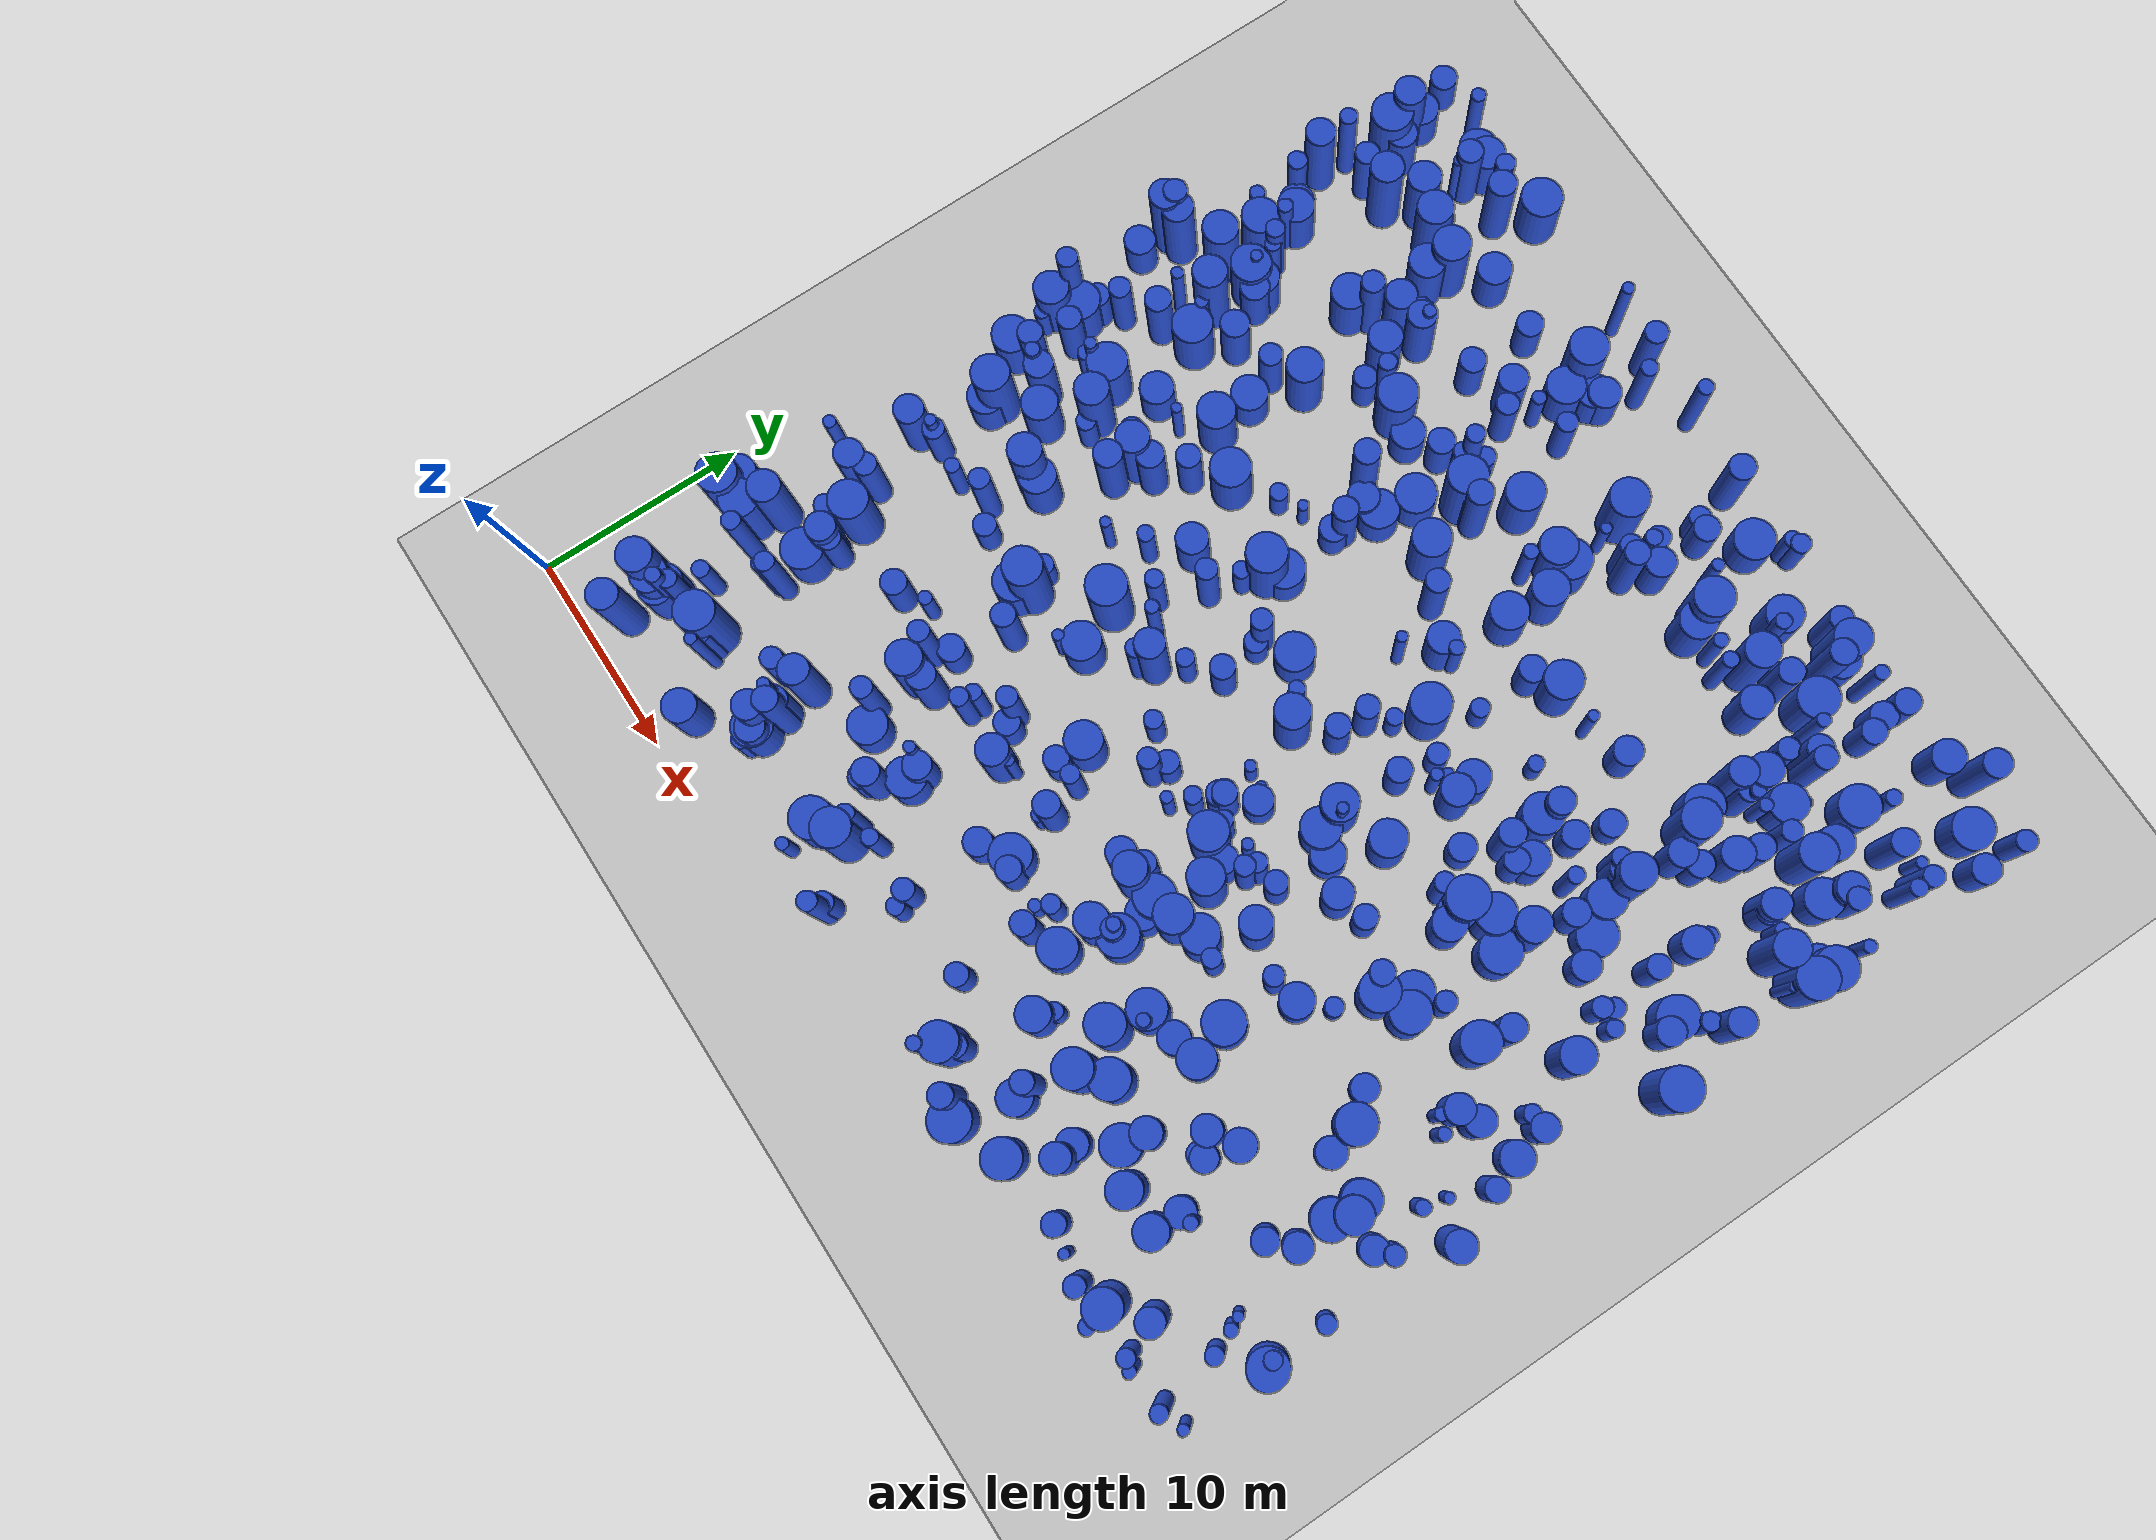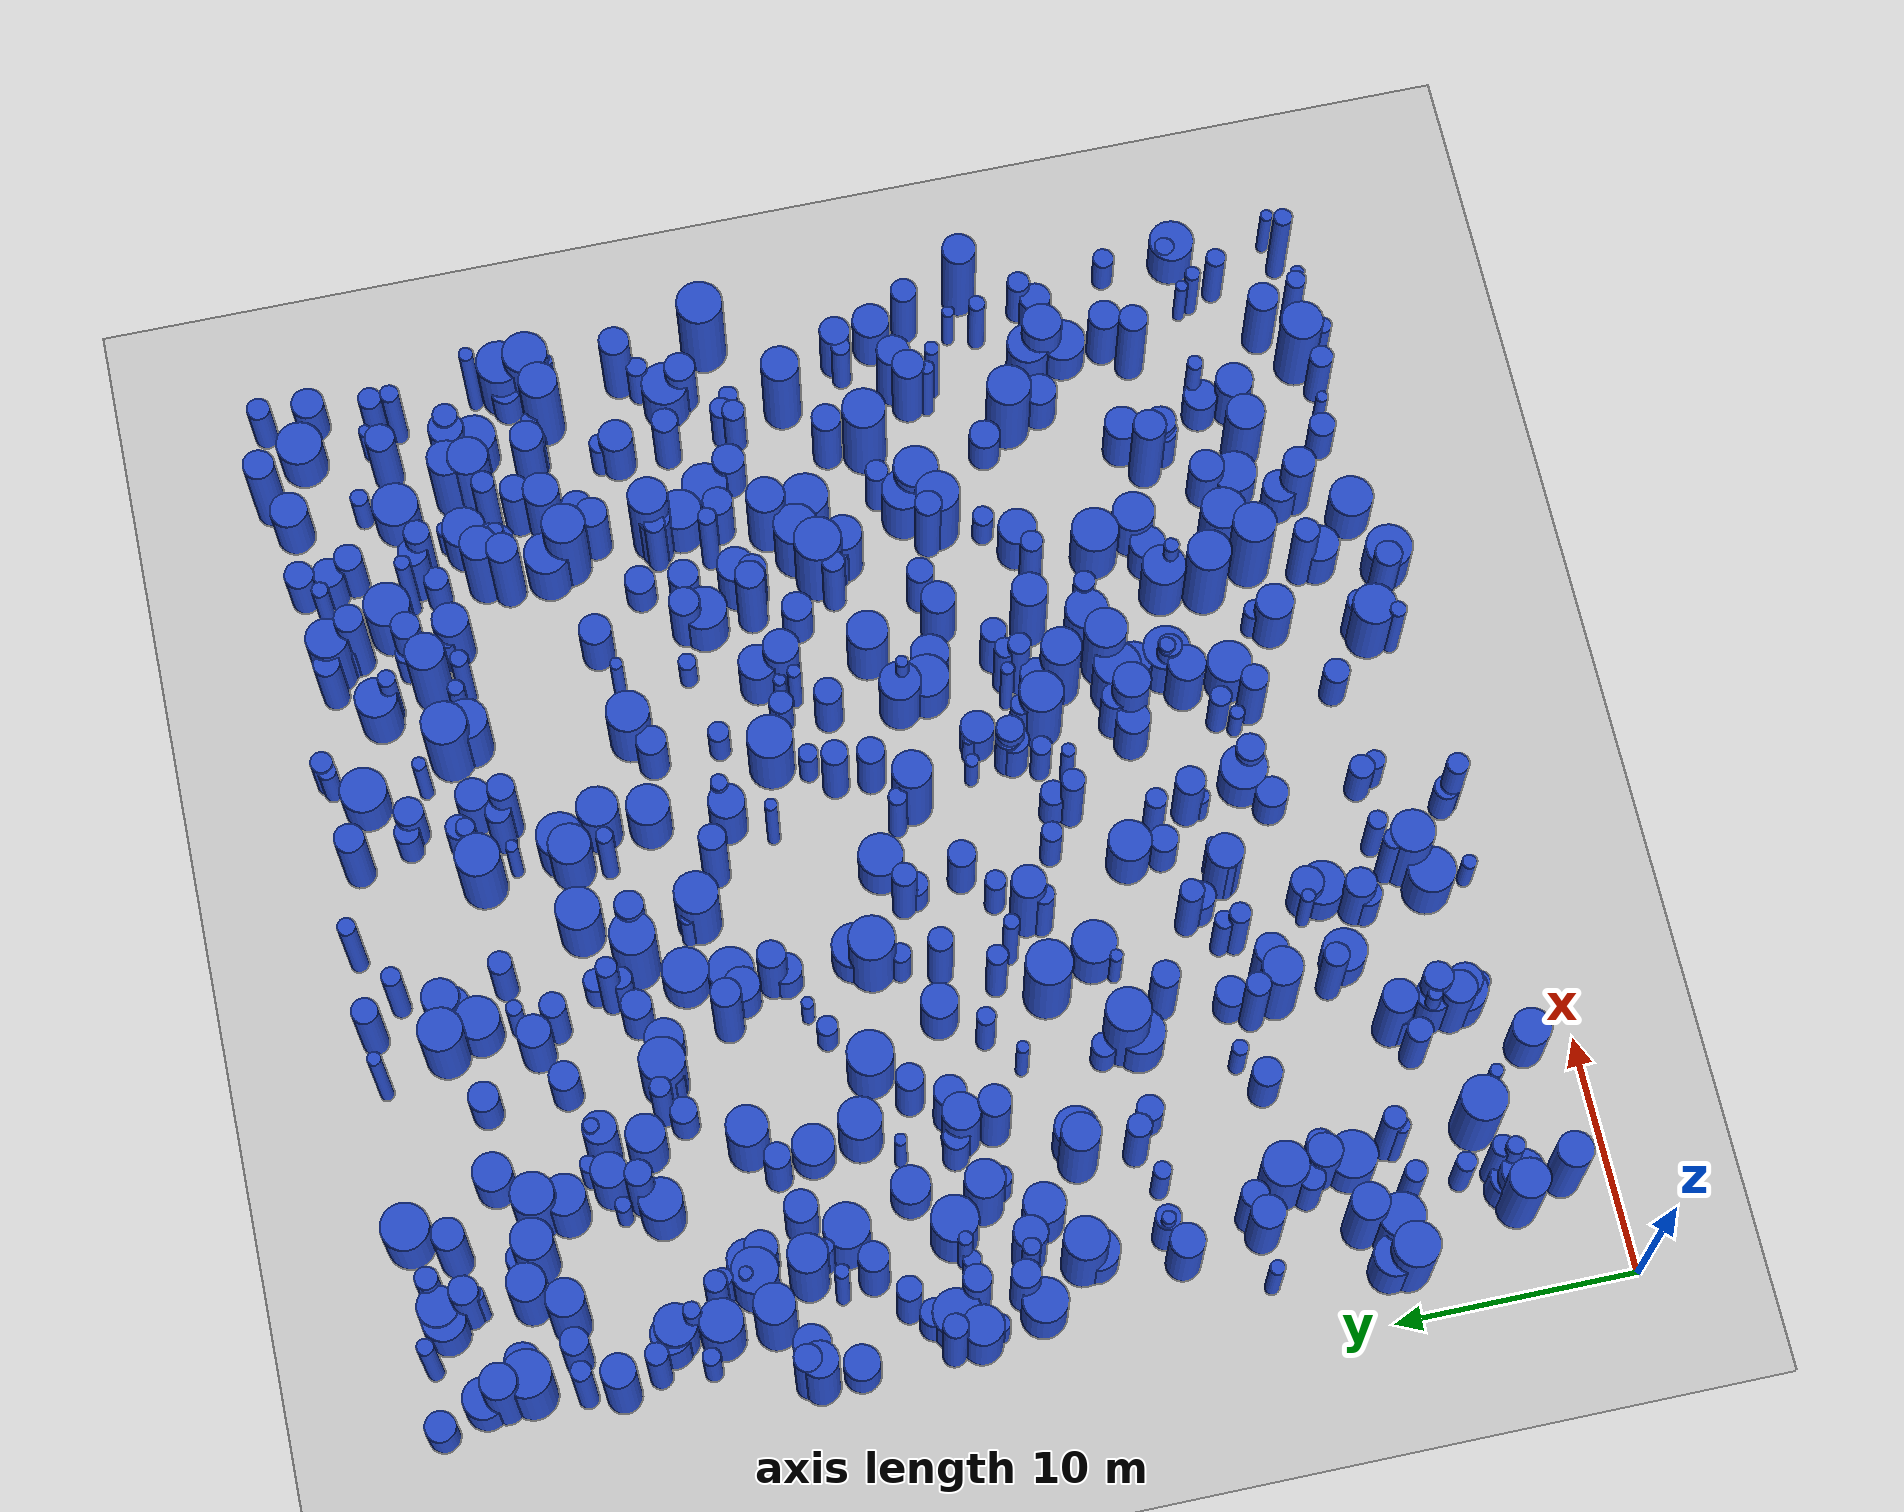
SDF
<sdf version="1.6">
 <world name="default">
  <plugin name="disable_physics" filename="libdisable_physics.so"/>
  <light name="sun" type="directional">
   <pose>0 0 10 0 -0 0</pose>
   <diffuse>0.8 0.8 0.8 1</diffuse>
   <specular>0.1 0.1 0.1 1</specular>
   <attenuation>
    <range>1000</range>
    <constant>0.9</constant>
    <linear>0.01</linear>
    <quadratic>0.001</quadratic>
   </attenuation>
   <direction>-0.5 0.5 -1</direction>
  </light>
  <model name="ground_plane">
   <static>1</static>
   <link name="link">
    <collision name="collision">
     <geometry><plane><normal>0 0 1</normal><size>100 100</size></plane></geometry>
     <surface><friction><ode><mu>100</mu><mu2>50</mu2></ode></friction></surface>
    </collision>
    <visual name="visual">
     <cast_shadows>0</cast_shadows>
     <geometry><plane><normal>0 0 1</normal><size>100 100</size></plane></geometry>
     <material>
      <script><uri>file://media/materials/scripts/gazebo.material</uri><name>Gazebo/Grey</name></script>
     </material>
    </visual>
   </link>
  </model>
  <gravity>0 0 -9.8</gravity>
  <magnetic_field>6e-06 2.3e-05 -4.2e-05</magnetic_field>
  <atmosphere type="adiabatic"/>
  <physics name="default_physics" default="0" type="ode">
   <max_step_size>0.001</max_step_size>
   <real_time_factor>1</real_time_factor>
   <real_time_update_rate>1000</real_time_update_rate>
  </physics>
  <scene><ambient>0.4 0.4 0.4 1</ambient><background>0.7 0.7 0.7 1</background><shadows>1</shadows></scene>
  <spherical_coordinates>
   <surface_model>EARTH_WGS84</surface_model>
   <latitude_deg>0</latitude_deg>
   <longitude_deg>0</longitude_deg>
   <elevation>0</elevation>
   <heading_deg>0</heading_deg>
  </spherical_coordinates>
  <model name="0">
   <static>0</static>
   <link name="link">
    <inertial>
     <mass>2</mass>
     <inertia><ixx>2.40197</ixx><ixy>0</ixy><ixz>0</ixz><iyy>2.40197</iyy><iyz>0</iyz><izz>0.81177</izz></inertia>
    </inertial>
    <collision name="collision">
     <geometry><cylinder><length>3.46071</length><radius>0.900983</radius></cylinder></geometry>
     <surface><contact><collide_without_contact>1</collide_without_contact></contact></surface>
    </collision>
    <visual name="visual">
     <geometry><cylinder><length>3.46071</length><radius>0.900983</radius></cylinder></geometry>
     <material>
      <script><uri>file://media/materials/scripts/gazebo.material</uri><name>Gazebo/Blue</name></script>
     </material>
    </visual>
    <gravity>0</gravity>
   </link>
   <pose>11.8767 29.2592 1.73036 0 -0 0</pose>
  </model>
  <model name="1">
   <static>0</static>
   <link name="link">
    <inertial>
     <mass>2</mass>
     <inertia>
      <ixx>0.889597</ixx>
      <ixy>0</ixy>
      <ixz>0</ixz>
      <iyy>0.889597</iyy>
      <iyz>0</iyz>
      <izz>0.404641</izz>
     </inertia>
    </inertial>
    <collision name="collision">
     <geometry><cylinder><length>2.03068</length><radius>0.636114</radius></cylinder></geometry>
     <surface><contact><collide_without_contact>1</collide_without_contact></contact></surface>
    </collision>
    <visual name="visual">
     <geometry><cylinder><length>2.03068</length><radius>0.636114</radius></cylinder></geometry>
     <material>
      <script><uri>file://media/materials/scripts/gazebo.material</uri><name>Gazebo/Blue</name></script>
     </material>
    </visual>
    <gravity>0</gravity>
   </link>
   <pose>3.46889 47.8136 1.01534 0 -0 0</pose>
  </model>
  <model name="2">
   <static>0</static>
   <link name="link">
    <inertial>
     <mass>2</mass>
     <inertia>
      <ixx>2.45511</ixx>
      <ixy>0</ixy>
      <ixz>0</ixz>
      <iyy>2.45511</iyy>
      <iyz>0</iyz>
      <izz>0.0849773</izz>
     </inertia>
    </inertial>
    <collision name="collision">
     <geometry><cylinder><length>3.8047</length><radius>0.291509</radius></cylinder></geometry>
     <surface><contact><collide_without_contact>1</collide_without_contact></contact></surface>
    </collision>
    <visual name="visual">
     <geometry><cylinder><length>3.8047</length><radius>0.291509</radius></cylinder></geometry>
     <material>
      <script><uri>file://media/materials/scripts/gazebo.material</uri><name>Gazebo/Blue</name></script>
     </material>
    </visual>
    <gravity>0</gravity>
   </link>
   <pose>6.11121 26.2319 1.90235 0 -0 0</pose>
  </model>
  <model name="3">
   <static>0</static>
   <link name="link">
    <inertial>
     <mass>2</mass>
     <inertia><ixx>3.44328</ixx><ixy>0</ixy><ixz>0</ixz><iyy>3.44328</iyy><iyz>0</iyz><izz>0.742387</izz></inertia>
    </inertial>
    <collision name="collision">
     <geometry><cylinder><length>4.29331</length><radius>0.861619</radius></cylinder></geometry>
     <surface><contact><collide_without_contact>1</collide_without_contact></contact></surface>
    </collision>
    <visual name="visual">
     <geometry><cylinder><length>4.29331</length><radius>0.861619</radius></cylinder></geometry>
     <material>
      <script><uri>file://media/materials/scripts/gazebo.material</uri><name>Gazebo/Blue</name></script>
     </material>
    </visual>
    <gravity>0</gravity>
   </link>
   <pose>9.53934 42.8927 2.14666 0 -0 0</pose>
  </model>
  <model name="4">
   <static>0</static>
   <link name="link">
    <inertial>
     <mass>2</mass>
     <inertia><ixx>1.52078</ixx><ixy>0</ixy><ixz>0</ixz><iyy>1.52078</iyy><iyz>0</iyz><izz>0.706881</izz></inertia>
    </inertial>
    <collision name="collision">
     <geometry><cylinder><length>2.64651</length><radius>0.840762</radius></cylinder></geometry>
     <surface><contact><collide_without_contact>1</collide_without_contact></contact></surface>
    </collision>
    <visual name="visual">
     <geometry><cylinder><length>2.64651</length><radius>0.840762</radius></cylinder></geometry>
     <material>
      <script><uri>file://media/materials/scripts/gazebo.material</uri><name>Gazebo/Blue</name></script>
     </material>
    </visual>
    <gravity>0</gravity>
   </link>
   <pose>5.06571 38.2801 1.32326 0 -0 0</pose>
  </model>
  <model name="5">
   <static>0</static>
   <link name="link">
    <inertial>
     <mass>2</mass>
     <inertia>
      <ixx>1.85446</ixx>
      <ixy>0</ixy>
      <ixz>0</ixz>
      <iyy>1.85446</iyy>
      <iyz>0</iyz>
      <izz>0.0841204</izz>
     </inertia>
    </inertial>
    <collision name="collision">
     <geometry><cylinder><length>3.29763</length><radius>0.290035</radius></cylinder></geometry>
     <surface><contact><collide_without_contact>1</collide_without_contact></contact></surface>
    </collision>
    <visual name="visual">
     <geometry><cylinder><length>3.29763</length><radius>0.290035</radius></cylinder></geometry>
     <material>
      <script><uri>file://media/materials/scripts/gazebo.material</uri><name>Gazebo/Blue</name></script>
     </material>
    </visual>
    <gravity>0</gravity>
   </link>
   <pose>25.4526 17.6829 1.64882 0 -0 0</pose>
  </model>
  <model name="6">
   <static>0</static>
   <link name="link">
    <inertial>
     <mass>2</mass>
     <inertia>
      <ixx>0.798572</ixx>
      <ixy>0</ixy>
      <ixz>0</ixz>
      <iyy>0.798572</iyy>
      <iyz>0</iyz>
      <izz>0.198941</izz>
     </inertia>
    </inertial>
    <collision name="collision">
     <geometry><cylinder><length>2.04807</length><radius>0.446028</radius></cylinder></geometry>
     <surface><contact><collide_without_contact>1</collide_without_contact></contact></surface>
    </collision>
    <visual name="visual">
     <geometry><cylinder><length>2.04807</length><radius>0.446028</radius></cylinder></geometry>
     <material>
      <script><uri>file://media/materials/scripts/gazebo.material</uri><name>Gazebo/Blue</name></script>
     </material>
    </visual>
    <gravity>0</gravity>
   </link>
   <pose>36.9335 18.7301 1.02404 0 -0 0</pose>
  </model>
  <model name="7">
   <static>0</static>
   <link name="link">
    <inertial>
     <mass>2</mass>
     <inertia>
      <ixx>0.786749</ixx>
      <ixy>0</ixy>
      <ixz>0</ixz>
      <iyy>0.786749</iyy>
      <iyz>0</iyz>
      <izz>0.0926018</izz>
     </inertia>
    </inertial>
    <collision name="collision">
     <geometry><cylinder><length>2.10777</length><radius>0.304305</radius></cylinder></geometry>
     <surface><contact><collide_without_contact>1</collide_without_contact></contact></surface>
    </collision>
    <visual name="visual">
     <geometry><cylinder><length>2.10777</length><radius>0.304305</radius></cylinder></geometry>
     <material>
      <script><uri>file://media/materials/scripts/gazebo.material</uri><name>Gazebo/Blue</name></script>
     </material>
    </visual>
    <gravity>0</gravity>
   </link>
   <pose>26.0501 10.3515 1.05388 0 -0 0</pose>
  </model>
  <model name="8">
   <static>0</static>
   <link name="link">
    <inertial>
     <mass>2</mass>
     <inertia><ixx>4.21888</ixx><ixy>0</ixy><ixz>0</ixz><iyy>4.21888</iyy><iyz>0</iyz><izz>0.689911</izz></inertia>
    </inertial>
    <collision name="collision">
     <geometry><cylinder><length>4.82115</length><radius>0.830609</radius></cylinder></geometry>
     <surface><contact><collide_without_contact>1</collide_without_contact></contact></surface>
    </collision>
    <visual name="visual">
     <geometry><cylinder><length>4.82115</length><radius>0.830609</radius></cylinder></geometry>
     <material>
      <script><uri>file://media/materials/scripts/gazebo.material</uri><name>Gazebo/Blue</name></script>
     </material>
    </visual>
    <gravity>0</gravity>
   </link>
   <pose>45.7281 35.9267 2.41058 0 -0 0</pose>
  </model>
  <model name="9">
   <static>0</static>
   <link name="link">
    <inertial>
     <mass>2</mass>
     <inertia><ixx>1.68993</ixx><ixy>0</ixy><ixz>0</ixz><iyy>1.68993</iyy><iyz>0</iyz><izz>0.640182</izz></inertia>
    </inertial>
    <collision name="collision">
     <geometry><cylinder><length>2.86689</length><radius>0.800114</radius></cylinder></geometry>
     <surface><contact><collide_without_contact>1</collide_without_contact></contact></surface>
    </collision>
    <visual name="visual">
     <geometry><cylinder><length>2.86689</length><radius>0.800114</radius></cylinder></geometry>
     <material>
      <script><uri>file://media/materials/scripts/gazebo.material</uri><name>Gazebo/Blue</name></script>
     </material>
    </visual>
    <gravity>0</gravity>
   </link>
   <pose>42.9643 47.197 1.43344 0 -0 0</pose>
  </model>
  <model name="10">
   <static>0</static>
   <link name="link">
    <inertial>
     <mass>2</mass>
     <inertia><ixx>3.37741</ixx><ixy>0</ixy><ixz>0</ixz><iyy>3.37741</iyy><iyz>0</iyz><izz>0.399415</izz></inertia>
    </inertial>
    <collision name="collision">
     <geometry><cylinder><length>4.36649</length><radius>0.631993</radius></cylinder></geometry>
     <surface><contact><collide_without_contact>1</collide_without_contact></contact></surface>
    </collision>
    <visual name="visual">
     <geometry><cylinder><length>4.36649</length><radius>0.631993</radius></cylinder></geometry>
     <material>
      <script><uri>file://media/materials/scripts/gazebo.material</uri><name>Gazebo/Blue</name></script>
     </material>
    </visual>
    <gravity>0</gravity>
   </link>
   <pose>27.4503 47.0755 2.18325 0 -0 0</pose>
  </model>
  <model name="11">
   <static>0</static>
   <link name="link">
    <inertial>
     <mass>2</mass>
     <inertia><ixx>1.88105</ixx><ixy>0</ixy><ixz>0</ixz><iyy>1.88105</iyy><iyz>0</iyz><izz>0.812984</izz></inertia>
    </inertial>
    <collision name="collision">
     <geometry><cylinder><length>2.97445</length><radius>0.901656</radius></cylinder></geometry>
     <surface><contact><collide_without_contact>1</collide_without_contact></contact></surface>
    </collision>
    <visual name="visual">
     <geometry><cylinder><length>2.97445</length><radius>0.901656</radius></cylinder></geometry>
     <material>
      <script><uri>file://media/materials/scripts/gazebo.material</uri><name>Gazebo/Blue</name></script>
     </material>
    </visual>
    <gravity>0</gravity>
   </link>
   <pose>26.8547 34.9896 1.48722 0 -0 0</pose>
  </model>
  <model name="12">
   <static>0</static>
   <link name="link">
    <inertial>
     <mass>2</mass>
     <inertia><ixx>2.82446</ixx><ixy>0</ixy><ixz>0</ixz><iyy>2.82446</iyy><iyz>0</iyz><izz>0.396141</izz></inertia>
    </inertial>
    <collision name="collision">
     <geometry><cylinder><length>3.96967</length><radius>0.629398</radius></cylinder></geometry>
     <surface><contact><collide_without_contact>1</collide_without_contact></contact></surface>
    </collision>
    <visual name="visual">
     <geometry><cylinder><length>3.96967</length><radius>0.629398</radius></cylinder></geometry>
     <material>
      <script><uri>file://media/materials/scripts/gazebo.material</uri><name>Gazebo/Blue</name></script>
     </material>
    </visual>
    <gravity>0</gravity>
   </link>
   <pose>6.09867 29.9204 1.98484 0 -0 0</pose>
  </model>
  <model name="13">
   <static>0</static>
   <link name="link">
    <inertial>
     <mass>2</mass>
     <inertia><ixx>2.71597</ixx><ixy>0</ixy><ixz>0</ixz><iyy>2.71597</iyy><iyz>0</iyz><izz>0.923373</izz></inertia>
    </inertial>
    <collision name="collision">
     <geometry><cylinder><length>3.67773</length><radius>0.960923</radius></cylinder></geometry>
     <surface><contact><collide_without_contact>1</collide_without_contact></contact></surface>
    </collision>
    <visual name="visual">
     <geometry><cylinder><length>3.67773</length><radius>0.960923</radius></cylinder></geometry>
     <material>
      <script><uri>file://media/materials/scripts/gazebo.material</uri><name>Gazebo/Blue</name></script>
     </material>
    </visual>
    <gravity>0</gravity>
   </link>
   <pose>28.4623 29.5513 1.83887 0 -0 0</pose>
  </model>
  <model name="14">
   <static>0</static>
   <link name="link">
    <inertial>
     <mass>2</mass>
     <inertia><ixx>1.62326</ixx><ixy>0</ixy><ixz>0</ixz><iyy>1.62326</iyy><iyz>0</iyz><izz>0.944741</izz></inertia>
    </inertial>
    <collision name="collision">
     <geometry><cylinder><length>2.6278</length><radius>0.971978</radius></cylinder></geometry>
     <surface><contact><collide_without_contact>1</collide_without_contact></contact></surface>
    </collision>
    <visual name="visual">
     <geometry><cylinder><length>2.6278</length><radius>0.971978</radius></cylinder></geometry>
     <material>
      <script><uri>file://media/materials/scripts/gazebo.material</uri><name>Gazebo/Blue</name></script>
     </material>
    </visual>
    <gravity>0</gravity>
   </link>
   <pose>13.2788 17.3958 1.3139 0 -0 0</pose>
  </model>
  <model name="15">
   <static>0</static>
   <link name="link">
    <inertial>
     <mass>2</mass>
     <inertia>
      <ixx>0.941599</ixx>
      <ixy>0</ixy>
      <ixz>0</ixz>
      <iyy>0.941599</iyy>
      <iyz>0</iyz>
      <izz>0.406003</izz>
     </inertia>
    </inertial>
    <collision name="collision">
     <geometry><cylinder><length>2.10513</length><radius>0.637184</radius></cylinder></geometry>
     <surface><contact><collide_without_contact>1</collide_without_contact></contact></surface>
    </collision>
    <visual name="visual">
     <geometry><cylinder><length>2.10513</length><radius>0.637184</radius></cylinder></geometry>
     <material>
      <script><uri>file://media/materials/scripts/gazebo.material</uri><name>Gazebo/Blue</name></script>
     </material>
    </visual>
    <gravity>0</gravity>
   </link>
   <pose>46.8697 37.3288 1.05257 0 -0 0</pose>
  </model>
  <model name="16">
   <static>0</static>
   <link name="link">
    <inertial>
     <mass>2</mass>
     <inertia><ixx>1.57186</ixx><ixy>0</ixy><ixz>0</ixz><iyy>1.57186</iyy><iyz>0</iyz><izz>0.39585</izz></inertia>
    </inertial>
    <collision name="collision">
     <geometry><cylinder><length>2.87117</length><radius>0.629166</radius></cylinder></geometry>
     <surface><contact><collide_without_contact>1</collide_without_contact></contact></surface>
    </collision>
    <visual name="visual">
     <geometry><cylinder><length>2.87117</length><radius>0.629166</radius></cylinder></geometry>
     <material>
      <script><uri>file://media/materials/scripts/gazebo.material</uri><name>Gazebo/Blue</name></script>
     </material>
    </visual>
    <gravity>0</gravity>
   </link>
   <pose>28.6502 44.5978 1.43558 0 -0 0</pose>
  </model>
  <model name="17">
   <static>0</static>
   <link name="link">
    <inertial>
     <mass>2</mass>
     <inertia><ixx>1.66425</ixx><ixy>0</ixy><ixz>0</ixz><iyy>1.66425</iyy><iyz>0</iyz><izz>0.867576</izz></inertia>
    </inertial>
    <collision name="collision">
     <geometry><cylinder><length>2.71712</length><radius>0.931438</radius></cylinder></geometry>
     <surface><contact><collide_without_contact>1</collide_without_contact></contact></surface>
    </collision>
    <visual name="visual">
     <geometry><cylinder><length>2.71712</length><radius>0.931438</radius></cylinder></geometry>
     <material>
      <script><uri>file://media/materials/scripts/gazebo.material</uri><name>Gazebo/Blue</name></script>
     </material>
    </visual>
    <gravity>0</gravity>
   </link>
   <pose>3.28204 23.6146 1.35856 0 -0 0</pose>
  </model>
  <model name="18">
   <static>0</static>
   <link name="link">
    <inertial>
     <mass>2</mass>
     <inertia><ixx>1.93693</ixx><ixy>0</ixy><ixz>0</ixz><iyy>1.93693</iyy><iyz>0</iyz><izz>0.344966</izz></inertia>
    </inertial>
    <collision name="collision">
     <geometry><cylinder><length>3.25372</length><radius>0.587338</radius></cylinder></geometry>
     <surface><contact><collide_without_contact>1</collide_without_contact></contact></surface>
    </collision>
    <visual name="visual">
     <geometry><cylinder><length>3.25372</length><radius>0.587338</radius></cylinder></geometry>
     <material>
      <script><uri>file://media/materials/scripts/gazebo.material</uri><name>Gazebo/Blue</name></script>
     </material>
    </visual>
    <gravity>0</gravity>
   </link>
   <pose>36.1652 28.7323 1.62686 0 -0 0</pose>
  </model>
  <model name="19">
   <static>0</static>
   <link name="link">
    <inertial>
     <mass>2</mass>
     <inertia><ixx>1.56851</ixx><ixy>0</ixy><ixz>0</ixz><iyy>1.56851</iyy><iyz>0</iyz><izz>0.224417</izz></inertia>
    </inertial>
    <collision name="collision">
     <geometry><cylinder><length>2.95598</length><radius>0.473727</radius></cylinder></geometry>
     <surface><contact><collide_without_contact>1</collide_without_contact></contact></surface>
    </collision>
    <visual name="visual">
     <geometry><cylinder><length>2.95598</length><radius>0.473727</radius></cylinder></geometry>
     <material>
      <script><uri>file://media/materials/scripts/gazebo.material</uri><name>Gazebo/Blue</name></script>
     </material>
    </visual>
    <gravity>0</gravity>
   </link>
   <pose>46.86 15.0199 1.47799 0 -0 0</pose>
  </model>
  <model name="20">
   <static>0</static>
   <link name="link">
    <inertial>
     <mass>2</mass>
     <inertia><ixx>3.66593</ixx><ixy>0</ixy><ixz>0</ixz><iyy>3.66593</iyy><iyz>0</iyz><izz>0.841816</izz></inertia>
    </inertial>
    <collision name="collision">
     <geometry><cylinder><length>4.4125</length><radius>0.917505</radius></cylinder></geometry>
     <surface><contact><collide_without_contact>1</collide_without_contact></contact></surface>
    </collision>
    <visual name="visual">
     <geometry><cylinder><length>4.4125</length><radius>0.917505</radius></cylinder></geometry>
     <material>
      <script><uri>file://media/materials/scripts/gazebo.material</uri><name>Gazebo/Blue</name></script>
     </material>
    </visual>
    <gravity>0</gravity>
   </link>
   <pose>18.7168 4.95866 2.20625 0 -0 0</pose>
  </model>
  <model name="21">
   <static>0</static>
   <link name="link">
    <inertial>
     <mass>2</mass>
     <inertia><ixx>3.67494</ixx><ixy>0</ixy><ixz>0</ixz><iyy>3.67494</iyy><iyz>0</iyz><izz>0.558673</izz></inertia>
    </inertial>
    <collision name="collision">
     <geometry><cylinder><length>4.51371</length><radius>0.747444</radius></cylinder></geometry>
     <surface><contact><collide_without_contact>1</collide_without_contact></contact></surface>
    </collision>
    <visual name="visual">
     <geometry><cylinder><length>4.51371</length><radius>0.747444</radius></cylinder></geometry>
     <material>
      <script><uri>file://media/materials/scripts/gazebo.material</uri><name>Gazebo/Blue</name></script>
     </material>
    </visual>
    <gravity>0</gravity>
   </link>
   <pose>4.16992 45.1792 2.25686 0 -0 0</pose>
  </model>
  <model name="22">
   <static>0</static>
   <link name="link">
    <inertial>
     <mass>2</mass>
     <inertia><ixx>2.6096</ixx><ixy>0</ixy><ixz>0</ixz><iyy>2.6096</iyy><iyz>0</iyz><izz>0.20705</izz></inertia>
    </inertial>
    <collision name="collision">
     <geometry><cylinder><length>3.87769</length><radius>0.455027</radius></cylinder></geometry>
     <surface><contact><collide_without_contact>1</collide_without_contact></contact></surface>
    </collision>
    <visual name="visual">
     <geometry><cylinder><length>3.87769</length><radius>0.455027</radius></cylinder></geometry>
     <material>
      <script><uri>file://media/materials/scripts/gazebo.material</uri><name>Gazebo/Blue</name></script>
     </material>
    </visual>
    <gravity>0</gravity>
   </link>
   <pose>32.4033 15.4487 1.93884 0 -0 0</pose>
  </model>
  <model name="23">
   <static>0</static>
   <link name="link">
    <inertial>
     <mass>2</mass>
     <inertia>
      <ixx>3.22473</ixx>
      <ixy>0</ixy>
      <ixz>0</ixz>
      <iyy>3.22473</iyy>
      <iyz>0</iyz>
      <izz>0.0871934</izz>
     </inertia>
    </inertial>
    <collision name="collision">
     <geometry><cylinder><length>4.36884</length><radius>0.295285</radius></cylinder></geometry>
     <surface><contact><collide_without_contact>1</collide_without_contact></contact></surface>
    </collision>
    <visual name="visual">
     <geometry><cylinder><length>4.36884</length><radius>0.295285</radius></cylinder></geometry>
     <material>
      <script><uri>file://media/materials/scripts/gazebo.material</uri><name>Gazebo/Blue</name></script>
     </material>
    </visual>
    <gravity>0</gravity>
   </link>
   <pose>5.68019 31.273 2.18442 0 -0 0</pose>
  </model>
  <model name="24">
   <static>0</static>
   <link name="link">
    <inertial>
     <mass>2</mass>
     <inertia><ixx>2.50462</ixx><ixy>0</ixy><ixz>0</ixz><iyy>2.50462</iyy><iyz>0</iyz><izz>0.451325</izz></inertia>
    </inertial>
    <collision name="collision">
     <geometry><cylinder><length>3.69781</length><radius>0.671807</radius></cylinder></geometry>
     <surface><contact><collide_without_contact>1</collide_without_contact></contact></surface>
    </collision>
    <visual name="visual">
     <geometry><cylinder><length>3.69781</length><radius>0.671807</radius></cylinder></geometry>
     <material>
      <script><uri>file://media/materials/scripts/gazebo.material</uri><name>Gazebo/Blue</name></script>
     </material>
    </visual>
    <gravity>0</gravity>
   </link>
   <pose>39.0289 32.3304 1.8489 0 -0 0</pose>
  </model>
  <model name="25">
   <static>0</static>
   <link name="link">
    <inertial>
     <mass>2</mass>
     <inertia><ixx>2.00158</ixx><ixy>0</ixy><ixz>0</ixz><iyy>2.00158</iyy><iyz>0</iyz><izz>0.12036</izz></inertia>
    </inertial>
    <collision name="collision">
     <geometry><cylinder><length>3.41298</length><radius>0.346929</radius></cylinder></geometry>
     <surface><contact><collide_without_contact>1</collide_without_contact></contact></surface>
    </collision>
    <visual name="visual">
     <geometry><cylinder><length>3.41298</length><radius>0.346929</radius></cylinder></geometry>
     <material>
      <script><uri>file://media/materials/scripts/gazebo.material</uri><name>Gazebo/Blue</name></script>
     </material>
    </visual>
    <gravity>0</gravity>
   </link>
   <pose>42.8894 40.3109 1.70649 0 -0 0</pose>
  </model>
  <model name="26">
   <static>0</static>
   <link name="link">
    <inertial>
     <mass>2</mass>
     <inertia><ixx>2.48469</ixx><ixy>0</ixy><ixz>0</ixz><iyy>2.48469</iyy><iyz>0</iyz><izz>0.314146</izz></inertia>
    </inertial>
    <collision name="collision">
     <geometry><cylinder><length>3.73707</length><radius>0.560487</radius></cylinder></geometry>
     <surface><contact><collide_without_contact>1</collide_without_contact></contact></surface>
    </collision>
    <visual name="visual">
     <geometry><cylinder><length>3.73707</length><radius>0.560487</radius></cylinder></geometry>
     <material>
      <script><uri>file://media/materials/scripts/gazebo.material</uri><name>Gazebo/Blue</name></script>
     </material>
    </visual>
    <gravity>0</gravity>
   </link>
   <pose>43.2934 31.0546 1.86853 0 -0 0</pose>
  </model>
  <model name="27">
   <static>0</static>
   <link name="link">
    <inertial>
     <mass>2</mass>
     <inertia><ixx>3.29031</ixx><ixy>0</ixy><ixz>0</ixz><iyy>3.29031</iyy><iyz>0</iyz><izz>0.876091</izz></inertia>
    </inertial>
    <collision name="collision">
     <geometry><cylinder><length>4.13686</length><radius>0.935998</radius></cylinder></geometry>
     <surface><contact><collide_without_contact>1</collide_without_contact></contact></surface>
    </collision>
    <visual name="visual">
     <geometry><cylinder><length>4.13686</length><radius>0.935998</radius></cylinder></geometry>
     <material>
      <script><uri>file://media/materials/scripts/gazebo.material</uri><name>Gazebo/Blue</name></script>
     </material>
    </visual>
    <gravity>0</gravity>
   </link>
   <pose>25.7568 42.1534 2.06843 0 -0 0</pose>
  </model>
  <model name="28">
   <static>0</static>
   <link name="link">
    <inertial>
     <mass>2</mass>
     <inertia><ixx>3.70127</ixx><ixy>0</ixy><ixz>0</ixz><iyy>3.70127</iyy><iyz>0</iyz><izz>0.908045</izz></inertia>
    </inertial>
    <collision name="collision">
     <geometry><cylinder><length>4.41401</length><radius>0.952914</radius></cylinder></geometry>
     <surface><contact><collide_without_contact>1</collide_without_contact></contact></surface>
    </collision>
    <visual name="visual">
     <geometry><cylinder><length>4.41401</length><radius>0.952914</radius></cylinder></geometry>
     <material>
      <script><uri>file://media/materials/scripts/gazebo.material</uri><name>Gazebo/Blue</name></script>
     </material>
    </visual>
    <gravity>0</gravity>
   </link>
   <pose>31.5585 42.4736 2.20701 0 -0 0</pose>
  </model>
  <model name="29">
   <static>0</static>
   <link name="link">
    <inertial>
     <mass>2</mass>
     <inertia><ixx>2.78165</ixx><ixy>0</ixy><ixz>0</ixz><iyy>2.78165</iyy><iyz>0</iyz><izz>0.746331</izz></inertia>
    </inertial>
    <collision name="collision">
     <geometry><cylinder><length>3.80143</length><radius>0.863904</radius></cylinder></geometry>
     <surface><contact><collide_without_contact>1</collide_without_contact></contact></surface>
    </collision>
    <visual name="visual">
     <geometry><cylinder><length>3.80143</length><radius>0.863904</radius></cylinder></geometry>
     <material>
      <script><uri>file://media/materials/scripts/gazebo.material</uri><name>Gazebo/Blue</name></script>
     </material>
    </visual>
    <gravity>0</gravity>
   </link>
   <pose>12.4132 33.7284 1.90072 0 -0 0</pose>
  </model>
  <model name="30">
   <static>0</static>
   <link name="link">
    <inertial>
     <mass>2</mass>
     <inertia><ixx>1.34983</ixx><ixy>0</ixy><ixz>0</ixz><iyy>1.34983</iyy><iyz>0</iyz><izz>0.973345</izz></inertia>
    </inertial>
    <collision name="collision">
     <geometry><cylinder><length>2.27573</length><radius>0.986583</radius></cylinder></geometry>
     <surface><contact><collide_without_contact>1</collide_without_contact></contact></surface>
    </collision>
    <visual name="visual">
     <geometry><cylinder><length>2.27573</length><radius>0.986583</radius></cylinder></geometry>
     <material>
      <script><uri>file://media/materials/scripts/gazebo.material</uri><name>Gazebo/Blue</name></script>
     </material>
    </visual>
    <gravity>0</gravity>
   </link>
   <pose>42.5501 42.8164 1.13786 0 -0 0</pose>
  </model>
  <model name="31">
   <static>0</static>
   <link name="link">
    <inertial>
     <mass>2</mass>
     <inertia>
      <ixx>0.960927</ixx>
      <ixy>0</ixy>
      <ixz>0</ixz>
      <iyy>0.960927</iyy>
      <iyz>0</iyz>
      <izz>0.413143</izz>
     </inertia>
    </inertial>
    <collision name="collision">
     <geometry><cylinder><length>2.12747</length><radius>0.642762</radius></cylinder></geometry>
     <surface><contact><collide_without_contact>1</collide_without_contact></contact></surface>
    </collision>
    <visual name="visual">
     <geometry><cylinder><length>2.12747</length><radius>0.642762</radius></cylinder></geometry>
     <material>
      <script><uri>file://media/materials/scripts/gazebo.material</uri><name>Gazebo/Blue</name></script>
     </material>
    </visual>
    <gravity>0</gravity>
   </link>
   <pose>29.9876 46.2303 1.06374 0 -0 0</pose>
  </model>
  <model name="32">
   <static>0</static>
   <link name="link">
    <inertial>
     <mass>2</mass>
     <inertia><ixx>1.10606</ixx><ixy>0</ixy><ixz>0</ixz><iyy>1.10606</iyy><iyz>0</iyz><izz>0.512174</izz></inertia>
    </inertial>
    <collision name="collision">
     <geometry><cylinder><length>2.25828</length><radius>0.715663</radius></cylinder></geometry>
     <surface><contact><collide_without_contact>1</collide_without_contact></contact></surface>
    </collision>
    <visual name="visual">
     <geometry><cylinder><length>2.25828</length><radius>0.715663</radius></cylinder></geometry>
     <material>
      <script><uri>file://media/materials/scripts/gazebo.material</uri><name>Gazebo/Blue</name></script>
     </material>
    </visual>
    <gravity>0</gravity>
   </link>
   <pose>27.6259 21.0165 1.12914 0 -0 0</pose>
  </model>
  <model name="33">
   <static>0</static>
   <link name="link">
    <inertial>
     <mass>2</mass>
     <inertia><ixx>3.10542</ixx><ixy>0</ixy><ixz>0</ixz><iyy>3.10542</iyy><iyz>0</iyz><izz>0.188951</izz></inertia>
    </inertial>
    <collision name="collision">
     <geometry><cylinder><length>4.25037</length><radius>0.434685</radius></cylinder></geometry>
     <surface><contact><collide_without_contact>1</collide_without_contact></contact></surface>
    </collision>
    <visual name="visual">
     <geometry><cylinder><length>4.25037</length><radius>0.434685</radius></cylinder></geometry>
     <material>
      <script><uri>file://media/materials/scripts/gazebo.material</uri><name>Gazebo/Blue</name></script>
     </material>
    </visual>
    <gravity>0</gravity>
   </link>
   <pose>17.1407 22.5153 2.12519 0 -0 0</pose>
  </model>
  <model name="34">
   <static>0</static>
   <link name="link">
    <inertial>
     <mass>2</mass>
     <inertia>
      <ixx>2.68848</ixx>
      <ixy>0</ixy>
      <ixz>0</ixz>
      <iyy>2.68848</iyy>
      <iyz>0</iyz>
      <izz>0.0949899</izz>
     </inertia>
    </inertial>
    <collision name="collision">
     <geometry><cylinder><length>3.98069</length><radius>0.308204</radius></cylinder></geometry>
     <surface><contact><collide_without_contact>1</collide_without_contact></contact></surface>
    </collision>
    <visual name="visual">
     <geometry><cylinder><length>3.98069</length><radius>0.308204</radius></cylinder></geometry>
     <material>
      <script><uri>file://media/materials/scripts/gazebo.material</uri><name>Gazebo/Blue</name></script>
     </material>
    </visual>
    <gravity>0</gravity>
   </link>
   <pose>19.1357 12.4341 1.99035 0 -0 0</pose>
  </model>
  <model name="35">
   <static>0</static>
   <link name="link">
    <inertial>
     <mass>2</mass>
     <inertia><ixx>4.18085</ixx><ixy>0</ixy><ixz>0</ixz><iyy>4.18085</iyy><iyz>0</iyz><izz>0.105493</izz></inertia>
    </inertial>
    <collision name="collision">
     <geometry><cylinder><length>4.97681</length><radius>0.324796</radius></cylinder></geometry>
     <surface><contact><collide_without_contact>1</collide_without_contact></contact></surface>
    </collision>
    <visual name="visual">
     <geometry><cylinder><length>4.97681</length><radius>0.324796</radius></cylinder></geometry>
     <material>
      <script><uri>file://media/materials/scripts/gazebo.material</uri><name>Gazebo/Blue</name></script>
     </material>
    </visual>
    <gravity>0</gravity>
   </link>
   <pose>38.6592 42.8925 2.4884 0 -0 0</pose>
  </model>
  <model name="36">
   <static>0</static>
   <link name="link">
    <inertial>
     <mass>2</mass>
     <inertia><ixx>1.08426</ixx><ixy>0</ixy><ixz>0</ixz><iyy>1.08426</iyy><iyz>0</iyz><izz>0.683304</izz></inertia>
    </inertial>
    <collision name="collision">
     <geometry><cylinder><length>2.11084</length><radius>0.826622</radius></cylinder></geometry>
     <surface><contact><collide_without_contact>1</collide_without_contact></contact></surface>
    </collision>
    <visual name="visual">
     <geometry><cylinder><length>2.11084</length><radius>0.826622</radius></cylinder></geometry>
     <material>
      <script><uri>file://media/materials/scripts/gazebo.material</uri><name>Gazebo/Blue</name></script>
     </material>
    </visual>
    <gravity>0</gravity>
   </link>
   <pose>31.3215 22.2177 1.05542 0 -0 0</pose>
  </model>
  <model name="37">
   <static>0</static>
   <link name="link">
    <inertial>
     <mass>2</mass>
     <inertia><ixx>2.41909</ixx><ixy>0</ixy><ixz>0</ixz><iyy>2.41909</iyy><iyz>0</iyz><izz>0.120372</izz></inertia>
    </inertial>
    <collision name="collision">
     <geometry><cylinder><length>3.76211</length><radius>0.346947</radius></cylinder></geometry>
     <surface><contact><collide_without_contact>1</collide_without_contact></contact></surface>
    </collision>
    <visual name="visual">
     <geometry><cylinder><length>3.76211</length><radius>0.346947</radius></cylinder></geometry>
     <material>
      <script><uri>file://media/materials/scripts/gazebo.material</uri><name>Gazebo/Blue</name></script>
     </material>
    </visual>
    <gravity>0</gravity>
   </link>
   <pose>33.2468 41.7347 1.88105 0 -0 0</pose>
  </model>
  <model name="38">
   <static>0</static>
   <link name="link">
    <inertial>
     <mass>2</mass>
     <inertia><ixx>1.23877</ixx><ixy>0</ixy><ixz>0</ixz><iyy>1.23877</iyy><iyz>0</iyz><izz>0.661511</izz></inertia>
    </inertial>
    <collision name="collision">
     <geometry><cylinder><length>2.33412</length><radius>0.813333</radius></cylinder></geometry>
     <surface><contact><collide_without_contact>1</collide_without_contact></contact></surface>
    </collision>
    <visual name="visual">
     <geometry><cylinder><length>2.33412</length><radius>0.813333</radius></cylinder></geometry>
     <material>
      <script><uri>file://media/materials/scripts/gazebo.material</uri><name>Gazebo/Blue</name></script>
     </material>
    </visual>
    <gravity>0</gravity>
   </link>
   <pose>9.0777 27.7968 1.16706 0 -0 0</pose>
  </model>
  <model name="39">
   <static>0</static>
   <link name="link">
    <inertial>
     <mass>2</mass>
     <inertia><ixx>1.53544</ixx><ixy>0</ixy><ixz>0</ixz><iyy>1.53544</iyy><iyz>0</iyz><izz>0.411838</izz></inertia>
    </inertial>
    <collision name="collision">
     <geometry><cylinder><length>2.82438</length><radius>0.641746</radius></cylinder></geometry>
     <surface><contact><collide_without_contact>1</collide_without_contact></contact></surface>
    </collision>
    <visual name="visual">
     <geometry><cylinder><length>2.82438</length><radius>0.641746</radius></cylinder></geometry>
     <material>
      <script><uri>file://media/materials/scripts/gazebo.material</uri><name>Gazebo/Blue</name></script>
     </material>
    </visual>
    <gravity>0</gravity>
   </link>
   <pose>18.6007 37.0653 1.41219 0 -0 0</pose>
  </model>
  <model name="40">
   <static>0</static>
   <link name="link">
    <inertial>
     <mass>2</mass>
     <inertia><ixx>1.05673</ixx><ixy>0</ixy><ixz>0</ixz><iyy>1.05673</iyy><iyz>0</iyz><izz>0.145747</izz></inertia>
    </inertial>
    <collision name="collision">
     <geometry><cylinder><length>2.42964</length><radius>0.381768</radius></cylinder></geometry>
     <surface><contact><collide_without_contact>1</collide_without_contact></contact></surface>
    </collision>
    <visual name="visual">
     <geometry><cylinder><length>2.42964</length><radius>0.381768</radius></cylinder></geometry>
     <material>
      <script><uri>file://media/materials/scripts/gazebo.material</uri><name>Gazebo/Blue</name></script>
     </material>
    </visual>
    <gravity>0</gravity>
   </link>
   <pose>43.0934 44.2266 1.21482 0 -0 0</pose>
  </model>
  <model name="41">
   <static>0</static>
   <link name="link">
    <inertial>
     <mass>2</mass>
     <inertia><ixx>1.91434</ixx><ixy>0</ixy><ixz>0</ixz><iyy>1.91434</iyy><iyz>0</iyz><izz>0.273493</izz></inertia>
    </inertial>
    <collision name="collision">
     <geometry><cylinder><length>3.26581</length><radius>0.522966</radius></cylinder></geometry>
     <surface><contact><collide_without_contact>1</collide_without_contact></contact></surface>
    </collision>
    <visual name="visual">
     <geometry><cylinder><length>3.26581</length><radius>0.522966</radius></cylinder></geometry>
     <material>
      <script><uri>file://media/materials/scripts/gazebo.material</uri><name>Gazebo/Blue</name></script>
     </material>
    </visual>
    <gravity>0</gravity>
   </link>
   <pose>5.77971 12.2342 1.63291 0 -0 0</pose>
  </model>
  <model name="42">
   <static>0</static>
   <link name="link">
    <inertial>
     <mass>2</mass>
     <inertia><ixx>2.01453</ixx><ixy>0</ixy><ixz>0</ixz><iyy>2.01453</iyy><iyz>0</iyz><izz>0.344549</izz></inertia>
    </inertial>
    <collision name="collision">
     <geometry><cylinder><length>3.32468</length><radius>0.586983</radius></cylinder></geometry>
     <surface><contact><collide_without_contact>1</collide_without_contact></contact></surface>
    </collision>
    <visual name="visual">
     <geometry><cylinder><length>3.32468</length><radius>0.586983</radius></cylinder></geometry>
     <material>
      <script><uri>file://media/materials/scripts/gazebo.material</uri><name>Gazebo/Blue</name></script>
     </material>
    </visual>
    <gravity>0</gravity>
   </link>
   <pose>21.9562 22.9154 1.66234 0 -0 0</pose>
  </model>
  <model name="43">
   <static>0</static>
   <link name="link">
    <inertial>
     <mass>2</mass>
     <inertia><ixx>2.34581</ixx><ixy>0</ixy><ixz>0</ixz><iyy>2.34581</iyy><iyz>0</iyz><izz>0.257799</izz></inertia>
    </inertial>
    <collision name="collision">
     <geometry><cylinder><length>3.64712</length><radius>0.507739</radius></cylinder></geometry>
     <surface><contact><collide_without_contact>1</collide_without_contact></contact></surface>
    </collision>
    <visual name="visual">
     <geometry><cylinder><length>3.64712</length><radius>0.507739</radius></cylinder></geometry>
     <material>
      <script><uri>file://media/materials/scripts/gazebo.material</uri><name>Gazebo/Blue</name></script>
     </material>
    </visual>
    <gravity>0</gravity>
   </link>
   <pose>28.9554 12.6154 1.82356 0 -0 0</pose>
  </model>
  <model name="44">
   <static>0</static>
   <link name="link">
    <inertial>
     <mass>2</mass>
     <inertia><ixx>1.1939</ixx><ixy>0</ixy><ixz>0</ixz><iyy>1.1939</iyy><iyz>0</iyz><izz>0.566577</izz></inertia>
    </inertial>
    <collision name="collision">
     <geometry><cylinder><length>2.33744</length><radius>0.752713</radius></cylinder></geometry>
     <surface><contact><collide_without_contact>1</collide_without_contact></contact></surface>
    </collision>
    <visual name="visual">
     <geometry><cylinder><length>2.33744</length><radius>0.752713</radius></cylinder></geometry>
     <material>
      <script><uri>file://media/materials/scripts/gazebo.material</uri><name>Gazebo/Blue</name></script>
     </material>
    </visual>
    <gravity>0</gravity>
   </link>
   <pose>34.1931 12.2769 1.16872 0 -0 0</pose>
  </model>
  <model name="45">
   <static>0</static>
   <link name="link">
    <inertial>
     <mass>2</mass>
     <inertia>
      <ixx>3.27441</ixx>
      <ixy>0</ixy>
      <ixz>0</ixz>
      <iyy>3.27441</iyy>
      <iyz>0</iyz>
      <izz>0.0994808</izz>
     </inertia>
    </inertial>
    <collision name="collision">
     <geometry><cylinder><length>4.39864</length><radius>0.315406</radius></cylinder></geometry>
     <surface><contact><collide_without_contact>1</collide_without_contact></contact></surface>
    </collision>
    <visual name="visual">
     <geometry><cylinder><length>4.39864</length><radius>0.315406</radius></cylinder></geometry>
     <material>
      <script><uri>file://media/materials/scripts/gazebo.material</uri><name>Gazebo/Blue</name></script>
     </material>
    </visual>
    <gravity>0</gravity>
   </link>
   <pose>43.9023 19.4399 2.19932 0 -0 0</pose>
  </model>
  <model name="46">
   <static>0</static>
   <link name="link">
    <inertial>
     <mass>2</mass>
     <inertia><ixx>3.85343</ixx><ixy>0</ixy><ixz>0</ixz><iyy>3.85343</iyy><iyz>0</iyz><izz>0.911922</izz></inertia>
    </inertial>
    <collision name="collision">
     <geometry><cylinder><length>4.51496</length><radius>0.954946</radius></cylinder></geometry>
     <surface><contact><collide_without_contact>1</collide_without_contact></contact></surface>
    </collision>
    <visual name="visual">
     <geometry><cylinder><length>4.51496</length><radius>0.954946</radius></cylinder></geometry>
     <material>
      <script><uri>file://media/materials/scripts/gazebo.material</uri><name>Gazebo/Blue</name></script>
     </material>
    </visual>
    <gravity>0</gravity>
   </link>
   <pose>7.20316 4.98001 2.25748 0 -0 0</pose>
  </model>
  <model name="47">
   <static>0</static>
   <link name="link">
    <inertial>
     <mass>2</mass>
     <inertia><ixx>2.29041</ixx><ixy>0</ixy><ixz>0</ixz><iyy>2.29041</iyy><iyz>0</iyz><izz>0.757429</izz></inertia>
    </inertial>
    <collision name="collision">
     <geometry><cylinder><length>3.38677</length><radius>0.870304</radius></cylinder></geometry>
     <surface><contact><collide_without_contact>1</collide_without_contact></contact></surface>
    </collision>
    <visual name="visual">
     <geometry><cylinder><length>3.38677</length><radius>0.870304</radius></cylinder></geometry>
     <material>
      <script><uri>file://media/materials/scripts/gazebo.material</uri><name>Gazebo/Blue</name></script>
     </material>
    </visual>
    <gravity>0</gravity>
   </link>
   <pose>29.8515 23.8039 1.69338 0 -0 0</pose>
  </model>
  <model name="48">
   <static>0</static>
   <link name="link">
    <inertial>
     <mass>2</mass>
     <inertia>
      <ixx>0.820157</ixx>
      <ixy>0</ixy>
      <ixz>0</ixz>
      <iyy>0.820157</iyy>
      <iyz>0</iyz>
      <izz>0.29591</izz>
     </inertia>
    </inertial>
    <collision name="collision">
     <geometry><cylinder><length>2.00829</length><radius>0.543976</radius></cylinder></geometry>
     <surface><contact><collide_without_contact>1</collide_without_contact></contact></surface>
    </collision>
    <visual name="visual">
     <geometry><cylinder><length>2.00829</length><radius>0.543976</radius></cylinder></geometry>
     <material>
      <script><uri>file://media/materials/scripts/gazebo.material</uri><name>Gazebo/Blue</name></script>
     </material>
    </visual>
    <gravity>0</gravity>
   </link>
   <pose>21.5362 24.945 1.00414 0 -0 0</pose>
  </model>
  <model name="49">
   <static>0</static>
   <link name="link">
    <inertial>
     <mass>2</mass>
     <inertia><ixx>3.34845</ixx><ixy>0</ixy><ixz>0</ixz><iyy>3.34845</iyy><iyz>0</iyz><izz>0.625624</izz></inertia>
    </inertial>
    <collision name="collision">
     <geometry><cylinder><length>4.26777</length><radius>0.790964</radius></cylinder></geometry>
     <surface><contact><collide_without_contact>1</collide_without_contact></contact></surface>
    </collision>
    <visual name="visual">
     <geometry><cylinder><length>4.26777</length><radius>0.790964</radius></cylinder></geometry>
     <material>
      <script><uri>file://media/materials/scripts/gazebo.material</uri><name>Gazebo/Blue</name></script>
     </material>
    </visual>
    <gravity>0</gravity>
   </link>
   <pose>11.0842 25.3159 2.13388 0 -0 0</pose>
  </model>
  <model name="50">
   <static>0</static>
   <link name="link">
    <inertial>
     <mass>2</mass>
     <inertia><ixx>1.52309</ixx><ixy>0</ixy><ixz>0</ixz><iyy>1.52309</iyy><iyz>0</iyz><izz>0.943157</izz></inertia>
    </inertial>
    <collision name="collision">
     <geometry><cylinder><length>2.51179</length><radius>0.971163</radius></cylinder></geometry>
     <surface><contact><collide_without_contact>1</collide_without_contact></contact></surface>
    </collision>
    <visual name="visual">
     <geometry><cylinder><length>2.51179</length><radius>0.971163</radius></cylinder></geometry>
     <material>
      <script><uri>file://media/materials/scripts/gazebo.material</uri><name>Gazebo/Blue</name></script>
     </material>
    </visual>
    <gravity>0</gravity>
   </link>
   <pose>35.1033 31.0404 1.25589 0 -0 0</pose>
  </model>
  <model name="51">
   <static>0</static>
   <link name="link">
    <inertial>
     <mass>2</mass>
     <inertia><ixx>1.8187</ixx><ixy>0</ixy><ixz>0</ixz><iyy>1.8187</iyy><iyz>0</iyz><izz>0.803823</izz></inertia>
    </inertial>
    <collision name="collision">
     <geometry><cylinder><length>2.91561</length><radius>0.896562</radius></cylinder></geometry>
     <surface><contact><collide_without_contact>1</collide_without_contact></contact></surface>
    </collision>
    <visual name="visual">
     <geometry><cylinder><length>2.91561</length><radius>0.896562</radius></cylinder></geometry>
     <material>
      <script><uri>file://media/materials/scripts/gazebo.material</uri><name>Gazebo/Blue</name></script>
     </material>
    </visual>
    <gravity>0</gravity>
   </link>
   <pose>21.2134 16.0586 1.4578 0 -0 0</pose>
  </model>
  <model name="52">
   <static>0</static>
   <link name="link">
    <inertial>
     <mass>2</mass>
     <inertia><ixx>2.36568</ixx><ixy>0</ixy><ixz>0</ixz><iyy>2.36568</iyy><iyz>0</iyz><izz>0.418317</izz></inertia>
    </inertial>
    <collision name="collision">
     <geometry><cylinder><length>3.5971</length><radius>0.646775</radius></cylinder></geometry>
     <surface><contact><collide_without_contact>1</collide_without_contact></contact></surface>
    </collision>
    <visual name="visual">
     <geometry><cylinder><length>3.5971</length><radius>0.646775</radius></cylinder></geometry>
     <material>
      <script><uri>file://media/materials/scripts/gazebo.material</uri><name>Gazebo/Blue</name></script>
     </material>
    </visual>
    <gravity>0</gravity>
   </link>
   <pose>17.268 7.40656 1.79855 0 -0 0</pose>
  </model>
  <model name="53">
   <static>0</static>
   <link name="link">
    <inertial>
     <mass>2</mass>
     <inertia><ixx>2.66253</ixx><ixy>0</ixy><ixz>0</ixz><iyy>2.66253</iyy><iyz>0</iyz><izz>0.387502</izz></inertia>
    </inertial>
    <collision name="collision">
     <geometry><cylinder><length>3.84872</length><radius>0.622496</radius></cylinder></geometry>
     <surface><contact><collide_without_contact>1</collide_without_contact></contact></surface>
    </collision>
    <visual name="visual">
     <geometry><cylinder><length>3.84872</length><radius>0.622496</radius></cylinder></geometry>
     <material>
      <script><uri>file://media/materials/scripts/gazebo.material</uri><name>Gazebo/Blue</name></script>
     </material>
    </visual>
    <gravity>0</gravity>
   </link>
   <pose>22.9097 13.1703 1.92436 0 -0 0</pose>
  </model>
  <model name="54">
   <static>0</static>
   <link name="link">
    <inertial>
     <mass>2</mass>
     <inertia><ixx>1.94131</ixx><ixy>0</ixy><ixz>0</ixz><iyy>1.94131</iyy><iyz>0</iyz><izz>0.231084</izz></inertia>
    </inertial>
    <collision name="collision">
     <geometry><cylinder><length>3.30977</length><radius>0.480712</radius></cylinder></geometry>
     <surface><contact><collide_without_contact>1</collide_without_contact></contact></surface>
    </collision>
    <visual name="visual">
     <geometry><cylinder><length>3.30977</length><radius>0.480712</radius></cylinder></geometry>
     <material>
      <script><uri>file://media/materials/scripts/gazebo.material</uri><name>Gazebo/Blue</name></script>
     </material>
    </visual>
    <gravity>0</gravity>
   </link>
   <pose>43.3469 28.1129 1.65489 0 -0 0</pose>
  </model>
  <model name="55">
   <static>0</static>
   <link name="link">
    <inertial>
     <mass>2</mass>
     <inertia><ixx>1.0028</ixx><ixy>0</ixy><ixz>0</ixz><iyy>1.0028</iyy><iyz>0</iyz><izz>0.0791024</izz></inertia>
    </inertial>
    <collision name="collision">
     <geometry><cylinder><length>2.40406</length><radius>0.281252</radius></cylinder></geometry>
     <surface><contact><collide_without_contact>1</collide_without_contact></contact></surface>
    </collision>
    <visual name="visual">
     <geometry><cylinder><length>2.40406</length><radius>0.281252</radius></cylinder></geometry>
     <material>
      <script><uri>file://media/materials/scripts/gazebo.material</uri><name>Gazebo/Blue</name></script>
     </material>
    </visual>
    <gravity>0</gravity>
   </link>
   <pose>8.32268 25.1985 1.20203 0 -0 0</pose>
  </model>
  <model name="56">
   <static>0</static>
   <link name="link">
    <inertial>
     <mass>2</mass>
     <inertia>
      <ixx>1.84784</ixx>
      <ixy>0</ixy>
      <ixz>0</ixz>
      <iyy>1.84784</iyy>
      <iyz>0</iyz>
      <izz>0.0636746</izz>
     </inertia>
    </inertial>
    <collision name="collision">
     <geometry><cylinder><length>3.30091</length><radius>0.252338</radius></cylinder></geometry>
     <surface><contact><collide_without_contact>1</collide_without_contact></contact></surface>
    </collision>
    <visual name="visual">
     <geometry><cylinder><length>3.30091</length><radius>0.252338</radius></cylinder></geometry>
     <material>
      <script><uri>file://media/materials/scripts/gazebo.material</uri><name>Gazebo/Blue</name></script>
     </material>
    </visual>
    <gravity>0</gravity>
   </link>
   <pose>10.7197 27.8588 1.65046 0 -0 0</pose>
  </model>
  <model name="57">
   <static>0</static>
   <link name="link">
    <inertial>
     <mass>2</mass>
     <inertia>
      <ixx>2.94814</ixx>
      <ixy>0</ixy>
      <ixz>0</ixz>
      <iyy>2.94814</iyy>
      <iyz>0</iyz>
      <izz>0.0910601</izz>
     </inertia>
    </inertial>
    <collision name="collision">
     <geometry><cylinder><length>4.17321</length><radius>0.301762</radius></cylinder></geometry>
     <surface><contact><collide_without_contact>1</collide_without_contact></contact></surface>
    </collision>
    <visual name="visual">
     <geometry><cylinder><length>4.17321</length><radius>0.301762</radius></cylinder></geometry>
     <material>
      <script><uri>file://media/materials/scripts/gazebo.material</uri><name>Gazebo/Blue</name></script>
     </material>
    </visual>
    <gravity>0</gravity>
   </link>
   <pose>43.17 19.804 2.0866 0 -0 0</pose>
  </model>
  <model name="58">
   <static>0</static>
   <link name="link">
    <inertial>
     <mass>2</mass>
     <inertia>
      <ixx>0.763986</ixx>
      <ixy>0</ixy>
      <ixz>0</ixz>
      <iyy>0.763986</iyy>
      <iyz>0</iyz>
      <izz>0.0695727</izz>
     </inertia>
    </inertial>
    <collision name="collision">
     <geometry><cylinder><length>2.0917</length><radius>0.263766</radius></cylinder></geometry>
     <surface><contact><collide_without_contact>1</collide_without_contact></contact></surface>
    </collision>
    <visual name="visual">
     <geometry><cylinder><length>2.0917</length><radius>0.263766</radius></cylinder></geometry>
     <material>
      <script><uri>file://media/materials/scripts/gazebo.material</uri><name>Gazebo/Blue</name></script>
     </material>
    </visual>
    <gravity>0</gravity>
   </link>
   <pose>17.4453 30.2732 1.04585 0 -0 0</pose>
  </model>
  <model name="59">
   <static>0</static>
   <link name="link">
    <inertial>
     <mass>2</mass>
     <inertia><ixx>4.03228</ixx><ixy>0</ixy><ixz>0</ixz><iyy>4.03228</iyy><iyz>0</iyz><izz>0.883964</izz></inertia>
    </inertial>
    <collision name="collision">
     <geometry><cylinder><length>4.64131</length><radius>0.940194</radius></cylinder></geometry>
     <surface><contact><collide_without_contact>1</collide_without_contact></contact></surface>
    </collision>
    <visual name="visual">
     <geometry><cylinder><length>4.64131</length><radius>0.940194</radius></cylinder></geometry>
     <material>
      <script><uri>file://media/materials/scripts/gazebo.material</uri><name>Gazebo/Blue</name></script>
     </material>
    </visual>
    <gravity>0</gravity>
   </link>
   <pose>20.989 36.6588 2.32066 0 -0 0</pose>
  </model>
  <model name="60">
   <static>0</static>
   <link name="link">
    <inertial>
     <mass>2</mass>
     <inertia><ixx>2.27596</ixx><ixy>0</ixy><ixz>0</ixz><iyy>2.27596</iyy><iyz>0</iyz><izz>0.815841</izz></inertia>
    </inertial>
    <collision name="collision">
     <geometry><cylinder><length>3.34787</length><radius>0.903239</radius></cylinder></geometry>
     <surface><contact><collide_without_contact>1</collide_without_contact></contact></surface>
    </collision>
    <visual name="visual">
     <geometry><cylinder><length>3.34787</length><radius>0.903239</radius></cylinder></geometry>
     <material>
      <script><uri>file://media/materials/scripts/gazebo.material</uri><name>Gazebo/Blue</name></script>
     </material>
    </visual>
    <gravity>0</gravity>
   </link>
   <pose>5.01444 36.257 1.67394 0 -0 0</pose>
  </model>
  <model name="61">
   <static>0</static>
   <link name="link">
    <inertial>
     <mass>2</mass>
     <inertia><ixx>2.09542</ixx><ixy>0</ixy><ixz>0</ixz><iyy>2.09542</iyy><iyz>0</iyz><izz>0.981414</izz></inertia>
    </inertial>
    <collision name="collision">
     <geometry><cylinder><length>3.10294</length><radius>0.990663</radius></cylinder></geometry>
     <surface><contact><collide_without_contact>1</collide_without_contact></contact></surface>
    </collision>
    <visual name="visual">
     <geometry><cylinder><length>3.10294</length><radius>0.990663</radius></cylinder></geometry>
     <material>
      <script><uri>file://media/materials/scripts/gazebo.material</uri><name>Gazebo/Blue</name></script>
     </material>
    </visual>
    <gravity>0</gravity>
   </link>
   <pose>38.9949 25.9241 1.55147 0 -0 0</pose>
  </model>
  <model name="62">
   <static>0</static>
   <link name="link">
    <inertial>
     <mass>2</mass>
     <inertia>
      <ixx>1.43756</ixx>
      <ixy>0</ixy>
      <ixz>0</ixz>
      <iyy>1.43756</iyy>
      <iyz>0</iyz>
      <izz>0.0997428</izz>
     </inertia>
    </inertial>
    <collision name="collision">
     <geometry><cylinder><length>2.8855</length><radius>0.315821</radius></cylinder></geometry>
     <surface><contact><collide_without_contact>1</collide_without_contact></contact></surface>
    </collision>
    <visual name="visual">
     <geometry><cylinder><length>2.8855</length><radius>0.315821</radius></cylinder></geometry>
     <material>
      <script><uri>file://media/materials/scripts/gazebo.material</uri><name>Gazebo/Blue</name></script>
     </material>
    </visual>
    <gravity>0</gravity>
   </link>
   <pose>21.7733 34.3418 1.44275 0 -0 0</pose>
  </model>
  <model name="63">
   <static>0</static>
   <link name="link">
    <inertial>
     <mass>2</mass>
     <inertia><ixx>1.03289</ixx><ixy>0</ixy><ixz>0</ixz><iyy>1.03289</iyy><iyz>0</iyz><izz>0.164469</izz></inertia>
    </inertial>
    <collision name="collision">
     <geometry><cylinder><length>2.38829</length><radius>0.405548</radius></cylinder></geometry>
     <surface><contact><collide_without_contact>1</collide_without_contact></contact></surface>
    </collision>
    <visual name="visual">
     <geometry><cylinder><length>2.38829</length><radius>0.405548</radius></cylinder></geometry>
     <material>
      <script><uri>file://media/materials/scripts/gazebo.material</uri><name>Gazebo/Blue</name></script>
     </material>
    </visual>
    <gravity>0</gravity>
   </link>
   <pose>27.9011 28.096 1.19414 0 -0 0</pose>
  </model>
  <model name="64">
   <static>0</static>
   <link name="link">
    <inertial>
     <mass>2</mass>
     <inertia><ixx>1.21441</ixx><ixy>0</ixy><ixz>0</ixz><iyy>1.21441</iyy><iyz>0</iyz><izz>0.120471</izz></inertia>
    </inertial>
    <collision name="collision">
     <geometry><cylinder><length>2.63155</length><radius>0.34709</radius></cylinder></geometry>
     <surface><contact><collide_without_contact>1</collide_without_contact></contact></surface>
    </collision>
    <visual name="visual">
     <geometry><cylinder><length>2.63155</length><radius>0.34709</radius></cylinder></geometry>
     <material>
      <script><uri>file://media/materials/scripts/gazebo.material</uri><name>Gazebo/Blue</name></script>
     </material>
    </visual>
    <gravity>0</gravity>
   </link>
   <pose>45.0063 36.6208 1.31577 0 -0 0</pose>
  </model>
  <model name="65">
   <static>0</static>
   <link name="link">
    <inertial>
     <mass>2</mass>
     <inertia><ixx>1.18561</ixx><ixy>0</ixy><ixz>0</ixz><iyy>1.18561</iyy><iyz>0</iyz><izz>0.125849</izz></inertia>
    </inertial>
    <collision name="collision">
     <geometry><cylinder><length>2.59541</length><radius>0.354752</radius></cylinder></geometry>
     <surface><contact><collide_without_contact>1</collide_without_contact></contact></surface>
    </collision>
    <visual name="visual">
     <geometry><cylinder><length>2.59541</length><radius>0.354752</radius></cylinder></geometry>
     <material>
      <script><uri>file://media/materials/scripts/gazebo.material</uri><name>Gazebo/Blue</name></script>
     </material>
    </visual>
    <gravity>0</gravity>
   </link>
   <pose>12.5356 40.1762 1.2977 0 -0 0</pose>
  </model>
  <model name="66">
   <static>0</static>
   <link name="link">
    <inertial>
     <mass>2</mass>
     <inertia><ixx>1.19036</ixx><ixy>0</ixy><ixz>0</ixz><iyy>1.19036</iyy><iyz>0</iyz><izz>0.340374</izz></inertia>
    </inertial>
    <collision name="collision">
     <geometry><cylinder><length>2.47407</length><radius>0.583416</radius></cylinder></geometry>
     <surface><contact><collide_without_contact>1</collide_without_contact></contact></surface>
    </collision>
    <visual name="visual">
     <geometry><cylinder><length>2.47407</length><radius>0.583416</radius></cylinder></geometry>
     <material>
      <script><uri>file://media/materials/scripts/gazebo.material</uri><name>Gazebo/Blue</name></script>
     </material>
    </visual>
    <gravity>0</gravity>
   </link>
   <pose>3.76922 27.9809 1.23704 0 -0 0</pose>
  </model>
  <model name="67">
   <static>0</static>
   <link name="link">
    <inertial>
     <mass>2</mass>
     <inertia><ixx>1.71533</ixx><ixy>0</ixy><ixz>0</ixz><iyy>1.71533</iyy><iyz>0</iyz><izz>0.238819</izz></inertia>
    </inertial>
    <collision name="collision">
     <geometry><cylinder><length>3.09444</length><radius>0.488691</radius></cylinder></geometry>
     <surface><contact><collide_without_contact>1</collide_without_contact></contact></surface>
    </collision>
    <visual name="visual">
     <geometry><cylinder><length>3.09444</length><radius>0.488691</radius></cylinder></geometry>
     <material>
      <script><uri>file://media/materials/scripts/gazebo.material</uri><name>Gazebo/Blue</name></script>
     </material>
    </visual>
    <gravity>0</gravity>
   </link>
   <pose>39.4487 22.7582 1.54722 0 -0 0</pose>
  </model>
  <model name="68">
   <static>0</static>
   <link name="link">
    <inertial>
     <mass>2</mass>
     <inertia><ixx>1.17766</ixx><ixy>0</ixy><ixz>0</ixz><iyy>1.17766</iyy><iyz>0</iyz><izz>0.157599</izz></inertia>
    </inertial>
    <collision name="collision">
     <geometry><cylinder><length>2.56772</length><radius>0.396987</radius></cylinder></geometry>
     <surface><contact><collide_without_contact>1</collide_without_contact></contact></surface>
    </collision>
    <visual name="visual">
     <geometry><cylinder><length>2.56772</length><radius>0.396987</radius></cylinder></geometry>
     <material>
      <script><uri>file://media/materials/scripts/gazebo.material</uri><name>Gazebo/Blue</name></script>
     </material>
    </visual>
    <gravity>0</gravity>
   </link>
   <pose>27.6168 42.4632 1.28386 0 -0 0</pose>
  </model>
  <model name="69">
   <static>0</static>
   <link name="link">
    <inertial>
     <mass>2</mass>
     <inertia><ixx>1.2354</ixx><ixy>0</ixy><ixz>0</ixz><iyy>1.2354</iyy><iyz>0</iyz><izz>0.302272</izz></inertia>
    </inertial>
    <collision name="collision">
     <geometry><cylinder><length>2.5506</length><radius>0.549793</radius></cylinder></geometry>
     <surface><contact><collide_without_contact>1</collide_without_contact></contact></surface>
    </collision>
    <visual name="visual">
     <geometry><cylinder><length>2.5506</length><radius>0.549793</radius></cylinder></geometry>
     <material>
      <script><uri>file://media/materials/scripts/gazebo.material</uri><name>Gazebo/Blue</name></script>
     </material>
    </visual>
    <gravity>0</gravity>
   </link>
   <pose>24.0203 18.6117 1.2753 0 -0 0</pose>
  </model>
  <model name="70">
   <static>0</static>
   <link name="link">
    <inertial>
     <mass>2</mass>
     <inertia>
      <ixx>2.04255</ixx>
      <ixy>0</ixy>
      <ixz>0</ixz>
      <iyy>2.04255</iyy>
      <iyz>0</iyz>
      <izz>0.0888972</izz>
     </inertia>
    </inertial>
    <collision name="collision">
     <geometry><cylinder><length>3.46246</length><radius>0.298156</radius></cylinder></geometry>
     <surface><contact><collide_without_contact>1</collide_without_contact></contact></surface>
    </collision>
    <visual name="visual">
     <geometry><cylinder><length>3.46246</length><radius>0.298156</radius></cylinder></geometry>
     <material>
      <script><uri>file://media/materials/scripts/gazebo.material</uri><name>Gazebo/Blue</name></script>
     </material>
    </visual>
    <gravity>0</gravity>
   </link>
   <pose>30.3781 43.7936 1.73123 0 -0 0</pose>
  </model>
  <model name="71">
   <static>0</static>
   <link name="link">
    <inertial>
     <mass>2</mass>
     <inertia><ixx>1.5047</ixx><ixy>0</ixy><ixz>0</ixz><iyy>1.5047</iyy><iyz>0</iyz><izz>0.368322</izz></inertia>
    </inertial>
    <collision name="collision">
     <geometry><cylinder><length>2.81482</length><radius>0.606895</radius></cylinder></geometry>
     <surface><contact><collide_without_contact>1</collide_without_contact></contact></surface>
    </collision>
    <visual name="visual">
     <geometry><cylinder><length>2.81482</length><radius>0.606895</radius></cylinder></geometry>
     <material>
      <script><uri>file://media/materials/scripts/gazebo.material</uri><name>Gazebo/Blue</name></script>
     </material>
    </visual>
    <gravity>0</gravity>
   </link>
   <pose>24.1776 10.2792 1.40741 0 -0 0</pose>
  </model>
  <model name="72">
   <static>0</static>
   <link name="link">
    <inertial>
     <mass>2</mass>
     <inertia><ixx>2.87764</ixx><ixy>0</ixy><ixz>0</ixz><iyy>2.87764</iyy><iyz>0</iyz><izz>0.901467</izz></inertia>
    </inertial>
    <collision name="collision">
     <geometry><cylinder><length>3.81594</length><radius>0.949456</radius></cylinder></geometry>
     <surface><contact><collide_without_contact>1</collide_without_contact></contact></surface>
    </collision>
    <visual name="visual">
     <geometry><cylinder><length>3.81594</length><radius>0.949456</radius></cylinder></geometry>
     <material>
      <script><uri>file://media/materials/scripts/gazebo.material</uri><name>Gazebo/Blue</name></script>
     </material>
    </visual>
    <gravity>0</gravity>
   </link>
   <pose>38.974 21.1839 1.90797 0 -0 0</pose>
  </model>
  <model name="73">
   <static>0</static>
   <link name="link">
    <inertial>
     <mass>2</mass>
     <inertia>
      <ixx>0.913764</ixx>
      <ixy>0</ixy>
      <ixz>0</ixz>
      <iyy>0.913764</iyy>
      <iyz>0</iyz>
      <izz>0.189416</izz>
     </inertia>
    </inertial>
    <collision name="collision">
     <geometry><cylinder><length>2.21683</length><radius>0.435219</radius></cylinder></geometry>
     <surface><contact><collide_without_contact>1</collide_without_contact></contact></surface>
    </collision>
    <visual name="visual">
     <geometry><cylinder><length>2.21683</length><radius>0.435219</radius></cylinder></geometry>
     <material>
      <script><uri>file://media/materials/scripts/gazebo.material</uri><name>Gazebo/Blue</name></script>
     </material>
    </visual>
    <gravity>0</gravity>
   </link>
   <pose>12.5938 3.5096 1.10842 0 -0 0</pose>
  </model>
  <model name="74">
   <static>0</static>
   <link name="link">
    <inertial>
     <mass>2</mass>
     <inertia><ixx>3.01073</ixx><ixy>0</ixy><ixz>0</ixz><iyy>3.01073</iyy><iyz>0</iyz><izz>0.487504</izz></inertia>
    </inertial>
    <collision name="collision">
     <geometry><cylinder><length>4.07454</length><radius>0.698215</radius></cylinder></geometry>
     <surface><contact><collide_without_contact>1</collide_without_contact></contact></surface>
    </collision>
    <visual name="visual">
     <geometry><cylinder><length>4.07454</length><radius>0.698215</radius></cylinder></geometry>
     <material>
      <script><uri>file://media/materials/scripts/gazebo.material</uri><name>Gazebo/Blue</name></script>
     </material>
    </visual>
    <gravity>0</gravity>
   </link>
   <pose>4.59094 14.3631 2.03727 0 -0 0</pose>
  </model>
  <model name="75">
   <static>0</static>
   <link name="link">
    <inertial>
     <mass>2</mass>
     <inertia><ixx>4.06872</ixx><ixy>0</ixy><ixz>0</ixz><iyy>4.06872</iyy><iyz>0</iyz><izz>0.624132</izz></inertia>
    </inertial>
    <collision name="collision">
     <geometry><cylinder><length>4.74762</length><radius>0.790021</radius></cylinder></geometry>
     <surface><contact><collide_without_contact>1</collide_without_contact></contact></surface>
    </collision>
    <visual name="visual">
     <geometry><cylinder><length>4.74762</length><radius>0.790021</radius></cylinder></geometry>
     <material>
      <script><uri>file://media/materials/scripts/gazebo.material</uri><name>Gazebo/Blue</name></script>
     </material>
    </visual>
    <gravity>0</gravity>
   </link>
   <pose>6.83529 42.0397 2.37381 0 -0 0</pose>
  </model>
  <model name="76">
   <static>0</static>
   <link name="link">
    <inertial>
     <mass>2</mass>
     <inertia><ixx>4.08742</ixx><ixy>0</ixy><ixz>0</ixz><iyy>4.08742</iyy><iyz>0</iyz><izz>0.660231</izz></inertia>
    </inertial>
    <collision name="collision">
     <geometry><cylinder><length>4.74803</length><radius>0.812546</radius></cylinder></geometry>
     <surface><contact><collide_without_contact>1</collide_without_contact></contact></surface>
    </collision>
    <visual name="visual">
     <geometry><cylinder><length>4.74803</length><radius>0.812546</radius></cylinder></geometry>
     <material>
      <script><uri>file://media/materials/scripts/gazebo.material</uri><name>Gazebo/Blue</name></script>
     </material>
    </visual>
    <gravity>0</gravity>
   </link>
   <pose>6.57905 32.4521 2.37402 0 -0 0</pose>
  </model>
  <model name="77">
   <static>0</static>
   <link name="link">
    <inertial>
     <mass>2</mass>
     <inertia>
      <ixx>1.03563</ixx>
      <ixy>0</ixy>
      <ixz>0</ixz>
      <iyy>1.03563</iyy>
      <iyz>0</iyz>
      <izz>0.0714737</izz>
     </inertia>
    </inertial>
    <collision name="collision">
     <geometry><cylinder><length>2.44936</length><radius>0.267346</radius></cylinder></geometry>
     <surface><contact><collide_without_contact>1</collide_without_contact></contact></surface>
    </collision>
    <visual name="visual">
     <geometry><cylinder><length>2.44936</length><radius>0.267346</radius></cylinder></geometry>
     <material>
      <script><uri>file://media/materials/scripts/gazebo.material</uri><name>Gazebo/Blue</name></script>
     </material>
    </visual>
    <gravity>0</gravity>
   </link>
   <pose>31.3145 28.5993 1.22468 0 -0 0</pose>
  </model>
  <model name="78">
   <static>0</static>
   <link name="link">
    <inertial>
     <mass>2</mass>
     <inertia><ixx>1.04196</ixx><ixy>0</ixy><ixz>0</ixz><iyy>1.04196</iyy><iyz>0</iyz><izz>0.37835</izz></inertia>
    </inertial>
    <collision name="collision">
     <geometry><cylinder><length>2.26201</length><radius>0.615102</radius></cylinder></geometry>
     <surface><contact><collide_without_contact>1</collide_without_contact></contact></surface>
    </collision>
    <visual name="visual">
     <geometry><cylinder><length>2.26201</length><radius>0.615102</radius></cylinder></geometry>
     <material>
      <script><uri>file://media/materials/scripts/gazebo.material</uri><name>Gazebo/Blue</name></script>
     </material>
    </visual>
    <gravity>0</gravity>
   </link>
   <pose>18.5113 13.6926 1.131 0 -0 0</pose>
  </model>
  <model name="79">
   <static>0</static>
   <link name="link">
    <inertial>
     <mass>2</mass>
     <inertia><ixx>4.14774</ixx><ixy>0</ixy><ixz>0</ixz><iyy>4.14774</iyy><iyz>0</iyz><izz>0.331345</izz></inertia>
    </inertial>
    <collision name="collision">
     <geometry><cylinder><length>4.88799</length><radius>0.575626</radius></cylinder></geometry>
     <surface><contact><collide_without_contact>1</collide_without_contact></contact></surface>
    </collision>
    <visual name="visual">
     <geometry><cylinder><length>4.88799</length><radius>0.575626</radius></cylinder></geometry>
     <material>
      <script><uri>file://media/materials/scripts/gazebo.material</uri><name>Gazebo/Blue</name></script>
     </material>
    </visual>
    <gravity>0</gravity>
   </link>
   <pose>28.1269 40.6889 2.44399 0 -0 0</pose>
  </model>
  <model name="80">
   <static>0</static>
   <link name="link">
    <inertial>
     <mass>2</mass>
     <inertia><ixx>1.70039</ixx><ixy>0</ixy><ixz>0</ixz><iyy>1.70039</iyy><iyz>0</iyz><izz>0.196762</izz></inertia>
    </inertial>
    <collision name="collision">
     <geometry><cylinder><length>3.10033</length><radius>0.443578</radius></cylinder></geometry>
     <surface><contact><collide_without_contact>1</collide_without_contact></contact></surface>
    </collision>
    <visual name="visual">
     <geometry><cylinder><length>3.10033</length><radius>0.443578</radius></cylinder></geometry>
     <material>
      <script><uri>file://media/materials/scripts/gazebo.material</uri><name>Gazebo/Blue</name></script>
     </material>
    </visual>
    <gravity>0</gravity>
   </link>
   <pose>22.1964 19.1009 1.55016 0 -0 0</pose>
  </model>
  <model name="81">
   <static>0</static>
   <link name="link">
    <inertial>
     <mass>2</mass>
     <inertia><ixx>2.21257</ixx><ixy>0</ixy><ixz>0</ixz><iyy>2.21257</iyy><iyz>0</iyz><izz>0.306287</izz></inertia>
    </inertial>
    <collision name="collision">
     <geometry><cylinder><length>3.51519</length><radius>0.553432</radius></cylinder></geometry>
     <surface><contact><collide_without_contact>1</collide_without_contact></contact></surface>
    </collision>
    <visual name="visual">
     <geometry><cylinder><length>3.51519</length><radius>0.553432</radius></cylinder></geometry>
     <material>
      <script><uri>file://media/materials/scripts/gazebo.material</uri><name>Gazebo/Blue</name></script>
     </material>
    </visual>
    <gravity>0</gravity>
   </link>
   <pose>11.0425 32.7903 1.75759 0 -0 0</pose>
  </model>
  <model name="82">
   <static>0</static>
   <link name="link">
    <inertial>
     <mass>2</mass>
     <inertia><ixx>1.12573</ixx><ixy>0</ixy><ixz>0</ixz><iyy>1.12573</iyy><iyz>0</iyz><izz>0.909327</izz></inertia>
    </inertial>
    <collision name="collision">
     <geometry><cylinder><length>2.00659</length><radius>0.953587</radius></cylinder></geometry>
     <surface><contact><collide_without_contact>1</collide_without_contact></contact></surface>
    </collision>
    <visual name="visual">
     <geometry><cylinder><length>2.00659</length><radius>0.953587</radius></cylinder></geometry>
     <material>
      <script><uri>file://media/materials/scripts/gazebo.material</uri><name>Gazebo/Blue</name></script>
     </material>
    </visual>
    <gravity>0</gravity>
   </link>
   <pose>44.2313 13.6334 1.0033 0 -0 0</pose>
  </model>
  <model name="83">
   <static>0</static>
   <link name="link">
    <inertial>
     <mass>2</mass>
     <inertia><ixx>2.69133</ixx><ixy>0</ixy><ixz>0</ixz><iyy>2.69133</iyy><iyz>0</iyz><izz>0.117303</izz></inertia>
    </inertial>
    <collision name="collision">
     <geometry><cylinder><length>3.97443</length><radius>0.342496</radius></cylinder></geometry>
     <surface><contact><collide_without_contact>1</collide_without_contact></contact></surface>
    </collision>
    <visual name="visual">
     <geometry><cylinder><length>3.97443</length><radius>0.342496</radius></cylinder></geometry>
     <material>
      <script><uri>file://media/materials/scripts/gazebo.material</uri><name>Gazebo/Blue</name></script>
     </material>
    </visual>
    <gravity>0</gravity>
   </link>
   <pose>28.4111 3.06658 1.98721 0 -0 0</pose>
  </model>
  <model name="84">
   <static>0</static>
   <link name="link">
    <inertial>
     <mass>2</mass>
     <inertia><ixx>3.84942</ixx><ixy>0</ixy><ixz>0</ixz><iyy>3.84942</iyy><iyz>0</iyz><izz>0.583531</izz></inertia>
    </inertial>
    <collision name="collision">
     <geometry><cylinder><length>4.62017</length><radius>0.763892</radius></cylinder></geometry>
     <surface><contact><collide_without_contact>1</collide_without_contact></contact></surface>
    </collision>
    <visual name="visual">
     <geometry><cylinder><length>4.62017</length><radius>0.763892</radius></cylinder></geometry>
     <material>
      <script><uri>file://media/materials/scripts/gazebo.material</uri><name>Gazebo/Blue</name></script>
     </material>
    </visual>
    <gravity>0</gravity>
   </link>
   <pose>3.06605 32.9901 2.31008 0 -0 0</pose>
  </model>
  <model name="85">
   <static>0</static>
   <link name="link">
    <inertial>
     <mass>2</mass>
     <inertia><ixx>2.93221</ixx><ixy>0</ixy><ixz>0</ixz><iyy>2.93221</iyy><iyz>0</iyz><izz>0.192684</izz></inertia>
    </inertial>
    <collision name="collision">
     <geometry><cylinder><length>4.12495</length><radius>0.438958</radius></cylinder></geometry>
     <surface><contact><collide_without_contact>1</collide_without_contact></contact></surface>
    </collision>
    <visual name="visual">
     <geometry><cylinder><length>4.12495</length><radius>0.438958</radius></cylinder></geometry>
     <material>
      <script><uri>file://media/materials/scripts/gazebo.material</uri><name>Gazebo/Blue</name></script>
     </material>
    </visual>
    <gravity>0</gravity>
   </link>
   <pose>38.6 32.3805 2.06248 0 -0 0</pose>
  </model>
  <model name="86">
   <static>0</static>
   <link name="link">
    <inertial>
     <mass>2</mass>
     <inertia><ixx>3.4008</ixx><ixy>0</ixy><ixz>0</ixz><iyy>3.4008</iyy><iyz>0</iyz><izz>0.876047</izz></inertia>
    </inertial>
    <collision name="collision">
     <geometry><cylinder><length>4.21624</length><radius>0.935974</radius></cylinder></geometry>
     <surface><contact><collide_without_contact>1</collide_without_contact></contact></surface>
    </collision>
    <visual name="visual">
     <geometry><cylinder><length>4.21624</length><radius>0.935974</radius></cylinder></geometry>
     <material>
      <script><uri>file://media/materials/scripts/gazebo.material</uri><name>Gazebo/Blue</name></script>
     </material>
    </visual>
    <gravity>0</gravity>
   </link>
   <pose>34.2648 9.11138 2.10812 0 -0 0</pose>
  </model>
  <model name="87">
   <static>0</static>
   <link name="link">
    <inertial>
     <mass>2</mass>
     <inertia><ixx>2.04351</ixx><ixy>0</ixy><ixz>0</ixz><iyy>2.04351</iyy><iyz>0</iyz><izz>0.993499</izz></inertia>
    </inertial>
    <collision name="collision">
     <geometry><cylinder><length>3.0464</length><radius>0.996744</radius></cylinder></geometry>
     <surface><contact><collide_without_contact>1</collide_without_contact></contact></surface>
    </collision>
    <visual name="visual">
     <geometry><cylinder><length>3.0464</length><radius>0.996744</radius></cylinder></geometry>
     <material>
      <script><uri>file://media/materials/scripts/gazebo.material</uri><name>Gazebo/Blue</name></script>
     </material>
    </visual>
    <gravity>0</gravity>
   </link>
   <pose>34.9165 14.3917 1.5232 0 -0 0</pose>
  </model>
  <model name="88">
   <static>0</static>
   <link name="link">
    <inertial>
     <mass>2</mass>
     <inertia><ixx>1.53786</ixx><ixy>0</ixy><ixz>0</ixz><iyy>1.53786</iyy><iyz>0</iyz><izz>0.534153</izz></inertia>
    </inertial>
    <collision name="collision">
     <geometry><cylinder><length>2.76129</length><radius>0.730858</radius></cylinder></geometry>
     <surface><contact><collide_without_contact>1</collide_without_contact></contact></surface>
    </collision>
    <visual name="visual">
     <geometry><cylinder><length>2.76129</length><radius>0.730858</radius></cylinder></geometry>
     <material>
      <script><uri>file://media/materials/scripts/gazebo.material</uri><name>Gazebo/Blue</name></script>
     </material>
    </visual>
    <gravity>0</gravity>
   </link>
   <pose>36.906 9.11292 1.38065 0 -0 0</pose>
  </model>
  <model name="89">
   <static>0</static>
   <link name="link">
    <inertial>
     <mass>2</mass>
     <inertia><ixx>1.13794</ixx><ixy>0</ixy><ixz>0</ixz><iyy>1.13794</iyy><iyz>0</iyz><izz>0.753401</izz></inertia>
    </inertial>
    <collision name="collision">
     <geometry><cylinder><length>2.13716</length><radius>0.867987</radius></cylinder></geometry>
     <surface><contact><collide_without_contact>1</collide_without_contact></contact></surface>
    </collision>
    <visual name="visual">
     <geometry><cylinder><length>2.13716</length><radius>0.867987</radius></cylinder></geometry>
     <material>
      <script><uri>file://media/materials/scripts/gazebo.material</uri><name>Gazebo/Blue</name></script>
     </material>
    </visual>
    <gravity>0</gravity>
   </link>
   <pose>4.20419 45.9485 1.06858 0 -0 0</pose>
  </model>
  <model name="90">
   <static>0</static>
   <link name="link">
    <inertial>
     <mass>2</mass>
     <inertia><ixx>3.14456</ixx><ixy>0</ixy><ixz>0</ixz><iyy>3.14456</iyy><iyz>0</iyz><izz>0.16502</izz></inertia>
    </inertial>
    <collision name="collision">
     <geometry><cylinder><length>4.28629</length><radius>0.406226</radius></cylinder></geometry>
     <surface><contact><collide_without_contact>1</collide_without_contact></contact></surface>
    </collision>
    <visual name="visual">
     <geometry><cylinder><length>4.28629</length><radius>0.406226</radius></cylinder></geometry>
     <material>
      <script><uri>file://media/materials/scripts/gazebo.material</uri><name>Gazebo/Blue</name></script>
     </material>
    </visual>
    <gravity>0</gravity>
   </link>
   <pose>21.3311 46.4355 2.14315 0 -0 0</pose>
  </model>
  <model name="91">
   <static>0</static>
   <link name="link">
    <inertial>
     <mass>2</mass>
     <inertia><ixx>1.98681</ixx><ixy>0</ixy><ixz>0</ixz><iyy>1.98681</iyy><iyz>0</iyz><izz>0.983829</izz></inertia>
    </inertial>
    <collision name="collision">
     <geometry><cylinder><length>2.99489</length><radius>0.991881</radius></cylinder></geometry>
     <surface><contact><collide_without_contact>1</collide_without_contact></contact></surface>
    </collision>
    <visual name="visual">
     <geometry><cylinder><length>2.99489</length><radius>0.991881</radius></cylinder></geometry>
     <material>
      <script><uri>file://media/materials/scripts/gazebo.material</uri><name>Gazebo/Blue</name></script>
     </material>
    </visual>
    <gravity>0</gravity>
   </link>
   <pose>11.4309 47.7421 1.49744 0 -0 0</pose>
  </model>
  <model name="92">
   <static>0</static>
   <link name="link">
    <inertial>
     <mass>2</mass>
     <inertia><ixx>2.9796</ixx><ixy>0</ixy><ixz>0</ixz><iyy>2.9796</iyy><iyz>0</iyz><izz>0.564104</izz></inertia>
    </inertial>
    <collision name="collision">
     <geometry><cylinder><length>4.02309</length><radius>0.751069</radius></cylinder></geometry>
     <surface><contact><collide_without_contact>1</collide_without_contact></contact></surface>
    </collision>
    <visual name="visual">
     <geometry><cylinder><length>4.02309</length><radius>0.751069</radius></cylinder></geometry>
     <material>
      <script><uri>file://media/materials/scripts/gazebo.material</uri><name>Gazebo/Blue</name></script>
     </material>
    </visual>
    <gravity>0</gravity>
   </link>
   <pose>19.6033 12.4969 2.01155 0 -0 0</pose>
  </model>
  <model name="93">
   <static>0</static>
   <link name="link">
    <inertial>
     <mass>2</mass>
     <inertia><ixx>4.1964</ixx><ixy>0</ixy><ixz>0</ixz><iyy>4.1964</iyy><iyz>0</iyz><izz>0.839935</izz></inertia>
    </inertial>
    <collision name="collision">
     <geometry><cylinder><length>4.76011</length><radius>0.91648</radius></cylinder></geometry>
     <surface><contact><collide_without_contact>1</collide_without_contact></contact></surface>
    </collision>
    <visual name="visual">
     <geometry><cylinder><length>4.76011</length><radius>0.91648</radius></cylinder></geometry>
     <material>
      <script><uri>file://media/materials/scripts/gazebo.material</uri><name>Gazebo/Blue</name></script>
     </material>
    </visual>
    <gravity>0</gravity>
   </link>
   <pose>32.3039 10.2034 2.38005 0 -0 0</pose>
  </model>
  <model name="94">
   <static>0</static>
   <link name="link">
    <inertial>
     <mass>2</mass>
     <inertia><ixx>3.36593</ixx><ixy>0</ixy><ixz>0</ixz><iyy>3.36593</iyy><iyz>0</iyz><izz>0.249697</izz></inertia>
    </inertial>
    <collision name="collision">
     <geometry><cylinder><length>4.40982</length><radius>0.499697</radius></cylinder></geometry>
     <surface><contact><collide_without_contact>1</collide_without_contact></contact></surface>
    </collision>
    <visual name="visual">
     <geometry><cylinder><length>4.40982</length><radius>0.499697</radius></cylinder></geometry>
     <material>
      <script><uri>file://media/materials/scripts/gazebo.material</uri><name>Gazebo/Blue</name></script>
     </material>
    </visual>
    <gravity>0</gravity>
   </link>
   <pose>8.99531 18.5687 2.20491 0 -0 0</pose>
  </model>
  <model name="95">
   <static>0</static>
   <link name="link">
    <inertial>
     <mass>2</mass>
     <inertia><ixx>1.74657</ixx><ixy>0</ixy><ixz>0</ixz><iyy>1.74657</iyy><iyz>0</iyz><izz>0.521545</izz></inertia>
    </inertial>
    <collision name="collision">
     <geometry><cylinder><length>2.98577</length><radius>0.722181</radius></cylinder></geometry>
     <surface><contact><collide_without_contact>1</collide_without_contact></contact></surface>
    </collision>
    <visual name="visual">
     <geometry><cylinder><length>2.98577</length><radius>0.722181</radius></cylinder></geometry>
     <material>
      <script><uri>file://media/materials/scripts/gazebo.material</uri><name>Gazebo/Blue</name></script>
     </material>
    </visual>
    <gravity>0</gravity>
   </link>
   <pose>28.7882 41.9118 1.49288 0 -0 0</pose>
  </model>
  <model name="96">
   <static>0</static>
   <link name="link">
    <inertial>
     <mass>2</mass>
     <inertia><ixx>1.3536</ixx><ixy>0</ixy><ixz>0</ixz><iyy>1.3536</iyy><iyz>0</iyz><izz>0.0711329</izz></inertia>
    </inertial>
    <collision name="collision">
     <geometry><cylinder><length>2.81215</length><radius>0.266707</radius></cylinder></geometry>
     <surface><contact><collide_without_contact>1</collide_without_contact></contact></surface>
    </collision>
    <visual name="visual">
     <geometry><cylinder><length>2.81215</length><radius>0.266707</radius></cylinder></geometry>
     <material>
      <script><uri>file://media/materials/scripts/gazebo.material</uri><name>Gazebo/Blue</name></script>
     </material>
    </visual>
    <gravity>0</gravity>
   </link>
   <pose>16.5562 17.6942 1.40608 0 -0 0</pose>
  </model>
  <model name="97">
   <static>0</static>
   <link name="link">
    <inertial>
     <mass>2</mass>
     <inertia><ixx>3.54501</ixx><ixy>0</ixy><ixz>0</ixz><iyy>3.54501</iyy><iyz>0</iyz><izz>0.223195</izz></inertia>
    </inertial>
    <collision name="collision">
     <geometry><cylinder><length>4.53878</length><radius>0.472435</radius></cylinder></geometry>
     <surface><contact><collide_without_contact>1</collide_without_contact></contact></surface>
    </collision>
    <visual name="visual">
     <geometry><cylinder><length>4.53878</length><radius>0.472435</radius></cylinder></geometry>
     <material>
      <script><uri>file://media/materials/scripts/gazebo.material</uri><name>Gazebo/Blue</name></script>
     </material>
    </visual>
    <gravity>0</gravity>
   </link>
   <pose>29.9844 18.7604 2.26939 0 -0 0</pose>
  </model>
  <model name="98">
   <static>0</static>
   <link name="link">
    <inertial>
     <mass>2</mass>
     <inertia><ixx>2.18267</ixx><ixy>0</ixy><ixz>0</ixz><iyy>2.18267</iyy><iyz>0</iyz><izz>0.247763</izz></inertia>
    </inertial>
    <collision name="collision">
     <geometry><cylinder><length>3.51465</length><radius>0.497758</radius></cylinder></geometry>
     <surface><contact><collide_without_contact>1</collide_without_contact></contact></surface>
    </collision>
    <visual name="visual">
     <geometry><cylinder><length>3.51465</length><radius>0.497758</radius></cylinder></geometry>
     <material>
      <script><uri>file://media/materials/scripts/gazebo.material</uri><name>Gazebo/Blue</name></script>
     </material>
    </visual>
    <gravity>0</gravity>
   </link>
   <pose>40.4795 3.31545 1.75732 0 -0 0</pose>
  </model>
  <model name="99">
   <static>0</static>
   <link name="link">
    <inertial>
     <mass>2</mass>
     <inertia>
      <ixx>1.49455</ixx>
      <ixy>0</ixy>
      <ixz>0</ixz>
      <iyy>1.49455</iyy>
      <iyz>0</iyz>
      <izz>0.0714187</izz>
     </inertia>
    </inertial>
    <collision name="collision">
     <geometry><cylinder><length>2.95856</length><radius>0.267243</radius></cylinder></geometry>
     <surface><contact><collide_without_contact>1</collide_without_contact></contact></surface>
    </collision>
    <visual name="visual">
     <geometry><cylinder><length>2.95856</length><radius>0.267243</radius></cylinder></geometry>
     <material>
      <script><uri>file://media/materials/scripts/gazebo.material</uri><name>Gazebo/Blue</name></script>
     </material>
    </visual>
    <gravity>0</gravity>
   </link>
   <pose>47.7187 3.91039 1.47928 0 -0 0</pose>
  </model>
  <model name="100">
   <static>0</static>
   <link name="link">
    <inertial>
     <mass>2</mass>
     <inertia><ixx>2.86751</ixx><ixy>0</ixy><ixz>0</ixz><iyy>2.86751</iyy><iyz>0</iyz><izz>0.204569</izz></inertia>
    </inertial>
    <collision name="collision">
     <geometry><cylinder><length>4.07325</length><radius>0.452293</radius></cylinder></geometry>
     <surface><contact><collide_without_contact>1</collide_without_contact></contact></surface>
    </collision>
    <visual name="visual">
     <geometry><cylinder><length>4.07325</length><radius>0.452293</radius></cylinder></geometry>
     <material>
      <script><uri>file://media/materials/scripts/gazebo.material</uri><name>Gazebo/Blue</name></script>
     </material>
    </visual>
    <gravity>0</gravity>
   </link>
   <pose>30.1114 19.322 2.03662 0 -0 0</pose>
  </model>
  <model name="101">
   <static>0</static>
   <link name="link">
    <inertial>
     <mass>2</mass>
     <inertia><ixx>1.24291</ixx><ixy>0</ixy><ixz>0</ixz><iyy>1.24291</iyy><iyz>0</iyz><izz>0.443789</izz></inertia>
    </inertial>
    <collision name="collision">
     <geometry><cylinder><length>2.47509</length><radius>0.666175</radius></cylinder></geometry>
     <surface><contact><collide_without_contact>1</collide_without_contact></contact></surface>
    </collision>
    <visual name="visual">
     <geometry><cylinder><length>2.47509</length><radius>0.666175</radius></cylinder></geometry>
     <material>
      <script><uri>file://media/materials/scripts/gazebo.material</uri><name>Gazebo/Blue</name></script>
     </material>
    </visual>
    <gravity>0</gravity>
   </link>
   <pose>46.2352 14.4153 1.23755 0 -0 0</pose>
  </model>
  <model name="102">
   <static>0</static>
   <link name="link">
    <inertial>
     <mass>2</mass>
     <inertia><ixx>3.88573</ixx><ixy>0</ixy><ixz>0</ixz><iyy>3.88573</iyy><iyz>0</iyz><izz>0.522101</izz></inertia>
    </inertial>
    <collision name="collision">
     <geometry><cylinder><length>4.66349</length><radius>0.722565</radius></cylinder></geometry>
     <surface><contact><collide_without_contact>1</collide_without_contact></contact></surface>
    </collision>
    <visual name="visual">
     <geometry><cylinder><length>4.66349</length><radius>0.722565</radius></cylinder></geometry>
     <material>
      <script><uri>file://media/materials/scripts/gazebo.material</uri><name>Gazebo/Blue</name></script>
     </material>
    </visual>
    <gravity>0</gravity>
   </link>
   <pose>11.9552 7.23054 2.33174 0 -0 0</pose>
  </model>
  <model name="103">
   <static>0</static>
   <link name="link">
    <inertial>
     <mass>2</mass>
     <inertia><ixx>1.77324</ixx><ixy>0</ixy><ixz>0</ixz><iyy>1.77324</iyy><iyz>0</iyz><izz>0.972228</izz></inertia>
    </inertial>
    <collision name="collision">
     <geometry><cylinder><length>2.77898</length><radius>0.986016</radius></cylinder></geometry>
     <surface><contact><collide_without_contact>1</collide_without_contact></contact></surface>
    </collision>
    <visual name="visual">
     <geometry><cylinder><length>2.77898</length><radius>0.986016</radius></cylinder></geometry>
     <material>
      <script><uri>file://media/materials/scripts/gazebo.material</uri><name>Gazebo/Blue</name></script>
     </material>
    </visual>
    <gravity>0</gravity>
   </link>
   <pose>26.3975 38.7434 1.38949 0 -0 0</pose>
  </model>
  <model name="104">
   <static>0</static>
   <link name="link">
    <inertial>
     <mass>2</mass>
     <inertia>
      <ixx>0.736949</ixx>
      <ixy>0</ixy>
      <ixz>0</ixz>
      <iyy>0.736949</iyy>
      <iyz>0</iyz>
      <izz>0.125997</izz>
     </inertia>
    </inertial>
    <collision name="collision">
     <geometry><cylinder><length>2.0109</length><radius>0.354961</radius></cylinder></geometry>
     <surface><contact><collide_without_contact>1</collide_without_contact></contact></surface>
    </collision>
    <visual name="visual">
     <geometry><cylinder><length>2.0109</length><radius>0.354961</radius></cylinder></geometry>
     <material>
      <script><uri>file://media/materials/scripts/gazebo.material</uri><name>Gazebo/Blue</name></script>
     </material>
    </visual>
    <gravity>0</gravity>
   </link>
   <pose>41.095 40.9536 1.00545 0 -0 0</pose>
  </model>
  <model name="105">
   <static>0</static>
   <link name="link">
    <inertial>
     <mass>2</mass>
     <inertia><ixx>1.90894</ixx><ixy>0</ixy><ixz>0</ixz><iyy>1.90894</iyy><iyz>0</iyz><izz>0.166775</izz></inertia>
    </inertial>
    <collision name="collision">
     <geometry><cylinder><length>3.30958</length><radius>0.408381</radius></cylinder></geometry>
     <surface><contact><collide_without_contact>1</collide_without_contact></contact></surface>
    </collision>
    <visual name="visual">
     <geometry><cylinder><length>3.30958</length><radius>0.408381</radius></cylinder></geometry>
     <material>
      <script><uri>file://media/materials/scripts/gazebo.material</uri><name>Gazebo/Blue</name></script>
     </material>
    </visual>
    <gravity>0</gravity>
   </link>
   <pose>45.3048 23.0794 1.65479 0 -0 0</pose>
  </model>
  <model name="106">
   <static>0</static>
   <link name="link">
    <inertial>
     <mass>2</mass>
     <inertia><ixx>2.37876</ixx><ixy>0</ixy><ixz>0</ixz><iyy>2.37876</iyy><iyz>0</iyz><izz>0.378388</izz></inertia>
    </inertial>
    <collision name="collision">
     <geometry><cylinder><length>3.62456</length><radius>0.615133</radius></cylinder></geometry>
     <surface><contact><collide_without_contact>1</collide_without_contact></contact></surface>
    </collision>
    <visual name="visual">
     <geometry><cylinder><length>3.62456</length><radius>0.615133</radius></cylinder></geometry>
     <material>
      <script><uri>file://media/materials/scripts/gazebo.material</uri><name>Gazebo/Blue</name></script>
     </material>
    </visual>
    <gravity>0</gravity>
   </link>
   <pose>41.6078 37.7844 1.81228 0 -0 0</pose>
  </model>
  <model name="107">
   <static>0</static>
   <link name="link">
    <inertial>
     <mass>2</mass>
     <inertia><ixx>2.44999</ixx><ixy>0</ixy><ixz>0</ixz><iyy>2.44999</iyy><iyz>0</iyz><izz>0.747513</izz></inertia>
    </inertial>
    <collision name="collision">
     <geometry><cylinder><length>3.5295</length><radius>0.864588</radius></cylinder></geometry>
     <surface><contact><collide_without_contact>1</collide_without_contact></contact></surface>
    </collision>
    <visual name="visual">
     <geometry><cylinder><length>3.5295</length><radius>0.864588</radius></cylinder></geometry>
     <material>
      <script><uri>file://media/materials/scripts/gazebo.material</uri><name>Gazebo/Blue</name></script>
     </material>
    </visual>
    <gravity>0</gravity>
   </link>
   <pose>11.2421 41.3264 1.76475 0 -0 0</pose>
  </model>
  <model name="108">
   <static>0</static>
   <link name="link">
    <inertial>
     <mass>2</mass>
     <inertia>
      <ixx>0.946671</ixx>
      <ixy>0</ixy>
      <ixz>0</ixz>
      <iyy>0.946671</iyy>
      <iyz>0</iyz>
      <izz>0.17945</izz>
     </inertia>
    </inertial>
    <collision name="collision">
     <geometry><cylinder><length>2.26753</length><radius>0.423616</radius></cylinder></geometry>
     <surface><contact><collide_without_contact>1</collide_without_contact></contact></surface>
    </collision>
    <visual name="visual">
     <geometry><cylinder><length>2.26753</length><radius>0.423616</radius></cylinder></geometry>
     <material>
      <script><uri>file://media/materials/scripts/gazebo.material</uri><name>Gazebo/Blue</name></script>
     </material>
    </visual>
    <gravity>0</gravity>
   </link>
   <pose>13.3868 39.3535 1.13376 0 -0 0</pose>
  </model>
  <model name="109">
   <static>0</static>
   <link name="link">
    <inertial>
     <mass>2</mass>
     <inertia>
      <ixx>3.21555</ixx>
      <ixy>0</ixy>
      <ixz>0</ixz>
      <iyy>3.21555</iyy>
      <iyz>0</iyz>
      <izz>0.0969997</izz>
     </inertia>
    </inertial>
    <collision name="collision">
     <geometry><cylinder><length>4.35916</length><radius>0.311448</radius></cylinder></geometry>
     <surface><contact><collide_without_contact>1</collide_without_contact></contact></surface>
    </collision>
    <visual name="visual">
     <geometry><cylinder><length>4.35916</length><radius>0.311448</radius></cylinder></geometry>
     <material>
      <script><uri>file://media/materials/scripts/gazebo.material</uri><name>Gazebo/Blue</name></script>
     </material>
    </visual>
    <gravity>0</gravity>
   </link>
   <pose>33.0139 11.622 2.17958 0 -0 0</pose>
  </model>
  <model name="110">
   <static>0</static>
   <link name="link">
    <inertial>
     <mass>2</mass>
     <inertia><ixx>2.97227</ixx><ixy>0</ixy><ixz>0</ixz><iyy>2.97227</iyy><iyz>0</iyz><izz>0.242223</izz></inertia>
    </inertial>
    <collision name="collision">
     <geometry><cylinder><length>4.13605</length><radius>0.492161</radius></cylinder></geometry>
     <surface><contact><collide_without_contact>1</collide_without_contact></contact></surface>
    </collision>
    <visual name="visual">
     <geometry><cylinder><length>4.13605</length><radius>0.492161</radius></cylinder></geometry>
     <material>
      <script><uri>file://media/materials/scripts/gazebo.material</uri><name>Gazebo/Blue</name></script>
     </material>
    </visual>
    <gravity>0</gravity>
   </link>
   <pose>46.6972 42.9691 2.06803 0 -0 0</pose>
  </model>
  <model name="111">
   <static>0</static>
   <link name="link">
    <inertial>
     <mass>2</mass>
     <inertia><ixx>1.70817</ixx><ixy>0</ixy><ixz>0</ixz><iyy>1.70817</iyy><iyz>0</iyz><izz>0.588369</izz></inertia>
    </inertial>
    <collision name="collision">
     <geometry><cylinder><length>2.91271</length><radius>0.767052</radius></cylinder></geometry>
     <surface><contact><collide_without_contact>1</collide_without_contact></contact></surface>
    </collision>
    <visual name="visual">
     <geometry><cylinder><length>2.91271</length><radius>0.767052</radius></cylinder></geometry>
     <material>
      <script><uri>file://media/materials/scripts/gazebo.material</uri><name>Gazebo/Blue</name></script>
     </material>
    </visual>
    <gravity>0</gravity>
   </link>
   <pose>16.162 25.0947 1.45636 0 -0 0</pose>
  </model>
  <model name="112">
   <static>0</static>
   <link name="link">
    <inertial>
     <mass>2</mass>
     <inertia><ixx>3.488</ixx><ixy>0</ixy><ixz>0</ixz><iyy>3.488</iyy><iyz>0</iyz><izz>0.261794</izz></inertia>
    </inertial>
    <collision name="collision">
     <geometry><cylinder><length>4.48805</length><radius>0.511658</radius></cylinder></geometry>
     <surface><contact><collide_without_contact>1</collide_without_contact></contact></surface>
    </collision>
    <visual name="visual">
     <geometry><cylinder><length>4.48805</length><radius>0.511658</radius></cylinder></geometry>
     <material>
      <script><uri>file://media/materials/scripts/gazebo.material</uri><name>Gazebo/Blue</name></script>
     </material>
    </visual>
    <gravity>0</gravity>
   </link>
   <pose>14.2304 9.25693 2.24403 0 -0 0</pose>
  </model>
  <model name="113">
   <static>0</static>
   <link name="link">
    <inertial>
     <mass>2</mass>
     <inertia><ixx>2.51073</ixx><ixy>0</ixy><ixz>0</ixz><iyy>2.51073</iyy><iyz>0</iyz><izz>0.506951</izz></inertia>
    </inertial>
    <collision name="collision">
     <geometry><cylinder><length>3.68015</length><radius>0.712005</radius></cylinder></geometry>
     <surface><contact><collide_without_contact>1</collide_without_contact></contact></surface>
    </collision>
    <visual name="visual">
     <geometry><cylinder><length>3.68015</length><radius>0.712005</radius></cylinder></geometry>
     <material>
      <script><uri>file://media/materials/scripts/gazebo.material</uri><name>Gazebo/Blue</name></script>
     </material>
    </visual>
    <gravity>0</gravity>
   </link>
   <pose>6.67221 11.5352 1.84008 0 -0 0</pose>
  </model>
  <model name="114">
   <static>0</static>
   <link name="link">
    <inertial>
     <mass>2</mass>
     <inertia><ixx>1.3772</ixx><ixy>0</ixy><ixz>0</ixz><iyy>1.3772</iyy><iyz>0</iyz><izz>0.977936</izz></inertia>
    </inertial>
    <collision name="collision">
     <geometry><cylinder><length>2.30855</length><radius>0.988906</radius></cylinder></geometry>
     <surface><contact><collide_without_contact>1</collide_without_contact></contact></surface>
    </collision>
    <visual name="visual">
     <geometry><cylinder><length>2.30855</length><radius>0.988906</radius></cylinder></geometry>
     <material>
      <script><uri>file://media/materials/scripts/gazebo.material</uri><name>Gazebo/Blue</name></script>
     </material>
    </visual>
    <gravity>0</gravity>
   </link>
   <pose>30.1834 46.28 1.15427 0 -0 0</pose>
  </model>
  <model name="115">
   <static>0</static>
   <link name="link">
    <inertial>
     <mass>2</mass>
     <inertia><ixx>3.61971</ixx><ixy>0</ixy><ixz>0</ixz><iyy>3.61971</iyy><iyz>0</iyz><izz>0.745024</izz></inertia>
    </inertial>
    <collision name="collision">
     <geometry><cylinder><length>4.41398</length><radius>0.863148</radius></cylinder></geometry>
     <surface><contact><collide_without_contact>1</collide_without_contact></contact></surface>
    </collision>
    <visual name="visual">
     <geometry><cylinder><length>4.41398</length><radius>0.863148</radius></cylinder></geometry>
     <material>
      <script><uri>file://media/materials/scripts/gazebo.material</uri><name>Gazebo/Blue</name></script>
     </material>
    </visual>
    <gravity>0</gravity>
   </link>
   <pose>43.1164 39.4255 2.20699 0 -0 0</pose>
  </model>
  <model name="116">
   <static>0</static>
   <link name="link">
    <inertial>
     <mass>2</mass>
     <inertia><ixx>1.02695</ixx><ixy>0</ixy><ixz>0</ixz><iyy>1.02695</iyy><iyz>0</iyz><izz>0.517282</izz></inertia>
    </inertial>
    <collision name="collision">
     <geometry><cylinder><length>2.14705</length><radius>0.719223</radius></cylinder></geometry>
     <surface><contact><collide_without_contact>1</collide_without_contact></contact></surface>
    </collision>
    <visual name="visual">
     <geometry><cylinder><length>2.14705</length><radius>0.719223</radius></cylinder></geometry>
     <material>
      <script><uri>file://media/materials/scripts/gazebo.material</uri><name>Gazebo/Blue</name></script>
     </material>
    </visual>
    <gravity>0</gravity>
   </link>
   <pose>40.4286 8.5032 1.07353 0 -0 0</pose>
  </model>
  <model name="117">
   <static>0</static>
   <link name="link">
    <inertial>
     <mass>2</mass>
     <inertia><ixx>2.96429</ixx><ixy>0</ixy><ixz>0</ixz><iyy>2.96429</iyy><iyz>0</iyz><izz>0.263078</izz></inertia>
    </inertial>
    <collision name="collision">
     <geometry><cylinder><length>4.12268</length><radius>0.512911</radius></cylinder></geometry>
     <surface><contact><collide_without_contact>1</collide_without_contact></contact></surface>
    </collision>
    <visual name="visual">
     <geometry><cylinder><length>4.12268</length><radius>0.512911</radius></cylinder></geometry>
     <material>
      <script><uri>file://media/materials/scripts/gazebo.material</uri><name>Gazebo/Blue</name></script>
     </material>
    </visual>
    <gravity>0</gravity>
   </link>
   <pose>21.3006 25.4426 2.06134 0 -0 0</pose>
  </model>
  <model name="118">
   <static>0</static>
   <link name="link">
    <inertial>
     <mass>2</mass>
     <inertia><ixx>2.84514</ixx><ixy>0</ixy><ixz>0</ixz><iyy>2.84514</iyy><iyz>0</iyz><izz>0.30271</izz></inertia>
    </inertial>
    <collision name="collision">
     <geometry><cylinder><length>4.02029</length><radius>0.550191</radius></cylinder></geometry>
     <surface><contact><collide_without_contact>1</collide_without_contact></contact></surface>
    </collision>
    <visual name="visual">
     <geometry><cylinder><length>4.02029</length><radius>0.550191</radius></cylinder></geometry>
     <material>
      <script><uri>file://media/materials/scripts/gazebo.material</uri><name>Gazebo/Blue</name></script>
     </material>
    </visual>
    <gravity>0</gravity>
   </link>
   <pose>46.9727 19.9979 2.01015 0 -0 0</pose>
  </model>
  <model name="119">
   <static>0</static>
   <link name="link">
    <inertial>
     <mass>2</mass>
     <inertia><ixx>1.28123</ixx><ixy>0</ixy><ixz>0</ixz><iyy>1.28123</iyy><iyz>0</iyz><izz>0.846377</izz></inertia>
    </inertial>
    <collision name="collision">
     <geometry><cylinder><length>2.26897</length><radius>0.919988</radius></cylinder></geometry>
     <surface><contact><collide_without_contact>1</collide_without_contact></contact></surface>
    </collision>
    <visual name="visual">
     <geometry><cylinder><length>2.26897</length><radius>0.919988</radius></cylinder></geometry>
     <material>
      <script><uri>file://media/materials/scripts/gazebo.material</uri><name>Gazebo/Blue</name></script>
     </material>
    </visual>
    <gravity>0</gravity>
   </link>
   <pose>44.2743 15.1347 1.13449 0 -0 0</pose>
  </model>
  <model name="120">
   <static>0</static>
   <link name="link">
    <inertial>
     <mass>2</mass>
     <inertia><ixx>1.40868</ixx><ixy>0</ixy><ixz>0</ixz><iyy>1.40868</iyy><iyz>0</iyz><izz>0.339273</izz></inertia>
    </inertial>
    <collision name="collision">
     <geometry><cylinder><length>2.72658</length><radius>0.582472</radius></cylinder></geometry>
     <surface><contact><collide_without_contact>1</collide_without_contact></contact></surface>
    </collision>
    <visual name="visual">
     <geometry><cylinder><length>2.72658</length><radius>0.582472</radius></cylinder></geometry>
     <material>
      <script><uri>file://media/materials/scripts/gazebo.material</uri><name>Gazebo/Blue</name></script>
     </material>
    </visual>
    <gravity>0</gravity>
   </link>
   <pose>38.9033 10.5047 1.36329 0 -0 0</pose>
  </model>
  <model name="121">
   <static>0</static>
   <link name="link">
    <inertial>
     <mass>2</mass>
     <inertia>
      <ixx>0.938584</ixx>
      <ixy>0</ixy>
      <ixz>0</ixz>
      <iyy>0.938584</iyy>
      <iyz>0</iyz>
      <izz>0.296077</izz>
     </inertia>
    </inertial>
    <collision name="collision">
     <geometry><cylinder><length>2.17791</length><radius>0.544129</radius></cylinder></geometry>
     <surface><contact><collide_without_contact>1</collide_without_contact></contact></surface>
    </collision>
    <visual name="visual">
     <geometry><cylinder><length>2.17791</length><radius>0.544129</radius></cylinder></geometry>
     <material>
      <script><uri>file://media/materials/scripts/gazebo.material</uri><name>Gazebo/Blue</name></script>
     </material>
    </visual>
    <gravity>0</gravity>
   </link>
   <pose>9.45897 43.5755 1.08895 0 -0 0</pose>
  </model>
  <model name="122">
   <static>0</static>
   <link name="link">
    <inertial>
     <mass>2</mass>
     <inertia><ixx>2.03989</ixx><ixy>0</ixy><ixz>0</ixz><iyy>2.03989</iyy><iyz>0</iyz><izz>0.80967</izz></inertia>
    </inertial>
    <collision name="collision">
     <geometry><cylinder><length>3.13214</length><radius>0.899817</radius></cylinder></geometry>
     <surface><contact><collide_without_contact>1</collide_without_contact></contact></surface>
    </collision>
    <visual name="visual">
     <geometry><cylinder><length>3.13214</length><radius>0.899817</radius></cylinder></geometry>
     <material>
      <script><uri>file://media/materials/scripts/gazebo.material</uri><name>Gazebo/Blue</name></script>
     </material>
    </visual>
    <gravity>0</gravity>
   </link>
   <pose>10.3738 37.6424 1.56607 0 -0 0</pose>
  </model>
  <model name="123">
   <static>0</static>
   <link name="link">
    <inertial>
     <mass>2</mass>
     <inertia><ixx>2.97522</ixx><ixy>0</ixy><ixz>0</ixz><iyy>2.97522</iyy><iyz>0</iyz><izz>0.477931</izz></inertia>
    </inertial>
    <collision name="collision">
     <geometry><cylinder><length>4.05186</length><radius>0.691325</radius></cylinder></geometry>
     <surface><contact><collide_without_contact>1</collide_without_contact></contact></surface>
    </collision>
    <visual name="visual">
     <geometry><cylinder><length>4.05186</length><radius>0.691325</radius></cylinder></geometry>
     <material>
      <script><uri>file://media/materials/scripts/gazebo.material</uri><name>Gazebo/Blue</name></script>
     </material>
    </visual>
    <gravity>0</gravity>
   </link>
   <pose>35.7167 5.49025 2.02593 0 -0 0</pose>
  </model>
  <model name="124">
   <static>0</static>
   <link name="link">
    <inertial>
     <mass>2</mass>
     <inertia><ixx>1.24879</ixx><ixy>0</ixy><ixz>0</ixz><iyy>1.24879</iyy><iyz>0</iyz><izz>0.170517</izz></inertia>
    </inertial>
    <collision name="collision">
     <geometry><cylinder><length>2.64219</length><radius>0.412937</radius></cylinder></geometry>
     <surface><contact><collide_without_contact>1</collide_without_contact></contact></surface>
    </collision>
    <visual name="visual">
     <geometry><cylinder><length>2.64219</length><radius>0.412937</radius></cylinder></geometry>
     <material>
      <script><uri>file://media/materials/scripts/gazebo.material</uri><name>Gazebo/Blue</name></script>
     </material>
    </visual>
    <gravity>0</gravity>
   </link>
   <pose>44.3948 28.1453 1.3211 0 -0 0</pose>
  </model>
  <model name="125">
   <static>0</static>
   <link name="link">
    <inertial>
     <mass>2</mass>
     <inertia>
      <ixx>2.33344</ixx>
      <ixy>0</ixy>
      <ixz>0</ixz>
      <iyy>2.33344</iyy>
      <iyz>0</iyz>
      <izz>0.0951708</izz>
     </inertia>
    </inertial>
    <collision name="collision">
     <geometry><cylinder><length>3.70339</length><radius>0.308498</radius></cylinder></geometry>
     <surface><contact><collide_without_contact>1</collide_without_contact></contact></surface>
    </collision>
    <visual name="visual">
     <geometry><cylinder><length>3.70339</length><radius>0.308498</radius></cylinder></geometry>
     <material>
      <script><uri>file://media/materials/scripts/gazebo.material</uri><name>Gazebo/Blue</name></script>
     </material>
    </visual>
    <gravity>0</gravity>
   </link>
   <pose>13.0965 17.6955 1.8517 0 -0 0</pose>
  </model>
  <model name="126">
   <static>0</static>
   <link name="link">
    <inertial>
     <mass>2</mass>
     <inertia><ixx>2.28573</ixx><ixy>0</ixy><ixz>0</ixz><iyy>2.28573</iyy><iyz>0</iyz><izz>0.638957</izz></inertia>
    </inertial>
    <collision name="collision">
     <geometry><cylinder><length>3.43475</length><radius>0.799348</radius></cylinder></geometry>
     <surface><contact><collide_without_contact>1</collide_without_contact></contact></surface>
    </collision>
    <visual name="visual">
     <geometry><cylinder><length>3.43475</length><radius>0.799348</radius></cylinder></geometry>
     <material>
      <script><uri>file://media/materials/scripts/gazebo.material</uri><name>Gazebo/Blue</name></script>
     </material>
    </visual>
    <gravity>0</gravity>
   </link>
   <pose>28.1238 12.0692 1.71738 0 -0 0</pose>
  </model>
  <model name="127">
   <static>0</static>
   <link name="link">
    <inertial>
     <mass>2</mass>
     <inertia><ixx>2.70302</ixx><ixy>0</ixy><ixz>0</ixz><iyy>2.70302</iyy><iyz>0</iyz><izz>0.394791</izz></inertia>
    </inertial>
    <collision name="collision">
     <geometry><cylinder><length>3.87734</length><radius>0.628324</radius></cylinder></geometry>
     <surface><contact><collide_without_contact>1</collide_without_contact></contact></surface>
    </collision>
    <visual name="visual">
     <geometry><cylinder><length>3.87734</length><radius>0.628324</radius></cylinder></geometry>
     <material>
      <script><uri>file://media/materials/scripts/gazebo.material</uri><name>Gazebo/Blue</name></script>
     </material>
    </visual>
    <gravity>0</gravity>
   </link>
   <pose>41.9268 24.3981 1.93867 0 -0 0</pose>
  </model>
  <model name="128">
   <static>0</static>
   <link name="link">
    <inertial>
     <mass>2</mass>
     <inertia><ixx>4.19355</ixx><ixy>0</ixy><ixz>0</ixz><iyy>4.19355</iyy><iyz>0</iyz><izz>0.568289</izz></inertia>
    </inertial>
    <collision name="collision">
     <geometry><cylinder><length>4.84318</length><radius>0.75385</radius></cylinder></geometry>
     <surface><contact><collide_without_contact>1</collide_without_contact></contact></surface>
    </collision>
    <visual name="visual">
     <geometry><cylinder><length>4.84318</length><radius>0.75385</radius></cylinder></geometry>
     <material>
      <script><uri>file://media/materials/scripts/gazebo.material</uri><name>Gazebo/Blue</name></script>
     </material>
    </visual>
    <gravity>0</gravity>
   </link>
   <pose>2.32334 32.8301 2.42159 0 -0 0</pose>
  </model>
  <model name="129">
   <static>0</static>
   <link name="link">
    <inertial>
     <mass>2</mass>
     <inertia><ixx>1.03231</ixx><ixy>0</ixy><ixz>0</ixz><iyy>1.03231</iyy><iyz>0</iyz><izz>0.463114</izz></inertia>
    </inertial>
    <collision name="collision">
     <geometry><cylinder><length>2.19191</length><radius>0.680525</radius></cylinder></geometry>
     <surface><contact><collide_without_contact>1</collide_without_contact></contact></surface>
    </collision>
    <visual name="visual">
     <geometry><cylinder><length>2.19191</length><radius>0.680525</radius></cylinder></geometry>
     <material>
      <script><uri>file://media/materials/scripts/gazebo.material</uri><name>Gazebo/Blue</name></script>
     </material>
    </visual>
    <gravity>0</gravity>
   </link>
   <pose>22.3022 9.78232 1.09596 0 -0 0</pose>
  </model>
  <model name="130">
   <static>0</static>
   <link name="link">
    <inertial>
     <mass>2</mass>
     <inertia><ixx>2.29747</ixx><ixy>0</ixy><ixz>0</ixz><iyy>2.29747</iyy><iyz>0</iyz><izz>0.917787</izz></inertia>
    </inertial>
    <collision name="collision">
     <geometry><cylinder><length>3.32137</length><radius>0.958012</radius></cylinder></geometry>
     <surface><contact><collide_without_contact>1</collide_without_contact></contact></surface>
    </collision>
    <visual name="visual">
     <geometry><cylinder><length>3.32137</length><radius>0.958012</radius></cylinder></geometry>
     <material>
      <script><uri>file://media/materials/scripts/gazebo.material</uri><name>Gazebo/Blue</name></script>
     </material>
    </visual>
    <gravity>0</gravity>
   </link>
   <pose>7.72279 30.676 1.66068 0 -0 0</pose>
  </model>
  <model name="131">
   <static>0</static>
   <link name="link">
    <inertial>
     <mass>2</mass>
     <inertia><ixx>2.45671</ixx><ixy>0</ixy><ixz>0</ixz><iyy>2.45671</iyy><iyz>0</iyz><izz>0.599774</izz></inertia>
    </inertial>
    <collision name="collision">
     <geometry><cylinder><length>3.59735</length><radius>0.77445</radius></cylinder></geometry>
     <surface><contact><collide_without_contact>1</collide_without_contact></contact></surface>
    </collision>
    <visual name="visual">
     <geometry><cylinder><length>3.59735</length><radius>0.77445</radius></cylinder></geometry>
     <material>
      <script><uri>file://media/materials/scripts/gazebo.material</uri><name>Gazebo/Blue</name></script>
     </material>
    </visual>
    <gravity>0</gravity>
   </link>
   <pose>36.3397 41.4394 1.79867 0 -0 0</pose>
  </model>
  <model name="132">
   <static>0</static>
   <link name="link">
    <inertial>
     <mass>2</mass>
     <inertia><ixx>3.92176</ixx><ixy>0</ixy><ixz>0</ixz><iyy>3.92176</iyy><iyz>0</iyz><izz>0.324121</izz></inertia>
    </inertial>
    <collision name="collision">
     <geometry><cylinder><length>4.74955</length><radius>0.569316</radius></cylinder></geometry>
     <surface><contact><collide_without_contact>1</collide_without_contact></contact></surface>
    </collision>
    <visual name="visual">
     <geometry><cylinder><length>4.74955</length><radius>0.569316</radius></cylinder></geometry>
     <material>
      <script><uri>file://media/materials/scripts/gazebo.material</uri><name>Gazebo/Blue</name></script>
     </material>
    </visual>
    <gravity>0</gravity>
   </link>
   <pose>24.2784 32.7345 2.37477 0 -0 0</pose>
  </model>
  <model name="133">
   <static>0</static>
   <link name="link">
    <inertial>
     <mass>2</mass>
     <inertia>
      <ixx>2.08785</ixx>
      <ixy>0</ixy>
      <ixz>0</ixz>
      <iyy>2.08785</iyy>
      <iyz>0</iyz>
      <izz>0.0660541</izz>
     </inertia>
    </inertial>
    <collision name="collision">
     <geometry><cylinder><length>3.51126</length><radius>0.25701</radius></cylinder></geometry>
     <surface><contact><collide_without_contact>1</collide_without_contact></contact></surface>
    </collision>
    <visual name="visual">
     <geometry><cylinder><length>3.51126</length><radius>0.25701</radius></cylinder></geometry>
     <material>
      <script><uri>file://media/materials/scripts/gazebo.material</uri><name>Gazebo/Blue</name></script>
     </material>
    </visual>
    <gravity>0</gravity>
   </link>
   <pose>47.1721 35.3749 1.75563 0 -0 0</pose>
  </model>
  <model name="134">
   <static>0</static>
   <link name="link">
    <inertial>
     <mass>2</mass>
     <inertia><ixx>3.43491</ixx><ixy>0</ixy><ixz>0</ixz><iyy>3.43491</iyy><iyz>0</iyz><izz>0.918392</izz></inertia>
    </inertial>
    <collision name="collision">
     <geometry><cylinder><length>4.22543</length><radius>0.958327</radius></cylinder></geometry>
     <surface><contact><collide_without_contact>1</collide_without_contact></contact></surface>
    </collision>
    <visual name="visual">
     <geometry><cylinder><length>4.22543</length><radius>0.958327</radius></cylinder></geometry>
     <material>
      <script><uri>file://media/materials/scripts/gazebo.material</uri><name>Gazebo/Blue</name></script>
     </material>
    </visual>
    <gravity>0</gravity>
   </link>
   <pose>18.9092 27.2959 2.11272 0 -0 0</pose>
  </model>
  <model name="135">
   <static>0</static>
   <link name="link">
    <inertial>
     <mass>2</mass>
     <inertia>
      <ixx>1.90516</ixx>
      <ixy>0</ixy>
      <ixz>0</ixz>
      <iyy>1.90516</iyy>
      <iyz>0</iyz>
      <izz>0.0770723</izz>
     </inertia>
    </inertial>
    <collision name="collision">
     <geometry><cylinder><length>3.3466</length><radius>0.277619</radius></cylinder></geometry>
     <surface><contact><collide_without_contact>1</collide_without_contact></contact></surface>
    </collision>
    <visual name="visual">
     <geometry><cylinder><length>3.3466</length><radius>0.277619</radius></cylinder></geometry>
     <material>
      <script><uri>file://media/materials/scripts/gazebo.material</uri><name>Gazebo/Blue</name></script>
     </material>
    </visual>
    <gravity>0</gravity>
   </link>
   <pose>20.2434 12.836 1.6733 0 -0 0</pose>
  </model>
  <model name="136">
   <static>0</static>
   <link name="link">
    <inertial>
     <mass>2</mass>
     <inertia><ixx>3.26897</ixx><ixy>0</ixy><ixz>0</ixz><iyy>3.26897</iyy><iyz>0</iyz><izz>0.863669</izz></inertia>
    </inertial>
    <collision name="collision">
     <geometry><cylinder><length>4.12587</length><radius>0.929338</radius></cylinder></geometry>
     <surface><contact><collide_without_contact>1</collide_without_contact></contact></surface>
    </collision>
    <visual name="visual">
     <geometry><cylinder><length>4.12587</length><radius>0.929338</radius></cylinder></geometry>
     <material>
      <script><uri>file://media/materials/scripts/gazebo.material</uri><name>Gazebo/Blue</name></script>
     </material>
    </visual>
    <gravity>0</gravity>
   </link>
   <pose>37.5394 20.5667 2.06294 0 -0 0</pose>
  </model>
  <model name="137">
   <static>0</static>
   <link name="link">
    <inertial>
     <mass>2</mass>
     <inertia><ixx>2.20257</ixx><ixy>0</ixy><ixz>0</ixz><iyy>2.20257</iyy><iyz>0</iyz><izz>0.461862</izz></inertia>
    </inertial>
    <collision name="collision">
     <geometry><cylinder><length>3.43945</length><radius>0.679604</radius></cylinder></geometry>
     <surface><contact><collide_without_contact>1</collide_without_contact></contact></surface>
    </collision>
    <visual name="visual">
     <geometry><cylinder><length>3.43945</length><radius>0.679604</radius></cylinder></geometry>
     <material>
      <script><uri>file://media/materials/scripts/gazebo.material</uri><name>Gazebo/Blue</name></script>
     </material>
    </visual>
    <gravity>0</gravity>
   </link>
   <pose>44.3325 11.8416 1.71973 0 -0 0</pose>
  </model>
  <model name="138">
   <static>0</static>
   <link name="link">
    <inertial>
     <mass>2</mass>
     <inertia><ixx>2.48641</ixx><ixy>0</ixy><ixz>0</ixz><iyy>2.48641</iyy><iyz>0</iyz><izz>0.770894</izz></inertia>
    </inertial>
    <collision name="collision">
     <geometry><cylinder><length>3.55046</length><radius>0.878006</radius></cylinder></geometry>
     <surface><contact><collide_without_contact>1</collide_without_contact></contact></surface>
    </collision>
    <visual name="visual">
     <geometry><cylinder><length>3.55046</length><radius>0.878006</radius></cylinder></geometry>
     <material>
      <script><uri>file://media/materials/scripts/gazebo.material</uri><name>Gazebo/Blue</name></script>
     </material>
    </visual>
    <gravity>0</gravity>
   </link>
   <pose>4.26644 4.05533 1.77523 0 -0 0</pose>
  </model>
  <model name="139">
   <static>0</static>
   <link name="link">
    <inertial>
     <mass>2</mass>
     <inertia><ixx>2.60105</ixx><ixy>0</ixy><ixz>0</ixz><iyy>2.60105</iyy><iyz>0</iyz><izz>0.858486</izz></inertia>
    </inertial>
    <collision name="collision">
     <geometry><cylinder><length>3.60982</length><radius>0.926545</radius></cylinder></geometry>
     <surface><contact><collide_without_contact>1</collide_without_contact></contact></surface>
    </collision>
    <visual name="visual">
     <geometry><cylinder><length>3.60982</length><radius>0.926545</radius></cylinder></geometry>
     <material>
      <script><uri>file://media/materials/scripts/gazebo.material</uri><name>Gazebo/Blue</name></script>
     </material>
    </visual>
    <gravity>0</gravity>
   </link>
   <pose>22.8437 38.6061 1.80491 0 -0 0</pose>
  </model>
  <model name="140">
   <static>0</static>
   <link name="link">
    <inertial>
     <mass>2</mass>
     <inertia><ixx>1.66226</ixx><ixy>0</ixy><ixz>0</ixz><iyy>1.66226</iyy><iyz>0</iyz><izz>0.357537</izz></inertia>
    </inertial>
    <collision name="collision">
     <geometry><cylinder><length>2.98345</length><radius>0.597944</radius></cylinder></geometry>
     <surface><contact><collide_without_contact>1</collide_without_contact></contact></surface>
    </collision>
    <visual name="visual">
     <geometry><cylinder><length>2.98345</length><radius>0.597944</radius></cylinder></geometry>
     <material>
      <script><uri>file://media/materials/scripts/gazebo.material</uri><name>Gazebo/Blue</name></script>
     </material>
    </visual>
    <gravity>0</gravity>
   </link>
   <pose>40.2521 45.1222 1.49172 0 -0 0</pose>
  </model>
  <model name="141">
   <static>0</static>
   <link name="link">
    <inertial>
     <mass>2</mass>
     <inertia><ixx>2.22837</ixx><ixy>0</ixy><ixz>0</ixz><iyy>2.22837</iyy><iyz>0</iyz><izz>0.55836</izz></inertia>
    </inertial>
    <collision name="collision">
     <geometry><cylinder><length>3.41982</length><radius>0.747235</radius></cylinder></geometry>
     <surface><contact><collide_without_contact>1</collide_without_contact></contact></surface>
    </collision>
    <visual name="visual">
     <geometry><cylinder><length>3.41982</length><radius>0.747235</radius></cylinder></geometry>
     <material>
      <script><uri>file://media/materials/scripts/gazebo.material</uri><name>Gazebo/Blue</name></script>
     </material>
    </visual>
    <gravity>0</gravity>
   </link>
   <pose>11.8938 39.4243 1.70991 0 -0 0</pose>
  </model>
  <model name="142">
   <static>0</static>
   <link name="link">
    <inertial>
     <mass>2</mass>
     <inertia><ixx>2.57149</ixx><ixy>0</ixy><ixz>0</ixz><iyy>2.57149</iyy><iyz>0</iyz><izz>0.273123</izz></inertia>
    </inertial>
    <collision name="collision">
     <geometry><cylinder><length>3.82225</length><radius>0.522611</radius></cylinder></geometry>
     <surface><contact><collide_without_contact>1</collide_without_contact></contact></surface>
    </collision>
    <visual name="visual">
     <geometry><cylinder><length>3.82225</length><radius>0.522611</radius></cylinder></geometry>
     <material>
      <script><uri>file://media/materials/scripts/gazebo.material</uri><name>Gazebo/Blue</name></script>
     </material>
    </visual>
    <gravity>0</gravity>
   </link>
   <pose>4.58908 28.803 1.91112 0 -0 0</pose>
  </model>
  <model name="143">
   <static>0</static>
   <link name="link">
    <inertial>
     <mass>2</mass>
     <inertia><ixx>2.08062</ixx><ixy>0</ixy><ixz>0</ixz><iyy>2.08062</iyy><iyz>0</iyz><izz>0.745942</izz></inertia>
    </inertial>
    <collision name="collision">
     <geometry><cylinder><length>3.20092</length><radius>0.863679</radius></cylinder></geometry>
     <surface><contact><collide_without_contact>1</collide_without_contact></contact></surface>
    </collision>
    <visual name="visual">
     <geometry><cylinder><length>3.20092</length><radius>0.863679</radius></cylinder></geometry>
     <material>
      <script><uri>file://media/materials/scripts/gazebo.material</uri><name>Gazebo/Blue</name></script>
     </material>
    </visual>
    <gravity>0</gravity>
   </link>
   <pose>7.01087 22.8325 1.60046 0 -0 0</pose>
  </model>
  <model name="144">
   <static>0</static>
   <link name="link">
    <inertial>
     <mass>2</mass>
     <inertia><ixx>3.2992</ixx><ixy>0</ixy><ixz>0</ixz><iyy>3.2992</iyy><iyz>0</iyz><izz>0.796339</izz></inertia>
    </inertial>
    <collision name="collision">
     <geometry><cylinder><length>4.17207</length><radius>0.892378</radius></cylinder></geometry>
     <surface><contact><collide_without_contact>1</collide_without_contact></contact></surface>
    </collision>
    <visual name="visual">
     <geometry><cylinder><length>4.17207</length><radius>0.892378</radius></cylinder></geometry>
     <material>
      <script><uri>file://media/materials/scripts/gazebo.material</uri><name>Gazebo/Blue</name></script>
     </material>
    </visual>
    <gravity>0</gravity>
   </link>
   <pose>11.3766 42.5503 2.08603 0 -0 0</pose>
  </model>
  <model name="145">
   <static>0</static>
   <link name="link">
    <inertial>
     <mass>2</mass>
     <inertia><ixx>1.85346</ixx><ixy>0</ixy><ixz>0</ixz><iyy>1.85346</iyy><iyz>0</iyz><izz>0.103431</izz></inertia>
    </inertial>
    <collision name="collision">
     <geometry><cylinder><length>3.28793</length><radius>0.321608</radius></cylinder></geometry>
     <surface><contact><collide_without_contact>1</collide_without_contact></contact></surface>
    </collision>
    <visual name="visual">
     <geometry><cylinder><length>3.28793</length><radius>0.321608</radius></cylinder></geometry>
     <material>
      <script><uri>file://media/materials/scripts/gazebo.material</uri><name>Gazebo/Blue</name></script>
     </material>
    </visual>
    <gravity>0</gravity>
   </link>
   <pose>45.522 7.70919 1.64396 0 -0 0</pose>
  </model>
  <model name="146">
   <static>0</static>
   <link name="link">
    <inertial>
     <mass>2</mass>
     <inertia><ixx>3.90844</ixx><ixy>0</ixy><ixz>0</ixz><iyy>3.90844</iyy><iyz>0</iyz><izz>0.141824</izz></inertia>
    </inertial>
    <collision name="collision">
     <geometry><cylinder><length>4.79845</length><radius>0.376595</radius></cylinder></geometry>
     <surface><contact><collide_without_contact>1</collide_without_contact></contact></surface>
    </collision>
    <visual name="visual">
     <geometry><cylinder><length>4.79845</length><radius>0.376595</radius></cylinder></geometry>
     <material>
      <script><uri>file://media/materials/scripts/gazebo.material</uri><name>Gazebo/Blue</name></script>
     </material>
    </visual>
    <gravity>0</gravity>
   </link>
   <pose>23.5936 47.7885 2.39923 0 -0 0</pose>
  </model>
  <model name="147">
   <static>0</static>
   <link name="link">
    <inertial>
     <mass>2</mass>
     <inertia><ixx>1.17156</ixx><ixy>0</ixy><ixz>0</ixz><iyy>1.17156</iyy><iyz>0</iyz><izz>0.711306</izz></inertia>
    </inertial>
    <collision name="collision">
     <geometry><cylinder><length>2.21256</length><radius>0.84339</radius></cylinder></geometry>
     <surface><contact><collide_without_contact>1</collide_without_contact></contact></surface>
    </collision>
    <visual name="visual">
     <geometry><cylinder><length>2.21256</length><radius>0.84339</radius></cylinder></geometry>
     <material>
      <script><uri>file://media/materials/scripts/gazebo.material</uri><name>Gazebo/Blue</name></script>
     </material>
    </visual>
    <gravity>0</gravity>
   </link>
   <pose>20.3388 44.4373 1.10628 0 -0 0</pose>
  </model>
  <model name="148">
   <static>0</static>
   <link name="link">
    <inertial>
     <mass>2</mass>
     <inertia><ixx>1.67502</ixx><ixy>0</ixy><ixz>0</ixz><iyy>1.67502</iyy><iyz>0</iyz><izz>0.801009</izz></inertia>
    </inertial>
    <collision name="collision">
     <geometry><cylinder><length>2.76534</length><radius>0.894991</radius></cylinder></geometry>
     <surface><contact><collide_without_contact>1</collide_without_contact></contact></surface>
    </collision>
    <visual name="visual">
     <geometry><cylinder><length>2.76534</length><radius>0.894991</radius></cylinder></geometry>
     <material>
      <script><uri>file://media/materials/scripts/gazebo.material</uri><name>Gazebo/Blue</name></script>
     </material>
    </visual>
    <gravity>0</gravity>
   </link>
   <pose>35.5057 12.5909 1.38267 0 -0 0</pose>
  </model>
  <model name="149">
   <static>0</static>
   <link name="link">
    <inertial>
     <mass>2</mass>
     <inertia>
      <ixx>2.16285</ixx>
      <ixy>0</ixy>
      <ixz>0</ixz>
      <iyy>2.16285</iyy>
      <iyz>0</iyz>
      <izz>0.0800078</izz>
     </inertia>
    </inertial>
    <collision name="collision">
     <geometry><cylinder><length>3.5689</length><radius>0.282857</radius></cylinder></geometry>
     <surface><contact><collide_without_contact>1</collide_without_contact></contact></surface>
    </collision>
    <visual name="visual">
     <geometry><cylinder><length>3.5689</length><radius>0.282857</radius></cylinder></geometry>
     <material>
      <script><uri>file://media/materials/scripts/gazebo.material</uri><name>Gazebo/Blue</name></script>
     </material>
    </visual>
    <gravity>0</gravity>
   </link>
   <pose>7.99764 45.3995 1.78445 0 -0 0</pose>
  </model>
  <model name="150">
   <static>0</static>
   <link name="link">
    <inertial>
     <mass>2</mass>
     <inertia><ixx>1.93783</ixx><ixy>0</ixy><ixz>0</ixz><iyy>1.93783</iyy><iyz>0</iyz><izz>0.415516</izz></inertia>
    </inertial>
    <collision name="collision">
     <geometry><cylinder><length>3.22187</length><radius>0.644606</radius></cylinder></geometry>
     <surface><contact><collide_without_contact>1</collide_without_contact></contact></surface>
    </collision>
    <visual name="visual">
     <geometry><cylinder><length>3.22187</length><radius>0.644606</radius></cylinder></geometry>
     <material>
      <script><uri>file://media/materials/scripts/gazebo.material</uri><name>Gazebo/Blue</name></script>
     </material>
    </visual>
    <gravity>0</gravity>
   </link>
   <pose>39.1495 10.5867 1.61094 0 -0 0</pose>
  </model>
  <model name="151">
   <static>0</static>
   <link name="link">
    <inertial>
     <mass>2</mass>
     <inertia><ixx>1.79952</ixx><ixy>0</ixy><ixz>0</ixz><iyy>1.79952</iyy><iyz>0</iyz><izz>0.532405</izz></inertia>
    </inertial>
    <collision name="collision">
     <geometry><cylinder><length>3.03314</length><radius>0.729661</radius></cylinder></geometry>
     <surface><contact><collide_without_contact>1</collide_without_contact></contact></surface>
    </collision>
    <visual name="visual">
     <geometry><cylinder><length>3.03314</length><radius>0.729661</radius></cylinder></geometry>
     <material>
      <script><uri>file://media/materials/scripts/gazebo.material</uri><name>Gazebo/Blue</name></script>
     </material>
    </visual>
    <gravity>0</gravity>
   </link>
   <pose>5.14651 44.1604 1.51657 0 -0 0</pose>
  </model>
  <model name="152">
   <static>0</static>
   <link name="link">
    <inertial>
     <mass>2</mass>
     <inertia><ixx>2.38788</ixx><ixy>0</ixy><ixz>0</ixz><iyy>2.38788</iyy><iyz>0</iyz><izz>0.720026</izz></inertia>
    </inertial>
    <collision name="collision">
     <geometry><cylinder><length>3.48816</length><radius>0.848543</radius></cylinder></geometry>
     <surface><contact><collide_without_contact>1</collide_without_contact></contact></surface>
    </collision>
    <visual name="visual">
     <geometry><cylinder><length>3.48816</length><radius>0.848543</radius></cylinder></geometry>
     <material>
      <script><uri>file://media/materials/scripts/gazebo.material</uri><name>Gazebo/Blue</name></script>
     </material>
    </visual>
    <gravity>0</gravity>
   </link>
   <pose>44.5666 14.5232 1.74408 0 -0 0</pose>
  </model>
  <model name="153">
   <static>0</static>
   <link name="link">
    <inertial>
     <mass>2</mass>
     <inertia><ixx>3.80109</ixx><ixy>0</ixy><ixz>0</ixz><iyy>3.80109</iyy><iyz>0</iyz><izz>0.299501</izz></inertia>
    </inertial>
    <collision name="collision">
     <geometry><cylinder><length>4.6806</length><radius>0.547266</radius></cylinder></geometry>
     <surface><contact><collide_without_contact>1</collide_without_contact></contact></surface>
    </collision>
    <visual name="visual">
     <geometry><cylinder><length>4.6806</length><radius>0.547266</radius></cylinder></geometry>
     <material>
      <script><uri>file://media/materials/scripts/gazebo.material</uri><name>Gazebo/Blue</name></script>
     </material>
    </visual>
    <gravity>0</gravity>
   </link>
   <pose>40.0122 42.0886 2.3403 0 -0 0</pose>
  </model>
  <model name="154">
   <static>0</static>
   <link name="link">
    <inertial>
     <mass>2</mass>
     <inertia><ixx>2.68121</ixx><ixy>0</ixy><ixz>0</ixz><iyy>2.68121</iyy><iyz>0</iyz><izz>0.810306</izz></inertia>
    </inertial>
    <collision name="collision">
     <geometry><cylinder><length>3.69545</length><radius>0.90017</radius></cylinder></geometry>
     <surface><contact><collide_without_contact>1</collide_without_contact></contact></surface>
    </collision>
    <visual name="visual">
     <geometry><cylinder><length>3.69545</length><radius>0.90017</radius></cylinder></geometry>
     <material>
      <script><uri>file://media/materials/scripts/gazebo.material</uri><name>Gazebo/Blue</name></script>
     </material>
    </visual>
    <gravity>0</gravity>
   </link>
   <pose>31.2562 15.6058 1.84772 0 -0 0</pose>
  </model>
  <model name="155">
   <static>0</static>
   <link name="link">
    <inertial>
     <mass>2</mass>
     <inertia><ixx>2.71802</ixx><ixy>0</ixy><ixz>0</ixz><iyy>2.71802</iyy><iyz>0</iyz><izz>0.171185</izz></inertia>
    </inertial>
    <collision name="collision">
     <geometry><cylinder><length>3.97424</length><radius>0.413745</radius></cylinder></geometry>
     <surface><contact><collide_without_contact>1</collide_without_contact></contact></surface>
    </collision>
    <visual name="visual">
     <geometry><cylinder><length>3.97424</length><radius>0.413745</radius></cylinder></geometry>
     <material>
      <script><uri>file://media/materials/scripts/gazebo.material</uri><name>Gazebo/Blue</name></script>
     </material>
    </visual>
    <gravity>0</gravity>
   </link>
   <pose>44.0068 3.59498 1.98712 0 -0 0</pose>
  </model>
  <model name="156">
   <static>0</static>
   <link name="link">
    <inertial>
     <mass>2</mass>
     <inertia>
      <ixx>0.933154</ixx>
      <ixy>0</ixy>
      <ixz>0</ixz>
      <iyy>0.933154</iyy>
      <iyz>0</iyz>
      <izz>0.201317</izz>
     </inertia>
    </inertial>
    <collision name="collision">
     <geometry><cylinder><length>2.23494</length><radius>0.448684</radius></cylinder></geometry>
     <surface><contact><collide_without_contact>1</collide_without_contact></contact></surface>
    </collision>
    <visual name="visual">
     <geometry><cylinder><length>2.23494</length><radius>0.448684</radius></cylinder></geometry>
     <material>
      <script><uri>file://media/materials/scripts/gazebo.material</uri><name>Gazebo/Blue</name></script>
     </material>
    </visual>
    <gravity>0</gravity>
   </link>
   <pose>29.659 31.5125 1.11747 0 -0 0</pose>
  </model>
  <model name="157">
   <static>0</static>
   <link name="link">
    <inertial>
     <mass>2</mass>
     <inertia><ixx>1.66428</ixx><ixy>0</ixy><ixz>0</ixz><iyy>1.66428</iyy><iyz>0</iyz><izz>0.47442</izz></inertia>
    </inertial>
    <collision name="collision">
     <geometry><cylinder><length>2.92616</length><radius>0.688782</radius></cylinder></geometry>
     <surface><contact><collide_without_contact>1</collide_without_contact></contact></surface>
    </collision>
    <visual name="visual">
     <geometry><cylinder><length>2.92616</length><radius>0.688782</radius></cylinder></geometry>
     <material>
      <script><uri>file://media/materials/scripts/gazebo.material</uri><name>Gazebo/Blue</name></script>
     </material>
    </visual>
    <gravity>0</gravity>
   </link>
   <pose>34.9365 35.6566 1.46308 0 -0 0</pose>
  </model>
  <model name="158">
   <static>0</static>
   <link name="link">
    <inertial>
     <mass>2</mass>
     <inertia><ixx>1.3482</ixx><ixy>0</ixy><ixz>0</ixz><iyy>1.3482</iyy><iyz>0</iyz><izz>0.881252</izz></inertia>
    </inertial>
    <collision name="collision">
     <geometry><cylinder><length>2.33355</length><radius>0.93875</radius></cylinder></geometry>
     <surface><contact><collide_without_contact>1</collide_without_contact></contact></surface>
    </collision>
    <visual name="visual">
     <geometry><cylinder><length>2.33355</length><radius>0.93875</radius></cylinder></geometry>
     <material>
      <script><uri>file://media/materials/scripts/gazebo.material</uri><name>Gazebo/Blue</name></script>
     </material>
    </visual>
    <gravity>0</gravity>
   </link>
   <pose>22.9559 26.086 1.16677 0 -0 0</pose>
  </model>
  <model name="159">
   <static>0</static>
   <link name="link">
    <inertial>
     <mass>2</mass>
     <inertia><ixx>2.41753</ixx><ixy>0</ixy><ixz>0</ixz><iyy>2.41753</iyy><iyz>0</iyz><izz>0.33652</izz></inertia>
    </inertial>
    <collision name="collision">
     <geometry><cylinder><length>3.67364</length><radius>0.580103</radius></cylinder></geometry>
     <surface><contact><collide_without_contact>1</collide_without_contact></contact></surface>
    </collision>
    <visual name="visual">
     <geometry><cylinder><length>3.67364</length><radius>0.580103</radius></cylinder></geometry>
     <material>
      <script><uri>file://media/materials/scripts/gazebo.material</uri><name>Gazebo/Blue</name></script>
     </material>
    </visual>
    <gravity>0</gravity>
   </link>
   <pose>4.4809 26.1024 1.83682 0 -0 0</pose>
  </model>
  <model name="160">
   <static>0</static>
   <link name="link">
    <inertial>
     <mass>2</mass>
     <inertia><ixx>1.587</ixx><ixy>0</ixy><ixz>0</ixz><iyy>1.587</iyy><iyz>0</iyz><izz>0.717672</izz></inertia>
    </inertial>
    <collision name="collision">
     <geometry><cylinder><length>2.71459</length><radius>0.847155</radius></cylinder></geometry>
     <surface><contact><collide_without_contact>1</collide_without_contact></contact></surface>
    </collision>
    <visual name="visual">
     <geometry><cylinder><length>2.71459</length><radius>0.847155</radius></cylinder></geometry>
     <material>
      <script><uri>file://media/materials/scripts/gazebo.material</uri><name>Gazebo/Blue</name></script>
     </material>
    </visual>
    <gravity>0</gravity>
   </link>
   <pose>8.05956 47.0475 1.35729 0 -0 0</pose>
  </model>
  <model name="161">
   <static>0</static>
   <link name="link">
    <inertial>
     <mass>2</mass>
     <inertia><ixx>1.50176</ixx><ixy>0</ixy><ixz>0</ixz><iyy>1.50176</iyy><iyz>0</iyz><izz>0.788703</izz></inertia>
    </inertial>
    <collision name="collision">
     <geometry><cylinder><length>2.57769</length><radius>0.888089</radius></cylinder></geometry>
     <surface><contact><collide_without_contact>1</collide_without_contact></contact></surface>
    </collision>
    <visual name="visual">
     <geometry><cylinder><length>2.57769</length><radius>0.888089</radius></cylinder></geometry>
     <material>
      <script><uri>file://media/materials/scripts/gazebo.material</uri><name>Gazebo/Blue</name></script>
     </material>
    </visual>
    <gravity>0</gravity>
   </link>
   <pose>36.8547 46.0717 1.28884 0 -0 0</pose>
  </model>
  <model name="162">
   <static>0</static>
   <link name="link">
    <inertial>
     <mass>2</mass>
     <inertia><ixx>2.97159</ixx><ixy>0</ixy><ixz>0</ixz><iyy>2.97159</iyy><iyz>0</iyz><izz>0.193947</izz></inertia>
    </inertial>
    <collision name="collision">
     <geometry><cylinder><length>4.15304</length><radius>0.440394</radius></cylinder></geometry>
     <surface><contact><collide_without_contact>1</collide_without_contact></contact></surface>
    </collision>
    <visual name="visual">
     <geometry><cylinder><length>4.15304</length><radius>0.440394</radius></cylinder></geometry>
     <material>
      <script><uri>file://media/materials/scripts/gazebo.material</uri><name>Gazebo/Blue</name></script>
     </material>
    </visual>
    <gravity>0</gravity>
   </link>
   <pose>19.2849 20.1109 2.07652 0 -0 0</pose>
  </model>
  <model name="163">
   <static>0</static>
   <link name="link">
    <inertial>
     <mass>2</mass>
     <inertia><ixx>2.10866</ixx><ixy>0</ixy><ixz>0</ixz><iyy>2.10866</iyy><iyz>0</iyz><izz>0.326374</izz></inertia>
    </inertial>
    <collision name="collision">
     <geometry><cylinder><length>3.41656</length><radius>0.571292</radius></cylinder></geometry>
     <surface><contact><collide_without_contact>1</collide_without_contact></contact></surface>
    </collision>
    <visual name="visual">
     <geometry><cylinder><length>3.41656</length><radius>0.571292</radius></cylinder></geometry>
     <material>
      <script><uri>file://media/materials/scripts/gazebo.material</uri><name>Gazebo/Blue</name></script>
     </material>
    </visual>
    <gravity>0</gravity>
   </link>
   <pose>27.323 15.2917 1.70828 0 -0 0</pose>
  </model>
  <model name="164">
   <static>0</static>
   <link name="link">
    <inertial>
     <mass>2</mass>
     <inertia><ixx>3.22352</ixx><ixy>0</ixy><ixz>0</ixz><iyy>3.22352</iyy><iyz>0</iyz><izz>0.898502</izz></inertia>
    </inertial>
    <collision name="collision">
     <geometry><cylinder><length>4.0799</length><radius>0.947894</radius></cylinder></geometry>
     <surface><contact><collide_without_contact>1</collide_without_contact></contact></surface>
    </collision>
    <visual name="visual">
     <geometry><cylinder><length>4.0799</length><radius>0.947894</radius></cylinder></geometry>
     <material>
      <script><uri>file://media/materials/scripts/gazebo.material</uri><name>Gazebo/Blue</name></script>
     </material>
    </visual>
    <gravity>0</gravity>
   </link>
   <pose>2.09293 8.98197 2.03995 0 -0 0</pose>
  </model>
  <model name="165">
   <static>0</static>
   <link name="link">
    <inertial>
     <mass>2</mass>
     <inertia><ixx>2.51292</ixx><ixy>0</ixy><ixz>0</ixz><iyy>2.51292</iyy><iyz>0</iyz><izz>0.832812</izz></inertia>
    </inertial>
    <collision name="collision">
     <geometry><cylinder><length>3.5467</length><radius>0.912586</radius></cylinder></geometry>
     <surface><contact><collide_without_contact>1</collide_without_contact></contact></surface>
    </collision>
    <visual name="visual">
     <geometry><cylinder><length>3.5467</length><radius>0.912586</radius></cylinder></geometry>
     <material>
      <script><uri>file://media/materials/scripts/gazebo.material</uri><name>Gazebo/Blue</name></script>
     </material>
    </visual>
    <gravity>0</gravity>
   </link>
   <pose>30.8305 35.0294 1.77335 0 -0 0</pose>
  </model>
  <model name="166">
   <static>0</static>
   <link name="link">
    <inertial>
     <mass>2</mass>
     <inertia><ixx>3.32749</ixx><ixy>0</ixy><ixz>0</ixz><iyy>3.32749</iyy><iyz>0</iyz><izz>0.185958</izz></inertia>
    </inertial>
    <collision name="collision">
     <geometry><cylinder><length>4.40534</length><radius>0.431229</radius></cylinder></geometry>
     <surface><contact><collide_without_contact>1</collide_without_contact></contact></surface>
    </collision>
    <visual name="visual">
     <geometry><cylinder><length>4.40534</length><radius>0.431229</radius></cylinder></geometry>
     <material>
      <script><uri>file://media/materials/scripts/gazebo.material</uri><name>Gazebo/Blue</name></script>
     </material>
    </visual>
    <gravity>0</gravity>
   </link>
   <pose>18.5444 5.78636 2.20267 0 -0 0</pose>
  </model>
  <model name="167">
   <static>0</static>
   <link name="link">
    <inertial>
     <mass>2</mass>
     <inertia><ixx>2.97575</ixx><ixy>0</ixy><ixz>0</ixz><iyy>2.97575</iyy><iyz>0</iyz><izz>0.496613</izz></inertia>
    </inertial>
    <collision name="collision">
     <geometry><cylinder><length>4.04533</length><radius>0.704708</radius></cylinder></geometry>
     <surface><contact><collide_without_contact>1</collide_without_contact></contact></surface>
    </collision>
    <visual name="visual">
     <geometry><cylinder><length>4.04533</length><radius>0.704708</radius></cylinder></geometry>
     <material>
      <script><uri>file://media/materials/scripts/gazebo.material</uri><name>Gazebo/Blue</name></script>
     </material>
    </visual>
    <gravity>0</gravity>
   </link>
   <pose>44.3187 21.0253 2.02266 0 -0 0</pose>
  </model>
  <model name="168">
   <static>0</static>
   <link name="link">
    <inertial>
     <mass>2</mass>
     <inertia><ixx>1.86296</ixx><ixy>0</ixy><ixz>0</ixz><iyy>1.86296</iyy><iyz>0</iyz><izz>0.296661</izz></inertia>
    </inertial>
    <collision name="collision">
     <geometry><cylinder><length>3.20745</length><radius>0.544666</radius></cylinder></geometry>
     <surface><contact><collide_without_contact>1</collide_without_contact></contact></surface>
    </collision>
    <visual name="visual">
     <geometry><cylinder><length>3.20745</length><radius>0.544666</radius></cylinder></geometry>
     <material>
      <script><uri>file://media/materials/scripts/gazebo.material</uri><name>Gazebo/Blue</name></script>
     </material>
    </visual>
    <gravity>0</gravity>
   </link>
   <pose>29.3722 4.37823 1.60373 0 -0 0</pose>
  </model>
  <model name="169">
   <static>0</static>
   <link name="link">
    <inertial>
     <mass>2</mass>
     <inertia>
      <ixx>1.27619</ixx>
      <ixy>0</ixy>
      <ixz>0</ixz>
      <iyy>1.27619</iyy>
      <iyz>0</iyz>
      <izz>0.0662221</izz>
     </inertia>
    </inertial>
    <collision name="collision">
     <geometry><cylinder><length>2.73102</length><radius>0.257337</radius></cylinder></geometry>
     <surface><contact><collide_without_contact>1</collide_without_contact></contact></surface>
    </collision>
    <visual name="visual">
     <geometry><cylinder><length>2.73102</length><radius>0.257337</radius></cylinder></geometry>
     <material>
      <script><uri>file://media/materials/scripts/gazebo.material</uri><name>Gazebo/Blue</name></script>
     </material>
    </visual>
    <gravity>0</gravity>
   </link>
   <pose>46.2222 18.2269 1.36551 0 -0 0</pose>
  </model>
  <model name="170">
   <static>0</static>
   <link name="link">
    <inertial>
     <mass>2</mass>
     <inertia><ixx>1.62614</ixx><ixy>0</ixy><ixz>0</ixz><iyy>1.62614</iyy><iyz>0</iyz><izz>0.655865</izz></inertia>
    </inertial>
    <collision name="collision">
     <geometry><cylinder><length>2.79092</length><radius>0.809855</radius></cylinder></geometry>
     <surface><contact><collide_without_contact>1</collide_without_contact></contact></surface>
    </collision>
    <visual name="visual">
     <geometry><cylinder><length>2.79092</length><radius>0.809855</radius></cylinder></geometry>
     <material>
      <script><uri>file://media/materials/scripts/gazebo.material</uri><name>Gazebo/Blue</name></script>
     </material>
    </visual>
    <gravity>0</gravity>
   </link>
   <pose>35.848 17.5071 1.39546 0 -0 0</pose>
  </model>
  <model name="171">
   <static>0</static>
   <link name="link">
    <inertial>
     <mass>2</mass>
     <inertia><ixx>1.32113</ixx><ixy>0</ixy><ixz>0</ixz><iyy>1.32113</iyy><iyz>0</iyz><izz>0.517746</izz></inertia>
    </inertial>
    <collision name="collision">
     <geometry><cylinder><length>2.52459</length><radius>0.719546</radius></cylinder></geometry>
     <surface><contact><collide_without_contact>1</collide_without_contact></contact></surface>
    </collision>
    <visual name="visual">
     <geometry><cylinder><length>2.52459</length><radius>0.719546</radius></cylinder></geometry>
     <material>
      <script><uri>file://media/materials/scripts/gazebo.material</uri><name>Gazebo/Blue</name></script>
     </material>
    </visual>
    <gravity>0</gravity>
   </link>
   <pose>41.9355 15.171 1.26229 0 -0 0</pose>
  </model>
  <model name="172">
   <static>0</static>
   <link name="link">
    <inertial>
     <mass>2</mass>
     <inertia><ixx>2.4119</ixx><ixy>0</ixy><ixz>0</ixz><iyy>2.4119</iyy><iyz>0</iyz><izz>0.334756</izz></inertia>
    </inertial>
    <collision name="collision">
     <geometry><cylinder><length>3.66976</length><radius>0.578581</radius></cylinder></geometry>
     <surface><contact><collide_without_contact>1</collide_without_contact></contact></surface>
    </collision>
    <visual name="visual">
     <geometry><cylinder><length>3.66976</length><radius>0.578581</radius></cylinder></geometry>
     <material>
      <script><uri>file://media/materials/scripts/gazebo.material</uri><name>Gazebo/Blue</name></script>
     </material>
    </visual>
    <gravity>0</gravity>
   </link>
   <pose>5.31905 42.0284 1.83488 0 -0 0</pose>
  </model>
  <model name="173">
   <static>0</static>
   <link name="link">
    <inertial>
     <mass>2</mass>
     <inertia><ixx>1.70372</ixx><ixy>0</ixy><ixz>0</ixz><iyy>1.70372</iyy><iyz>0</iyz><izz>0.477702</izz></inertia>
    </inertial>
    <collision name="collision">
     <geometry><cylinder><length>2.96467</length><radius>0.69116</radius></cylinder></geometry>
     <surface><contact><collide_without_contact>1</collide_without_contact></contact></surface>
    </collision>
    <visual name="visual">
     <geometry><cylinder><length>2.96467</length><radius>0.69116</radius></cylinder></geometry>
     <material>
      <script><uri>file://media/materials/scripts/gazebo.material</uri><name>Gazebo/Blue</name></script>
     </material>
    </visual>
    <gravity>0</gravity>
   </link>
   <pose>7.67345 34.1495 1.48233 0 -0 0</pose>
  </model>
  <model name="174">
   <static>0</static>
   <link name="link">
    <inertial>
     <mass>2</mass>
     <inertia><ixx>3.70872</ixx><ixy>0</ixy><ixz>0</ixz><iyy>3.70872</iyy><iyz>0</iyz><izz>0.698748</izz></inertia>
    </inertial>
    <collision name="collision">
     <geometry><cylinder><length>4.48955</length><radius>0.835911</radius></cylinder></geometry>
     <surface><contact><collide_without_contact>1</collide_without_contact></contact></surface>
    </collision>
    <visual name="visual">
     <geometry><cylinder><length>4.48955</length><radius>0.835911</radius></cylinder></geometry>
     <material>
      <script><uri>file://media/materials/scripts/gazebo.material</uri><name>Gazebo/Blue</name></script>
     </material>
    </visual>
    <gravity>0</gravity>
   </link>
   <pose>25.5349 24.2179 2.24478 0 -0 0</pose>
  </model>
  <model name="175">
   <static>0</static>
   <link name="link">
    <inertial>
     <mass>2</mass>
     <inertia><ixx>2.09233</ixx><ixy>0</ixy><ixz>0</ixz><iyy>2.09233</iyy><iyz>0</iyz><izz>0.850902</izz></inertia>
    </inertial>
    <collision name="collision">
     <geometry><cylinder><length>3.16248</length><radius>0.922444</radius></cylinder></geometry>
     <surface><contact><collide_without_contact>1</collide_without_contact></contact></surface>
    </collision>
    <visual name="visual">
     <geometry><cylinder><length>3.16248</length><radius>0.922444</radius></cylinder></geometry>
     <material>
      <script><uri>file://media/materials/scripts/gazebo.material</uri><name>Gazebo/Blue</name></script>
     </material>
    </visual>
    <gravity>0</gravity>
   </link>
   <pose>38.3389 21.8535 1.58124 0 -0 0</pose>
  </model>
  <model name="176">
   <static>0</static>
   <link name="link">
    <inertial>
     <mass>2</mass>
     <inertia><ixx>1.55889</ixx><ixy>0</ixy><ixz>0</ixz><iyy>1.55889</iyy><iyz>0</iyz><izz>0.375125</izz></inertia>
    </inertial>
    <collision name="collision">
     <geometry><cylinder><length>2.86844</length><radius>0.612475</radius></cylinder></geometry>
     <surface><contact><collide_without_contact>1</collide_without_contact></contact></surface>
    </collision>
    <visual name="visual">
     <geometry><cylinder><length>2.86844</length><radius>0.612475</radius></cylinder></geometry>
     <material>
      <script><uri>file://media/materials/scripts/gazebo.material</uri><name>Gazebo/Blue</name></script>
     </material>
    </visual>
    <gravity>0</gravity>
   </link>
   <pose>26.525 19.7111 1.43422 0 -0 0</pose>
  </model>
  <model name="177">
   <static>0</static>
   <link name="link">
    <inertial>
     <mass>2</mass>
     <inertia><ixx>2.3402</ixx><ixy>0</ixy><ixz>0</ixz><iyy>2.3402</iyy><iyz>0</iyz><izz>0.645349</izz></inertia>
    </inertial>
    <collision name="collision">
     <geometry><cylinder><length>3.47924</length><radius>0.803336</radius></cylinder></geometry>
     <surface><contact><collide_without_contact>1</collide_without_contact></contact></surface>
    </collision>
    <visual name="visual">
     <geometry><cylinder><length>3.47924</length><radius>0.803336</radius></cylinder></geometry>
     <material>
      <script><uri>file://media/materials/scripts/gazebo.material</uri><name>Gazebo/Blue</name></script>
     </material>
    </visual>
    <gravity>0</gravity>
   </link>
   <pose>36.8092 24.7473 1.73962 0 -0 0</pose>
  </model>
  <model name="178">
   <static>0</static>
   <link name="link">
    <inertial>
     <mass>2</mass>
     <inertia><ixx>2.36862</ixx><ixy>0</ixy><ixz>0</ixz><iyy>2.36862</iyy><iyz>0</iyz><izz>0.763375</izz></inertia>
    </inertial>
    <collision name="collision">
     <geometry><cylinder><length>3.45276</length><radius>0.873713</radius></cylinder></geometry>
     <surface><contact><collide_without_contact>1</collide_without_contact></contact></surface>
    </collision>
    <visual name="visual">
     <geometry><cylinder><length>3.45276</length><radius>0.873713</radius></cylinder></geometry>
     <material>
      <script><uri>file://media/materials/scripts/gazebo.material</uri><name>Gazebo/Blue</name></script>
     </material>
    </visual>
    <gravity>0</gravity>
   </link>
   <pose>32.3194 24.6572 1.72638 0 -0 0</pose>
  </model>
  <model name="179">
   <static>0</static>
   <link name="link">
    <inertial>
     <mass>2</mass>
     <inertia><ixx>2.24414</ixx><ixy>0</ixy><ixz>0</ixz><iyy>2.24414</iyy><iyz>0</iyz><izz>0.695815</izz></inertia>
    </inertial>
    <collision name="collision">
     <geometry><cylinder><length>3.37304</length><radius>0.834156</radius></cylinder></geometry>
     <surface><contact><collide_without_contact>1</collide_without_contact></contact></surface>
    </collision>
    <visual name="visual">
     <geometry><cylinder><length>3.37304</length><radius>0.834156</radius></cylinder></geometry>
     <material>
      <script><uri>file://media/materials/scripts/gazebo.material</uri><name>Gazebo/Blue</name></script>
     </material>
    </visual>
    <gravity>0</gravity>
   </link>
   <pose>2.65622 26.2548 1.68652 0 -0 0</pose>
  </model>
  <model name="180">
   <static>0</static>
   <link name="link">
    <inertial>
     <mass>2</mass>
     <inertia><ixx>1.32146</ixx><ixy>0</ixy><ixz>0</ixz><iyy>1.32146</iyy><iyz>0</iyz><izz>0.300409</izz></inertia>
    </inertial>
    <collision name="collision">
     <geometry><cylinder><length>2.65095</length><radius>0.548096</radius></cylinder></geometry>
     <surface><contact><collide_without_contact>1</collide_without_contact></contact></surface>
    </collision>
    <visual name="visual">
     <geometry><cylinder><length>2.65095</length><radius>0.548096</radius></cylinder></geometry>
     <material>
      <script><uri>file://media/materials/scripts/gazebo.material</uri><name>Gazebo/Blue</name></script>
     </material>
    </visual>
    <gravity>0</gravity>
   </link>
   <pose>26.7727 5.97526 1.32547 0 -0 0</pose>
  </model>
  <model name="181">
   <static>0</static>
   <link name="link">
    <inertial>
     <mass>2</mass>
     <inertia><ixx>4.4473</ixx><ixy>0</ixy><ixz>0</ixz><iyy>4.4473</iyy><iyz>0</iyz><izz>0.703906</izz></inertia>
    </inertial>
    <collision name="collision">
     <geometry><cylinder><length>4.95702</length><radius>0.838991</radius></cylinder></geometry>
     <surface><contact><collide_without_contact>1</collide_without_contact></contact></surface>
    </collision>
    <visual name="visual">
     <geometry><cylinder><length>4.95702</length><radius>0.838991</radius></cylinder></geometry>
     <material>
      <script><uri>file://media/materials/scripts/gazebo.material</uri><name>Gazebo/Blue</name></script>
     </material>
    </visual>
    <gravity>0</gravity>
   </link>
   <pose>39.5142 32.4462 2.47851 0 -0 0</pose>
  </model>
  <model name="182">
   <static>0</static>
   <link name="link">
    <inertial>
     <mass>2</mass>
     <inertia><ixx>2.3455</ixx><ixy>0</ixy><ixz>0</ixz><iyy>2.3455</iyy><iyz>0</iyz><izz>0.128632</izz></inertia>
    </inertial>
    <collision name="collision">
     <geometry><cylinder><length>3.69961</length><radius>0.358653</radius></cylinder></geometry>
     <surface><contact><collide_without_contact>1</collide_without_contact></contact></surface>
    </collision>
    <visual name="visual">
     <geometry><cylinder><length>3.69961</length><radius>0.358653</radius></cylinder></geometry>
     <material>
      <script><uri>file://media/materials/scripts/gazebo.material</uri><name>Gazebo/Blue</name></script>
     </material>
    </visual>
    <gravity>0</gravity>
   </link>
   <pose>45.8853 17.0491 1.84981 0 -0 0</pose>
  </model>
  <model name="183">
   <static>0</static>
   <link name="link">
    <inertial>
     <mass>2</mass>
     <inertia><ixx>1.0876</ixx><ixy>0</ixy><ixz>0</ixz><iyy>1.0876</iyy><iyz>0</iyz><izz>0.670866</izz></inertia>
    </inertial>
    <collision name="collision">
     <geometry><cylinder><length>2.12439</length><radius>0.819064</radius></cylinder></geometry>
     <surface><contact><collide_without_contact>1</collide_without_contact></contact></surface>
    </collision>
    <visual name="visual">
     <geometry><cylinder><length>2.12439</length><radius>0.819064</radius></cylinder></geometry>
     <material>
      <script><uri>file://media/materials/scripts/gazebo.material</uri><name>Gazebo/Blue</name></script>
     </material>
    </visual>
    <gravity>0</gravity>
   </link>
   <pose>17.2233 36.2243 1.06219 0 -0 0</pose>
  </model>
  <model name="184">
   <static>0</static>
   <link name="link">
    <inertial>
     <mass>2</mass>
     <inertia><ixx>1.29878</ixx><ixy>0</ixy><ixz>0</ixz><iyy>1.29878</iyy><iyz>0</iyz><izz>0.120251</izz></inertia>
    </inertial>
    <collision name="collision">
     <geometry><cylinder><length>2.72616</length><radius>0.346772</radius></cylinder></geometry>
     <surface><contact><collide_without_contact>1</collide_without_contact></contact></surface>
    </collision>
    <visual name="visual">
     <geometry><cylinder><length>2.72616</length><radius>0.346772</radius></cylinder></geometry>
     <material>
      <script><uri>file://media/materials/scripts/gazebo.material</uri><name>Gazebo/Blue</name></script>
     </material>
    </visual>
    <gravity>0</gravity>
   </link>
   <pose>35.8162 41.7483 1.36308 0 -0 0</pose>
  </model>
  <model name="185">
   <static>0</static>
   <link name="link">
    <inertial>
     <mass>2</mass>
     <inertia><ixx>3.66198</ixx><ixy>0</ixy><ixz>0</ixz><iyy>3.66198</iyy><iyz>0</iyz><izz>0.269309</izz></inertia>
    </inertial>
    <collision name="collision">
     <geometry><cylinder><length>4.60043</length><radius>0.51895</radius></cylinder></geometry>
     <surface><contact><collide_without_contact>1</collide_without_contact></contact></surface>
    </collision>
    <visual name="visual">
     <geometry><cylinder><length>4.60043</length><radius>0.51895</radius></cylinder></geometry>
     <material>
      <script><uri>file://media/materials/scripts/gazebo.material</uri><name>Gazebo/Blue</name></script>
     </material>
    </visual>
    <gravity>0</gravity>
   </link>
   <pose>18.149 24.6254 2.30022 0 -0 0</pose>
  </model>
  <model name="186">
   <static>0</static>
   <link name="link">
    <inertial>
     <mass>2</mass>
     <inertia><ixx>1.58975</ixx><ixy>0</ixy><ixz>0</ixz><iyy>1.58975</iyy><iyz>0</iyz><izz>0.976743</izz></inertia>
    </inertial>
    <collision name="collision">
     <geometry><cylinder><length>2.57065</length><radius>0.988303</radius></cylinder></geometry>
     <surface><contact><collide_without_contact>1</collide_without_contact></contact></surface>
    </collision>
    <visual name="visual">
     <geometry><cylinder><length>2.57065</length><radius>0.988303</radius></cylinder></geometry>
     <material>
      <script><uri>file://media/materials/scripts/gazebo.material</uri><name>Gazebo/Blue</name></script>
     </material>
    </visual>
    <gravity>0</gravity>
   </link>
   <pose>31.8033 2.4684 1.28533 0 -0 0</pose>
  </model>
  <model name="187">
   <static>0</static>
   <link name="link">
    <inertial>
     <mass>2</mass>
     <inertia><ixx>3.28038</ixx><ixy>0</ixy><ixz>0</ixz><iyy>3.28038</iyy><iyz>0</iyz><izz>0.426535</izz></inertia>
    </inertial>
    <collision name="collision">
     <geometry><cylinder><length>4.28983</length><radius>0.653096</radius></cylinder></geometry>
     <surface><contact><collide_without_contact>1</collide_without_contact></contact></surface>
    </collision>
    <visual name="visual">
     <geometry><cylinder><length>4.28983</length><radius>0.653096</radius></cylinder></geometry>
     <material>
      <script><uri>file://media/materials/scripts/gazebo.material</uri><name>Gazebo/Blue</name></script>
     </material>
    </visual>
    <gravity>0</gravity>
   </link>
   <pose>47.092 32.4595 2.14492 0 -0 0</pose>
  </model>
  <model name="188">
   <static>0</static>
   <link name="link">
    <inertial>
     <mass>2</mass>
     <inertia><ixx>4.17685</ixx><ixy>0</ixy><ixz>0</ixz><iyy>4.17685</iyy><iyz>0</iyz><izz>0.658429</izz></inertia>
    </inertial>
    <collision name="collision">
     <geometry><cylinder><length>4.80477</length><radius>0.811436</radius></cylinder></geometry>
     <surface><contact><collide_without_contact>1</collide_without_contact></contact></surface>
    </collision>
    <visual name="visual">
     <geometry><cylinder><length>4.80477</length><radius>0.811436</radius></cylinder></geometry>
     <material>
      <script><uri>file://media/materials/scripts/gazebo.material</uri><name>Gazebo/Blue</name></script>
     </material>
    </visual>
    <gravity>0</gravity>
   </link>
   <pose>44.3475 25.8647 2.40238 0 -0 0</pose>
  </model>
  <model name="189">
   <static>0</static>
   <link name="link">
    <inertial>
     <mass>2</mass>
     <inertia><ixx>2.23636</ixx><ixy>0</ixy><ixz>0</ixz><iyy>2.23636</iyy><iyz>0</iyz><izz>0.148612</izz></inertia>
    </inertial>
    <collision name="collision">
     <geometry><cylinder><length>3.60171</length><radius>0.385503</radius></cylinder></geometry>
     <surface><contact><collide_without_contact>1</collide_without_contact></contact></surface>
    </collision>
    <visual name="visual">
     <geometry><cylinder><length>3.60171</length><radius>0.385503</radius></cylinder></geometry>
     <material>
      <script><uri>file://media/materials/scripts/gazebo.material</uri><name>Gazebo/Blue</name></script>
     </material>
    </visual>
    <gravity>0</gravity>
   </link>
   <pose>6.62027 35.8617 1.80086 0 -0 0</pose>
  </model>
  <model name="190">
   <static>0</static>
   <link name="link">
    <inertial>
     <mass>2</mass>
     <inertia>
      <ixx>1.52095</ixx>
      <ixy>0</ixy>
      <ixz>0</ixz>
      <iyy>1.52095</iyy>
      <iyz>0</iyz>
      <izz>0.0884812</izz>
     </inertia>
    </inertial>
    <collision name="collision">
     <geometry><cylinder><length>2.97662</length><radius>0.297458</radius></cylinder></geometry>
     <surface><contact><collide_without_contact>1</collide_without_contact></contact></surface>
    </collision>
    <visual name="visual">
     <geometry><cylinder><length>2.97662</length><radius>0.297458</radius></cylinder></geometry>
     <material>
      <script><uri>file://media/materials/scripts/gazebo.material</uri><name>Gazebo/Blue</name></script>
     </material>
    </visual>
    <gravity>0</gravity>
   </link>
   <pose>18.8821 4.50562 1.48831 0 -0 0</pose>
  </model>
  <model name="191">
   <static>0</static>
   <link name="link">
    <inertial>
     <mass>2</mass>
     <inertia><ixx>3.6846</ixx><ixy>0</ixy><ixz>0</ixz><iyy>3.6846</iyy><iyz>0</iyz><izz>0.720558</izz></inertia>
    </inertial>
    <collision name="collision">
     <geometry><cylinder><length>4.46609</length><radius>0.848857</radius></cylinder></geometry>
     <surface><contact><collide_without_contact>1</collide_without_contact></contact></surface>
    </collision>
    <visual name="visual">
     <geometry><cylinder><length>4.46609</length><radius>0.848857</radius></cylinder></geometry>
     <material>
      <script><uri>file://media/materials/scripts/gazebo.material</uri><name>Gazebo/Blue</name></script>
     </material>
    </visual>
    <gravity>0</gravity>
   </link>
   <pose>4.94776 34.1054 2.23304 0 -0 0</pose>
  </model>
  <model name="192">
   <static>0</static>
   <link name="link">
    <inertial>
     <mass>2</mass>
     <inertia><ixx>4.03755</ixx><ixy>0</ixy><ixz>0</ixz><iyy>4.03755</iyy><iyz>0</iyz><izz>0.45095</izz></inertia>
    </inertial>
    <collision name="collision">
     <geometry><cylinder><length>4.78251</length><radius>0.671528</radius></cylinder></geometry>
     <surface><contact><collide_without_contact>1</collide_without_contact></contact></surface>
    </collision>
    <visual name="visual">
     <geometry><cylinder><length>4.78251</length><radius>0.671528</radius></cylinder></geometry>
     <material>
      <script><uri>file://media/materials/scripts/gazebo.material</uri><name>Gazebo/Blue</name></script>
     </material>
    </visual>
    <gravity>0</gravity>
   </link>
   <pose>38.5385 38.7639 2.39126 0 -0 0</pose>
  </model>
  <model name="193">
   <static>0</static>
   <link name="link">
    <inertial>
     <mass>2</mass>
     <inertia><ixx>3.88896</ixx><ixy>0</ixy><ixz>0</ixz><iyy>3.88896</iyy><iyz>0</iyz><izz>0.219308</izz></inertia>
    </inertial>
    <collision name="collision">
     <geometry><cylinder><length>4.76191</length><radius>0.468304</radius></cylinder></geometry>
     <surface><contact><collide_without_contact>1</collide_without_contact></contact></surface>
    </collision>
    <visual name="visual">
     <geometry><cylinder><length>4.76191</length><radius>0.468304</radius></cylinder></geometry>
     <material>
      <script><uri>file://media/materials/scripts/gazebo.material</uri><name>Gazebo/Blue</name></script>
     </material>
    </visual>
    <gravity>0</gravity>
   </link>
   <pose>7.09936 8.68752 2.38096 0 -0 0</pose>
  </model>
  <model name="194">
   <static>0</static>
   <link name="link">
    <inertial>
     <mass>2</mass>
     <inertia><ixx>1.39867</ixx><ixy>0</ixy><ixz>0</ixz><iyy>1.39867</iyy><iyz>0</iyz><izz>0.134449</izz></inertia>
    </inertial>
    <collision name="collision">
     <geometry><cylinder><length>2.82643</length><radius>0.366673</radius></cylinder></geometry>
     <surface><contact><collide_without_contact>1</collide_without_contact></contact></surface>
    </collision>
    <visual name="visual">
     <geometry><cylinder><length>2.82643</length><radius>0.366673</radius></cylinder></geometry>
     <material>
      <script><uri>file://media/materials/scripts/gazebo.material</uri><name>Gazebo/Blue</name></script>
     </material>
    </visual>
    <gravity>0</gravity>
   </link>
   <pose>3.78266 36.9027 1.41321 0 -0 0</pose>
  </model>
  <model name="195">
   <static>0</static>
   <link name="link">
    <inertial>
     <mass>2</mass>
     <inertia><ixx>2.93314</ixx><ixy>0</ixy><ixz>0</ixz><iyy>2.93314</iyy><iyz>0</iyz><izz>0.320002</izz></inertia>
    </inertial>
    <collision name="collision">
     <geometry><cylinder><length>4.07908</length><radius>0.565687</radius></cylinder></geometry>
     <surface><contact><collide_without_contact>1</collide_without_contact></contact></surface>
    </collision>
    <visual name="visual">
     <geometry><cylinder><length>4.07908</length><radius>0.565687</radius></cylinder></geometry>
     <material>
      <script><uri>file://media/materials/scripts/gazebo.material</uri><name>Gazebo/Blue</name></script>
     </material>
    </visual>
    <gravity>0</gravity>
   </link>
   <pose>30.8856 2.87461 2.03954 0 -0 0</pose>
  </model>
  <model name="196">
   <static>0</static>
   <link name="link">
    <inertial>
     <mass>2</mass>
     <inertia><ixx>1.2622</ixx><ixy>0</ixy><ixz>0</ixz><iyy>1.2622</iyy><iyz>0</iyz><izz>0.426876</izz></inertia>
    </inertial>
    <collision name="collision">
     <geometry><cylinder><length>2.5085</length><radius>0.653358</radius></cylinder></geometry>
     <surface><contact><collide_without_contact>1</collide_without_contact></contact></surface>
    </collision>
    <visual name="visual">
     <geometry><cylinder><length>2.5085</length><radius>0.653358</radius></cylinder></geometry>
     <material>
      <script><uri>file://media/materials/scripts/gazebo.material</uri><name>Gazebo/Blue</name></script>
     </material>
    </visual>
    <gravity>0</gravity>
   </link>
   <pose>34.3565 27.2331 1.25425 0 -0 0</pose>
  </model>
  <model name="197">
   <static>0</static>
   <link name="link">
    <inertial>
     <mass>2</mass>
     <inertia><ixx>2.98537</ixx><ixy>0</ixy><ixz>0</ixz><iyy>2.98537</iyy><iyz>0</iyz><izz>0.214834</izz></inertia>
    </inertial>
    <collision name="collision">
     <geometry><cylinder><length>4.15544</length><radius>0.463502</radius></cylinder></geometry>
     <surface><contact><collide_without_contact>1</collide_without_contact></contact></surface>
    </collision>
    <visual name="visual">
     <geometry><cylinder><length>4.15544</length><radius>0.463502</radius></cylinder></geometry>
     <material>
      <script><uri>file://media/materials/scripts/gazebo.material</uri><name>Gazebo/Blue</name></script>
     </material>
    </visual>
    <gravity>0</gravity>
   </link>
   <pose>4.02497 38.9768 2.07772 0 -0 0</pose>
  </model>
  <model name="198">
   <static>0</static>
   <link name="link">
    <inertial>
     <mass>2</mass>
     <inertia><ixx>1.94354</ixx><ixy>0</ixy><ixz>0</ixz><iyy>1.94354</iyy><iyz>0</iyz><izz>0.798761</izz></inertia>
    </inertial>
    <collision name="collision">
     <geometry><cylinder><length>3.04384</length><radius>0.893735</radius></cylinder></geometry>
     <surface><contact><collide_without_contact>1</collide_without_contact></contact></surface>
    </collision>
    <visual name="visual">
     <geometry><cylinder><length>3.04384</length><radius>0.893735</radius></cylinder></geometry>
     <material>
      <script><uri>file://media/materials/scripts/gazebo.material</uri><name>Gazebo/Blue</name></script>
     </material>
    </visual>
    <gravity>0</gravity>
   </link>
   <pose>9.81893 20.9071 1.52192 0 -0 0</pose>
  </model>
  <model name="199">
   <static>0</static>
   <link name="link">
    <inertial>
     <mass>2</mass>
     <inertia><ixx>2.68232</ixx><ixy>0</ixy><ixz>0</ixz><iyy>2.68232</iyy><iyz>0</iyz><izz>0.110041</izz></inertia>
    </inertial>
    <collision name="collision">
     <geometry><cylinder><length>3.97037</length><radius>0.331725</radius></cylinder></geometry>
     <surface><contact><collide_without_contact>1</collide_without_contact></contact></surface>
    </collision>
    <visual name="visual">
     <geometry><cylinder><length>3.97037</length><radius>0.331725</radius></cylinder></geometry>
     <material>
      <script><uri>file://media/materials/scripts/gazebo.material</uri><name>Gazebo/Blue</name></script>
     </material>
    </visual>
    <gravity>0</gravity>
   </link>
   <pose>28.8775 12.7667 1.98518 0 -0 0</pose>
  </model>
  <model name="200">
   <static>0</static>
   <link name="link">
    <inertial>
     <mass>2</mass>
     <inertia>
      <ixx>2.72184</ixx>
      <ixy>0</ixy>
      <ixz>0</ixz>
      <iyy>2.72184</iyy>
      <iyz>0</iyz>
      <izz>0.0756005</izz>
     </inertia>
    </inertial>
    <collision name="collision">
     <geometry><cylinder><length>4.01301</length><radius>0.274956</radius></cylinder></geometry>
     <surface><contact><collide_without_contact>1</collide_without_contact></contact></surface>
    </collision>
    <visual name="visual">
     <geometry><cylinder><length>4.01301</length><radius>0.274956</radius></cylinder></geometry>
     <material>
      <script><uri>file://media/materials/scripts/gazebo.material</uri><name>Gazebo/Blue</name></script>
     </material>
    </visual>
    <gravity>0</gravity>
   </link>
   <pose>29.2155 19.416 2.00651 0 -0 0</pose>
  </model>
  <model name="201">
   <static>0</static>
   <link name="link">
    <inertial>
     <mass>2</mass>
     <inertia><ixx>1.67988</ixx><ixy>0</ixy><ixz>0</ixz><iyy>1.67988</iyy><iyz>0</iyz><izz>0.413438</izz></inertia>
    </inertial>
    <collision name="collision">
     <geometry><cylinder><length>2.97304</length><radius>0.642992</radius></cylinder></geometry>
     <surface><contact><collide_without_contact>1</collide_without_contact></contact></surface>
    </collision>
    <visual name="visual">
     <geometry><cylinder><length>2.97304</length><radius>0.642992</radius></cylinder></geometry>
     <material>
      <script><uri>file://media/materials/scripts/gazebo.material</uri><name>Gazebo/Blue</name></script>
     </material>
    </visual>
    <gravity>0</gravity>
   </link>
   <pose>29.5918 34.3148 1.48652 0 -0 0</pose>
  </model>
  <model name="202">
   <static>0</static>
   <link name="link">
    <inertial>
     <mass>2</mass>
     <inertia><ixx>2.89603</ixx><ixy>0</ixy><ixz>0</ixz><iyy>2.89603</iyy><iyz>0</iyz><izz>0.355142</izz></inertia>
    </inertial>
    <collision name="collision">
     <geometry><cylinder><length>4.03866</length><radius>0.595938</radius></cylinder></geometry>
     <surface><contact><collide_without_contact>1</collide_without_contact></contact></surface>
    </collision>
    <visual name="visual">
     <geometry><cylinder><length>4.03866</length><radius>0.595938</radius></cylinder></geometry>
     <material>
      <script><uri>file://media/materials/scripts/gazebo.material</uri><name>Gazebo/Blue</name></script>
     </material>
    </visual>
    <gravity>0</gravity>
   </link>
   <pose>19.1386 31.3744 2.01933 0 -0 0</pose>
  </model>
  <model name="203">
   <static>0</static>
   <link name="link">
    <inertial>
     <mass>2</mass>
     <inertia><ixx>3.87449</ixx><ixy>0</ixy><ixz>0</ixz><iyy>3.87449</iyy><iyz>0</iyz><izz>0.552332</izz></inertia>
    </inertial>
    <collision name="collision">
     <geometry><cylinder><length>4.6465</length><radius>0.743191</radius></cylinder></geometry>
     <surface><contact><collide_without_contact>1</collide_without_contact></contact></surface>
    </collision>
    <visual name="visual">
     <geometry><cylinder><length>4.6465</length><radius>0.743191</radius></cylinder></geometry>
     <material>
      <script><uri>file://media/materials/scripts/gazebo.material</uri><name>Gazebo/Blue</name></script>
     </material>
    </visual>
    <gravity>0</gravity>
   </link>
   <pose>4.3766 2.02422 2.32325 0 -0 0</pose>
  </model>
  <model name="204">
   <static>0</static>
   <link name="link">
    <inertial>
     <mass>2</mass>
     <inertia><ixx>1.33373</ixx><ixy>0</ixy><ixz>0</ixz><iyy>1.33373</iyy><iyz>0</iyz><izz>0.437985</izz></inertia>
    </inertial>
    <collision name="collision">
     <geometry><cylinder><length>2.58619</length><radius>0.661805</radius></cylinder></geometry>
     <surface><contact><collide_without_contact>1</collide_without_contact></contact></surface>
    </collision>
    <visual name="visual">
     <geometry><cylinder><length>2.58619</length><radius>0.661805</radius></cylinder></geometry>
     <material>
      <script><uri>file://media/materials/scripts/gazebo.material</uri><name>Gazebo/Blue</name></script>
     </material>
    </visual>
    <gravity>0</gravity>
   </link>
   <pose>44.0384 36.7331 1.2931 0 -0 0</pose>
  </model>
  <model name="205">
   <static>0</static>
   <link name="link">
    <inertial>
     <mass>2</mass>
     <inertia><ixx>3.60074</ixx><ixy>0</ixy><ixz>0</ixz><iyy>3.60074</iyy><iyz>0</iyz><izz>0.447805</izz></inertia>
    </inertial>
    <collision name="collision">
     <geometry><cylinder><length>4.50123</length><radius>0.669183</radius></cylinder></geometry>
     <surface><contact><collide_without_contact>1</collide_without_contact></contact></surface>
    </collision>
    <visual name="visual">
     <geometry><cylinder><length>4.50123</length><radius>0.669183</radius></cylinder></geometry>
     <material>
      <script><uri>file://media/materials/scripts/gazebo.material</uri><name>Gazebo/Blue</name></script>
     </material>
    </visual>
    <gravity>0</gravity>
   </link>
   <pose>10.3577 46.0634 2.25061 0 -0 0</pose>
  </model>
  <model name="206">
   <static>0</static>
   <link name="link">
    <inertial>
     <mass>2</mass>
     <inertia><ixx>1.90093</ixx><ixy>0</ixy><ixz>0</ixz><iyy>1.90093</iyy><iyz>0</iyz><izz>0.277404</izz></inertia>
    </inertial>
    <collision name="collision">
     <geometry><cylinder><length>3.25167</length><radius>0.526692</radius></cylinder></geometry>
     <surface><contact><collide_without_contact>1</collide_without_contact></contact></surface>
    </collision>
    <visual name="visual">
     <geometry><cylinder><length>3.25167</length><radius>0.526692</radius></cylinder></geometry>
     <material>
      <script><uri>file://media/materials/scripts/gazebo.material</uri><name>Gazebo/Blue</name></script>
     </material>
    </visual>
    <gravity>0</gravity>
   </link>
   <pose>5.40453 18.1767 1.62583 0 -0 0</pose>
  </model>
  <model name="207">
   <static>0</static>
   <link name="link">
    <inertial>
     <mass>2</mass>
     <inertia><ixx>2.20257</ixx><ixy>0</ixy><ixz>0</ixz><iyy>2.20257</iyy><iyz>0</iyz><izz>0.475126</izz></inertia>
    </inertial>
    <collision name="collision">
     <geometry><cylinder><length>3.43367</length><radius>0.689294</radius></cylinder></geometry>
     <surface><contact><collide_without_contact>1</collide_without_contact></contact></surface>
    </collision>
    <visual name="visual">
     <geometry><cylinder><length>3.43367</length><radius>0.689294</radius></cylinder></geometry>
     <material>
      <script><uri>file://media/materials/scripts/gazebo.material</uri><name>Gazebo/Blue</name></script>
     </material>
    </visual>
    <gravity>0</gravity>
   </link>
   <pose>8.84906 32.282 1.71683 0 -0 0</pose>
  </model>
  <model name="208">
   <static>0</static>
   <link name="link">
    <inertial>
     <mass>2</mass>
     <inertia>
      <ixx>2.51796</ixx>
      <ixy>0</ixy>
      <ixz>0</ixz>
      <iyy>2.51796</iyy>
      <iyz>0</iyz>
      <izz>0.0771087</izz>
     </inertia>
    </inertial>
    <collision name="collision">
     <geometry><cylinder><length>3.857</length><radius>0.277685</radius></cylinder></geometry>
     <surface><contact><collide_without_contact>1</collide_without_contact></contact></surface>
    </collision>
    <visual name="visual">
     <geometry><cylinder><length>3.857</length><radius>0.277685</radius></cylinder></geometry>
     <material>
      <script><uri>file://media/materials/scripts/gazebo.material</uri><name>Gazebo/Blue</name></script>
     </material>
    </visual>
    <gravity>0</gravity>
   </link>
   <pose>45.3938 36.0645 1.9285 0 -0 0</pose>
  </model>
  <model name="209">
   <static>0</static>
   <link name="link">
    <inertial>
     <mass>2</mass>
     <inertia><ixx>2.42991</ixx><ixy>0</ixy><ixz>0</ixz><iyy>2.42991</iyy><iyz>0</iyz><izz>0.339042</izz></inertia>
    </inertial>
    <collision name="collision">
     <geometry><cylinder><length>3.68271</length><radius>0.582273</radius></cylinder></geometry>
     <surface><contact><collide_without_contact>1</collide_without_contact></contact></surface>
    </collision>
    <visual name="visual">
     <geometry><cylinder><length>3.68271</length><radius>0.582273</radius></cylinder></geometry>
     <material>
      <script><uri>file://media/materials/scripts/gazebo.material</uri><name>Gazebo/Blue</name></script>
     </material>
    </visual>
    <gravity>0</gravity>
   </link>
   <pose>13.0609 26.9856 1.84135 0 -0 0</pose>
  </model>
  <model name="210">
   <static>0</static>
   <link name="link">
    <inertial>
     <mass>2</mass>
     <inertia><ixx>3.77643</ixx><ixy>0</ixy><ixz>0</ixz><iyy>3.77643</iyy><iyz>0</iyz><izz>0.149231</izz></inertia>
    </inertial>
    <collision name="collision">
     <geometry><cylinder><length>4.71284</length><radius>0.386304</radius></cylinder></geometry>
     <surface><contact><collide_without_contact>1</collide_without_contact></contact></surface>
    </collision>
    <visual name="visual">
     <geometry><cylinder><length>4.71284</length><radius>0.386304</radius></cylinder></geometry>
     <material>
      <script><uri>file://media/materials/scripts/gazebo.material</uri><name>Gazebo/Blue</name></script>
     </material>
    </visual>
    <gravity>0</gravity>
   </link>
   <pose>38.1766 30.1995 2.35642 0 -0 0</pose>
  </model>
  <model name="211">
   <static>0</static>
   <link name="link">
    <inertial>
     <mass>2</mass>
     <inertia><ixx>3.65419</ixx><ixy>0</ixy><ixz>0</ixz><iyy>3.65419</iyy><iyz>0</iyz><izz>0.50434</izz></inertia>
    </inertial>
    <collision name="collision">
     <geometry><cylinder><length>4.51798</length><radius>0.710169</radius></cylinder></geometry>
     <surface><contact><collide_without_contact>1</collide_without_contact></contact></surface>
    </collision>
    <visual name="visual">
     <geometry><cylinder><length>4.51798</length><radius>0.710169</radius></cylinder></geometry>
     <material>
      <script><uri>file://media/materials/scripts/gazebo.material</uri><name>Gazebo/Blue</name></script>
     </material>
    </visual>
    <gravity>0</gravity>
   </link>
   <pose>3.59734 40.5532 2.25899 0 -0 0</pose>
  </model>
  <model name="212">
   <static>0</static>
   <link name="link">
    <inertial>
     <mass>2</mass>
     <inertia><ixx>1.27304</ixx><ixy>0</ixy><ixz>0</ixz><iyy>1.27304</iyy><iyz>0</iyz><izz>0.482865</izz></inertia>
    </inertial>
    <collision name="collision">
     <geometry><cylinder><length>2.48789</length><radius>0.694885</radius></cylinder></geometry>
     <surface><contact><collide_without_contact>1</collide_without_contact></contact></surface>
    </collision>
    <visual name="visual">
     <geometry><cylinder><length>2.48789</length><radius>0.694885</radius></cylinder></geometry>
     <material>
      <script><uri>file://media/materials/scripts/gazebo.material</uri><name>Gazebo/Blue</name></script>
     </material>
    </visual>
    <gravity>0</gravity>
   </link>
   <pose>47.8332 45.6357 1.24395 0 -0 0</pose>
  </model>
  <model name="213">
   <static>0</static>
   <link name="link">
    <inertial>
     <mass>2</mass>
     <inertia><ixx>1.43788</ixx><ixy>0</ixy><ixz>0</ixz><iyy>1.43788</iyy><iyz>0</iyz><izz>0.864671</izz></inertia>
    </inertial>
    <collision name="collision">
     <geometry><cylinder><length>2.45627</length><radius>0.929877</radius></cylinder></geometry>
     <surface><contact><collide_without_contact>1</collide_without_contact></contact></surface>
    </collision>
    <visual name="visual">
     <geometry><cylinder><length>2.45627</length><radius>0.929877</radius></cylinder></geometry>
     <material>
      <script><uri>file://media/materials/scripts/gazebo.material</uri><name>Gazebo/Blue</name></script>
     </material>
    </visual>
    <gravity>0</gravity>
   </link>
   <pose>28.1884 10.1909 1.22813 0 -0 0</pose>
  </model>
  <model name="214">
   <static>0</static>
   <link name="link">
    <inertial>
     <mass>2</mass>
     <inertia><ixx>1.5408</ixx><ixy>0</ixy><ixz>0</ixz><iyy>1.5408</iyy><iyz>0</iyz><izz>0.418994</izz></inertia>
    </inertial>
    <collision name="collision">
     <geometry><cylinder><length>2.82628</length><radius>0.647297</radius></cylinder></geometry>
     <surface><contact><collide_without_contact>1</collide_without_contact></contact></surface>
    </collision>
    <visual name="visual">
     <geometry><cylinder><length>2.82628</length><radius>0.647297</radius></cylinder></geometry>
     <material>
      <script><uri>file://media/materials/scripts/gazebo.material</uri><name>Gazebo/Blue</name></script>
     </material>
    </visual>
    <gravity>0</gravity>
   </link>
   <pose>36.6525 31.5929 1.41314 0 -0 0</pose>
  </model>
  <model name="215">
   <static>0</static>
   <link name="link">
    <inertial>
     <mass>2</mass>
     <inertia><ixx>1.03096</ixx><ixy>0</ixy><ixz>0</ixz><iyy>1.03096</iyy><iyz>0</iyz><izz>0.226787</izz></inertia>
    </inertial>
    <collision name="collision">
     <geometry><cylinder><length>2.34636</length><radius>0.476222</radius></cylinder></geometry>
     <surface><contact><collide_without_contact>1</collide_without_contact></contact></surface>
    </collision>
    <visual name="visual">
     <geometry><cylinder><length>2.34636</length><radius>0.476222</radius></cylinder></geometry>
     <material>
      <script><uri>file://media/materials/scripts/gazebo.material</uri><name>Gazebo/Blue</name></script>
     </material>
    </visual>
    <gravity>0</gravity>
   </link>
   <pose>35.7849 43.5015 1.17318 0 -0 0</pose>
  </model>
  <model name="216">
   <static>0</static>
   <link name="link">
    <inertial>
     <mass>2</mass>
     <inertia><ixx>1.78362</ixx><ixy>0</ixy><ixz>0</ixz><iyy>1.78362</iyy><iyz>0</iyz><izz>0.535905</izz></inertia>
    </inertial>
    <collision name="collision">
     <geometry><cylinder><length>3.01562</length><radius>0.732056</radius></cylinder></geometry>
     <surface><contact><collide_without_contact>1</collide_without_contact></contact></surface>
    </collision>
    <visual name="visual">
     <geometry><cylinder><length>3.01562</length><radius>0.732056</radius></cylinder></geometry>
     <material>
      <script><uri>file://media/materials/scripts/gazebo.material</uri><name>Gazebo/Blue</name></script>
     </material>
    </visual>
    <gravity>0</gravity>
   </link>
   <pose>43.3744 33.1787 1.50781 0 -0 0</pose>
  </model>
  <model name="217">
   <static>0</static>
   <link name="link">
    <inertial>
     <mass>2</mass>
     <inertia>
      <ixx>0.935657</ixx>
      <ixy>0</ixy>
      <ixz>0</ixz>
      <iyy>0.935657</iyy>
      <iyz>0</iyz>
      <izz>0.172825</izz>
     </inertia>
    </inertial>
    <collision name="collision">
     <geometry><cylinder><length>2.25731</length><radius>0.415722</radius></cylinder></geometry>
     <surface><contact><collide_without_contact>1</collide_without_contact></contact></surface>
    </collision>
    <visual name="visual">
     <geometry><cylinder><length>2.25731</length><radius>0.415722</radius></cylinder></geometry>
     <material>
      <script><uri>file://media/materials/scripts/gazebo.material</uri><name>Gazebo/Blue</name></script>
     </material>
    </visual>
    <gravity>0</gravity>
   </link>
   <pose>47.5424 8.43529 1.12866 0 -0 0</pose>
  </model>
  <model name="218">
   <static>0</static>
   <link name="link">
    <inertial>
     <mass>2</mass>
     <inertia><ixx>2.04719</ixx><ixy>0</ixy><ixz>0</ixz><iyy>2.04719</iyy><iyz>0</iyz><izz>0.663732</izz></inertia>
    </inertial>
    <collision name="collision">
     <geometry><cylinder><length>3.20811</length><radius>0.814697</radius></cylinder></geometry>
     <surface><contact><collide_without_contact>1</collide_without_contact></contact></surface>
    </collision>
    <visual name="visual">
     <geometry><cylinder><length>3.20811</length><radius>0.814697</radius></cylinder></geometry>
     <material>
      <script><uri>file://media/materials/scripts/gazebo.material</uri><name>Gazebo/Blue</name></script>
     </material>
    </visual>
    <gravity>0</gravity>
   </link>
   <pose>13.1333 37.7189 1.60405 0 -0 0</pose>
  </model>
  <model name="219">
   <static>0</static>
   <link name="link">
    <inertial>
     <mass>2</mass>
     <inertia><ixx>1.85385</ixx><ixy>0</ixy><ixz>0</ixz><iyy>1.85385</iyy><iyz>0</iyz><izz>0.505461</izz></inertia>
    </inertial>
    <collision name="collision">
     <geometry><cylinder><length>3.09947</length><radius>0.710958</radius></cylinder></geometry>
     <surface><contact><collide_without_contact>1</collide_without_contact></contact></surface>
    </collision>
    <visual name="visual">
     <geometry><cylinder><length>3.09947</length><radius>0.710958</radius></cylinder></geometry>
     <material>
      <script><uri>file://media/materials/scripts/gazebo.material</uri><name>Gazebo/Blue</name></script>
     </material>
    </visual>
    <gravity>0</gravity>
   </link>
   <pose>26.3395 14.7307 1.54973 0 -0 0</pose>
  </model>
  <model name="220">
   <static>0</static>
   <link name="link">
    <inertial>
     <mass>2</mass>
     <inertia><ixx>1.2348</ixx><ixy>0</ixy><ixz>0</ixz><iyy>1.2348</iyy><iyz>0</iyz><izz>0.175576</izz></inertia>
    </inertial>
    <collision name="collision">
     <geometry><cylinder><length>2.62337</length><radius>0.419018</radius></cylinder></geometry>
     <surface><contact><collide_without_contact>1</collide_without_contact></contact></surface>
    </collision>
    <visual name="visual">
     <geometry><cylinder><length>2.62337</length><radius>0.419018</radius></cylinder></geometry>
     <material>
      <script><uri>file://media/materials/scripts/gazebo.material</uri><name>Gazebo/Blue</name></script>
     </material>
    </visual>
    <gravity>0</gravity>
   </link>
   <pose>18.5545 26.1727 1.31169 0 -0 0</pose>
  </model>
  <model name="221">
   <static>0</static>
   <link name="link">
    <inertial>
     <mass>2</mass>
     <inertia><ixx>1.25885</ixx><ixy>0</ixy><ixz>0</ixz><iyy>1.25885</iyy><iyz>0</iyz><izz>0.604768</izz></inertia>
    </inertial>
    <collision name="collision">
     <geometry><cylinder><length>2.39558</length><radius>0.777668</radius></cylinder></geometry>
     <surface><contact><collide_without_contact>1</collide_without_contact></contact></surface>
    </collision>
    <visual name="visual">
     <geometry><cylinder><length>2.39558</length><radius>0.777668</radius></cylinder></geometry>
     <material>
      <script><uri>file://media/materials/scripts/gazebo.material</uri><name>Gazebo/Blue</name></script>
     </material>
    </visual>
    <gravity>0</gravity>
   </link>
   <pose>20.7351 44.7429 1.19779 0 -0 0</pose>
  </model>
  <model name="222">
   <static>0</static>
   <link name="link">
    <inertial>
     <mass>2</mass>
     <inertia><ixx>1.44566</ixx><ixy>0</ixy><ixz>0</ixz><iyy>1.44566</iyy><iyz>0</iyz><izz>0.461568</izz></inertia>
    </inertial>
    <collision name="collision">
     <geometry><cylinder><length>2.69986</length><radius>0.679388</radius></cylinder></geometry>
     <surface><contact><collide_without_contact>1</collide_without_contact></contact></surface>
    </collision>
    <visual name="visual">
     <geometry><cylinder><length>2.69986</length><radius>0.679388</radius></cylinder></geometry>
     <material>
      <script><uri>file://media/materials/scripts/gazebo.material</uri><name>Gazebo/Blue</name></script>
     </material>
    </visual>
    <gravity>0</gravity>
   </link>
   <pose>18.0421 9.38761 1.34993 0 -0 0</pose>
  </model>
  <model name="223">
   <static>0</static>
   <link name="link">
    <inertial>
     <mass>2</mass>
     <inertia>
      <ixx>3.60529</ixx>
      <ixy>0</ixy>
      <ixz>0</ixz>
      <iyy>3.60529</iyy>
      <iyz>0</iyz>
      <izz>0.0882717</izz>
     </inertia>
    </inertial>
    <collision name="collision">
     <geometry><cylinder><length>4.62244</length><radius>0.297106</radius></cylinder></geometry>
     <surface><contact><collide_without_contact>1</collide_without_contact></contact></surface>
    </collision>
    <visual name="visual">
     <geometry><cylinder><length>4.62244</length><radius>0.297106</radius></cylinder></geometry>
     <material>
      <script><uri>file://media/materials/scripts/gazebo.material</uri><name>Gazebo/Blue</name></script>
     </material>
    </visual>
    <gravity>0</gravity>
   </link>
   <pose>11.7836 5.82699 2.31122 0 -0 0</pose>
  </model>
  <model name="224">
   <static>0</static>
   <link name="link">
    <inertial>
     <mass>2</mass>
     <inertia><ixx>3.16127</ixx><ixy>0</ixy><ixz>0</ixz><iyy>3.16127</iyy><iyz>0</iyz><izz>0.673623</izz></inertia>
    </inertial>
    <collision name="collision">
     <geometry><cylinder><length>4.11664</length><radius>0.820745</radius></cylinder></geometry>
     <surface><contact><collide_without_contact>1</collide_without_contact></contact></surface>
    </collision>
    <visual name="visual">
     <geometry><cylinder><length>4.11664</length><radius>0.820745</radius></cylinder></geometry>
     <material>
      <script><uri>file://media/materials/scripts/gazebo.material</uri><name>Gazebo/Blue</name></script>
     </material>
    </visual>
    <gravity>0</gravity>
   </link>
   <pose>38.4007 7.15799 2.05832 0 -0 0</pose>
  </model>
  <model name="225">
   <static>0</static>
   <link name="link">
    <inertial>
     <mass>2</mass>
     <inertia><ixx>4.17331</ixx><ixy>0</ixy><ixz>0</ixz><iyy>4.17331</iyy><iyz>0</iyz><izz>0.192739</izz></inertia>
    </inertial>
    <collision name="collision">
     <geometry><cylinder><length>4.94587</length><radius>0.439021</radius></cylinder></geometry>
     <surface><contact><collide_without_contact>1</collide_without_contact></contact></surface>
    </collision>
    <visual name="visual">
     <geometry><cylinder><length>4.94587</length><radius>0.439021</radius></cylinder></geometry>
     <material>
      <script><uri>file://media/materials/scripts/gazebo.material</uri><name>Gazebo/Blue</name></script>
     </material>
    </visual>
    <gravity>0</gravity>
   </link>
   <pose>19.6943 37.9431 2.47293 0 -0 0</pose>
  </model>
  <model name="226">
   <static>0</static>
   <link name="link">
    <inertial>
     <mass>2</mass>
     <inertia>
      <ixx>0.899999</ixx>
      <ixy>0</ixy>
      <ixz>0</ixz>
      <iyy>0.899999</iyy>
      <iyz>0</iyz>
      <izz>0.446761</izz>
     </inertia>
    </inertial>
    <collision name="collision">
     <geometry><cylinder><length>2.01487</length><radius>0.668402</radius></cylinder></geometry>
     <surface><contact><collide_without_contact>1</collide_without_contact></contact></surface>
    </collision>
    <visual name="visual">
     <geometry><cylinder><length>2.01487</length><radius>0.668402</radius></cylinder></geometry>
     <material>
      <script><uri>file://media/materials/scripts/gazebo.material</uri><name>Gazebo/Blue</name></script>
     </material>
    </visual>
    <gravity>0</gravity>
   </link>
   <pose>19.0865 30.8277 1.00744 0 -0 0</pose>
  </model>
  <model name="227">
   <static>0</static>
   <link name="link">
    <inertial>
     <mass>2</mass>
     <inertia><ixx>1.48646</ixx><ixy>0</ixy><ixz>0</ixz><iyy>1.48646</iyy><iyz>0</iyz><izz>0.860408</izz></inertia>
    </inertial>
    <collision name="collision">
     <geometry><cylinder><length>2.51744</length><radius>0.927582</radius></cylinder></geometry>
     <surface><contact><collide_without_contact>1</collide_without_contact></contact></surface>
    </collision>
    <visual name="visual">
     <geometry><cylinder><length>2.51744</length><radius>0.927582</radius></cylinder></geometry>
     <material>
      <script><uri>file://media/materials/scripts/gazebo.material</uri><name>Gazebo/Blue</name></script>
     </material>
    </visual>
    <gravity>0</gravity>
   </link>
   <pose>19.4925 43.426 1.25872 0 -0 0</pose>
  </model>
  <model name="228">
   <static>0</static>
   <link name="link">
    <inertial>
     <mass>2</mass>
     <inertia><ixx>1.11134</ixx><ixy>0</ixy><ixz>0</ixz><iyy>1.11134</iyy><iyz>0</iyz><izz>0.324381</izz></inertia>
    </inertial>
    <collision name="collision">
     <geometry><cylinder><length>2.3864</length><radius>0.569545</radius></cylinder></geometry>
     <surface><contact><collide_without_contact>1</collide_without_contact></contact></surface>
    </collision>
    <visual name="visual">
     <geometry><cylinder><length>2.3864</length><radius>0.569545</radius></cylinder></geometry>
     <material>
      <script><uri>file://media/materials/scripts/gazebo.material</uri><name>Gazebo/Blue</name></script>
     </material>
    </visual>
    <gravity>0</gravity>
   </link>
   <pose>13.9903 36.0469 1.1932 0 -0 0</pose>
  </model>
  <model name="229">
   <static>0</static>
   <link name="link">
    <inertial>
     <mass>2</mass>
     <inertia><ixx>1.23386</ixx><ixy>0</ixy><ixz>0</ixz><iyy>1.23386</iyy><iyz>0</iyz><izz>0.565515</izz></inertia>
    </inertial>
    <collision name="collision">
     <geometry><cylinder><length>2.38885</length><radius>0.752008</radius></cylinder></geometry>
     <surface><contact><collide_without_contact>1</collide_without_contact></contact></surface>
    </collision>
    <visual name="visual">
     <geometry><cylinder><length>2.38885</length><radius>0.752008</radius></cylinder></geometry>
     <material>
      <script><uri>file://media/materials/scripts/gazebo.material</uri><name>Gazebo/Blue</name></script>
     </material>
    </visual>
    <gravity>0</gravity>
   </link>
   <pose>18.6936 32.7255 1.19443 0 -0 0</pose>
  </model>
  <model name="230">
   <static>0</static>
   <link name="link">
    <inertial>
     <mass>2</mass>
     <inertia><ixx>1.61781</ixx><ixy>0</ixy><ixz>0</ixz><iyy>1.61781</iyy><iyz>0</iyz><izz>0.759354</izz></inertia>
    </inertial>
    <collision name="collision">
     <geometry><cylinder><length>2.72558</length><radius>0.871409</radius></cylinder></geometry>
     <surface><contact><collide_without_contact>1</collide_without_contact></contact></surface>
    </collision>
    <visual name="visual">
     <geometry><cylinder><length>2.72558</length><radius>0.871409</radius></cylinder></geometry>
     <material>
      <script><uri>file://media/materials/scripts/gazebo.material</uri><name>Gazebo/Blue</name></script>
     </material>
    </visual>
    <gravity>0</gravity>
   </link>
   <pose>7.33627 34.7357 1.36279 0 -0 0</pose>
  </model>
  <model name="231">
   <static>0</static>
   <link name="link">
    <inertial>
     <mass>2</mass>
     <inertia><ixx>3.99911</ixx><ixy>0</ixy><ixz>0</ixz><iyy>3.99911</iyy><iyz>0</iyz><izz>0.715938</izz></inertia>
    </inertial>
    <collision name="collision">
     <geometry><cylinder><length>4.67406</length><radius>0.846131</radius></cylinder></geometry>
     <surface><contact><collide_without_contact>1</collide_without_contact></contact></surface>
    </collision>
    <visual name="visual">
     <geometry><cylinder><length>4.67406</length><radius>0.846131</radius></cylinder></geometry>
     <material>
      <script><uri>file://media/materials/scripts/gazebo.material</uri><name>Gazebo/Blue</name></script>
     </material>
    </visual>
    <gravity>0</gravity>
   </link>
   <pose>29.4575 17.1199 2.33703 0 -0 0</pose>
  </model>
  <model name="232">
   <static>0</static>
   <link name="link">
    <inertial>
     <mass>2</mass>
     <inertia><ixx>2.41032</ixx><ixy>0</ixy><ixz>0</ixz><iyy>2.41032</iyy><iyz>0</iyz><izz>0.337116</izz></inertia>
    </inertial>
    <collision name="collision">
     <geometry><cylinder><length>3.6675</length><radius>0.580617</radius></cylinder></geometry>
     <surface><contact><collide_without_contact>1</collide_without_contact></contact></surface>
    </collision>
    <visual name="visual">
     <geometry><cylinder><length>3.6675</length><radius>0.580617</radius></cylinder></geometry>
     <material>
      <script><uri>file://media/materials/scripts/gazebo.material</uri><name>Gazebo/Blue</name></script>
     </material>
    </visual>
    <gravity>0</gravity>
   </link>
   <pose>26.7384 19.8581 1.83375 0 -0 0</pose>
  </model>
  <model name="233">
   <static>0</static>
   <link name="link">
    <inertial>
     <mass>2</mass>
     <inertia><ixx>2.84357</ixx><ixy>0</ixy><ixz>0</ixz><iyy>2.84357</iyy><iyz>0</iyz><izz>0.142275</izz></inertia>
    </inertial>
    <collision name="collision">
     <geometry><cylinder><length>4.07855</length><radius>0.377194</radius></cylinder></geometry>
     <surface><contact><collide_without_contact>1</collide_without_contact></contact></surface>
    </collision>
    <visual name="visual">
     <geometry><cylinder><length>4.07855</length><radius>0.377194</radius></cylinder></geometry>
     <material>
      <script><uri>file://media/materials/scripts/gazebo.material</uri><name>Gazebo/Blue</name></script>
     </material>
    </visual>
    <gravity>0</gravity>
   </link>
   <pose>34.0992 44.4327 2.03928 0 -0 0</pose>
  </model>
  <model name="234">
   <static>0</static>
   <link name="link">
    <inertial>
     <mass>2</mass>
     <inertia><ixx>3.13441</ixx><ixy>0</ixy><ixz>0</ixz><iyy>3.13441</iyy><iyz>0</iyz><izz>0.438051</izz></inertia>
    </inertial>
    <collision name="collision">
     <geometry><cylinder><length>4.18238</length><radius>0.661854</radius></cylinder></geometry>
     <surface><contact><collide_without_contact>1</collide_without_contact></contact></surface>
    </collision>
    <visual name="visual">
     <geometry><cylinder><length>4.18238</length><radius>0.661854</radius></cylinder></geometry>
     <material>
      <script><uri>file://media/materials/scripts/gazebo.material</uri><name>Gazebo/Blue</name></script>
     </material>
    </visual>
    <gravity>0</gravity>
   </link>
   <pose>43.3973 5.18568 2.09119 0 -0 0</pose>
  </model>
  <model name="235">
   <static>0</static>
   <link name="link">
    <inertial>
     <mass>2</mass>
     <inertia><ixx>2.35669</ixx><ixy>0</ixy><ixz>0</ixz><iyy>2.35669</iyy><iyz>0</iyz><izz>0.955242</izz></inertia>
    </inertial>
    <collision name="collision">
     <geometry><cylinder><length>3.35774</length><radius>0.977365</radius></cylinder></geometry>
     <surface><contact><collide_without_contact>1</collide_without_contact></contact></surface>
    </collision>
    <visual name="visual">
     <geometry><cylinder><length>3.35774</length><radius>0.977365</radius></cylinder></geometry>
     <material>
      <script><uri>file://media/materials/scripts/gazebo.material</uri><name>Gazebo/Blue</name></script>
     </material>
    </visual>
    <gravity>0</gravity>
   </link>
   <pose>28.7435 14.8898 1.67887 0 -0 0</pose>
  </model>
  <model name="236">
   <static>0</static>
   <link name="link">
    <inertial>
     <mass>2</mass>
     <inertia>
      <ixx>1.72869</ixx>
      <ixy>0</ixy>
      <ixz>0</ixz>
      <iyy>1.72869</iyy>
      <iyz>0</iyz>
      <izz>0.0703693</izz>
     </inertia>
    </inertial>
    <collision name="collision">
     <geometry><cylinder><length>3.18764</length><radius>0.265272</radius></cylinder></geometry>
     <surface><contact><collide_without_contact>1</collide_without_contact></contact></surface>
    </collision>
    <visual name="visual">
     <geometry><cylinder><length>3.18764</length><radius>0.265272</radius></cylinder></geometry>
     <material>
      <script><uri>file://media/materials/scripts/gazebo.material</uri><name>Gazebo/Blue</name></script>
     </material>
    </visual>
    <gravity>0</gravity>
   </link>
   <pose>26.1728 40.7338 1.59382 0 -0 0</pose>
  </model>
  <model name="237">
   <static>0</static>
   <link name="link">
    <inertial>
     <mass>2</mass>
     <inertia><ixx>2.95964</ixx><ixy>0</ixy><ixz>0</ixz><iyy>2.95964</iyy><iyz>0</iyz><izz>0.400042</izz></inertia>
    </inertial>
    <collision name="collision">
     <geometry><cylinder><length>4.06912</length><radius>0.632489</radius></cylinder></geometry>
     <surface><contact><collide_without_contact>1</collide_without_contact></contact></surface>
    </collision>
    <visual name="visual">
     <geometry><cylinder><length>4.06912</length><radius>0.632489</radius></cylinder></geometry>
     <material>
      <script><uri>file://media/materials/scripts/gazebo.material</uri><name>Gazebo/Blue</name></script>
     </material>
    </visual>
    <gravity>0</gravity>
   </link>
   <pose>44.8521 42.8664 2.03456 0 -0 0</pose>
  </model>
  <model name="238">
   <static>0</static>
   <link name="link">
    <inertial>
     <mass>2</mass>
     <inertia><ixx>1.76066</ixx><ixy>0</ixy><ixz>0</ixz><iyy>1.76066</iyy><iyz>0</iyz><izz>0.490048</izz></inertia>
    </inertial>
    <collision name="collision">
     <geometry><cylinder><length>3.01559</length><radius>0.700034</radius></cylinder></geometry>
     <surface><contact><collide_without_contact>1</collide_without_contact></contact></surface>
    </collision>
    <visual name="visual">
     <geometry><cylinder><length>3.01559</length><radius>0.700034</radius></cylinder></geometry>
     <material>
      <script><uri>file://media/materials/scripts/gazebo.material</uri><name>Gazebo/Blue</name></script>
     </material>
    </visual>
    <gravity>0</gravity>
   </link>
   <pose>12.5747 4.18833 1.5078 0 -0 0</pose>
  </model>
  <model name="239">
   <static>0</static>
   <link name="link">
    <inertial>
     <mass>2</mass>
     <inertia><ixx>1.83196</ixx><ixy>0</ixy><ixz>0</ixz><iyy>1.83196</iyy><iyz>0</iyz><izz>0.283236</izz></inertia>
    </inertial>
    <collision name="collision">
     <geometry><cylinder><length>3.18466</length><radius>0.532199</radius></cylinder></geometry>
     <surface><contact><collide_without_contact>1</collide_without_contact></contact></surface>
    </collision>
    <visual name="visual">
     <geometry><cylinder><length>3.18466</length><radius>0.532199</radius></cylinder></geometry>
     <material>
      <script><uri>file://media/materials/scripts/gazebo.material</uri><name>Gazebo/Blue</name></script>
     </material>
    </visual>
    <gravity>0</gravity>
   </link>
   <pose>45.7332 40.0321 1.59233 0 -0 0</pose>
  </model>
  <model name="240">
   <static>0</static>
   <link name="link">
    <inertial>
     <mass>2</mass>
     <inertia><ixx>3.38686</ixx><ixy>0</ixy><ixz>0</ixz><iyy>3.38686</iyy><iyz>0</iyz><izz>0.16913</izz></inertia>
    </inertial>
    <collision name="collision">
     <geometry><cylinder><length>4.45126</length><radius>0.411254</radius></cylinder></geometry>
     <surface><contact><collide_without_contact>1</collide_without_contact></contact></surface>
    </collision>
    <visual name="visual">
     <geometry><cylinder><length>4.45126</length><radius>0.411254</radius></cylinder></geometry>
     <material>
      <script><uri>file://media/materials/scripts/gazebo.material</uri><name>Gazebo/Blue</name></script>
     </material>
    </visual>
    <gravity>0</gravity>
   </link>
   <pose>25.4572 24.4716 2.22563 0 -0 0</pose>
  </model>
  <model name="241">
   <static>0</static>
   <link name="link">
    <inertial>
     <mass>2</mass>
     <inertia><ixx>1.81354</ixx><ixy>0</ixy><ixz>0</ixz><iyy>1.81354</iyy><iyz>0</iyz><izz>0.311613</izz></inertia>
    </inertial>
    <collision name="collision">
     <geometry><cylinder><length>3.15379</length><radius>0.558223</radius></cylinder></geometry>
     <surface><contact><collide_without_contact>1</collide_without_contact></contact></surface>
    </collision>
    <visual name="visual">
     <geometry><cylinder><length>3.15379</length><radius>0.558223</radius></cylinder></geometry>
     <material>
      <script><uri>file://media/materials/scripts/gazebo.material</uri><name>Gazebo/Blue</name></script>
     </material>
    </visual>
    <gravity>0</gravity>
   </link>
   <pose>7.15466 11.5564 1.5769 0 -0 0</pose>
  </model>
  <model name="242">
   <static>0</static>
   <link name="link">
    <inertial>
     <mass>2</mass>
     <inertia><ixx>4.07433</ixx><ixy>0</ixy><ixz>0</ixz><iyy>4.07433</iyy><iyz>0</iyz><izz>0.209536</izz></inertia>
    </inertial>
    <collision name="collision">
     <geometry><cylinder><length>4.88031</length><radius>0.457751</radius></cylinder></geometry>
     <surface><contact><collide_without_contact>1</collide_without_contact></contact></surface>
    </collision>
    <visual name="visual">
     <geometry><cylinder><length>4.88031</length><radius>0.457751</radius></cylinder></geometry>
     <material>
      <script><uri>file://media/materials/scripts/gazebo.material</uri><name>Gazebo/Blue</name></script>
     </material>
    </visual>
    <gravity>0</gravity>
   </link>
   <pose>20.9834 2.55197 2.44015 0 -0 0</pose>
  </model>
  <model name="243">
   <static>0</static>
   <link name="link">
    <inertial>
     <mass>2</mass>
     <inertia><ixx>1.36174</ixx><ixy>0</ixy><ixz>0</ixz><iyy>1.36174</iyy><iyz>0</iyz><izz>0.22011</izz></inertia>
    </inertial>
    <collision name="collision">
     <geometry><cylinder><length>2.74046</length><radius>0.469159</radius></cylinder></geometry>
     <surface><contact><collide_without_contact>1</collide_without_contact></contact></surface>
    </collision>
    <visual name="visual">
     <geometry><cylinder><length>2.74046</length><radius>0.469159</radius></cylinder></geometry>
     <material>
      <script><uri>file://media/materials/scripts/gazebo.material</uri><name>Gazebo/Blue</name></script>
     </material>
    </visual>
    <gravity>0</gravity>
   </link>
   <pose>31.5642 47.7269 1.37023 0 -0 0</pose>
  </model>
  <model name="244">
   <static>0</static>
   <link name="link">
    <inertial>
     <mass>2</mass>
     <inertia><ixx>1.823</ixx><ixy>0</ixy><ixz>0</ixz><iyy>1.823</iyy><iyz>0</iyz><izz>0.769265</izz></inertia>
    </inertial>
    <collision name="collision">
     <geometry><cylinder><length>2.93772</length><radius>0.877078</radius></cylinder></geometry>
     <surface><contact><collide_without_contact>1</collide_without_contact></contact></surface>
    </collision>
    <visual name="visual">
     <geometry><cylinder><length>2.93772</length><radius>0.877078</radius></cylinder></geometry>
     <material>
      <script><uri>file://media/materials/scripts/gazebo.material</uri><name>Gazebo/Blue</name></script>
     </material>
    </visual>
    <gravity>0</gravity>
   </link>
   <pose>2.1049 9.73701 1.46886 0 -0 0</pose>
  </model>
  <model name="245">
   <static>0</static>
   <link name="link">
    <inertial>
     <mass>2</mass>
     <inertia>
      <ixx>1.58127</ixx>
      <ixy>0</ixy>
      <ixz>0</ixz>
      <iyy>1.58127</iyy>
      <iyz>0</iyz>
      <izz>0.0855253</izz>
     </inertia>
    </inertial>
    <collision name="collision">
     <geometry><cylinder><length>3.03827</length><radius>0.292447</radius></cylinder></geometry>
     <surface><contact><collide_without_contact>1</collide_without_contact></contact></surface>
    </collision>
    <visual name="visual">
     <geometry><cylinder><length>3.03827</length><radius>0.292447</radius></cylinder></geometry>
     <material>
      <script><uri>file://media/materials/scripts/gazebo.material</uri><name>Gazebo/Blue</name></script>
     </material>
    </visual>
    <gravity>0</gravity>
   </link>
   <pose>33.4925 44.957 1.51913 0 -0 0</pose>
  </model>
  <model name="246">
   <static>0</static>
   <link name="link">
    <inertial>
     <mass>2</mass>
     <inertia><ixx>3.11288</ixx><ixy>0</ixy><ixz>0</ixz><iyy>3.11288</iyy><iyz>0</iyz><izz>0.972323</izz></inertia>
    </inertial>
    <collision name="collision">
     <geometry><cylinder><length>3.96993</length><radius>0.986064</radius></cylinder></geometry>
     <surface><contact><collide_without_contact>1</collide_without_contact></contact></surface>
    </collision>
    <visual name="visual">
     <geometry><cylinder><length>3.96993</length><radius>0.986064</radius></cylinder></geometry>
     <material>
      <script><uri>file://media/materials/scripts/gazebo.material</uri><name>Gazebo/Blue</name></script>
     </material>
    </visual>
    <gravity>0</gravity>
   </link>
   <pose>4.37035 44.0672 1.98496 0 -0 0</pose>
  </model>
  <model name="247">
   <static>0</static>
   <link name="link">
    <inertial>
     <mass>2</mass>
     <inertia><ixx>1.89873</ixx><ixy>0</ixy><ixz>0</ixz><iyy>1.89873</iyy><iyz>0</iyz><izz>0.649582</izz></inertia>
    </inertial>
    <collision name="collision">
     <geometry><cylinder><length>3.07305</length><radius>0.805966</radius></cylinder></geometry>
     <surface><contact><collide_without_contact>1</collide_without_contact></contact></surface>
    </collision>
    <visual name="visual">
     <geometry><cylinder><length>3.07305</length><radius>0.805966</radius></cylinder></geometry>
     <material>
      <script><uri>file://media/materials/scripts/gazebo.material</uri><name>Gazebo/Blue</name></script>
     </material>
    </visual>
    <gravity>0</gravity>
   </link>
   <pose>10.0396 2.10356 1.53653 0 -0 0</pose>
  </model>
  <model name="248">
   <static>0</static>
   <link name="link">
    <inertial>
     <mass>2</mass>
     <inertia><ixx>4.14201</ixx><ixy>0</ixy><ixz>0</ixz><iyy>4.14201</iyy><iyz>0</iyz><izz>0.382015</izz></inertia>
    </inertial>
    <collision name="collision">
     <geometry><cylinder><length>4.86888</length><radius>0.618074</radius></cylinder></geometry>
     <surface><contact><collide_without_contact>1</collide_without_contact></contact></surface>
    </collision>
    <visual name="visual">
     <geometry><cylinder><length>4.86888</length><radius>0.618074</radius></cylinder></geometry>
     <material>
      <script><uri>file://media/materials/scripts/gazebo.material</uri><name>Gazebo/Blue</name></script>
     </material>
    </visual>
    <gravity>0</gravity>
   </link>
   <pose>17.681 33.4967 2.43444 0 -0 0</pose>
  </model>
  <model name="249">
   <static>0</static>
   <link name="link">
    <inertial>
     <mass>2</mass>
     <inertia><ixx>4.11239</ixx><ixy>0</ixy><ixz>0</ixz><iyy>4.11239</iyy><iyz>0</iyz><izz>0.845194</izz></inertia>
    </inertial>
    <collision name="collision">
     <geometry><cylinder><length>4.70519</length><radius>0.919344</radius></cylinder></geometry>
     <surface><contact><collide_without_contact>1</collide_without_contact></contact></surface>
    </collision>
    <visual name="visual">
     <geometry><cylinder><length>4.70519</length><radius>0.919344</radius></cylinder></geometry>
     <material>
      <script><uri>file://media/materials/scripts/gazebo.material</uri><name>Gazebo/Blue</name></script>
     </material>
    </visual>
    <gravity>0</gravity>
   </link>
   <pose>41.6442 22.8356 2.35259 0 -0 0</pose>
  </model>
  <model name="250">
   <static>0</static>
   <link name="link">
    <inertial>
     <mass>2</mass>
     <inertia><ixx>1.22789</ixx><ixy>0</ixy><ixz>0</ixz><iyy>1.22789</iyy><iyz>0</iyz><izz>0.358455</izz></inertia>
    </inertial>
    <collision name="collision">
     <geometry><cylinder><length>2.50838</length><radius>0.598711</radius></cylinder></geometry>
     <surface><contact><collide_without_contact>1</collide_without_contact></contact></surface>
    </collision>
    <visual name="visual">
     <geometry><cylinder><length>2.50838</length><radius>0.598711</radius></cylinder></geometry>
     <material>
      <script><uri>file://media/materials/scripts/gazebo.material</uri><name>Gazebo/Blue</name></script>
     </material>
    </visual>
    <gravity>0</gravity>
   </link>
   <pose>21.1489 14.6276 1.25419 0 -0 0</pose>
  </model>
  <model name="251">
   <static>0</static>
   <link name="link">
    <inertial>
     <mass>2</mass>
     <inertia><ixx>3.14282</ixx><ixy>0</ixy><ixz>0</ixz><iyy>3.14282</iyy><iyz>0</iyz><izz>0.203792</izz></inertia>
    </inertial>
    <collision name="collision">
     <geometry><cylinder><length>4.27148</length><radius>0.451433</radius></cylinder></geometry>
     <surface><contact><collide_without_contact>1</collide_without_contact></contact></surface>
    </collision>
    <visual name="visual">
     <geometry><cylinder><length>4.27148</length><radius>0.451433</radius></cylinder></geometry>
     <material>
      <script><uri>file://media/materials/scripts/gazebo.material</uri><name>Gazebo/Blue</name></script>
     </material>
    </visual>
    <gravity>0</gravity>
   </link>
   <pose>5.20774 4.71311 2.13574 0 -0 0</pose>
  </model>
  <model name="252">
   <static>0</static>
   <link name="link">
    <inertial>
     <mass>2</mass>
     <inertia>
      <ixx>0.980825</ixx>
      <ixy>0</ixy>
      <ixz>0</ixz>
      <iyy>0.980825</iyy>
      <iyz>0</iyz>
      <izz>0.176721</izz>
     </inertia>
    </inertial>
    <collision name="collision">
     <geometry><cylinder><length>2.31404</length><radius>0.420382</radius></cylinder></geometry>
     <surface><contact><collide_without_contact>1</collide_without_contact></contact></surface>
    </collision>
    <visual name="visual">
     <geometry><cylinder><length>2.31404</length><radius>0.420382</radius></cylinder></geometry>
     <material>
      <script><uri>file://media/materials/scripts/gazebo.material</uri><name>Gazebo/Blue</name></script>
     </material>
    </visual>
    <gravity>0</gravity>
   </link>
   <pose>22.7354 5.31263 1.15702 0 -0 0</pose>
  </model>
  <model name="253">
   <static>0</static>
   <link name="link">
    <inertial>
     <mass>2</mass>
     <inertia>
      <ixx>1.38736</ixx>
      <ixy>0</ixy>
      <ixz>0</ixz>
      <iyy>1.38736</iyy>
      <iyz>0</iyz>
      <izz>0.0647171</izz>
     </inertia>
    </inertial>
    <collision name="collision">
     <geometry><cylinder><length>2.85132</length><radius>0.254395</radius></cylinder></geometry>
     <surface><contact><collide_without_contact>1</collide_without_contact></contact></surface>
    </collision>
    <visual name="visual">
     <geometry><cylinder><length>2.85132</length><radius>0.254395</radius></cylinder></geometry>
     <material>
      <script><uri>file://media/materials/scripts/gazebo.material</uri><name>Gazebo/Blue</name></script>
     </material>
    </visual>
    <gravity>0</gravity>
   </link>
   <pose>45.2591 8.22789 1.42566 0 -0 0</pose>
  </model>
  <model name="254">
   <static>0</static>
   <link name="link">
    <inertial>
     <mass>2</mass>
     <inertia>
      <ixx>4.14461</ixx>
      <ixy>0</ixy>
      <ixz>0</ixz>
      <iyy>4.14461</iyy>
      <iyz>0</iyz>
      <izz>0.0826098</izz>
     </inertia>
    </inertial>
    <collision name="collision">
     <geometry><cylinder><length>4.96184</length><radius>0.287419</radius></cylinder></geometry>
     <surface><contact><collide_without_contact>1</collide_without_contact></contact></surface>
    </collision>
    <visual name="visual">
     <geometry><cylinder><length>4.96184</length><radius>0.287419</radius></cylinder></geometry>
     <material>
      <script><uri>file://media/materials/scripts/gazebo.material</uri><name>Gazebo/Blue</name></script>
     </material>
    </visual>
    <gravity>0</gravity>
   </link>
   <pose>17.8684 47.6294 2.48092 0 -0 0</pose>
  </model>
  <model name="255">
   <static>0</static>
   <link name="link">
    <inertial>
     <mass>2</mass>
     <inertia><ixx>3.68363</ixx><ixy>0</ixy><ixz>0</ixz><iyy>3.68363</iyy><iyz>0</iyz><izz>0.991312</izz></inertia>
    </inertial>
    <collision name="collision">
     <geometry><cylinder><length>4.37354</length><radius>0.995646</radius></cylinder></geometry>
     <surface><contact><collide_without_contact>1</collide_without_contact></contact></surface>
    </collision>
    <visual name="visual">
     <geometry><cylinder><length>4.37354</length><radius>0.995646</radius></cylinder></geometry>
     <material>
      <script><uri>file://media/materials/scripts/gazebo.material</uri><name>Gazebo/Blue</name></script>
     </material>
    </visual>
    <gravity>0</gravity>
   </link>
   <pose>36.3838 25.9079 2.18677 0 -0 0</pose>
  </model>
  <model name="256">
   <static>0</static>
   <link name="link">
    <inertial>
     <mass>2</mass>
     <inertia><ixx>2.07071</ixx><ixy>0</ixy><ixz>0</ixz><iyy>2.07071</iyy><iyz>0</iyz><izz>0.162681</izz></inertia>
    </inertial>
    <collision name="collision">
     <geometry><cylinder><length>3.45488</length><radius>0.403337</radius></cylinder></geometry>
     <surface><contact><collide_without_contact>1</collide_without_contact></contact></surface>
    </collision>
    <visual name="visual">
     <geometry><cylinder><length>3.45488</length><radius>0.403337</radius></cylinder></geometry>
     <material>
      <script><uri>file://media/materials/scripts/gazebo.material</uri><name>Gazebo/Blue</name></script>
     </material>
    </visual>
    <gravity>0</gravity>
   </link>
   <pose>19.7877 6.06477 1.72744 0 -0 0</pose>
  </model>
  <model name="257">
   <static>0</static>
   <link name="link">
    <inertial>
     <mass>2</mass>
     <inertia><ixx>1.08973</ixx><ixy>0</ixy><ixz>0</ixz><iyy>1.08973</iyy><iyz>0</iyz><izz>0.430316</izz></inertia>
    </inertial>
    <collision name="collision">
     <geometry><cylinder><length>2.29072</length><radius>0.655985</radius></cylinder></geometry>
     <surface><contact><collide_without_contact>1</collide_without_contact></contact></surface>
    </collision>
    <visual name="visual">
     <geometry><cylinder><length>2.29072</length><radius>0.655985</radius></cylinder></geometry>
     <material>
      <script><uri>file://media/materials/scripts/gazebo.material</uri><name>Gazebo/Blue</name></script>
     </material>
    </visual>
    <gravity>0</gravity>
   </link>
   <pose>14.2529 13.4319 1.14536 0 -0 0</pose>
  </model>
  <model name="258">
   <static>0</static>
   <link name="link">
    <inertial>
     <mass>2</mass>
     <inertia>
      <ixx>0.885505</ixx>
      <ixy>0</ixy>
      <ixz>0</ixz>
      <iyy>0.885505</iyy>
      <iyz>0</iyz>
      <izz>0.412516</izz>
     </inertia>
    </inertial>
    <collision name="collision">
     <geometry><cylinder><length>2.01878</length><radius>0.642274</radius></cylinder></geometry>
     <surface><contact><collide_without_contact>1</collide_without_contact></contact></surface>
    </collision>
    <visual name="visual">
     <geometry><cylinder><length>2.01878</length><radius>0.642274</radius></cylinder></geometry>
     <material>
      <script><uri>file://media/materials/scripts/gazebo.material</uri><name>Gazebo/Blue</name></script>
     </material>
    </visual>
    <gravity>0</gravity>
   </link>
   <pose>37.1173 33.4019 1.00939 0 -0 0</pose>
  </model>
  <model name="259">
   <static>0</static>
   <link name="link">
    <inertial>
     <mass>2</mass>
     <inertia><ixx>3.51485</ixx><ixy>0</ixy><ixz>0</ixz><iyy>3.51485</iyy><iyz>0</iyz><izz>0.649994</izz></inertia>
    </inertial>
    <collision name="collision">
     <geometry><cylinder><length>4.37483</length><radius>0.806222</radius></cylinder></geometry>
     <surface><contact><collide_without_contact>1</collide_without_contact></contact></surface>
    </collision>
    <visual name="visual">
     <geometry><cylinder><length>4.37483</length><radius>0.806222</radius></cylinder></geometry>
     <material>
      <script><uri>file://media/materials/scripts/gazebo.material</uri><name>Gazebo/Blue</name></script>
     </material>
    </visual>
    <gravity>0</gravity>
   </link>
   <pose>43.2293 40.3251 2.18741 0 -0 0</pose>
  </model>
  <model name="260">
   <static>0</static>
   <link name="link">
    <inertial>
     <mass>2</mass>
     <inertia><ixx>4.44356</ixx><ixy>0</ixy><ixz>0</ixz><iyy>4.44356</iyy><iyz>0</iyz><izz>0.86281</izz></inertia>
    </inertial>
    <collision name="collision">
     <geometry><cylinder><length>4.90642</length><radius>0.928875</radius></cylinder></geometry>
     <surface><contact><collide_without_contact>1</collide_without_contact></contact></surface>
    </collision>
    <visual name="visual">
     <geometry><cylinder><length>4.90642</length><radius>0.928875</radius></cylinder></geometry>
     <material>
      <script><uri>file://media/materials/scripts/gazebo.material</uri><name>Gazebo/Blue</name></script>
     </material>
    </visual>
    <gravity>0</gravity>
   </link>
   <pose>13.6186 17.9647 2.45321 0 -0 0</pose>
  </model>
  <model name="261">
   <static>0</static>
   <link name="link">
    <inertial>
     <mass>2</mass>
     <inertia><ixx>3.92085</ixx><ixy>0</ixy><ixz>0</ixz><iyy>3.92085</iyy><iyz>0</iyz><izz>0.374343</izz></inertia>
    </inertial>
    <collision name="collision">
     <geometry><cylinder><length>4.73308</length><radius>0.611836</radius></cylinder></geometry>
     <surface><contact><collide_without_contact>1</collide_without_contact></contact></surface>
    </collision>
    <visual name="visual">
     <geometry><cylinder><length>4.73308</length><radius>0.611836</radius></cylinder></geometry>
     <material>
      <script><uri>file://media/materials/scripts/gazebo.material</uri><name>Gazebo/Blue</name></script>
     </material>
    </visual>
    <gravity>0</gravity>
   </link>
   <pose>43.3222 10.8777 2.36654 0 -0 0</pose>
  </model>
  <model name="262">
   <static>0</static>
   <link name="link">
    <inertial>
     <mass>2</mass>
     <inertia><ixx>2.23197</ixx><ixy>0</ixy><ixz>0</ixz><iyy>2.23197</iyy><iyz>0</iyz><izz>0.15109</izz></inertia>
    </inertial>
    <collision name="collision">
     <geometry><cylinder><length>3.59702</length><radius>0.388703</radius></cylinder></geometry>
     <surface><contact><collide_without_contact>1</collide_without_contact></contact></surface>
    </collision>
    <visual name="visual">
     <geometry><cylinder><length>3.59702</length><radius>0.388703</radius></cylinder></geometry>
     <material>
      <script><uri>file://media/materials/scripts/gazebo.material</uri><name>Gazebo/Blue</name></script>
     </material>
    </visual>
    <gravity>0</gravity>
   </link>
   <pose>16.882 13.1905 1.79851 0 -0 0</pose>
  </model>
  <model name="263">
   <static>0</static>
   <link name="link">
    <inertial>
     <mass>2</mass>
     <inertia><ixx>1.41112</ixx><ixy>0</ixy><ixz>0</ixz><iyy>1.41112</iyy><iyz>0</iyz><izz>0.676107</izz></inertia>
    </inertial>
    <collision name="collision">
     <geometry><cylinder><length>2.5374</length><radius>0.822257</radius></cylinder></geometry>
     <surface><contact><collide_without_contact>1</collide_without_contact></contact></surface>
    </collision>
    <visual name="visual">
     <geometry><cylinder><length>2.5374</length><radius>0.822257</radius></cylinder></geometry>
     <material>
      <script><uri>file://media/materials/scripts/gazebo.material</uri><name>Gazebo/Blue</name></script>
     </material>
    </visual>
    <gravity>0</gravity>
   </link>
   <pose>32.5482 5.26577 1.2687 0 -0 0</pose>
  </model>
  <model name="264">
   <static>0</static>
   <link name="link">
    <inertial>
     <mass>2</mass>
     <inertia><ixx>4.07382</ixx><ixy>0</ixy><ixz>0</ixz><iyy>4.07382</iyy><iyz>0</iyz><izz>0.136545</izz></inertia>
    </inertial>
    <collision name="collision">
     <geometry><cylinder><length>4.90238</length><radius>0.36952</radius></cylinder></geometry>
     <surface><contact><collide_without_contact>1</collide_without_contact></contact></surface>
    </collision>
    <visual name="visual">
     <geometry><cylinder><length>4.90238</length><radius>0.36952</radius></cylinder></geometry>
     <material>
      <script><uri>file://media/materials/scripts/gazebo.material</uri><name>Gazebo/Blue</name></script>
     </material>
    </visual>
    <gravity>0</gravity>
   </link>
   <pose>4.9609 4.33589 2.45119 0 -0 0</pose>
  </model>
  <model name="265">
   <static>0</static>
   <link name="link">
    <inertial>
     <mass>2</mass>
     <inertia><ixx>2.91699</ixx><ixy>0</ixy><ixz>0</ixz><iyy>2.91699</iyy><iyz>0</iyz><izz>0.225126</izz></inertia>
    </inertial>
    <collision name="collision">
     <geometry><cylinder><length>4.10202</length><radius>0.474474</radius></cylinder></geometry>
     <surface><contact><collide_without_contact>1</collide_without_contact></contact></surface>
    </collision>
    <visual name="visual">
     <geometry><cylinder><length>4.10202</length><radius>0.474474</radius></cylinder></geometry>
     <material>
      <script><uri>file://media/materials/scripts/gazebo.material</uri><name>Gazebo/Blue</name></script>
     </material>
    </visual>
    <gravity>0</gravity>
   </link>
   <pose>34.5189 17.2138 2.05101 0 -0 0</pose>
  </model>
  <model name="266">
   <static>0</static>
   <link name="link">
    <inertial>
     <mass>2</mass>
     <inertia><ixx>3.35948</ixx><ixy>0</ixy><ixz>0</ixz><iyy>3.35948</iyy><iyz>0</iyz><izz>0.06762</izz></inertia>
    </inertial>
    <collision name="collision">
     <geometry><cylinder><length>4.46699</length><radius>0.260039</radius></cylinder></geometry>
     <surface><contact><collide_without_contact>1</collide_without_contact></contact></surface>
    </collision>
    <visual name="visual">
     <geometry><cylinder><length>4.46699</length><radius>0.260039</radius></cylinder></geometry>
     <material>
      <script><uri>file://media/materials/scripts/gazebo.material</uri><name>Gazebo/Blue</name></script>
     </material>
    </visual>
    <gravity>0</gravity>
   </link>
   <pose>30.2413 23.6363 2.2335 0 -0 0</pose>
  </model>
  <model name="267">
   <static>0</static>
   <link name="link">
    <inertial>
     <mass>2</mass>
     <inertia><ixx>3.14583</ixx><ixy>0</ixy><ixz>0</ixz><iyy>3.14583</iyy><iyz>0</iyz><izz>0.228131</izz></inertia>
    </inertial>
    <collision name="collision">
     <geometry><cylinder><length>4.26504</length><radius>0.47763</radius></cylinder></geometry>
     <surface><contact><collide_without_contact>1</collide_without_contact></contact></surface>
    </collision>
    <visual name="visual">
     <geometry><cylinder><length>4.26504</length><radius>0.47763</radius></cylinder></geometry>
     <material>
      <script><uri>file://media/materials/scripts/gazebo.material</uri><name>Gazebo/Blue</name></script>
     </material>
    </visual>
    <gravity>0</gravity>
   </link>
   <pose>35.2957 25.4706 2.13252 0 -0 0</pose>
  </model>
  <model name="268">
   <static>0</static>
   <link name="link">
    <inertial>
     <mass>2</mass>
     <inertia><ixx>1.54803</ixx><ixy>0</ixy><ixz>0</ixz><iyy>1.54803</iyy><iyz>0</iyz><izz>0.797391</izz></inertia>
    </inertial>
    <collision name="collision">
     <geometry><cylinder><length>2.62602</length><radius>0.892967</radius></cylinder></geometry>
     <surface><contact><collide_without_contact>1</collide_without_contact></contact></surface>
    </collision>
    <visual name="visual">
     <geometry><cylinder><length>2.62602</length><radius>0.892967</radius></cylinder></geometry>
     <material>
      <script><uri>file://media/materials/scripts/gazebo.material</uri><name>Gazebo/Blue</name></script>
     </material>
    </visual>
    <gravity>0</gravity>
   </link>
   <pose>7.50631 46.9144 1.31301 0 -0 0</pose>
  </model>
  <model name="269">
   <static>0</static>
   <link name="link">
    <inertial>
     <mass>2</mass>
     <inertia><ixx>1.59036</ixx><ixy>0</ixy><ixz>0</ixz><iyy>1.59036</iyy><iyz>0</iyz><izz>0.142162</izz></inertia>
    </inertial>
    <collision name="collision">
     <geometry><cylinder><length>3.01921</length><radius>0.377044</radius></cylinder></geometry>
     <surface><contact><collide_without_contact>1</collide_without_contact></contact></surface>
    </collision>
    <visual name="visual">
     <geometry><cylinder><length>3.01921</length><radius>0.377044</radius></cylinder></geometry>
     <material>
      <script><uri>file://media/materials/scripts/gazebo.material</uri><name>Gazebo/Blue</name></script>
     </material>
    </visual>
    <gravity>0</gravity>
   </link>
   <pose>42.1156 2.82847 1.50961 0 -0 0</pose>
  </model>
  <model name="270">
   <static>0</static>
   <link name="link">
    <inertial>
     <mass>2</mass>
     <inertia><ixx>1.66309</ixx><ixy>0</ixy><ixz>0</ixz><iyy>1.66309</iyy><iyz>0</iyz><izz>0.198882</izz></inertia>
    </inertial>
    <collision name="collision">
     <geometry><cylinder><length>3.06299</length><radius>0.445962</radius></cylinder></geometry>
     <surface><contact><collide_without_contact>1</collide_without_contact></contact></surface>
    </collision>
    <visual name="visual">
     <geometry><cylinder><length>3.06299</length><radius>0.445962</radius></cylinder></geometry>
     <material>
      <script><uri>file://media/materials/scripts/gazebo.material</uri><name>Gazebo/Blue</name></script>
     </material>
    </visual>
    <gravity>0</gravity>
   </link>
   <pose>26.5392 10.9976 1.53149 0 -0 0</pose>
  </model>
  <model name="271">
   <static>0</static>
   <link name="link">
    <inertial>
     <mass>2</mass>
     <inertia>
      <ixx>0.817362</ixx>
      <ixy>0</ixy>
      <ixz>0</ixz>
      <iyy>0.817362</iyy>
      <iyz>0</iyz>
      <izz>0.202451</izz>
     </inertia>
    </inertial>
    <collision name="collision">
     <geometry><cylinder><length>2.07288</length><radius>0.449946</radius></cylinder></geometry>
     <surface><contact><collide_without_contact>1</collide_without_contact></contact></surface>
    </collision>
    <visual name="visual">
     <geometry><cylinder><length>2.07288</length><radius>0.449946</radius></cylinder></geometry>
     <material>
      <script><uri>file://media/materials/scripts/gazebo.material</uri><name>Gazebo/Blue</name></script>
     </material>
    </visual>
    <gravity>0</gravity>
   </link>
   <pose>47.6206 11.0875 1.03644 0 -0 0</pose>
  </model>
  <model name="272">
   <static>0</static>
   <link name="link">
    <inertial>
     <mass>2</mass>
     <inertia><ixx>1.88589</ixx><ixy>0</ixy><ixz>0</ixz><iyy>1.88589</iyy><iyz>0</iyz><izz>0.190314</izz></inertia>
    </inertial>
    <collision name="collision">
     <geometry><cylinder><length>3.27786</length><radius>0.43625</radius></cylinder></geometry>
     <surface><contact><collide_without_contact>1</collide_without_contact></contact></surface>
    </collision>
    <visual name="visual">
     <geometry><cylinder><length>3.27786</length><radius>0.43625</radius></cylinder></geometry>
     <material>
      <script><uri>file://media/materials/scripts/gazebo.material</uri><name>Gazebo/Blue</name></script>
     </material>
    </visual>
    <gravity>0</gravity>
   </link>
   <pose>7.82483 4.58148 1.63893 0 -0 0</pose>
  </model>
  <model name="273">
   <static>0</static>
   <link name="link">
    <inertial>
     <mass>2</mass>
     <inertia><ixx>2.35766</ixx><ixy>0</ixy><ixz>0</ixz><iyy>2.35766</iyy><iyz>0</iyz><izz>0.291752</izz></inertia>
    </inertial>
    <collision name="collision">
     <geometry><cylinder><length>3.6429</length><radius>0.540141</radius></cylinder></geometry>
     <surface><contact><collide_without_contact>1</collide_without_contact></contact></surface>
    </collision>
    <visual name="visual">
     <geometry><cylinder><length>3.6429</length><radius>0.540141</radius></cylinder></geometry>
     <material>
      <script><uri>file://media/materials/scripts/gazebo.material</uri><name>Gazebo/Blue</name></script>
     </material>
    </visual>
    <gravity>0</gravity>
   </link>
   <pose>19.0183 40.3438 1.82145 0 -0 0</pose>
  </model>
  <model name="274">
   <static>0</static>
   <link name="link">
    <inertial>
     <mass>2</mass>
     <inertia><ixx>1.82164</ixx><ixy>0</ixy><ixz>0</ixz><iyy>1.82164</iyy><iyz>0</iyz><izz>0.228422</izz></inertia>
    </inertial>
    <collision name="collision">
     <geometry><cylinder><length>3.20072</length><radius>0.477935</radius></cylinder></geometry>
     <surface><contact><collide_without_contact>1</collide_without_contact></contact></surface>
    </collision>
    <visual name="visual">
     <geometry><cylinder><length>3.20072</length><radius>0.477935</radius></cylinder></geometry>
     <material>
      <script><uri>file://media/materials/scripts/gazebo.material</uri><name>Gazebo/Blue</name></script>
     </material>
    </visual>
    <gravity>0</gravity>
   </link>
   <pose>9.14168 47.2596 1.60036 0 -0 0</pose>
  </model>
  <model name="275">
   <static>0</static>
   <link name="link">
    <inertial>
     <mass>2</mass>
     <inertia><ixx>2.62752</ixx><ixy>0</ixy><ixz>0</ixz><iyy>2.62752</iyy><iyz>0</iyz><izz>0.385146</izz></inertia>
    </inertial>
    <collision name="collision">
     <geometry><cylinder><length>3.82226</length><radius>0.620601</radius></cylinder></geometry>
     <surface><contact><collide_without_contact>1</collide_without_contact></contact></surface>
    </collision>
    <visual name="visual">
     <geometry><cylinder><length>3.82226</length><radius>0.620601</radius></cylinder></geometry>
     <material>
      <script><uri>file://media/materials/scripts/gazebo.material</uri><name>Gazebo/Blue</name></script>
     </material>
    </visual>
    <gravity>0</gravity>
   </link>
   <pose>39.5404 42.4374 1.91113 0 -0 0</pose>
  </model>
  <model name="276">
   <static>0</static>
   <link name="link">
    <inertial>
     <mass>2</mass>
     <inertia><ixx>1.95225</ixx><ixy>0</ixy><ixz>0</ixz><iyy>1.95225</iyy><iyz>0</iyz><izz>0.794959</izz></inertia>
    </inertial>
    <collision name="collision">
     <geometry><cylinder><length>3.05428</length><radius>0.891605</radius></cylinder></geometry>
     <surface><contact><collide_without_contact>1</collide_without_contact></contact></surface>
    </collision>
    <visual name="visual">
     <geometry><cylinder><length>3.05428</length><radius>0.891605</radius></cylinder></geometry>
     <material>
      <script><uri>file://media/materials/scripts/gazebo.material</uri><name>Gazebo/Blue</name></script>
     </material>
    </visual>
    <gravity>0</gravity>
   </link>
   <pose>33.7935 45.0467 1.52714 0 -0 0</pose>
  </model>
  <model name="277">
   <static>0</static>
   <link name="link">
    <inertial>
     <mass>2</mass>
     <inertia><ixx>1.18328</ixx><ixy>0</ixy><ixz>0</ixz><iyy>1.18328</iyy><iyz>0</iyz><izz>0.931912</izz></inertia>
    </inertial>
    <collision name="collision">
     <geometry><cylinder><length>2.0746</length><radius>0.965356</radius></cylinder></geometry>
     <surface><contact><collide_without_contact>1</collide_without_contact></contact></surface>
    </collision>
    <visual name="visual">
     <geometry><cylinder><length>2.0746</length><radius>0.965356</radius></cylinder></geometry>
     <material>
      <script><uri>file://media/materials/scripts/gazebo.material</uri><name>Gazebo/Blue</name></script>
     </material>
    </visual>
    <gravity>0</gravity>
   </link>
   <pose>19.443 27.9091 1.0373 0 -0 0</pose>
  </model>
  <model name="278">
   <static>0</static>
   <link name="link">
    <inertial>
     <mass>2</mass>
     <inertia><ixx>1.50173</ixx><ixy>0</ixy><ixz>0</ixz><iyy>1.50173</iyy><iyz>0</iyz><izz>0.670975</izz></inertia>
    </inertial>
    <collision name="collision">
     <geometry><cylinder><length>2.64527</length><radius>0.819131</radius></cylinder></geometry>
     <surface><contact><collide_without_contact>1</collide_without_contact></contact></surface>
    </collision>
    <visual name="visual">
     <geometry><cylinder><length>2.64527</length><radius>0.819131</radius></cylinder></geometry>
     <material>
      <script><uri>file://media/materials/scripts/gazebo.material</uri><name>Gazebo/Blue</name></script>
     </material>
    </visual>
    <gravity>0</gravity>
   </link>
   <pose>13.0116 43.9822 1.32264 0 -0 0</pose>
  </model>
  <model name="279">
   <static>0</static>
   <link name="link">
    <inertial>
     <mass>2</mass>
     <inertia>
      <ixx>0.773838</ixx>
      <ixy>0</ixy>
      <ixz>0</ixz>
      <iyy>0.773838</iyy>
      <iyz>0</iyz>
      <izz>0.110661</izz>
     </inertia>
    </inertial>
    <collision name="collision">
     <geometry><cylinder><length>2.07631</length><radius>0.332657</radius></cylinder></geometry>
     <surface><contact><collide_without_contact>1</collide_without_contact></contact></surface>
    </collision>
    <visual name="visual">
     <geometry><cylinder><length>2.07631</length><radius>0.332657</radius></cylinder></geometry>
     <material>
      <script><uri>file://media/materials/scripts/gazebo.material</uri><name>Gazebo/Blue</name></script>
     </material>
    </visual>
    <gravity>0</gravity>
   </link>
   <pose>22.7639 12.6322 1.03815 0 -0 0</pose>
  </model>
  <model name="280">
   <static>0</static>
   <link name="link">
    <inertial>
     <mass>2</mass>
     <inertia><ixx>1.6849</ixx><ixy>0</ixy><ixz>0</ixz><iyy>1.6849</iyy><iyz>0</iyz><izz>0.216635</izz></inertia>
    </inertial>
    <collision name="collision">
     <geometry><cylinder><length>3.07563</length><radius>0.46544</radius></cylinder></geometry>
     <surface><contact><collide_without_contact>1</collide_without_contact></contact></surface>
    </collision>
    <visual name="visual">
     <geometry><cylinder><length>3.07563</length><radius>0.46544</radius></cylinder></geometry>
     <material>
      <script><uri>file://media/materials/scripts/gazebo.material</uri><name>Gazebo/Blue</name></script>
     </material>
    </visual>
    <gravity>0</gravity>
   </link>
   <pose>43.684 28.5887 1.53781 0 -0 0</pose>
  </model>
  <model name="281">
   <static>0</static>
   <link name="link">
    <inertial>
     <mass>2</mass>
     <inertia><ixx>2.85258</ixx><ixy>0</ixy><ixz>0</ixz><iyy>2.85258</iyy><iyz>0</iyz><izz>0.312126</izz></inertia>
    </inertial>
    <collision name="collision">
     <geometry><cylinder><length>4.02233</length><radius>0.558682</radius></cylinder></geometry>
     <surface><contact><collide_without_contact>1</collide_without_contact></contact></surface>
    </collision>
    <visual name="visual">
     <geometry><cylinder><length>4.02233</length><radius>0.558682</radius></cylinder></geometry>
     <material>
      <script><uri>file://media/materials/scripts/gazebo.material</uri><name>Gazebo/Blue</name></script>
     </material>
    </visual>
    <gravity>0</gravity>
   </link>
   <pose>5.42001 14.7024 2.01116 0 -0 0</pose>
  </model>
  <model name="282">
   <static>0</static>
   <link name="link">
    <inertial>
     <mass>2</mass>
     <inertia><ixx>2.96456</ixx><ixy>0</ixy><ixz>0</ixz><iyy>2.96456</iyy><iyz>0</iyz><izz>0.198054</izz></inertia>
    </inertial>
    <collision name="collision">
     <geometry><cylinder><length>4.14647</length><radius>0.445032</radius></cylinder></geometry>
     <surface><contact><collide_without_contact>1</collide_without_contact></contact></surface>
    </collision>
    <visual name="visual">
     <geometry><cylinder><length>4.14647</length><radius>0.445032</radius></cylinder></geometry>
     <material>
      <script><uri>file://media/materials/scripts/gazebo.material</uri><name>Gazebo/Blue</name></script>
     </material>
    </visual>
    <gravity>0</gravity>
   </link>
   <pose>16.8539 12.5617 2.07324 0 -0 0</pose>
  </model>
  <model name="283">
   <static>0</static>
   <link name="link">
    <inertial>
     <mass>2</mass>
     <inertia><ixx>3.08315</ixx><ixy>0</ixy><ixz>0</ixz><iyy>3.08315</iyy><iyz>0</iyz><izz>0.109897</izz></inertia>
    </inertial>
    <collision name="collision">
     <geometry><cylinder><length>4.26253</length><radius>0.331507</radius></cylinder></geometry>
     <surface><contact><collide_without_contact>1</collide_without_contact></contact></surface>
    </collision>
    <visual name="visual">
     <geometry><cylinder><length>4.26253</length><radius>0.331507</radius></cylinder></geometry>
     <material>
      <script><uri>file://media/materials/scripts/gazebo.material</uri><name>Gazebo/Blue</name></script>
     </material>
    </visual>
    <gravity>0</gravity>
   </link>
   <pose>6.85773 8.39429 2.13127 0 -0 0</pose>
  </model>
  <model name="284">
   <static>0</static>
   <link name="link">
    <inertial>
     <mass>2</mass>
     <inertia>
      <ixx>4.03619</ixx>
      <ixy>0</ixy>
      <ixz>0</ixz>
      <iyy>4.03619</iyy>
      <iyz>0</iyz>
      <izz>0.0936989</izz>
     </inertia>
    </inertial>
    <collision name="collision">
     <geometry><cylinder><length>4.89245</length><radius>0.306103</radius></cylinder></geometry>
     <surface><contact><collide_without_contact>1</collide_without_contact></contact></surface>
    </collision>
    <visual name="visual">
     <geometry><cylinder><length>4.89245</length><radius>0.306103</radius></cylinder></geometry>
     <material>
      <script><uri>file://media/materials/scripts/gazebo.material</uri><name>Gazebo/Blue</name></script>
     </material>
    </visual>
    <gravity>0</gravity>
   </link>
   <pose>47.4947 38.6512 2.44622 0 -0 0</pose>
  </model>
  <model name="285">
   <static>0</static>
   <link name="link">
    <inertial>
     <mass>2</mass>
     <inertia>
      <ixx>0.860321</ixx>
      <ixy>0</ixy>
      <ixz>0</ixz>
      <iyy>0.860321</iyy>
      <iyz>0</iyz>
      <izz>0.270406</izz>
     </inertia>
    </inertial>
    <collision name="collision">
     <geometry><cylinder><length>2.08583</length><radius>0.520006</radius></cylinder></geometry>
     <surface><contact><collide_without_contact>1</collide_without_contact></contact></surface>
    </collision>
    <visual name="visual">
     <geometry><cylinder><length>2.08583</length><radius>0.520006</radius></cylinder></geometry>
     <material>
      <script><uri>file://media/materials/scripts/gazebo.material</uri><name>Gazebo/Blue</name></script>
     </material>
    </visual>
    <gravity>0</gravity>
   </link>
   <pose>13.2103 18.9376 1.04292 0 -0 0</pose>
  </model>
  <model name="286">
   <static>0</static>
   <link name="link">
    <inertial>
     <mass>2</mass>
     <inertia><ixx>1.03165</ixx><ixy>0</ixy><ixz>0</ixz><iyy>1.03165</iyy><iyz>0</iyz><izz>0.212197</izz></inertia>
    </inertial>
    <collision name="collision">
     <geometry><cylinder><length>2.35655</length><radius>0.460649</radius></cylinder></geometry>
     <surface><contact><collide_without_contact>1</collide_without_contact></contact></surface>
    </collision>
    <visual name="visual">
     <geometry><cylinder><length>2.35655</length><radius>0.460649</radius></cylinder></geometry>
     <material>
      <script><uri>file://media/materials/scripts/gazebo.material</uri><name>Gazebo/Blue</name></script>
     </material>
    </visual>
    <gravity>0</gravity>
   </link>
   <pose>8.63706 24.2219 1.17827 0 -0 0</pose>
  </model>
  <model name="287">
   <static>0</static>
   <link name="link">
    <inertial>
     <mass>2</mass>
     <inertia><ixx>1.98686</ixx><ixy>0</ixy><ixz>0</ixz><iyy>1.98686</iyy><iyz>0</iyz><izz>0.617269</izz></inertia>
    </inertial>
    <collision name="collision">
     <geometry><cylinder><length>3.17322</length><radius>0.785664</radius></cylinder></geometry>
     <surface><contact><collide_without_contact>1</collide_without_contact></contact></surface>
    </collision>
    <visual name="visual">
     <geometry><cylinder><length>3.17322</length><radius>0.785664</radius></cylinder></geometry>
     <material>
      <script><uri>file://media/materials/scripts/gazebo.material</uri><name>Gazebo/Blue</name></script>
     </material>
    </visual>
    <gravity>0</gravity>
   </link>
   <pose>36.4824 29.401 1.58661 0 -0 0</pose>
  </model>
  <model name="288">
   <static>0</static>
   <link name="link">
    <inertial>
     <mass>2</mass>
     <inertia>
      <ixx>0.741917</ixx>
      <ixy>0</ixy>
      <ixz>0</ixz>
      <iyy>0.741917</iyy>
      <iyz>0</iyz>
      <izz>0.144603</izz>
     </inertia>
    </inertial>
    <collision name="collision">
     <geometry><cylinder><length>2.00442</length><radius>0.380267</radius></cylinder></geometry>
     <surface><contact><collide_without_contact>1</collide_without_contact></contact></surface>
    </collision>
    <visual name="visual">
     <geometry><cylinder><length>2.00442</length><radius>0.380267</radius></cylinder></geometry>
     <material>
      <script><uri>file://media/materials/scripts/gazebo.material</uri><name>Gazebo/Blue</name></script>
     </material>
    </visual>
    <gravity>0</gravity>
   </link>
   <pose>33.0767 32.1664 1.00221 0 -0 0</pose>
  </model>
  <model name="289">
   <static>0</static>
   <link name="link">
    <inertial>
     <mass>2</mass>
     <inertia><ixx>2.80125</ixx><ixy>0</ixy><ixz>0</ixz><iyy>2.80125</iyy><iyz>0</iyz><izz>0.900501</izz></inertia>
    </inertial>
    <collision name="collision">
     <geometry><cylinder><length>3.7558</length><radius>0.948948</radius></cylinder></geometry>
     <surface><contact><collide_without_contact>1</collide_without_contact></contact></surface>
    </collision>
    <visual name="visual">
     <geometry><cylinder><length>3.7558</length><radius>0.948948</radius></cylinder></geometry>
     <material>
      <script><uri>file://media/materials/scripts/gazebo.material</uri><name>Gazebo/Blue</name></script>
     </material>
    </visual>
    <gravity>0</gravity>
   </link>
   <pose>15.8348 36.4968 1.8779 0 -0 0</pose>
  </model>
  <model name="290">
   <static>0</static>
   <link name="link">
    <inertial>
     <mass>2</mass>
     <inertia><ixx>1.59066</ixx><ixy>0</ixy><ixz>0</ixz><iyy>1.59066</iyy><iyz>0</iyz><izz>0.969533</izz></inertia>
    </inertial>
    <collision name="collision">
     <geometry><cylinder><length>2.57592</length><radius>0.984649</radius></cylinder></geometry>
     <surface><contact><collide_without_contact>1</collide_without_contact></contact></surface>
    </collision>
    <visual name="visual">
     <geometry><cylinder><length>2.57592</length><radius>0.984649</radius></cylinder></geometry>
     <material>
      <script><uri>file://media/materials/scripts/gazebo.material</uri><name>Gazebo/Blue</name></script>
     </material>
    </visual>
    <gravity>0</gravity>
   </link>
   <pose>45.5229 30.6887 1.28796 0 -0 0</pose>
  </model>
  <model name="291">
   <static>0</static>
   <link name="link">
    <inertial>
     <mass>2</mass>
     <inertia><ixx>1.1926</ixx><ixy>0</ixy><ixz>0</ixz><iyy>1.1926</iyy><iyz>0</iyz><izz>0.675692</izz></inertia>
    </inertial>
    <collision name="collision">
     <geometry><cylinder><length>2.26462</length><radius>0.822005</radius></cylinder></geometry>
     <surface><contact><collide_without_contact>1</collide_without_contact></contact></surface>
    </collision>
    <visual name="visual">
     <geometry><cylinder><length>2.26462</length><radius>0.822005</radius></cylinder></geometry>
     <material>
      <script><uri>file://media/materials/scripts/gazebo.material</uri><name>Gazebo/Blue</name></script>
     </material>
    </visual>
    <gravity>0</gravity>
   </link>
   <pose>4.40841 4.38067 1.13231 0 -0 0</pose>
  </model>
  <model name="292">
   <static>0</static>
   <link name="link">
    <inertial>
     <mass>2</mass>
     <inertia><ixx>3.78652</ixx><ixy>0</ixy><ixz>0</ixz><iyy>3.78652</iyy><iyz>0</iyz><izz>0.785687</izz></inertia>
    </inertial>
    <collision name="collision">
     <geometry><cylinder><length>4.51243</length><radius>0.88639</radius></cylinder></geometry>
     <surface><contact><collide_without_contact>1</collide_without_contact></contact></surface>
    </collision>
    <visual name="visual">
     <geometry><cylinder><length>4.51243</length><radius>0.88639</radius></cylinder></geometry>
     <material>
      <script><uri>file://media/materials/scripts/gazebo.material</uri><name>Gazebo/Blue</name></script>
     </material>
    </visual>
    <gravity>0</gravity>
   </link>
   <pose>41.8401 3.90308 2.25622 0 -0 0</pose>
  </model>
  <model name="293">
   <static>0</static>
   <link name="link">
    <inertial>
     <mass>2</mass>
     <inertia><ixx>1.30417</ixx><ixy>0</ixy><ixz>0</ixz><iyy>1.30417</iyy><iyz>0</iyz><izz>0.310455</izz></inertia>
    </inertial>
    <collision name="collision">
     <geometry><cylinder><length>2.62558</length><radius>0.557185</radius></cylinder></geometry>
     <surface><contact><collide_without_contact>1</collide_without_contact></contact></surface>
    </collision>
    <visual name="visual">
     <geometry><cylinder><length>2.62558</length><radius>0.557185</radius></cylinder></geometry>
     <material>
      <script><uri>file://media/materials/scripts/gazebo.material</uri><name>Gazebo/Blue</name></script>
     </material>
    </visual>
    <gravity>0</gravity>
   </link>
   <pose>17.0593 7.05036 1.31279 0 -0 0</pose>
  </model>
  <model name="294">
   <static>0</static>
   <link name="link">
    <inertial>
     <mass>2</mass>
     <inertia><ixx>3.0039</ixx><ixy>0</ixy><ixz>0</ixz><iyy>3.0039</iyy><iyz>0</iyz><izz>0.482547</izz></inertia>
    </inertial>
    <collision name="collision">
     <geometry><cylinder><length>4.07134</length><radius>0.694656</radius></cylinder></geometry>
     <surface><contact><collide_without_contact>1</collide_without_contact></contact></surface>
    </collision>
    <visual name="visual">
     <geometry><cylinder><length>4.07134</length><radius>0.694656</radius></cylinder></geometry>
     <material>
      <script><uri>file://media/materials/scripts/gazebo.material</uri><name>Gazebo/Blue</name></script>
     </material>
    </visual>
    <gravity>0</gravity>
   </link>
   <pose>5.7499 23.6963 2.03567 0 -0 0</pose>
  </model>
  <model name="295">
   <static>0</static>
   <link name="link">
    <inertial>
     <mass>2</mass>
     <inertia><ixx>1.46747</ixx><ixy>0</ixy><ixz>0</ixz><iyy>1.46747</iyy><iyz>0</iyz><izz>0.0903</izz></inertia>
    </inertial>
    <collision name="collision">
     <geometry><cylinder><length>2.92128</length><radius>0.3005</radius></cylinder></geometry>
     <surface><contact><collide_without_contact>1</collide_without_contact></contact></surface>
    </collision>
    <visual name="visual">
     <geometry><cylinder><length>2.92128</length><radius>0.3005</radius></cylinder></geometry>
     <material>
      <script><uri>file://media/materials/scripts/gazebo.material</uri><name>Gazebo/Blue</name></script>
     </material>
    </visual>
    <gravity>0</gravity>
   </link>
   <pose>16.1941 40.2323 1.46064 0 -0 0</pose>
  </model>
  <model name="296">
   <static>0</static>
   <link name="link">
    <inertial>
     <mass>2</mass>
     <inertia><ixx>1.42508</ixx><ixy>0</ixy><ixz>0</ixz><iyy>1.42508</iyy><iyz>0</iyz><izz>0.378466</izz></inertia>
    </inertial>
    <collision name="collision">
     <geometry><cylinder><length>2.72307</length><radius>0.615196</radius></cylinder></geometry>
     <surface><contact><collide_without_contact>1</collide_without_contact></contact></surface>
    </collision>
    <visual name="visual">
     <geometry><cylinder><length>2.72307</length><radius>0.615196</radius></cylinder></geometry>
     <material>
      <script><uri>file://media/materials/scripts/gazebo.material</uri><name>Gazebo/Blue</name></script>
     </material>
    </visual>
    <gravity>0</gravity>
   </link>
   <pose>40.0092 47.2708 1.36153 0 -0 0</pose>
  </model>
  <model name="297">
   <static>0</static>
   <link name="link">
    <inertial>
     <mass>2</mass>
     <inertia><ixx>2.08799</ixx><ixy>0</ixy><ixz>0</ixz><iyy>2.08799</iyy><iyz>0</iyz><izz>0.640894</izz></inertia>
    </inertial>
    <collision name="collision">
     <geometry><cylinder><length>3.25657</length><radius>0.800558</radius></cylinder></geometry>
     <surface><contact><collide_without_contact>1</collide_without_contact></contact></surface>
    </collision>
    <visual name="visual">
     <geometry><cylinder><length>3.25657</length><radius>0.800558</radius></cylinder></geometry>
     <material>
      <script><uri>file://media/materials/scripts/gazebo.material</uri><name>Gazebo/Blue</name></script>
     </material>
    </visual>
    <gravity>0</gravity>
   </link>
   <pose>30.0982 7.84402 1.62829 0 -0 0</pose>
  </model>
  <model name="298">
   <static>0</static>
   <link name="link">
    <inertial>
     <mass>2</mass>
     <inertia><ixx>3.18825</ixx><ixy>0</ixy><ixz>0</ixz><iyy>3.18825</iyy><iyz>0</iyz><izz>0.661023</izz></inertia>
    </inertial>
    <collision name="collision">
     <geometry><cylinder><length>4.14083</length><radius>0.813033</radius></cylinder></geometry>
     <surface><contact><collide_without_contact>1</collide_without_contact></contact></surface>
    </collision>
    <visual name="visual">
     <geometry><cylinder><length>4.14083</length><radius>0.813033</radius></cylinder></geometry>
     <material>
      <script><uri>file://media/materials/scripts/gazebo.material</uri><name>Gazebo/Blue</name></script>
     </material>
    </visual>
    <gravity>0</gravity>
   </link>
   <pose>38.8836 27.6212 2.07041 0 -0 0</pose>
  </model>
  <model name="299">
   <static>0</static>
   <link name="link">
    <inertial>
     <mass>2</mass>
     <inertia><ixx>2.33839</ixx><ixy>0</ixy><ixz>0</ixz><iyy>2.33839</iyy><iyz>0</iyz><izz>0.499215</izz></inertia>
    </inertial>
    <collision name="collision">
     <geometry><cylinder><length>3.54015</length><radius>0.706552</radius></cylinder></geometry>
     <surface><contact><collide_without_contact>1</collide_without_contact></contact></surface>
    </collision>
    <visual name="visual">
     <geometry><cylinder><length>3.54015</length><radius>0.706552</radius></cylinder></geometry>
     <material>
      <script><uri>file://media/materials/scripts/gazebo.material</uri><name>Gazebo/Blue</name></script>
     </material>
    </visual>
    <gravity>0</gravity>
   </link>
   <pose>18.1396 41.292 1.77008 0 -0 0</pose>
  </model>
  <model name="300">
   <static>0</static>
   <link name="link">
    <inertial>
     <mass>2</mass>
     <inertia><ixx>2.31953</ixx><ixy>0</ixy><ixz>0</ixz><iyy>2.31953</iyy><iyz>0</iyz><izz>0.849454</izz></inertia>
    </inertial>
    <collision name="collision">
     <geometry><cylinder><length>3.37177</length><radius>0.921658</radius></cylinder></geometry>
     <surface><contact><collide_without_contact>1</collide_without_contact></contact></surface>
    </collision>
    <visual name="visual">
     <geometry><cylinder><length>3.37177</length><radius>0.921658</radius></cylinder></geometry>
     <material>
      <script><uri>file://media/materials/scripts/gazebo.material</uri><name>Gazebo/Blue</name></script>
     </material>
    </visual>
    <gravity>0</gravity>
   </link>
   <pose>32.626 11.9797 1.68588 0 -0 0</pose>
  </model>
  <model name="301">
   <static>0</static>
   <link name="link">
    <inertial>
     <mass>2</mass>
     <inertia><ixx>1.53911</ixx><ixy>0</ixy><ixz>0</ixz><iyy>1.53911</iyy><iyz>0</iyz><izz>0.245079</izz></inertia>
    </inertial>
    <collision name="collision">
     <geometry><cylinder><length>2.91537</length><radius>0.495055</radius></cylinder></geometry>
     <surface><contact><collide_without_contact>1</collide_without_contact></contact></surface>
    </collision>
    <visual name="visual">
     <geometry><cylinder><length>2.91537</length><radius>0.495055</radius></cylinder></geometry>
     <material>
      <script><uri>file://media/materials/scripts/gazebo.material</uri><name>Gazebo/Blue</name></script>
     </material>
    </visual>
    <gravity>0</gravity>
   </link>
   <pose>47.7962 47.6853 1.45769 0 -0 0</pose>
  </model>
  <model name="302">
   <static>0</static>
   <link name="link">
    <inertial>
     <mass>2</mass>
     <inertia><ixx>3.9536</ixx><ixy>0</ixy><ixz>0</ixz><iyy>3.9536</iyy><iyz>0</iyz><izz>0.358338</izz></inertia>
    </inertial>
    <collision name="collision">
     <geometry><cylinder><length>4.75885</length><radius>0.598614</radius></cylinder></geometry>
     <surface><contact><collide_without_contact>1</collide_without_contact></contact></surface>
    </collision>
    <visual name="visual">
     <geometry><cylinder><length>4.75885</length><radius>0.598614</radius></cylinder></geometry>
     <material>
      <script><uri>file://media/materials/scripts/gazebo.material</uri><name>Gazebo/Blue</name></script>
     </material>
    </visual>
    <gravity>0</gravity>
   </link>
   <pose>12.4286 5.54614 2.37942 0 -0 0</pose>
  </model>
  <model name="303">
   <static>0</static>
   <link name="link">
    <inertial>
     <mass>2</mass>
     <inertia><ixx>2.58928</ixx><ixy>0</ixy><ixz>0</ixz><iyy>2.58928</iyy><iyz>0</iyz><izz>0.867077</izz></inertia>
    </inertial>
    <collision name="collision">
     <geometry><cylinder><length>3.59645</length><radius>0.93117</radius></cylinder></geometry>
     <surface><contact><collide_without_contact>1</collide_without_contact></contact></surface>
    </collision>
    <visual name="visual">
     <geometry><cylinder><length>3.59645</length><radius>0.93117</radius></cylinder></geometry>
     <material>
      <script><uri>file://media/materials/scripts/gazebo.material</uri><name>Gazebo/Blue</name></script>
     </material>
    </visual>
    <gravity>0</gravity>
   </link>
   <pose>37.566 26.6227 1.79823 0 -0 0</pose>
  </model>
  <model name="304">
   <static>0</static>
   <link name="link">
    <inertial>
     <mass>2</mass>
     <inertia><ixx>1.89572</ixx><ixy>0</ixy><ixz>0</ixz><iyy>1.89572</iyy><iyz>0</iyz><izz>0.409048</izz></inertia>
    </inertial>
    <collision name="collision">
     <geometry><cylinder><length>3.18546</length><radius>0.639569</radius></cylinder></geometry>
     <surface><contact><collide_without_contact>1</collide_without_contact></contact></surface>
    </collision>
    <visual name="visual">
     <geometry><cylinder><length>3.18546</length><radius>0.639569</radius></cylinder></geometry>
     <material>
      <script><uri>file://media/materials/scripts/gazebo.material</uri><name>Gazebo/Blue</name></script>
     </material>
    </visual>
    <gravity>0</gravity>
   </link>
   <pose>39.4446 29.5752 1.59273 0 -0 0</pose>
  </model>
  <model name="305">
   <static>0</static>
   <link name="link">
    <inertial>
     <mass>2</mass>
     <inertia><ixx>1.58598</ixx><ixy>0</ixy><ixz>0</ixz><iyy>1.58598</iyy><iyz>0</iyz><izz>0.631832</izz></inertia>
    </inertial>
    <collision name="collision">
     <geometry><cylinder><length>2.76051</length><radius>0.794879</radius></cylinder></geometry>
     <surface><contact><collide_without_contact>1</collide_without_contact></contact></surface>
    </collision>
    <visual name="visual">
     <geometry><cylinder><length>2.76051</length><radius>0.794879</radius></cylinder></geometry>
     <material>
      <script><uri>file://media/materials/scripts/gazebo.material</uri><name>Gazebo/Blue</name></script>
     </material>
    </visual>
    <gravity>0</gravity>
   </link>
   <pose>46.4872 21.5428 1.38025 0 -0 0</pose>
  </model>
  <model name="306">
   <static>0</static>
   <link name="link">
    <inertial>
     <mass>2</mass>
     <inertia><ixx>2.44916</ixx><ixy>0</ixy><ixz>0</ixz><iyy>2.44916</iyy><iyz>0</iyz><izz>0.972924</izz></inertia>
    </inertial>
    <collision name="collision">
     <geometry><cylinder><length>3.43165</length><radius>0.986369</radius></cylinder></geometry>
     <surface><contact><collide_without_contact>1</collide_without_contact></contact></surface>
    </collision>
    <visual name="visual">
     <geometry><cylinder><length>3.43165</length><radius>0.986369</radius></cylinder></geometry>
     <material>
      <script><uri>file://media/materials/scripts/gazebo.material</uri><name>Gazebo/Blue</name></script>
     </material>
    </visual>
    <gravity>0</gravity>
   </link>
   <pose>47.5676 37.3707 1.71582 0 -0 0</pose>
  </model>
  <model name="307">
   <static>0</static>
   <link name="link">
    <inertial>
     <mass>2</mass>
     <inertia><ixx>2.62821</ixx><ixy>0</ixy><ixz>0</ixz><iyy>2.62821</iyy><iyz>0</iyz><izz>0.514558</izz></inertia>
    </inertial>
    <collision name="collision">
     <geometry><cylinder><length>3.77168</length><radius>0.717327</radius></cylinder></geometry>
     <surface><contact><collide_without_contact>1</collide_without_contact></contact></surface>
    </collision>
    <visual name="visual">
     <geometry><cylinder><length>3.77168</length><radius>0.717327</radius></cylinder></geometry>
     <material>
      <script><uri>file://media/materials/scripts/gazebo.material</uri><name>Gazebo/Blue</name></script>
     </material>
    </visual>
    <gravity>0</gravity>
   </link>
   <pose>4.19957 17.7072 1.88584 0 -0 0</pose>
  </model>
  <model name="308">
   <static>0</static>
   <link name="link">
    <inertial>
     <mass>2</mass>
     <inertia><ixx>2.3311</ixx><ixy>0</ixy><ixz>0</ixz><iyy>2.3311</iyy><iyz>0</iyz><izz>0.447304</izz></inertia>
    </inertial>
    <collision name="collision">
     <geometry><cylinder><length>3.55594</length><radius>0.668808</radius></cylinder></geometry>
     <surface><contact><collide_without_contact>1</collide_without_contact></contact></surface>
    </collision>
    <visual name="visual">
     <geometry><cylinder><length>3.55594</length><radius>0.668808</radius></cylinder></geometry>
     <material>
      <script><uri>file://media/materials/scripts/gazebo.material</uri><name>Gazebo/Blue</name></script>
     </material>
    </visual>
    <gravity>0</gravity>
   </link>
   <pose>39.8935 34.8256 1.77797 0 -0 0</pose>
  </model>
  <model name="309">
   <static>0</static>
   <link name="link">
    <inertial>
     <mass>2</mass>
     <inertia><ixx>3.91646</ixx><ixy>0</ixy><ixz>0</ixz><iyy>3.91646</iyy><iyz>0</iyz><izz>0.608507</izz></inertia>
    </inertial>
    <collision name="collision">
     <geometry><cylinder><length>4.65545</length><radius>0.780069</radius></cylinder></geometry>
     <surface><contact><collide_without_contact>1</collide_without_contact></contact></surface>
    </collision>
    <visual name="visual">
     <geometry><cylinder><length>4.65545</length><radius>0.780069</radius></cylinder></geometry>
     <material>
      <script><uri>file://media/materials/scripts/gazebo.material</uri><name>Gazebo/Blue</name></script>
     </material>
    </visual>
    <gravity>0</gravity>
   </link>
   <pose>39.0192 39.6897 2.32773 0 -0 0</pose>
  </model>
  <model name="310">
   <static>0</static>
   <link name="link">
    <inertial>
     <mass>2</mass>
     <inertia><ixx>1.47932</ixx><ixy>0</ixy><ixz>0</ixz><iyy>1.47932</iyy><iyz>0</iyz><izz>0.850682</izz></inertia>
    </inertial>
    <collision name="collision">
     <geometry><cylinder><length>2.51473</length><radius>0.922324</radius></cylinder></geometry>
     <surface><contact><collide_without_contact>1</collide_without_contact></contact></surface>
    </collision>
    <visual name="visual">
     <geometry><cylinder><length>2.51473</length><radius>0.922324</radius></cylinder></geometry>
     <material>
      <script><uri>file://media/materials/scripts/gazebo.material</uri><name>Gazebo/Blue</name></script>
     </material>
    </visual>
    <gravity>0</gravity>
   </link>
   <pose>34.3715 3.44786 1.25736 0 -0 0</pose>
  </model>
  <model name="311">
   <static>0</static>
   <link name="link">
    <inertial>
     <mass>2</mass>
     <inertia><ixx>3.47505</ixx><ixy>0</ixy><ixz>0</ixz><iyy>3.47505</iyy><iyz>0</iyz><izz>0.455711</izz></inertia>
    </inertial>
    <collision name="collision">
     <geometry><cylinder><length>4.41398</length><radius>0.675064</radius></cylinder></geometry>
     <surface><contact><collide_without_contact>1</collide_without_contact></contact></surface>
    </collision>
    <visual name="visual">
     <geometry><cylinder><length>4.41398</length><radius>0.675064</radius></cylinder></geometry>
     <material>
      <script><uri>file://media/materials/scripts/gazebo.material</uri><name>Gazebo/Blue</name></script>
     </material>
    </visual>
    <gravity>0</gravity>
   </link>
   <pose>11.1914 23.9374 2.20699 0 -0 0</pose>
  </model>
  <model name="312">
   <static>0</static>
   <link name="link">
    <inertial>
     <mass>2</mass>
     <inertia>
      <ixx>0.897368</ixx>
      <ixy>0</ixy>
      <ixz>0</ixz>
      <iyy>0.897368</iyy>
      <iyz>0</iyz>
      <izz>0.0944157</izz>
     </inertia>
    </inertial>
    <collision name="collision">
     <geometry><cylinder><length>2.25853</length><radius>0.307271</radius></cylinder></geometry>
     <surface><contact><collide_without_contact>1</collide_without_contact></contact></surface>
    </collision>
    <visual name="visual">
     <geometry><cylinder><length>2.25853</length><radius>0.307271</radius></cylinder></geometry>
     <material>
      <script><uri>file://media/materials/scripts/gazebo.material</uri><name>Gazebo/Blue</name></script>
     </material>
    </visual>
    <gravity>0</gravity>
   </link>
   <pose>17.6253 2.63599 1.12927 0 -0 0</pose>
  </model>
  <model name="313">
   <static>0</static>
   <link name="link">
    <inertial>
     <mass>2</mass>
     <inertia><ixx>3.40692</ixx><ixy>0</ixy><ixz>0</ixz><iyy>3.40692</iyy><iyz>0</iyz><izz>0.335244</izz></inertia>
    </inertial>
    <collision name="collision">
     <geometry><cylinder><length>4.4086</length><radius>0.579002</radius></cylinder></geometry>
     <surface><contact><collide_without_contact>1</collide_without_contact></contact></surface>
    </collision>
    <visual name="visual">
     <geometry><cylinder><length>4.4086</length><radius>0.579002</radius></cylinder></geometry>
     <material>
      <script><uri>file://media/materials/scripts/gazebo.material</uri><name>Gazebo/Blue</name></script>
     </material>
    </visual>
    <gravity>0</gravity>
   </link>
   <pose>14.8838 16.1124 2.2043 0 -0 0</pose>
  </model>
  <model name="314">
   <static>0</static>
   <link name="link">
    <inertial>
     <mass>2</mass>
     <inertia>
      <ixx>1.81994</ixx>
      <ixy>0</ixy>
      <ixz>0</ixz>
      <iyy>1.81994</iyy>
      <iyz>0</iyz>
      <izz>0.0941204</izz>
     </inertia>
    </inertial>
    <collision name="collision">
     <geometry><cylinder><length>3.26149</length><radius>0.306791</radius></cylinder></geometry>
     <surface><contact><collide_without_contact>1</collide_without_contact></contact></surface>
    </collision>
    <visual name="visual">
     <geometry><cylinder><length>3.26149</length><radius>0.306791</radius></cylinder></geometry>
     <material>
      <script><uri>file://media/materials/scripts/gazebo.material</uri><name>Gazebo/Blue</name></script>
     </material>
    </visual>
    <gravity>0</gravity>
   </link>
   <pose>2.50861 14.4514 1.63074 0 -0 0</pose>
  </model>
  <model name="315">
   <static>0</static>
   <link name="link">
    <inertial>
     <mass>2</mass>
     <inertia><ixx>3.04826</ixx><ixy>0</ixy><ixz>0</ixz><iyy>3.04826</iyy><iyz>0</iyz><izz>0.502835</izz></inertia>
    </inertial>
    <collision name="collision">
     <geometry><cylinder><length>4.09647</length><radius>0.709108</radius></cylinder></geometry>
     <surface><contact><collide_without_contact>1</collide_without_contact></contact></surface>
    </collision>
    <visual name="visual">
     <geometry><cylinder><length>4.09647</length><radius>0.709108</radius></cylinder></geometry>
     <material>
      <script><uri>file://media/materials/scripts/gazebo.material</uri><name>Gazebo/Blue</name></script>
     </material>
    </visual>
    <gravity>0</gravity>
   </link>
   <pose>12.0036 4.70819 2.04823 0 -0 0</pose>
  </model>
  <model name="316">
   <static>0</static>
   <link name="link">
    <inertial>
     <mass>2</mass>
     <inertia><ixx>1.39533</ixx><ixy>0</ixy><ixz>0</ixz><iyy>1.39533</iyy><iyz>0</iyz><izz>0.68783</izz></inertia>
    </inertial>
    <collision name="collision">
     <geometry><cylinder><length>2.51167</length><radius>0.829355</radius></cylinder></geometry>
     <surface><contact><collide_without_contact>1</collide_without_contact></contact></surface>
    </collision>
    <visual name="visual">
     <geometry><cylinder><length>2.51167</length><radius>0.829355</radius></cylinder></geometry>
     <material>
      <script><uri>file://media/materials/scripts/gazebo.material</uri><name>Gazebo/Blue</name></script>
     </material>
    </visual>
    <gravity>0</gravity>
   </link>
   <pose>4.56247 3.89712 1.25583 0 -0 0</pose>
  </model>
  <model name="317">
   <static>0</static>
   <link name="link">
    <inertial>
     <mass>2</mass>
     <inertia><ixx>2.37053</ixx><ixy>0</ixy><ixz>0</ixz><iyy>2.37053</iyy><iyz>0</iyz><izz>0.801809</izz></inertia>
    </inertial>
    <collision name="collision">
     <geometry><cylinder><length>3.43769</length><radius>0.895438</radius></cylinder></geometry>
     <surface><contact><collide_without_contact>1</collide_without_contact></contact></surface>
    </collision>
    <visual name="visual">
     <geometry><cylinder><length>3.43769</length><radius>0.895438</radius></cylinder></geometry>
     <material>
      <script><uri>file://media/materials/scripts/gazebo.material</uri><name>Gazebo/Blue</name></script>
     </material>
    </visual>
    <gravity>0</gravity>
   </link>
   <pose>31.9372 41.5817 1.71885 0 -0 0</pose>
  </model>
  <model name="318">
   <static>0</static>
   <link name="link">
    <inertial>
     <mass>2</mass>
     <inertia><ixx>3.46255</ixx><ixy>0</ixy><ixz>0</ixz><iyy>3.46255</iyy><iyz>0</iyz><izz>0.844488</izz></inertia>
    </inertial>
    <collision name="collision">
     <geometry><cylinder><length>4.27105</length><radius>0.91896</radius></cylinder></geometry>
     <surface><contact><collide_without_contact>1</collide_without_contact></contact></surface>
    </collision>
    <visual name="visual">
     <geometry><cylinder><length>4.27105</length><radius>0.91896</radius></cylinder></geometry>
     <material>
      <script><uri>file://media/materials/scripts/gazebo.material</uri><name>Gazebo/Blue</name></script>
     </material>
    </visual>
    <gravity>0</gravity>
   </link>
   <pose>27.837 18.3086 2.13552 0 -0 0</pose>
  </model>
  <model name="319">
   <static>0</static>
   <link name="link">
    <inertial>
     <mass>2</mass>
     <inertia><ixx>2.28124</ixx><ixy>0</ixy><ixz>0</ixz><iyy>2.28124</iyy><iyz>0</iyz><izz>0.763136</izz></inertia>
    </inertial>
    <collision name="collision">
     <geometry><cylinder><length>3.3761</length><radius>0.873577</radius></cylinder></geometry>
     <surface><contact><collide_without_contact>1</collide_without_contact></contact></surface>
    </collision>
    <visual name="visual">
     <geometry><cylinder><length>3.3761</length><radius>0.873577</radius></cylinder></geometry>
     <material>
      <script><uri>file://media/materials/scripts/gazebo.material</uri><name>Gazebo/Blue</name></script>
     </material>
    </visual>
    <gravity>0</gravity>
   </link>
   <pose>27.0643 37.0284 1.68805 0 -0 0</pose>
  </model>
  <model name="320">
   <static>0</static>
   <link name="link">
    <inertial>
     <mass>2</mass>
     <inertia><ixx>4.06409</ixx><ixy>0</ixy><ixz>0</ixz><iyy>4.06409</iyy><iyz>0</iyz><izz>0.691368</izz></inertia>
    </inertial>
    <collision name="collision">
     <geometry><cylinder><length>4.72339</length><radius>0.831485</radius></cylinder></geometry>
     <surface><contact><collide_without_contact>1</collide_without_contact></contact></surface>
    </collision>
    <visual name="visual">
     <geometry><cylinder><length>4.72339</length><radius>0.831485</radius></cylinder></geometry>
     <material>
      <script><uri>file://media/materials/scripts/gazebo.material</uri><name>Gazebo/Blue</name></script>
     </material>
    </visual>
    <gravity>0</gravity>
   </link>
   <pose>34.6906 42.6895 2.3617 0 -0 0</pose>
  </model>
  <model name="321">
   <static>0</static>
   <link name="link">
    <inertial>
     <mass>2</mass>
     <inertia><ixx>1.24074</ixx><ixy>0</ixy><ixz>0</ixz><iyy>1.24074</iyy><iyz>0</iyz><izz>0.15485</izz></inertia>
    </inertial>
    <collision name="collision">
     <geometry><cylinder><length>2.64195</length><radius>0.39351</radius></cylinder></geometry>
     <surface><contact><collide_without_contact>1</collide_without_contact></contact></surface>
    </collision>
    <visual name="visual">
     <geometry><cylinder><length>2.64195</length><radius>0.39351</radius></cylinder></geometry>
     <material>
      <script><uri>file://media/materials/scripts/gazebo.material</uri><name>Gazebo/Blue</name></script>
     </material>
    </visual>
    <gravity>0</gravity>
   </link>
   <pose>31.186 47.5744 1.32097 0 -0 0</pose>
  </model>
  <model name="322">
   <static>0</static>
   <link name="link">
    <inertial>
     <mass>2</mass>
     <inertia><ixx>1.40728</ixx><ixy>0</ixy><ixz>0</ixz><iyy>1.40728</iyy><iyz>0</iyz><izz>0.198981</izz></inertia>
    </inertial>
    <collision name="collision">
     <geometry><cylinder><length>2.8012</length><radius>0.446073</radius></cylinder></geometry>
     <surface><contact><collide_without_contact>1</collide_without_contact></contact></surface>
    </collision>
    <visual name="visual">
     <geometry><cylinder><length>2.8012</length><radius>0.446073</radius></cylinder></geometry>
     <material>
      <script><uri>file://media/materials/scripts/gazebo.material</uri><name>Gazebo/Blue</name></script>
     </material>
    </visual>
    <gravity>0</gravity>
   </link>
   <pose>46.431 31.6946 1.4006 0 -0 0</pose>
  </model>
  <model name="323">
   <static>0</static>
   <link name="link">
    <inertial>
     <mass>2</mass>
     <inertia><ixx>3.8614</ixx><ixy>0</ixy><ixz>0</ixz><iyy>3.8614</iyy><iyz>0</iyz><izz>0.605761</izz></inertia>
    </inertial>
    <collision name="collision">
     <geometry><cylinder><length>4.62073</length><radius>0.778307</radius></cylinder></geometry>
     <surface><contact><collide_without_contact>1</collide_without_contact></contact></surface>
    </collision>
    <visual name="visual">
     <geometry><cylinder><length>4.62073</length><radius>0.778307</radius></cylinder></geometry>
     <material>
      <script><uri>file://media/materials/scripts/gazebo.material</uri><name>Gazebo/Blue</name></script>
     </material>
    </visual>
    <gravity>0</gravity>
   </link>
   <pose>4.02999 10.4346 2.31036 0 -0 0</pose>
  </model>
  <model name="324">
   <static>0</static>
   <link name="link">
    <inertial>
     <mass>2</mass>
     <inertia><ixx>2.04911</ixx><ixy>0</ixy><ixz>0</ixz><iyy>2.04911</iyy><iyz>0</iyz><izz>0.175102</izz></inertia>
    </inertial>
    <collision name="collision">
     <geometry><cylinder><length>3.43065</length><radius>0.418452</radius></cylinder></geometry>
     <surface><contact><collide_without_contact>1</collide_without_contact></contact></surface>
    </collision>
    <visual name="visual">
     <geometry><cylinder><length>3.43065</length><radius>0.418452</radius></cylinder></geometry>
     <material>
      <script><uri>file://media/materials/scripts/gazebo.material</uri><name>Gazebo/Blue</name></script>
     </material>
    </visual>
    <gravity>0</gravity>
   </link>
   <pose>45.9812 6.59246 1.71532 0 -0 0</pose>
  </model>
  <model name="325">
   <static>0</static>
   <link name="link">
    <inertial>
     <mass>2</mass>
     <inertia><ixx>1.3186</ixx><ixy>0</ixy><ixz>0</ixz><iyy>1.3186</iyy><iyz>0</iyz><izz>0.941348</izz></inertia>
    </inertial>
    <collision name="collision">
     <geometry><cylinder><length>2.25556</length><radius>0.970231</radius></cylinder></geometry>
     <surface><contact><collide_without_contact>1</collide_without_contact></contact></surface>
    </collision>
    <visual name="visual">
     <geometry><cylinder><length>2.25556</length><radius>0.970231</radius></cylinder></geometry>
     <material>
      <script><uri>file://media/materials/scripts/gazebo.material</uri><name>Gazebo/Blue</name></script>
     </material>
    </visual>
    <gravity>0</gravity>
   </link>
   <pose>40.7413 29.9184 1.12778 0 -0 0</pose>
  </model>
  <model name="326">
   <static>0</static>
   <link name="link">
    <inertial>
     <mass>2</mass>
     <inertia><ixx>3.93219</ixx><ixy>0</ixy><ixz>0</ixz><iyy>3.93219</iyy><iyz>0</iyz><izz>0.94302</izz></inertia>
    </inertial>
    <collision name="collision">
     <geometry><cylinder><length>4.55676</length><radius>0.971092</radius></cylinder></geometry>
     <surface><contact><collide_without_contact>1</collide_without_contact></contact></surface>
    </collision>
    <visual name="visual">
     <geometry><cylinder><length>4.55676</length><radius>0.971092</radius></cylinder></geometry>
     <material>
      <script><uri>file://media/materials/scripts/gazebo.material</uri><name>Gazebo/Blue</name></script>
     </material>
    </visual>
    <gravity>0</gravity>
   </link>
   <pose>16.3039 20.5783 2.27838 0 -0 0</pose>
  </model>
  <model name="327">
   <static>0</static>
   <link name="link">
    <inertial>
     <mass>2</mass>
     <inertia><ixx>3.26541</ixx><ixy>0</ixy><ixz>0</ixz><iyy>3.26541</iyy><iyz>0</iyz><izz>0.139894</izz></inertia>
    </inertial>
    <collision name="collision">
     <geometry><cylinder><length>4.37868</length><radius>0.374023</radius></cylinder></geometry>
     <surface><contact><collide_without_contact>1</collide_without_contact></contact></surface>
    </collision>
    <visual name="visual">
     <geometry><cylinder><length>4.37868</length><radius>0.374023</radius></cylinder></geometry>
     <material>
      <script><uri>file://media/materials/scripts/gazebo.material</uri><name>Gazebo/Blue</name></script>
     </material>
    </visual>
    <gravity>0</gravity>
   </link>
   <pose>34.2317 41.3681 2.18934 0 -0 0</pose>
  </model>
  <model name="328">
   <static>0</static>
   <link name="link">
    <inertial>
     <mass>2</mass>
     <inertia><ixx>4.19958</ixx><ixy>0</ixy><ixz>0</ixz><iyy>4.19958</iyy><iyz>0</iyz><izz>0.648489</izz></inertia>
    </inertial>
    <collision name="collision">
     <geometry><cylinder><length>4.82203</length><radius>0.805288</radius></cylinder></geometry>
     <surface><contact><collide_without_contact>1</collide_without_contact></contact></surface>
    </collision>
    <visual name="visual">
     <geometry><cylinder><length>4.82203</length><radius>0.805288</radius></cylinder></geometry>
     <material>
      <script><uri>file://media/materials/scripts/gazebo.material</uri><name>Gazebo/Blue</name></script>
     </material>
    </visual>
    <gravity>0</gravity>
   </link>
   <pose>9.11443 20.9223 2.41102 0 -0 0</pose>
  </model>
  <model name="329">
   <static>0</static>
   <link name="link">
    <inertial>
     <mass>2</mass>
     <inertia><ixx>3.98443</ixx><ixy>0</ixy><ixz>0</ixz><iyy>3.98443</iyy><iyz>0</iyz><izz>0.304236</izz></inertia>
    </inertial>
    <collision name="collision">
     <geometry><cylinder><length>4.79519</length><radius>0.551576</radius></cylinder></geometry>
     <surface><contact><collide_without_contact>1</collide_without_contact></contact></surface>
    </collision>
    <visual name="visual">
     <geometry><cylinder><length>4.79519</length><radius>0.551576</radius></cylinder></geometry>
     <material>
      <script><uri>file://media/materials/scripts/gazebo.material</uri><name>Gazebo/Blue</name></script>
     </material>
    </visual>
    <gravity>0</gravity>
   </link>
   <pose>11.1447 38.3004 2.3976 0 -0 0</pose>
  </model>
  <model name="330">
   <static>0</static>
   <link name="link">
    <inertial>
     <mass>2</mass>
     <inertia><ixx>2.82003</ixx><ixy>0</ixy><ixz>0</ixz><iyy>2.82003</iyy><iyz>0</iyz><izz>0.331784</izz></inertia>
    </inertial>
    <collision name="collision">
     <geometry><cylinder><length>3.9906</length><radius>0.576007</radius></cylinder></geometry>
     <surface><contact><collide_without_contact>1</collide_without_contact></contact></surface>
    </collision>
    <visual name="visual">
     <geometry><cylinder><length>3.9906</length><radius>0.576007</radius></cylinder></geometry>
     <material>
      <script><uri>file://media/materials/scripts/gazebo.material</uri><name>Gazebo/Blue</name></script>
     </material>
    </visual>
    <gravity>0</gravity>
   </link>
   <pose>26.7069 9.57566 1.9953 0 -0 0</pose>
  </model>
  <model name="331">
   <static>0</static>
   <link name="link">
    <inertial>
     <mass>2</mass>
     <inertia><ixx>1.10443</ixx><ixy>0</ixy><ixz>0</ixz><iyy>1.10443</iyy><iyz>0</iyz><izz>0.261158</izz></inertia>
    </inertial>
    <collision name="collision">
     <geometry><cylinder><length>2.41725</length><radius>0.511036</radius></cylinder></geometry>
     <surface><contact><collide_without_contact>1</collide_without_contact></contact></surface>
    </collision>
    <visual name="visual">
     <geometry><cylinder><length>2.41725</length><radius>0.511036</radius></cylinder></geometry>
     <material>
      <script><uri>file://media/materials/scripts/gazebo.material</uri><name>Gazebo/Blue</name></script>
     </material>
    </visual>
    <gravity>0</gravity>
   </link>
   <pose>30.3345 28.7369 1.20863 0 -0 0</pose>
  </model>
  <model name="332">
   <static>0</static>
   <link name="link">
    <inertial>
     <mass>2</mass>
     <inertia><ixx>2.59327</ixx><ixy>0</ixy><ixz>0</ixz><iyy>2.59327</iyy><iyz>0</iyz><izz>0.578825</izz></inertia>
    </inertial>
    <collision name="collision">
     <geometry><cylinder><length>3.71795</length><radius>0.760805</radius></cylinder></geometry>
     <surface><contact><collide_without_contact>1</collide_without_contact></contact></surface>
    </collision>
    <visual name="visual">
     <geometry><cylinder><length>3.71795</length><radius>0.760805</radius></cylinder></geometry>
     <material>
      <script><uri>file://media/materials/scripts/gazebo.material</uri><name>Gazebo/Blue</name></script>
     </material>
    </visual>
    <gravity>0</gravity>
   </link>
   <pose>32.2605 28.3157 1.85898 0 -0 0</pose>
  </model>
  <model name="333">
   <static>0</static>
   <link name="link">
    <inertial>
     <mass>2</mass>
     <inertia><ixx>2.64031</ixx><ixy>0</ixy><ixz>0</ixz><iyy>2.64031</iyy><iyz>0</iyz><izz>0.147649</izz></inertia>
    </inertial>
    <collision name="collision">
     <geometry><cylinder><length>3.92414</length><radius>0.384251</radius></cylinder></geometry>
     <surface><contact><collide_without_contact>1</collide_without_contact></contact></surface>
    </collision>
    <visual name="visual">
     <geometry><cylinder><length>3.92414</length><radius>0.384251</radius></cylinder></geometry>
     <material>
      <script><uri>file://media/materials/scripts/gazebo.material</uri><name>Gazebo/Blue</name></script>
     </material>
    </visual>
    <gravity>0</gravity>
   </link>
   <pose>24.7073 25.0018 1.96207 0 -0 0</pose>
  </model>
  <model name="334">
   <static>0</static>
   <link name="link">
    <inertial>
     <mass>2</mass>
     <inertia><ixx>1.40771</ixx><ixy>0</ixy><ixz>0</ixz><iyy>1.40771</iyy><iyz>0</iyz><izz>0.861067</izz></inertia>
    </inertial>
    <collision name="collision">
     <geometry><cylinder><length>2.42137</length><radius>0.927937</radius></cylinder></geometry>
     <surface><contact><collide_without_contact>1</collide_without_contact></contact></surface>
    </collision>
    <visual name="visual">
     <geometry><cylinder><length>2.42137</length><radius>0.927937</radius></cylinder></geometry>
     <material>
      <script><uri>file://media/materials/scripts/gazebo.material</uri><name>Gazebo/Blue</name></script>
     </material>
    </visual>
    <gravity>0</gravity>
   </link>
   <pose>44.9341 39.0111 1.21069 0 -0 0</pose>
  </model>
  <model name="335">
   <static>0</static>
   <link name="link">
    <inertial>
     <mass>2</mass>
     <inertia><ixx>1.09017</ixx><ixy>0</ixy><ixz>0</ixz><iyy>1.09017</iyy><iyz>0</iyz><izz>0.555493</izz></inertia>
    </inertial>
    <collision name="collision">
     <geometry><cylinder><length>2.20784</length><radius>0.745314</radius></cylinder></geometry>
     <surface><contact><collide_without_contact>1</collide_without_contact></contact></surface>
    </collision>
    <visual name="visual">
     <geometry><cylinder><length>2.20784</length><radius>0.745314</radius></cylinder></geometry>
     <material>
      <script><uri>file://media/materials/scripts/gazebo.material</uri><name>Gazebo/Blue</name></script>
     </material>
    </visual>
    <gravity>0</gravity>
   </link>
   <pose>2.45809 31.1658 1.10392 0 -0 0</pose>
  </model>
  <model name="336">
   <static>0</static>
   <link name="link">
    <inertial>
     <mass>2</mass>
     <inertia>
      <ixx>1.74958</ixx>
      <ixy>0</ixy>
      <ixz>0</ixz>
      <iyy>1.74958</iyy>
      <iyz>0</iyz>
      <izz>0.0806815</izz>
     </inertia>
    </inertial>
    <collision name="collision">
     <geometry><cylinder><length>3.20241</length><radius>0.284045</radius></cylinder></geometry>
     <surface><contact><collide_without_contact>1</collide_without_contact></contact></surface>
    </collision>
    <visual name="visual">
     <geometry><cylinder><length>3.20241</length><radius>0.284045</radius></cylinder></geometry>
     <material>
      <script><uri>file://media/materials/scripts/gazebo.material</uri><name>Gazebo/Blue</name></script>
     </material>
    </visual>
    <gravity>0</gravity>
   </link>
   <pose>17.2965 9.57252 1.6012 0 -0 0</pose>
  </model>
  <model name="337">
   <static>0</static>
   <link name="link">
    <inertial>
     <mass>2</mass>
     <inertia><ixx>2.32795</ixx><ixy>0</ixy><ixz>0</ixz><iyy>2.32795</iyy><iyz>0</iyz><izz>0.931843</izz></inertia>
    </inertial>
    <collision name="collision">
     <geometry><cylinder><length>3.34248</length><radius>0.96532</radius></cylinder></geometry>
     <surface><contact><collide_without_contact>1</collide_without_contact></contact></surface>
    </collision>
    <visual name="visual">
     <geometry><cylinder><length>3.34248</length><radius>0.96532</radius></cylinder></geometry>
     <material>
      <script><uri>file://media/materials/scripts/gazebo.material</uri><name>Gazebo/Blue</name></script>
     </material>
    </visual>
    <gravity>0</gravity>
   </link>
   <pose>7.10722 26.4412 1.67124 0 -0 0</pose>
  </model>
  <model name="338">
   <static>0</static>
   <link name="link">
    <inertial>
     <mass>2</mass>
     <inertia><ixx>1.96786</ixx><ixy>0</ixy><ixz>0</ixz><iyy>1.96786</iyy><iyz>0</iyz><izz>0.596006</izz></inertia>
    </inertial>
    <collision name="collision">
     <geometry><cylinder><length>3.16531</length><radius>0.772014</radius></cylinder></geometry>
     <surface><contact><collide_without_contact>1</collide_without_contact></contact></surface>
    </collision>
    <visual name="visual">
     <geometry><cylinder><length>3.16531</length><radius>0.772014</radius></cylinder></geometry>
     <material>
      <script><uri>file://media/materials/scripts/gazebo.material</uri><name>Gazebo/Blue</name></script>
     </material>
    </visual>
    <gravity>0</gravity>
   </link>
   <pose>26.2659 31.8142 1.58265 0 -0 0</pose>
  </model>
  <model name="339">
   <static>0</static>
   <link name="link">
    <inertial>
     <mass>2</mass>
     <inertia>
      <ixx>0.846768</ixx>
      <ixy>0</ixy>
      <ixz>0</ixz>
      <iyy>0.846768</iyy>
      <iyz>0</iyz>
      <izz>0.178108</izz>
     </inertia>
    </inertial>
    <collision name="collision">
     <geometry><cylinder><length>2.1322</length><radius>0.422028</radius></cylinder></geometry>
     <surface><contact><collide_without_contact>1</collide_without_contact></contact></surface>
    </collision>
    <visual name="visual">
     <geometry><cylinder><length>2.1322</length><radius>0.422028</radius></cylinder></geometry>
     <material>
      <script><uri>file://media/materials/scripts/gazebo.material</uri><name>Gazebo/Blue</name></script>
     </material>
    </visual>
    <gravity>0</gravity>
   </link>
   <pose>30.369 8.6004 1.0661 0 -0 0</pose>
  </model>
  <model name="340">
   <static>0</static>
   <link name="link">
    <inertial>
     <mass>2</mass>
     <inertia><ixx>4.04035</ixx><ixy>0</ixy><ixz>0</ixz><iyy>4.04035</iyy><iyz>0</iyz><izz>0.618859</izz></inertia>
    </inertial>
    <collision name="collision">
     <geometry><cylinder><length>4.73133</length><radius>0.786676</radius></cylinder></geometry>
     <surface><contact><collide_without_contact>1</collide_without_contact></contact></surface>
    </collision>
    <visual name="visual">
     <geometry><cylinder><length>4.73133</length><radius>0.786676</radius></cylinder></geometry>
     <material>
      <script><uri>file://media/materials/scripts/gazebo.material</uri><name>Gazebo/Blue</name></script>
     </material>
    </visual>
    <gravity>0</gravity>
   </link>
   <pose>27.384 14.6295 2.36567 0 -0 0</pose>
  </model>
  <model name="341">
   <static>0</static>
   <link name="link">
    <inertial>
     <mass>2</mass>
     <inertia><ixx>4.00142</ixx><ixy>0</ixy><ixz>0</ixz><iyy>4.00142</iyy><iyz>0</iyz><izz>0.69047</izz></inertia>
    </inertial>
    <collision name="collision">
     <geometry><cylinder><length>4.68371</length><radius>0.830945</radius></cylinder></geometry>
     <surface><contact><collide_without_contact>1</collide_without_contact></contact></surface>
    </collision>
    <visual name="visual">
     <geometry><cylinder><length>4.68371</length><radius>0.830945</radius></cylinder></geometry>
     <material>
      <script><uri>file://media/materials/scripts/gazebo.material</uri><name>Gazebo/Blue</name></script>
     </material>
    </visual>
    <gravity>0</gravity>
   </link>
   <pose>3.61126 4.09128 2.34185 0 -0 0</pose>
  </model>
  <model name="342">
   <static>0</static>
   <link name="link">
    <inertial>
     <mass>2</mass>
     <inertia><ixx>3.10811</ixx><ixy>0</ixy><ixz>0</ixz><iyy>3.10811</iyy><iyz>0</iyz><izz>0.787726</izz></inertia>
    </inertial>
    <collision name="collision">
     <geometry><cylinder><length>4.03553</length><radius>0.887539</radius></cylinder></geometry>
     <surface><contact><collide_without_contact>1</collide_without_contact></contact></surface>
    </collision>
    <visual name="visual">
     <geometry><cylinder><length>4.03553</length><radius>0.887539</radius></cylinder></geometry>
     <material>
      <script><uri>file://media/materials/scripts/gazebo.material</uri><name>Gazebo/Blue</name></script>
     </material>
    </visual>
    <gravity>0</gravity>
   </link>
   <pose>36.3983 46.5454 2.01776 0 -0 0</pose>
  </model>
  <model name="343">
   <static>0</static>
   <link name="link">
    <inertial>
     <mass>2</mass>
     <inertia><ixx>2.32475</ixx><ixy>0</ixy><ixz>0</ixz><iyy>2.32475</iyy><iyz>0</iyz><izz>0.492541</izz></inertia>
    </inertial>
    <collision name="collision">
     <geometry><cylinder><length>3.53141</length><radius>0.701813</radius></cylinder></geometry>
     <surface><contact><collide_without_contact>1</collide_without_contact></contact></surface>
    </collision>
    <visual name="visual">
     <geometry><cylinder><length>3.53141</length><radius>0.701813</radius></cylinder></geometry>
     <material>
      <script><uri>file://media/materials/scripts/gazebo.material</uri><name>Gazebo/Blue</name></script>
     </material>
    </visual>
    <gravity>0</gravity>
   </link>
   <pose>43.9186 36.8564 1.76571 0 -0 0</pose>
  </model>
  <model name="344">
   <static>0</static>
   <link name="link">
    <inertial>
     <mass>2</mass>
     <inertia><ixx>3.03524</ixx><ixy>0</ixy><ixz>0</ixz><iyy>3.03524</iyy><iyz>0</iyz><izz>0.886943</izz></inertia>
    </inertial>
    <collision name="collision">
     <geometry><cylinder><length>3.94343</length><radius>0.941776</radius></cylinder></geometry>
     <surface><contact><collide_without_contact>1</collide_without_contact></contact></surface>
    </collision>
    <visual name="visual">
     <geometry><cylinder><length>3.94343</length><radius>0.941776</radius></cylinder></geometry>
     <material>
      <script><uri>file://media/materials/scripts/gazebo.material</uri><name>Gazebo/Blue</name></script>
     </material>
    </visual>
    <gravity>0</gravity>
   </link>
   <pose>6.384 13.2151 1.97171 0 -0 0</pose>
  </model>
  <model name="345">
   <static>0</static>
   <link name="link">
    <inertial>
     <mass>2</mass>
     <inertia><ixx>3.9159</ixx><ixy>0</ixy><ixz>0</ixz><iyy>3.9159</iyy><iyz>0</iyz><izz>0.691147</izz></inertia>
    </inertial>
    <collision name="collision">
     <geometry><cylinder><length>4.62839</length><radius>0.831353</radius></cylinder></geometry>
     <surface><contact><collide_without_contact>1</collide_without_contact></contact></surface>
    </collision>
    <visual name="visual">
     <geometry><cylinder><length>4.62839</length><radius>0.831353</radius></cylinder></geometry>
     <material>
      <script><uri>file://media/materials/scripts/gazebo.material</uri><name>Gazebo/Blue</name></script>
     </material>
    </visual>
    <gravity>0</gravity>
   </link>
   <pose>14.17 11.4912 2.31419 0 -0 0</pose>
  </model>
  <model name="346">
   <static>0</static>
   <link name="link">
    <inertial>
     <mass>2</mass>
     <inertia><ixx>2.33877</ixx><ixy>0</ixy><ixz>0</ixz><iyy>2.33877</iyy><iyz>0</iyz><izz>0.793611</izz></inertia>
    </inertial>
    <collision name="collision">
     <geometry><cylinder><length>3.41347</length><radius>0.890849</radius></cylinder></geometry>
     <surface><contact><collide_without_contact>1</collide_without_contact></contact></surface>
    </collision>
    <visual name="visual">
     <geometry><cylinder><length>3.41347</length><radius>0.890849</radius></cylinder></geometry>
     <material>
      <script><uri>file://media/materials/scripts/gazebo.material</uri><name>Gazebo/Blue</name></script>
     </material>
    </visual>
    <gravity>0</gravity>
   </link>
   <pose>25.7003 38.4359 1.70673 0 -0 0</pose>
  </model>
  <model name="347">
   <static>0</static>
   <link name="link">
    <inertial>
     <mass>2</mass>
     <inertia><ixx>1.29773</ixx><ixy>0</ixy><ixz>0</ixz><iyy>1.29773</iyy><iyz>0</iyz><izz>0.905692</izz></inertia>
    </inertial>
    <collision name="collision">
     <geometry><cylinder><length>2.25151</length><radius>0.951679</radius></cylinder></geometry>
     <surface><contact><collide_without_contact>1</collide_without_contact></contact></surface>
    </collision>
    <visual name="visual">
     <geometry><cylinder><length>2.25151</length><radius>0.951679</radius></cylinder></geometry>
     <material>
      <script><uri>file://media/materials/scripts/gazebo.material</uri><name>Gazebo/Blue</name></script>
     </material>
    </visual>
    <gravity>0</gravity>
   </link>
   <pose>47.7369 8.0693 1.12575 0 -0 0</pose>
  </model>
  <model name="348">
   <static>0</static>
   <link name="link">
    <inertial>
     <mass>2</mass>
     <inertia><ixx>2.75886</ixx><ixy>0</ixy><ixz>0</ixz><iyy>2.75886</iyy><iyz>0</iyz><izz>0.307883</izz></inertia>
    </inertial>
    <collision name="collision">
     <geometry><cylinder><length>3.95342</length><radius>0.554872</radius></cylinder></geometry>
     <surface><contact><collide_without_contact>1</collide_without_contact></contact></surface>
    </collision>
    <visual name="visual">
     <geometry><cylinder><length>3.95342</length><radius>0.554872</radius></cylinder></geometry>
     <material>
      <script><uri>file://media/materials/scripts/gazebo.material</uri><name>Gazebo/Blue</name></script>
     </material>
    </visual>
    <gravity>0</gravity>
   </link>
   <pose>27.1026 27.1209 1.97671 0 -0 0</pose>
  </model>
  <model name="349">
   <static>0</static>
   <link name="link">
    <inertial>
     <mass>2</mass>
     <inertia><ixx>1.31863</ixx><ixy>0</ixy><ixz>0</ixz><iyy>1.31863</iyy><iyz>0</iyz><izz>0.481188</izz></inertia>
    </inertial>
    <collision name="collision">
     <geometry><cylinder><length>2.54327</length><radius>0.693677</radius></cylinder></geometry>
     <surface><contact><collide_without_contact>1</collide_without_contact></contact></surface>
    </collision>
    <visual name="visual">
     <geometry><cylinder><length>2.54327</length><radius>0.693677</radius></cylinder></geometry>
     <material>
      <script><uri>file://media/materials/scripts/gazebo.material</uri><name>Gazebo/Blue</name></script>
     </material>
    </visual>
    <gravity>0</gravity>
   </link>
   <pose>41.5416 28.7138 1.27164 0 -0 0</pose>
  </model>
  <model name="350">
   <static>0</static>
   <link name="link">
    <inertial>
     <mass>2</mass>
     <inertia><ixx>2.06147</ixx><ixy>0</ixy><ixz>0</ixz><iyy>2.06147</iyy><iyz>0</iyz><izz>0.438026</izz></inertia>
    </inertial>
    <collision name="collision">
     <geometry><cylinder><length>3.32487</length><radius>0.661835</radius></cylinder></geometry>
     <surface><contact><collide_without_contact>1</collide_without_contact></contact></surface>
    </collision>
    <visual name="visual">
     <geometry><cylinder><length>3.32487</length><radius>0.661835</radius></cylinder></geometry>
     <material>
      <script><uri>file://media/materials/scripts/gazebo.material</uri><name>Gazebo/Blue</name></script>
     </material>
    </visual>
    <gravity>0</gravity>
   </link>
   <pose>45.7963 29.9399 1.66243 0 -0 0</pose>
  </model>
  <model name="351">
   <static>0</static>
   <link name="link">
    <inertial>
     <mass>2</mass>
     <inertia><ixx>1.14138</ixx><ixy>0</ixy><ixz>0</ixz><iyy>1.14138</iyy><iyz>0</iyz><izz>0.274423</izz></inertia>
    </inertial>
    <collision name="collision">
     <geometry><cylinder><length>2.45459</length><radius>0.523854</radius></cylinder></geometry>
     <surface><contact><collide_without_contact>1</collide_without_contact></contact></surface>
    </collision>
    <visual name="visual">
     <geometry><cylinder><length>2.45459</length><radius>0.523854</radius></cylinder></geometry>
     <material>
      <script><uri>file://media/materials/scripts/gazebo.material</uri><name>Gazebo/Blue</name></script>
     </material>
    </visual>
    <gravity>0</gravity>
   </link>
   <pose>38.7696 41.7148 1.2273 0 -0 0</pose>
  </model>
  <model name="352">
   <static>0</static>
   <link name="link">
    <inertial>
     <mass>2</mass>
     <inertia><ixx>1.42025</ixx><ixy>0</ixy><ixz>0</ixz><iyy>1.42025</iyy><iyz>0</iyz><izz>0.10915</izz></inertia>
    </inertial>
    <collision name="collision">
     <geometry><cylinder><length>2.86252</length><radius>0.330379</radius></cylinder></geometry>
     <surface><contact><collide_without_contact>1</collide_without_contact></contact></surface>
    </collision>
    <visual name="visual">
     <geometry><cylinder><length>2.86252</length><radius>0.330379</radius></cylinder></geometry>
     <material>
      <script><uri>file://media/materials/scripts/gazebo.material</uri><name>Gazebo/Blue</name></script>
     </material>
    </visual>
    <gravity>0</gravity>
   </link>
   <pose>9.52722 43.1536 1.43126 0 -0 0</pose>
  </model>
  <model name="353">
   <static>0</static>
   <link name="link">
    <inertial>
     <mass>2</mass>
     <inertia><ixx>3.65204</ixx><ixy>0</ixy><ixz>0</ixz><iyy>3.65204</iyy><iyz>0</iyz><izz>0.106101</izz></inertia>
    </inertial>
    <collision name="collision">
     <geometry><cylinder><length>4.64693</length><radius>0.325731</radius></cylinder></geometry>
     <surface><contact><collide_without_contact>1</collide_without_contact></contact></surface>
    </collision>
    <visual name="visual">
     <geometry><cylinder><length>4.64693</length><radius>0.325731</radius></cylinder></geometry>
     <material>
      <script><uri>file://media/materials/scripts/gazebo.material</uri><name>Gazebo/Blue</name></script>
     </material>
    </visual>
    <gravity>0</gravity>
   </link>
   <pose>18.2594 21.6972 2.32346 0 -0 0</pose>
  </model>
  <model name="354">
   <static>0</static>
   <link name="link">
    <inertial>
     <mass>2</mass>
     <inertia><ixx>4.03304</ixx><ixy>0</ixy><ixz>0</ixz><iyy>4.03304</iyy><iyz>0</iyz><izz>0.172402</izz></inertia>
    </inertial>
    <collision name="collision">
     <geometry><cylinder><length>4.86632</length><radius>0.415213</radius></cylinder></geometry>
     <surface><contact><collide_without_contact>1</collide_without_contact></contact></surface>
    </collision>
    <visual name="visual">
     <geometry><cylinder><length>4.86632</length><radius>0.415213</radius></cylinder></geometry>
     <material>
      <script><uri>file://media/materials/scripts/gazebo.material</uri><name>Gazebo/Blue</name></script>
     </material>
    </visual>
    <gravity>0</gravity>
   </link>
   <pose>3.80668 41.9597 2.43316 0 -0 0</pose>
  </model>
  <model name="355">
   <static>0</static>
   <link name="link">
    <inertial>
     <mass>2</mass>
     <inertia>
      <ixx>1.04618</ixx>
      <ixy>0</ixy>
      <ixz>0</ixz>
      <iyy>1.04618</iyy>
      <iyz>0</iyz>
      <izz>0.0627363</izz>
     </inertia>
    </inertial>
    <collision name="collision">
     <geometry><cylinder><length>2.46757</length><radius>0.250472</radius></cylinder></geometry>
     <surface><contact><collide_without_contact>1</collide_without_contact></contact></surface>
    </collision>
    <visual name="visual">
     <geometry><cylinder><length>2.46757</length><radius>0.250472</radius></cylinder></geometry>
     <material>
      <script><uri>file://media/materials/scripts/gazebo.material</uri><name>Gazebo/Blue</name></script>
     </material>
    </visual>
    <gravity>0</gravity>
   </link>
   <pose>39.1217 3.54359 1.23378 0 -0 0</pose>
  </model>
  <model name="356">
   <static>0</static>
   <link name="link">
    <inertial>
     <mass>2</mass>
     <inertia><ixx>1.96398</ixx><ixy>0</ixy><ixz>0</ixz><iyy>1.96398</iyy><iyz>0</iyz><izz>0.468879</izz></inertia>
    </inertial>
    <collision name="collision">
     <geometry><cylinder><length>3.22138</length><radius>0.684747</radius></cylinder></geometry>
     <surface><contact><collide_without_contact>1</collide_without_contact></contact></surface>
    </collision>
    <visual name="visual">
     <geometry><cylinder><length>3.22138</length><radius>0.684747</radius></cylinder></geometry>
     <material>
      <script><uri>file://media/materials/scripts/gazebo.material</uri><name>Gazebo/Blue</name></script>
     </material>
    </visual>
    <gravity>0</gravity>
   </link>
   <pose>29.0579 18.2243 1.61069 0 -0 0</pose>
  </model>
  <model name="357">
   <static>0</static>
   <link name="link">
    <inertial>
     <mass>2</mass>
     <inertia><ixx>1.50444</ixx><ixy>0</ixy><ixz>0</ixz><iyy>1.50444</iyy><iyz>0</iyz><izz>0.902649</izz></inertia>
    </inertial>
    <collision name="collision">
     <geometry><cylinder><length>2.5137</length><radius>0.950079</radius></cylinder></geometry>
     <surface><contact><collide_without_contact>1</collide_without_contact></contact></surface>
    </collision>
    <visual name="visual">
     <geometry><cylinder><length>2.5137</length><radius>0.950079</radius></cylinder></geometry>
     <material>
      <script><uri>file://media/materials/scripts/gazebo.material</uri><name>Gazebo/Blue</name></script>
     </material>
    </visual>
    <gravity>0</gravity>
   </link>
   <pose>30.1913 22.5995 1.25685 0 -0 0</pose>
  </model>
  <model name="358">
   <static>0</static>
   <link name="link">
    <inertial>
     <mass>2</mass>
     <inertia>
      <ixx>2.02351</ixx>
      <ixy>0</ixy>
      <ixz>0</ixz>
      <iyy>2.02351</iyy>
      <iyz>0</iyz>
      <izz>0.0849161</izz>
     </inertia>
    </inertial>
    <collision name="collision">
     <geometry><cylinder><length>3.44765</length><radius>0.291404</radius></cylinder></geometry>
     <surface><contact><collide_without_contact>1</collide_without_contact></contact></surface>
    </collision>
    <visual name="visual">
     <geometry><cylinder><length>3.44765</length><radius>0.291404</radius></cylinder></geometry>
     <material>
      <script><uri>file://media/materials/scripts/gazebo.material</uri><name>Gazebo/Blue</name></script>
     </material>
    </visual>
    <gravity>0</gravity>
   </link>
   <pose>31.1677 27.9876 1.72383 0 -0 0</pose>
  </model>
  <model name="359">
   <static>0</static>
   <link name="link">
    <inertial>
     <mass>2</mass>
     <inertia><ixx>1.93554</ixx><ixy>0</ixy><ixz>0</ixz><iyy>1.93554</iyy><iyz>0</iyz><izz>0.326309</izz></inertia>
    </inertial>
    <collision name="collision">
     <geometry><cylinder><length>3.26103</length><radius>0.571235</radius></cylinder></geometry>
     <surface><contact><collide_without_contact>1</collide_without_contact></contact></surface>
    </collision>
    <visual name="visual">
     <geometry><cylinder><length>3.26103</length><radius>0.571235</radius></cylinder></geometry>
     <material>
      <script><uri>file://media/materials/scripts/gazebo.material</uri><name>Gazebo/Blue</name></script>
     </material>
    </visual>
    <gravity>0</gravity>
   </link>
   <pose>34.5611 21.9374 1.63051 0 -0 0</pose>
  </model>
  <model name="360">
   <static>0</static>
   <link name="link">
    <inertial>
     <mass>2</mass>
     <inertia><ixx>2.29079</ixx><ixy>0</ixy><ixz>0</ixz><iyy>2.29079</iyy><iyz>0</iyz><izz>0.246065</izz></inertia>
    </inertial>
    <collision name="collision">
     <geometry><cylinder><length>3.60646</length><radius>0.496049</radius></cylinder></geometry>
     <surface><contact><collide_without_contact>1</collide_without_contact></contact></surface>
    </collision>
    <visual name="visual">
     <geometry><cylinder><length>3.60646</length><radius>0.496049</radius></cylinder></geometry>
     <material>
      <script><uri>file://media/materials/scripts/gazebo.material</uri><name>Gazebo/Blue</name></script>
     </material>
    </visual>
    <gravity>0</gravity>
   </link>
   <pose>21.2186 42.0883 1.80323 0 -0 0</pose>
  </model>
  <model name="361">
   <static>0</static>
   <link name="link">
    <inertial>
     <mass>2</mass>
     <inertia><ixx>1.91356</ixx><ixy>0</ixy><ixz>0</ixz><iyy>1.91356</iyy><iyz>0</iyz><izz>0.2254</izz></inertia>
    </inertial>
    <collision name="collision">
     <geometry><cylinder><length>3.28712</length><radius>0.474763</radius></cylinder></geometry>
     <surface><contact><collide_without_contact>1</collide_without_contact></contact></surface>
    </collision>
    <visual name="visual">
     <geometry><cylinder><length>3.28712</length><radius>0.474763</radius></cylinder></geometry>
     <material>
      <script><uri>file://media/materials/scripts/gazebo.material</uri><name>Gazebo/Blue</name></script>
     </material>
    </visual>
    <gravity>0</gravity>
   </link>
   <pose>19.6861 37.478 1.64356 0 -0 0</pose>
  </model>
  <model name="362">
   <static>0</static>
   <link name="link">
    <inertial>
     <mass>2</mass>
     <inertia><ixx>2.37857</ixx><ixy>0</ixy><ixz>0</ixz><iyy>2.37857</iyy><iyz>0</iyz><izz>0.532843</izz></inertia>
    </inertial>
    <collision name="collision">
     <geometry><cylinder><length>3.5599</length><radius>0.729961</radius></cylinder></geometry>
     <surface><contact><collide_without_contact>1</collide_without_contact></contact></surface>
    </collision>
    <visual name="visual">
     <geometry><cylinder><length>3.5599</length><radius>0.729961</radius></cylinder></geometry>
     <material>
      <script><uri>file://media/materials/scripts/gazebo.material</uri><name>Gazebo/Blue</name></script>
     </material>
    </visual>
    <gravity>0</gravity>
   </link>
   <pose>33.0879 21.4928 1.77995 0 -0 0</pose>
  </model>
  <model name="363">
   <static>0</static>
   <link name="link">
    <inertial>
     <mass>2</mass>
     <inertia><ixx>2.73915</ixx><ixy>0</ixy><ixz>0</ixz><iyy>2.73915</iyy><iyz>0</iyz><izz>0.35163</izz></inertia>
    </inertial>
    <collision name="collision">
     <geometry><cylinder><length>3.92173</length><radius>0.592984</radius></cylinder></geometry>
     <surface><contact><collide_without_contact>1</collide_without_contact></contact></surface>
    </collision>
    <visual name="visual">
     <geometry><cylinder><length>3.92173</length><radius>0.592984</radius></cylinder></geometry>
     <material>
      <script><uri>file://media/materials/scripts/gazebo.material</uri><name>Gazebo/Blue</name></script>
     </material>
    </visual>
    <gravity>0</gravity>
   </link>
   <pose>4.19436 24.2096 1.96087 0 -0 0</pose>
  </model>
  <model name="364">
   <static>0</static>
   <link name="link">
    <inertial>
     <mass>2</mass>
     <inertia><ixx>1.12692</ixx><ixy>0</ixy><ixz>0</ixz><iyy>1.12692</iyy><iyz>0</iyz><izz>0.768497</izz></inertia>
    </inertial>
    <collision name="collision">
     <geometry><cylinder><length>2.11093</length><radius>0.87664</radius></cylinder></geometry>
     <surface><contact><collide_without_contact>1</collide_without_contact></contact></surface>
    </collision>
    <visual name="visual">
     <geometry><cylinder><length>2.11093</length><radius>0.87664</radius></cylinder></geometry>
     <material>
      <script><uri>file://media/materials/scripts/gazebo.material</uri><name>Gazebo/Blue</name></script>
     </material>
    </visual>
    <gravity>0</gravity>
   </link>
   <pose>11.5776 31.2523 1.05546 0 -0 0</pose>
  </model>
  <model name="365">
   <static>0</static>
   <link name="link">
    <inertial>
     <mass>2</mass>
     <inertia>
      <ixx>3.14045</ixx>
      <ixy>0</ixy>
      <ixz>0</ixz>
      <iyy>3.14045</iyy>
      <iyz>0</iyz>
      <izz>0.0978445</izz>
     </inertia>
    </inertial>
    <collision name="collision">
     <geometry><cylinder><length>4.30687</length><radius>0.312801</radius></cylinder></geometry>
     <surface><contact><collide_without_contact>1</collide_without_contact></contact></surface>
    </collision>
    <visual name="visual">
     <geometry><cylinder><length>4.30687</length><radius>0.312801</radius></cylinder></geometry>
     <material>
      <script><uri>file://media/materials/scripts/gazebo.material</uri><name>Gazebo/Blue</name></script>
     </material>
    </visual>
    <gravity>0</gravity>
   </link>
   <pose>13.5694 39.7689 2.15344 0 -0 0</pose>
  </model>
  <model name="366">
   <static>0</static>
   <link name="link">
    <inertial>
     <mass>2</mass>
     <inertia><ixx>1.11904</ixx><ixy>0</ixy><ixz>0</ixz><iyy>1.11904</iyy><iyz>0</iyz><izz>0.291069</izz></inertia>
    </inertial>
    <collision name="collision">
     <geometry><cylinder><length>2.41682</length><radius>0.539508</radius></cylinder></geometry>
     <surface><contact><collide_without_contact>1</collide_without_contact></contact></surface>
    </collision>
    <visual name="visual">
     <geometry><cylinder><length>2.41682</length><radius>0.539508</radius></cylinder></geometry>
     <material>
      <script><uri>file://media/materials/scripts/gazebo.material</uri><name>Gazebo/Blue</name></script>
     </material>
    </visual>
    <gravity>0</gravity>
   </link>
   <pose>27.727 42.7372 1.20841 0 -0 0</pose>
  </model>
  <model name="367">
   <static>0</static>
   <link name="link">
    <inertial>
     <mass>2</mass>
     <inertia><ixx>3.40969</ixx><ixy>0</ixy><ixz>0</ixz><iyy>3.40969</iyy><iyz>0</iyz><izz>0.239374</izz></inertia>
    </inertial>
    <collision name="collision">
     <geometry><cylinder><length>4.44297</length><radius>0.489259</radius></cylinder></geometry>
     <surface><contact><collide_without_contact>1</collide_without_contact></contact></surface>
    </collision>
    <visual name="visual">
     <geometry><cylinder><length>4.44297</length><radius>0.489259</radius></cylinder></geometry>
     <material>
      <script><uri>file://media/materials/scripts/gazebo.material</uri><name>Gazebo/Blue</name></script>
     </material>
    </visual>
    <gravity>0</gravity>
   </link>
   <pose>18.0912 14.2881 2.22149 0 -0 0</pose>
  </model>
  <model name="368">
   <static>0</static>
   <link name="link">
    <inertial>
     <mass>2</mass>
     <inertia><ixx>2.65153</ixx><ixy>0</ixy><ixz>0</ixz><iyy>2.65153</iyy><iyz>0</iyz><izz>0.12529</izz></inertia>
    </inertial>
    <collision name="collision">
     <geometry><cylinder><length>3.94123</length><radius>0.353963</radius></cylinder></geometry>
     <surface><contact><collide_without_contact>1</collide_without_contact></contact></surface>
    </collision>
    <visual name="visual">
     <geometry><cylinder><length>3.94123</length><radius>0.353963</radius></cylinder></geometry>
     <material>
      <script><uri>file://media/materials/scripts/gazebo.material</uri><name>Gazebo/Blue</name></script>
     </material>
    </visual>
    <gravity>0</gravity>
   </link>
   <pose>5.50144 37.3098 1.97062 0 -0 0</pose>
  </model>
  <model name="369">
   <static>0</static>
   <link name="link">
    <inertial>
     <mass>2</mass>
     <inertia><ixx>2.04539</ixx><ixy>0</ixy><ixz>0</ixz><iyy>2.04539</iyy><iyz>0</iyz><izz>0.42791</izz></inertia>
    </inertial>
    <collision name="collision">
     <geometry><cylinder><length>3.3149</length><radius>0.654148</radius></cylinder></geometry>
     <surface><contact><collide_without_contact>1</collide_without_contact></contact></surface>
    </collision>
    <visual name="visual">
     <geometry><cylinder><length>3.3149</length><radius>0.654148</radius></cylinder></geometry>
     <material>
      <script><uri>file://media/materials/scripts/gazebo.material</uri><name>Gazebo/Blue</name></script>
     </material>
    </visual>
    <gravity>0</gravity>
   </link>
   <pose>46.0804 23.1875 1.65745 0 -0 0</pose>
  </model>
  <model name="370">
   <static>0</static>
   <link name="link">
    <inertial>
     <mass>2</mass>
     <inertia><ixx>1.48928</ixx><ixy>0</ixy><ixz>0</ixz><iyy>1.48928</iyy><iyz>0</iyz><izz>0.834055</izz></inertia>
    </inertial>
    <collision name="collision">
     <geometry><cylinder><length>2.53644</length><radius>0.913266</radius></cylinder></geometry>
     <surface><contact><collide_without_contact>1</collide_without_contact></contact></surface>
    </collision>
    <visual name="visual">
     <geometry><cylinder><length>2.53644</length><radius>0.913266</radius></cylinder></geometry>
     <material>
      <script><uri>file://media/materials/scripts/gazebo.material</uri><name>Gazebo/Blue</name></script>
     </material>
    </visual>
    <gravity>0</gravity>
   </link>
   <pose>39.6919 31.1682 1.26822 0 -0 0</pose>
  </model>
  <model name="371">
   <static>0</static>
   <link name="link">
    <inertial>
     <mass>2</mass>
     <inertia><ixx>1.58212</ixx><ixy>0</ixy><ixz>0</ixz><iyy>1.58212</iyy><iyz>0</iyz><izz>0.114029</izz></inertia>
    </inertial>
    <collision name="collision">
     <geometry><cylinder><length>3.025</length><radius>0.337682</radius></cylinder></geometry>
     <surface><contact><collide_without_contact>1</collide_without_contact></contact></surface>
    </collision>
    <visual name="visual">
     <geometry><cylinder><length>3.025</length><radius>0.337682</radius></cylinder></geometry>
     <material>
      <script><uri>file://media/materials/scripts/gazebo.material</uri><name>Gazebo/Blue</name></script>
     </material>
    </visual>
    <gravity>0</gravity>
   </link>
   <pose>19.4176 41.8863 1.5125 0 -0 0</pose>
  </model>
  <model name="372">
   <static>0</static>
   <link name="link">
    <inertial>
     <mass>2</mass>
     <inertia><ixx>4.12893</ixx><ixy>0</ixy><ixz>0</ixz><iyy>4.12893</iyy><iyz>0</iyz><izz>0.393455</izz></inertia>
    </inertial>
    <collision name="collision">
     <geometry><cylinder><length>4.85729</length><radius>0.62726</radius></cylinder></geometry>
     <surface><contact><collide_without_contact>1</collide_without_contact></contact></surface>
    </collision>
    <visual name="visual">
     <geometry><cylinder><length>4.85729</length><radius>0.62726</radius></cylinder></geometry>
     <material>
      <script><uri>file://media/materials/scripts/gazebo.material</uri><name>Gazebo/Blue</name></script>
     </material>
    </visual>
    <gravity>0</gravity>
   </link>
   <pose>35.1838 28.9952 2.42864 0 -0 0</pose>
  </model>
  <model name="373">
   <static>0</static>
   <link name="link">
    <inertial>
     <mass>2</mass>
     <inertia><ixx>2.5111</ixx><ixy>0</ixy><ixz>0</ixz><iyy>2.5111</iyy><iyz>0</iyz><izz>0.309065</izz></inertia>
    </inertial>
    <collision name="collision">
     <geometry><cylinder><length>3.76024</length><radius>0.555936</radius></cylinder></geometry>
     <surface><contact><collide_without_contact>1</collide_without_contact></contact></surface>
    </collision>
    <visual name="visual">
     <geometry><cylinder><length>3.76024</length><radius>0.555936</radius></cylinder></geometry>
     <material>
      <script><uri>file://media/materials/scripts/gazebo.material</uri><name>Gazebo/Blue</name></script>
     </material>
    </visual>
    <gravity>0</gravity>
   </link>
   <pose>35.3816 46.7532 1.88012 0 -0 0</pose>
  </model>
  <model name="374">
   <static>0</static>
   <link name="link">
    <inertial>
     <mass>2</mass>
     <inertia><ixx>3.59949</ixx><ixy>0</ixy><ixz>0</ixz><iyy>3.59949</iyy><iyz>0</iyz><izz>0.798994</izz></inertia>
    </inertial>
    <collision name="collision">
     <geometry><cylinder><length>4.38177</length><radius>0.893865</radius></cylinder></geometry>
     <surface><contact><collide_without_contact>1</collide_without_contact></contact></surface>
    </collision>
    <visual name="visual">
     <geometry><cylinder><length>4.38177</length><radius>0.893865</radius></cylinder></geometry>
     <material>
      <script><uri>file://media/materials/scripts/gazebo.material</uri><name>Gazebo/Blue</name></script>
     </material>
    </visual>
    <gravity>0</gravity>
   </link>
   <pose>29.9794 15.1086 2.19089 0 -0 0</pose>
  </model>
  <model name="375">
   <static>0</static>
   <link name="link">
    <inertial>
     <mass>2</mass>
     <inertia><ixx>1.28942</ixx><ixy>0</ixy><ixz>0</ixz><iyy>1.28942</iyy><iyz>0</iyz><izz>0.440998</izz></inertia>
    </inertial>
    <collision name="collision">
     <geometry><cylinder><length>2.5325</length><radius>0.664077</radius></cylinder></geometry>
     <surface><contact><collide_without_contact>1</collide_without_contact></contact></surface>
    </collision>
    <visual name="visual">
     <geometry><cylinder><length>2.5325</length><radius>0.664077</radius></cylinder></geometry>
     <material>
      <script><uri>file://media/materials/scripts/gazebo.material</uri><name>Gazebo/Blue</name></script>
     </material>
    </visual>
    <gravity>0</gravity>
   </link>
   <pose>39.9305 46.0707 1.26625 0 -0 0</pose>
  </model>
  <model name="376">
   <static>0</static>
   <link name="link">
    <inertial>
     <mass>2</mass>
     <inertia><ixx>3.07916</ixx><ixy>0</ixy><ixz>0</ixz><iyy>3.07916</iyy><iyz>0</iyz><izz>0.630828</izz></inertia>
    </inertial>
    <collision name="collision">
     <geometry><cylinder><length>4.07216</length><radius>0.794247</radius></cylinder></geometry>
     <surface><contact><collide_without_contact>1</collide_without_contact></contact></surface>
    </collision>
    <visual name="visual">
     <geometry><cylinder><length>4.07216</length><radius>0.794247</radius></cylinder></geometry>
     <material>
      <script><uri>file://media/materials/scripts/gazebo.material</uri><name>Gazebo/Blue</name></script>
     </material>
    </visual>
    <gravity>0</gravity>
   </link>
   <pose>7.93494 43.4319 2.03608 0 -0 0</pose>
  </model>
  <model name="377">
   <static>0</static>
   <link name="link">
    <inertial>
     <mass>2</mass>
     <inertia><ixx>1.43639</ixx><ixy>0</ixy><ixz>0</ixz><iyy>1.43639</iyy><iyz>0</iyz><izz>0.27141</izz></inertia>
    </inertial>
    <collision name="collision">
     <geometry><cylinder><length>2.79358</length><radius>0.52097</radius></cylinder></geometry>
     <surface><contact><collide_without_contact>1</collide_without_contact></contact></surface>
    </collision>
    <visual name="visual">
     <geometry><cylinder><length>2.79358</length><radius>0.52097</radius></cylinder></geometry>
     <material>
      <script><uri>file://media/materials/scripts/gazebo.material</uri><name>Gazebo/Blue</name></script>
     </material>
    </visual>
    <gravity>0</gravity>
   </link>
   <pose>22.3936 6.01531 1.39679 0 -0 0</pose>
  </model>
  <model name="378">
   <static>0</static>
   <link name="link">
    <inertial>
     <mass>2</mass>
     <inertia><ixx>1.56135</ixx><ixy>0</ixy><ixz>0</ixz><iyy>1.56135</iyy><iyz>0</iyz><izz>0.625738</izz></inertia>
    </inertial>
    <collision name="collision">
     <geometry><cylinder><length>2.73694</length><radius>0.791036</radius></cylinder></geometry>
     <surface><contact><collide_without_contact>1</collide_without_contact></contact></surface>
    </collision>
    <visual name="visual">
     <geometry><cylinder><length>2.73694</length><radius>0.791036</radius></cylinder></geometry>
     <material>
      <script><uri>file://media/materials/scripts/gazebo.material</uri><name>Gazebo/Blue</name></script>
     </material>
    </visual>
    <gravity>0</gravity>
   </link>
   <pose>29.0165 14.0855 1.36847 0 -0 0</pose>
  </model>
  <model name="379">
   <static>0</static>
   <link name="link">
    <inertial>
     <mass>2</mass>
     <inertia><ixx>3.45768</ixx><ixy>0</ixy><ixz>0</ixz><iyy>3.45768</iyy><iyz>0</iyz><izz>0.120664</izz></inertia>
    </inertial>
    <collision name="collision">
     <geometry><cylinder><length>4.51487</length><radius>0.347367</radius></cylinder></geometry>
     <surface><contact><collide_without_contact>1</collide_without_contact></contact></surface>
    </collision>
    <visual name="visual">
     <geometry><cylinder><length>4.51487</length><radius>0.347367</radius></cylinder></geometry>
     <material>
      <script><uri>file://media/materials/scripts/gazebo.material</uri><name>Gazebo/Blue</name></script>
     </material>
    </visual>
    <gravity>0</gravity>
   </link>
   <pose>38.3731 46.4341 2.25744 0 -0 0</pose>
  </model>
  <model name="380">
   <static>0</static>
   <link name="link">
    <inertial>
     <mass>2</mass>
     <inertia><ixx>2.75391</ixx><ixy>0</ixy><ixz>0</ixz><iyy>2.75391</iyy><iyz>0</iyz><izz>0.441703</izz></inertia>
    </inertial>
    <collision name="collision">
     <geometry><cylinder><length>3.89851</length><radius>0.664608</radius></cylinder></geometry>
     <surface><contact><collide_without_contact>1</collide_without_contact></contact></surface>
    </collision>
    <visual name="visual">
     <geometry><cylinder><length>3.89851</length><radius>0.664608</radius></cylinder></geometry>
     <material>
      <script><uri>file://media/materials/scripts/gazebo.material</uri><name>Gazebo/Blue</name></script>
     </material>
    </visual>
    <gravity>0</gravity>
   </link>
   <pose>12.1009 25.5569 1.94925 0 -0 0</pose>
  </model>
  <model name="381">
   <static>0</static>
   <link name="link">
    <inertial>
     <mass>2</mass>
     <inertia><ixx>4.16095</ixx><ixy>0</ixy><ixz>0</ixz><iyy>4.16095</iyy><iyz>0</iyz><izz>0.376691</izz></inertia>
    </inertial>
    <collision name="collision">
     <geometry><cylinder><length>4.88217</length><radius>0.613751</radius></cylinder></geometry>
     <surface><contact><collide_without_contact>1</collide_without_contact></contact></surface>
    </collision>
    <visual name="visual">
     <geometry><cylinder><length>4.88217</length><radius>0.613751</radius></cylinder></geometry>
     <material>
      <script><uri>file://media/materials/scripts/gazebo.material</uri><name>Gazebo/Blue</name></script>
     </material>
    </visual>
    <gravity>0</gravity>
   </link>
   <pose>36.7139 45.4825 2.44109 0 -0 0</pose>
  </model>
  <model name="382">
   <static>0</static>
   <link name="link">
    <inertial>
     <mass>2</mass>
     <inertia><ixx>1.61995</ixx><ixy>0</ixy><ixz>0</ixz><iyy>1.61995</iyy><iyz>0</iyz><izz>0.178659</izz></inertia>
    </inertial>
    <collision name="collision">
     <geometry><cylinder><length>3.03047</length><radius>0.422681</radius></cylinder></geometry>
     <surface><contact><collide_without_contact>1</collide_without_contact></contact></surface>
    </collision>
    <visual name="visual">
     <geometry><cylinder><length>3.03047</length><radius>0.422681</radius></cylinder></geometry>
     <material>
      <script><uri>file://media/materials/scripts/gazebo.material</uri><name>Gazebo/Blue</name></script>
     </material>
    </visual>
    <gravity>0</gravity>
   </link>
   <pose>25.9654 18.6933 1.51523 0 -0 0</pose>
  </model>
  <model name="383">
   <static>0</static>
   <link name="link">
    <inertial>
     <mass>2</mass>
     <inertia><ixx>3.26985</ixx><ixy>0</ixy><ixz>0</ixz><iyy>3.26985</iyy><iyz>0</iyz><izz>0.240803</izz></inertia>
    </inertial>
    <collision name="collision">
     <geometry><cylinder><length>4.34703</length><radius>0.490717</radius></cylinder></geometry>
     <surface><contact><collide_without_contact>1</collide_without_contact></contact></surface>
    </collision>
    <visual name="visual">
     <geometry><cylinder><length>4.34703</length><radius>0.490717</radius></cylinder></geometry>
     <material>
      <script><uri>file://media/materials/scripts/gazebo.material</uri><name>Gazebo/Blue</name></script>
     </material>
    </visual>
    <gravity>0</gravity>
   </link>
   <pose>23.7609 17.8959 2.17352 0 -0 0</pose>
  </model>
  <model name="384">
   <static>0</static>
   <link name="link">
    <inertial>
     <mass>2</mass>
     <inertia>
      <ixx>0.857641</ixx>
      <ixy>0</ixy>
      <ixz>0</ixz>
      <iyy>0.857641</iyy>
      <iyz>0</iyz>
      <izz>0.188958</izz>
     </inertia>
    </inertial>
    <collision name="collision">
     <geometry><cylinder><length>2.13985</length><radius>0.434693</radius></cylinder></geometry>
     <surface><contact><collide_without_contact>1</collide_without_contact></contact></surface>
    </collision>
    <visual name="visual">
     <geometry><cylinder><length>2.13985</length><radius>0.434693</radius></cylinder></geometry>
     <material>
      <script><uri>file://media/materials/scripts/gazebo.material</uri><name>Gazebo/Blue</name></script>
     </material>
    </visual>
    <gravity>0</gravity>
   </link>
   <pose>16.3126 29.6959 1.06993 0 -0 0</pose>
  </model>
  <model name="385">
   <static>0</static>
   <link name="link">
    <inertial>
     <mass>2</mass>
     <inertia><ixx>2.72961</ixx><ixy>0</ixy><ixz>0</ixz><iyy>2.72961</iyy><iyz>0</iyz><izz>0.588335</izz></inertia>
    </inertial>
    <collision name="collision">
     <geometry><cylinder><length>3.82265</length><radius>0.76703</radius></cylinder></geometry>
     <surface><contact><collide_without_contact>1</collide_without_contact></contact></surface>
    </collision>
    <visual name="visual">
     <geometry><cylinder><length>3.82265</length><radius>0.76703</radius></cylinder></geometry>
     <material>
      <script><uri>file://media/materials/scripts/gazebo.material</uri><name>Gazebo/Blue</name></script>
     </material>
    </visual>
    <gravity>0</gravity>
   </link>
   <pose>41.2471 36.7062 1.91133 0 -0 0</pose>
  </model>
  <model name="386">
   <static>0</static>
   <link name="link">
    <inertial>
     <mass>2</mass>
     <inertia>
      <ixx>1.77582</ixx>
      <ixy>0</ixy>
      <ixz>0</ixz>
      <iyy>1.77582</iyy>
      <iyz>0</iyz>
      <izz>0.0691211</izz>
     </inertia>
    </inertial>
    <collision name="collision">
     <geometry><cylinder><length>3.23226</length><radius>0.262909</radius></cylinder></geometry>
     <surface><contact><collide_without_contact>1</collide_without_contact></contact></surface>
    </collision>
    <visual name="visual">
     <geometry><cylinder><length>3.23226</length><radius>0.262909</radius></cylinder></geometry>
     <material>
      <script><uri>file://media/materials/scripts/gazebo.material</uri><name>Gazebo/Blue</name></script>
     </material>
    </visual>
    <gravity>0</gravity>
   </link>
   <pose>13.4561 22.2636 1.61613 0 -0 0</pose>
  </model>
  <model name="387">
   <static>0</static>
   <link name="link">
    <inertial>
     <mass>2</mass>
     <inertia><ixx>1.1471</ixx><ixy>0</ixy><ixz>0</ixz><iyy>1.1471</iyy><iyz>0</iyz><izz>0.307863</izz></inertia>
    </inertial>
    <collision name="collision">
     <geometry><cylinder><length>2.4411</length><radius>0.554854</radius></cylinder></geometry>
     <surface><contact><collide_without_contact>1</collide_without_contact></contact></surface>
    </collision>
    <visual name="visual">
     <geometry><cylinder><length>2.4411</length><radius>0.554854</radius></cylinder></geometry>
     <material>
      <script><uri>file://media/materials/scripts/gazebo.material</uri><name>Gazebo/Blue</name></script>
     </material>
    </visual>
    <gravity>0</gravity>
   </link>
   <pose>37.874 3.82917 1.22055 0 -0 0</pose>
  </model>
  <model name="388">
   <static>0</static>
   <link name="link">
    <inertial>
     <mass>2</mass>
     <inertia><ixx>4.18595</ixx><ixy>0</ixy><ixz>0</ixz><iyy>4.18595</iyy><iyz>0</iyz><izz>0.440767</izz></inertia>
    </inertial>
    <collision name="collision">
     <geometry><cylinder><length>4.87785</length><radius>0.663903</radius></cylinder></geometry>
     <surface><contact><collide_without_contact>1</collide_without_contact></contact></surface>
    </collision>
    <visual name="visual">
     <geometry><cylinder><length>4.87785</length><radius>0.663903</radius></cylinder></geometry>
     <material>
      <script><uri>file://media/materials/scripts/gazebo.material</uri><name>Gazebo/Blue</name></script>
     </material>
    </visual>
    <gravity>0</gravity>
   </link>
   <pose>44.3203 47.9749 2.43892 0 -0 0</pose>
  </model>
  <model name="389">
   <static>0</static>
   <link name="link">
    <inertial>
     <mass>2</mass>
     <inertia><ixx>1.20185</ixx><ixy>0</ixy><ixz>0</ixz><iyy>1.20185</iyy><iyz>0</iyz><izz>0.918807</izz></inertia>
    </inertial>
    <collision name="collision">
     <geometry><cylinder><length>2.11062</length><radius>0.958544</radius></cylinder></geometry>
     <surface><contact><collide_without_contact>1</collide_without_contact></contact></surface>
    </collision>
    <visual name="visual">
     <geometry><cylinder><length>2.11062</length><radius>0.958544</radius></cylinder></geometry>
     <material>
      <script><uri>file://media/materials/scripts/gazebo.material</uri><name>Gazebo/Blue</name></script>
     </material>
    </visual>
    <gravity>0</gravity>
   </link>
   <pose>19.4966 33.0342 1.05531 0 -0 0</pose>
  </model>
  <model name="390">
   <static>0</static>
   <link name="link">
    <inertial>
     <mass>2</mass>
     <inertia>
      <ixx>1.10121</ixx>
      <ixy>0</ixy>
      <ixz>0</ixz>
      <iyy>1.10121</iyy>
      <iyz>0</iyz>
      <izz>0.0773762</izz>
     </inertia>
    </inertial>
    <collision name="collision">
     <geometry><cylinder><length>2.5249</length><radius>0.278166</radius></cylinder></geometry>
     <surface><contact><collide_without_contact>1</collide_without_contact></contact></surface>
    </collision>
    <visual name="visual">
     <geometry><cylinder><length>2.5249</length><radius>0.278166</radius></cylinder></geometry>
     <material>
      <script><uri>file://media/materials/scripts/gazebo.material</uri><name>Gazebo/Blue</name></script>
     </material>
    </visual>
    <gravity>0</gravity>
   </link>
   <pose>46.0363 43.462 1.26245 0 -0 0</pose>
  </model>
  <model name="391">
   <static>0</static>
   <link name="link">
    <inertial>
     <mass>2</mass>
     <inertia><ixx>1.67117</ixx><ixy>0</ixy><ixz>0</ixz><iyy>1.67117</iyy><iyz>0</iyz><izz>0.189384</izz></inertia>
    </inertial>
    <collision name="collision">
     <geometry><cylinder><length>3.07553</length><radius>0.435183</radius></cylinder></geometry>
     <surface><contact><collide_without_contact>1</collide_without_contact></contact></surface>
    </collision>
    <visual name="visual">
     <geometry><cylinder><length>3.07553</length><radius>0.435183</radius></cylinder></geometry>
     <material>
      <script><uri>file://media/materials/scripts/gazebo.material</uri><name>Gazebo/Blue</name></script>
     </material>
    </visual>
    <gravity>0</gravity>
   </link>
   <pose>20.6359 21.7972 1.53777 0 -0 0</pose>
  </model>
  <model name="392">
   <static>0</static>
   <link name="link">
    <inertial>
     <mass>2</mass>
     <inertia>
      <ixx>2.05546</ixx>
      <ixy>0</ixy>
      <ixz>0</ixz>
      <iyy>2.05546</iyy>
      <iyz>0</iyz>
      <izz>0.0752646</izz>
     </inertia>
    </inertial>
    <collision name="collision">
     <geometry><cylinder><length>3.4795</length><radius>0.274344</radius></cylinder></geometry>
     <surface><contact><collide_without_contact>1</collide_without_contact></contact></surface>
    </collision>
    <visual name="visual">
     <geometry><cylinder><length>3.4795</length><radius>0.274344</radius></cylinder></geometry>
     <material>
      <script><uri>file://media/materials/scripts/gazebo.material</uri><name>Gazebo/Blue</name></script>
     </material>
    </visual>
    <gravity>0</gravity>
   </link>
   <pose>6.63304 34.9485 1.73975 0 -0 0</pose>
  </model>
  <model name="393">
   <static>0</static>
   <link name="link">
    <inertial>
     <mass>2</mass>
     <inertia><ixx>3.07374</ixx><ixy>0</ixy><ixz>0</ixz><iyy>3.07374</iyy><iyz>0</iyz><izz>0.363689</izz></inertia>
    </inertial>
    <collision name="collision">
     <geometry><cylinder><length>4.16549</length><radius>0.603066</radius></cylinder></geometry>
     <surface><contact><collide_without_contact>1</collide_without_contact></contact></surface>
    </collision>
    <visual name="visual">
     <geometry><cylinder><length>4.16549</length><radius>0.603066</radius></cylinder></geometry>
     <material>
      <script><uri>file://media/materials/scripts/gazebo.material</uri><name>Gazebo/Blue</name></script>
     </material>
    </visual>
    <gravity>0</gravity>
   </link>
   <pose>8.09896 45.8802 2.08275 0 -0 0</pose>
  </model>
  <model name="394">
   <static>0</static>
   <link name="link">
    <inertial>
     <mass>2</mass>
     <inertia><ixx>2.14873</ixx><ixy>0</ixy><ixz>0</ixz><iyy>2.14873</iyy><iyz>0</iyz><izz>0.297922</izz></inertia>
    </inertial>
    <collision name="collision">
     <geometry><cylinder><length>3.4639</length><radius>0.545823</radius></cylinder></geometry>
     <surface><contact><collide_without_contact>1</collide_without_contact></contact></surface>
    </collision>
    <visual name="visual">
     <geometry><cylinder><length>3.4639</length><radius>0.545823</radius></cylinder></geometry>
     <material>
      <script><uri>file://media/materials/scripts/gazebo.material</uri><name>Gazebo/Blue</name></script>
     </material>
    </visual>
    <gravity>0</gravity>
   </link>
   <pose>31.2101 19.555 1.73195 0 -0 0</pose>
  </model>
  <model name="395">
   <static>0</static>
   <link name="link">
    <inertial>
     <mass>2</mass>
     <inertia><ixx>3.39084</ixx><ixy>0</ixy><ixz>0</ixz><iyy>3.39084</iyy><iyz>0</iyz><izz>0.320409</izz></inertia>
    </inertial>
    <collision name="collision">
     <geometry><cylinder><length>4.40271</length><radius>0.566047</radius></cylinder></geometry>
     <surface><contact><collide_without_contact>1</collide_without_contact></contact></surface>
    </collision>
    <visual name="visual">
     <geometry><cylinder><length>4.40271</length><radius>0.566047</radius></cylinder></geometry>
     <material>
      <script><uri>file://media/materials/scripts/gazebo.material</uri><name>Gazebo/Blue</name></script>
     </material>
    </visual>
    <gravity>0</gravity>
   </link>
   <pose>36.9685 21.0841 2.20135 0 -0 0</pose>
  </model>
  <model name="396">
   <static>0</static>
   <link name="link">
    <inertial>
     <mass>2</mass>
     <inertia><ixx>4.19129</ixx><ixy>0</ixy><ixz>0</ixz><iyy>4.19129</iyy><iyz>0</iyz><izz>0.314435</izz></inertia>
    </inertial>
    <collision name="collision">
     <geometry><cylinder><length>4.9198</length><radius>0.560745</radius></cylinder></geometry>
     <surface><contact><collide_without_contact>1</collide_without_contact></contact></surface>
    </collision>
    <visual name="visual">
     <geometry><cylinder><length>4.9198</length><radius>0.560745</radius></cylinder></geometry>
     <material>
      <script><uri>file://media/materials/scripts/gazebo.material</uri><name>Gazebo/Blue</name></script>
     </material>
    </visual>
    <gravity>0</gravity>
   </link>
   <pose>2.46641 33.2888 2.4599 0 -0 0</pose>
  </model>
  <model name="397">
   <static>0</static>
   <link name="link">
    <inertial>
     <mass>2</mass>
     <inertia><ixx>1.71135</ixx><ixy>0</ixy><ixz>0</ixz><iyy>1.71135</iyy><iyz>0</iyz><izz>0.266397</izz></inertia>
    </inertial>
    <collision name="collision">
     <geometry><cylinder><length>3.07716</length><radius>0.516136</radius></cylinder></geometry>
     <surface><contact><collide_without_contact>1</collide_without_contact></contact></surface>
    </collision>
    <visual name="visual">
     <geometry><cylinder><length>3.07716</length><radius>0.516136</radius></cylinder></geometry>
     <material>
      <script><uri>file://media/materials/scripts/gazebo.material</uri><name>Gazebo/Blue</name></script>
     </material>
    </visual>
    <gravity>0</gravity>
   </link>
   <pose>26.5649 19.963 1.53858 0 -0 0</pose>
  </model>
  <model name="398">
   <static>0</static>
   <link name="link">
    <inertial>
     <mass>2</mass>
     <inertia><ixx>1.79237</ixx><ixy>0</ixy><ixz>0</ixz><iyy>1.79237</iyy><iyz>0</iyz><izz>0.219854</izz></inertia>
    </inertial>
    <collision name="collision">
     <geometry><cylinder><length>3.17721</length><radius>0.468886</radius></cylinder></geometry>
     <surface><contact><collide_without_contact>1</collide_without_contact></contact></surface>
    </collision>
    <visual name="visual">
     <geometry><cylinder><length>3.17721</length><radius>0.468886</radius></cylinder></geometry>
     <material>
      <script><uri>file://media/materials/scripts/gazebo.material</uri><name>Gazebo/Blue</name></script>
     </material>
    </visual>
    <gravity>0</gravity>
   </link>
   <pose>36.542 24.6012 1.5886 0 -0 0</pose>
  </model>
  <model name="399">
   <static>0</static>
   <link name="link">
    <inertial>
     <mass>2</mass>
     <inertia><ixx>2.62258</ixx><ixy>0</ixy><ixz>0</ixz><iyy>2.62258</iyy><iyz>0</iyz><izz>0.886007</izz></inertia>
    </inertial>
    <collision name="collision">
     <geometry><cylinder><length>3.61628</length><radius>0.941279</radius></cylinder></geometry>
     <surface><contact><collide_without_contact>1</collide_without_contact></contact></surface>
    </collision>
    <visual name="visual">
     <geometry><cylinder><length>3.61628</length><radius>0.941279</radius></cylinder></geometry>
     <material>
      <script><uri>file://media/materials/scripts/gazebo.material</uri><name>Gazebo/Blue</name></script>
     </material>
    </visual>
    <gravity>0</gravity>
   </link>
   <pose>3.46863 9.17788 1.80814 0 -0 0</pose>
  </model>
  <model name="400">
   <static>0</static>
   <link name="link">
    <inertial>
     <mass>2</mass>
     <inertia><ixx>4.34946</ixx><ixy>0</ixy><ixz>0</ixz><iyy>4.34946</iyy><iyz>0</iyz><izz>0.817641</izz></inertia>
    </inertial>
    <collision name="collision">
     <geometry><cylinder><length>4.86249</length><radius>0.904235</radius></cylinder></geometry>
     <surface><contact><collide_without_contact>1</collide_without_contact></contact></surface>
    </collision>
    <visual name="visual">
     <geometry><cylinder><length>4.86249</length><radius>0.904235</radius></cylinder></geometry>
     <material>
      <script><uri>file://media/materials/scripts/gazebo.material</uri><name>Gazebo/Blue</name></script>
     </material>
    </visual>
    <gravity>0</gravity>
   </link>
   <pose>33.0958 8.10167 2.43125 0 -0 0</pose>
  </model>
  <model name="401">
   <static>0</static>
   <link name="link">
    <inertial>
     <mass>2</mass>
     <inertia>
      <ixx>1.57893</ixx>
      <ixy>0</ixy>
      <ixz>0</ixz>
      <iyy>1.57893</iyy>
      <iyz>0</iyz>
      <izz>0.0991754</izz>
     </inertia>
    </inertial>
    <collision name="collision">
     <geometry><cylinder><length>3.0292</length><radius>0.314921</radius></cylinder></geometry>
     <surface><contact><collide_without_contact>1</collide_without_contact></contact></surface>
    </collision>
    <visual name="visual">
     <geometry><cylinder><length>3.0292</length><radius>0.314921</radius></cylinder></geometry>
     <material>
      <script><uri>file://media/materials/scripts/gazebo.material</uri><name>Gazebo/Blue</name></script>
     </material>
    </visual>
    <gravity>0</gravity>
   </link>
   <pose>40.2276 39.1948 1.5146 0 -0 0</pose>
  </model>
  <model name="402">
   <static>0</static>
   <link name="link">
    <inertial>
     <mass>2</mass>
     <inertia><ixx>2.05277</ixx><ixy>0</ixy><ixz>0</ixz><iyy>2.05277</iyy><iyz>0</iyz><izz>0.154182</izz></inertia>
    </inertial>
    <collision name="collision">
     <geometry><cylinder><length>3.44298</length><radius>0.39266</radius></cylinder></geometry>
     <surface><contact><collide_without_contact>1</collide_without_contact></contact></surface>
    </collision>
    <visual name="visual">
     <geometry><cylinder><length>3.44298</length><radius>0.39266</radius></cylinder></geometry>
     <material>
      <script><uri>file://media/materials/scripts/gazebo.material</uri><name>Gazebo/Blue</name></script>
     </material>
    </visual>
    <gravity>0</gravity>
   </link>
   <pose>14.9671 23.4377 1.72149 0 -0 0</pose>
  </model>
  <model name="403">
   <static>0</static>
   <link name="link">
    <inertial>
     <mass>2</mass>
     <inertia><ixx>2.86566</ixx><ixy>0</ixy><ixz>0</ixz><iyy>2.86566</iyy><iyz>0</iyz><izz>0.829342</izz></inertia>
    </inertial>
    <collision name="collision">
     <geometry><cylinder><length>3.83483</length><radius>0.910682</radius></cylinder></geometry>
     <surface><contact><collide_without_contact>1</collide_without_contact></contact></surface>
    </collision>
    <visual name="visual">
     <geometry><cylinder><length>3.83483</length><radius>0.910682</radius></cylinder></geometry>
     <material>
      <script><uri>file://media/materials/scripts/gazebo.material</uri><name>Gazebo/Blue</name></script>
     </material>
    </visual>
    <gravity>0</gravity>
   </link>
   <pose>28.9043 3.93565 1.91741 0 -0 0</pose>
  </model>
  <model name="404">
   <static>0</static>
   <link name="link">
    <inertial>
     <mass>2</mass>
     <inertia><ixx>1.70128</ixx><ixy>0</ixy><ixz>0</ixz><iyy>1.70128</iyy><iyz>0</iyz><izz>0.626794</izz></inertia>
    </inertial>
    <collision name="collision">
     <geometry><cylinder><length>2.88571</length><radius>0.791703</radius></cylinder></geometry>
     <surface><contact><collide_without_contact>1</collide_without_contact></contact></surface>
    </collision>
    <visual name="visual">
     <geometry><cylinder><length>2.88571</length><radius>0.791703</radius></cylinder></geometry>
     <material>
      <script><uri>file://media/materials/scripts/gazebo.material</uri><name>Gazebo/Blue</name></script>
     </material>
    </visual>
    <gravity>0</gravity>
   </link>
   <pose>32.0973 29.3707 1.44285 0 -0 0</pose>
  </model>
  <model name="405">
   <static>0</static>
   <link name="link">
    <inertial>
     <mass>2</mass>
     <inertia><ixx>1.31902</ixx><ixy>0</ixy><ixz>0</ixz><iyy>1.31902</iyy><iyz>0</iyz><izz>0.978391</izz></inertia>
    </inertial>
    <collision name="collision">
     <geometry><cylinder><length>2.23136</length><radius>0.989137</radius></cylinder></geometry>
     <surface><contact><collide_without_contact>1</collide_without_contact></contact></surface>
    </collision>
    <visual name="visual">
     <geometry><cylinder><length>2.23136</length><radius>0.989137</radius></cylinder></geometry>
     <material>
      <script><uri>file://media/materials/scripts/gazebo.material</uri><name>Gazebo/Blue</name></script>
     </material>
    </visual>
    <gravity>0</gravity>
   </link>
   <pose>23.598 10.6622 1.11568 0 -0 0</pose>
  </model>
  <model name="406">
   <static>0</static>
   <link name="link">
    <inertial>
     <mass>2</mass>
     <inertia><ixx>1.62538</ixx><ixy>0</ixy><ixz>0</ixz><iyy>1.62538</iyy><iyz>0</iyz><izz>0.577189</izz></inertia>
    </inertial>
    <collision name="collision">
     <geometry><cylinder><length>2.83209</length><radius>0.759729</radius></cylinder></geometry>
     <surface><contact><collide_without_contact>1</collide_without_contact></contact></surface>
    </collision>
    <visual name="visual">
     <geometry><cylinder><length>2.83209</length><radius>0.759729</radius></cylinder></geometry>
     <material>
      <script><uri>file://media/materials/scripts/gazebo.material</uri><name>Gazebo/Blue</name></script>
     </material>
    </visual>
    <gravity>0</gravity>
   </link>
   <pose>39.5416 12.14 1.41605 0 -0 0</pose>
  </model>
  <model name="407">
   <static>0</static>
   <link name="link">
    <inertial>
     <mass>2</mass>
     <inertia><ixx>2.55348</ixx><ixy>0</ixy><ixz>0</ixz><iyy>2.55348</iyy><iyz>0</iyz><izz>0.283404</izz></inertia>
    </inertial>
    <collision name="collision">
     <geometry><cylinder><length>3.80403</length><radius>0.532357</radius></cylinder></geometry>
     <surface><contact><collide_without_contact>1</collide_without_contact></contact></surface>
    </collision>
    <visual name="visual">
     <geometry><cylinder><length>3.80403</length><radius>0.532357</radius></cylinder></geometry>
     <material>
      <script><uri>file://media/materials/scripts/gazebo.material</uri><name>Gazebo/Blue</name></script>
     </material>
    </visual>
    <gravity>0</gravity>
   </link>
   <pose>27.5534 41.0103 1.90202 0 -0 0</pose>
  </model>
  <model name="408">
   <static>0</static>
   <link name="link">
    <inertial>
     <mass>2</mass>
     <inertia><ixx>1.74271</ixx><ixy>0</ixy><ixz>0</ixz><iyy>1.74271</iyy><iyz>0</iyz><izz>0.97125</izz></inertia>
    </inertial>
    <collision name="collision">
     <geometry><cylinder><length>2.74637</length><radius>0.98552</radius></cylinder></geometry>
     <surface><contact><collide_without_contact>1</collide_without_contact></contact></surface>
    </collision>
    <visual name="visual">
     <geometry><cylinder><length>2.74637</length><radius>0.98552</radius></cylinder></geometry>
     <material>
      <script><uri>file://media/materials/scripts/gazebo.material</uri><name>Gazebo/Blue</name></script>
     </material>
    </visual>
    <gravity>0</gravity>
   </link>
   <pose>29.2254 12.6492 1.37318 0 -0 0</pose>
  </model>
  <model name="409">
   <static>0</static>
   <link name="link">
    <inertial>
     <mass>2</mass>
     <inertia>
      <ixx>0.847181</ixx>
      <ixy>0</ixy>
      <ixz>0</ixz>
      <iyy>0.847181</iyy>
      <iyz>0</iyz>
      <izz>0.0784366</izz>
     </inertia>
    </inertial>
    <collision name="collision">
     <geometry><cylinder><length>2.20177</length><radius>0.280065</radius></cylinder></geometry>
     <surface><contact><collide_without_contact>1</collide_without_contact></contact></surface>
    </collision>
    <visual name="visual">
     <geometry><cylinder><length>2.20177</length><radius>0.280065</radius></cylinder></geometry>
     <material>
      <script><uri>file://media/materials/scripts/gazebo.material</uri><name>Gazebo/Blue</name></script>
     </material>
    </visual>
    <gravity>0</gravity>
   </link>
   <pose>27.2194 21.4531 1.10088 0 -0 0</pose>
  </model>
  <model name="410">
   <static>0</static>
   <link name="link">
    <inertial>
     <mass>2</mass>
     <inertia><ixx>1.62699</ixx><ixy>0</ixy><ixz>0</ixz><iyy>1.62699</iyy><iyz>0</iyz><izz>0.840334</izz></inertia>
    </inertial>
    <collision name="collision">
     <geometry><cylinder><length>2.6909</length><radius>0.916697</radius></cylinder></geometry>
     <surface><contact><collide_without_contact>1</collide_without_contact></contact></surface>
    </collision>
    <visual name="visual">
     <geometry><cylinder><length>2.6909</length><radius>0.916697</radius></cylinder></geometry>
     <material>
      <script><uri>file://media/materials/scripts/gazebo.material</uri><name>Gazebo/Blue</name></script>
     </material>
    </visual>
    <gravity>0</gravity>
   </link>
   <pose>40.7279 40.1865 1.34545 0 -0 0</pose>
  </model>
  <model name="411">
   <static>0</static>
   <link name="link">
    <inertial>
     <mass>2</mass>
     <inertia><ixx>3.50408</ixx><ixy>0</ixy><ixz>0</ixz><iyy>3.50408</iyy><iyz>0</iyz><izz>0.817516</izz></inertia>
    </inertial>
    <collision name="collision">
     <geometry><cylinder><length>4.30952</length><radius>0.904166</radius></cylinder></geometry>
     <surface><contact><collide_without_contact>1</collide_without_contact></contact></surface>
    </collision>
    <visual name="visual">
     <geometry><cylinder><length>4.30952</length><radius>0.904166</radius></cylinder></geometry>
     <material>
      <script><uri>file://media/materials/scripts/gazebo.material</uri><name>Gazebo/Blue</name></script>
     </material>
    </visual>
    <gravity>0</gravity>
   </link>
   <pose>4.99349 21.6322 2.15476 0 -0 0</pose>
  </model>
  <model name="412">
   <static>0</static>
   <link name="link">
    <inertial>
     <mass>2</mass>
     <inertia>
      <ixx>2.42125</ixx>
      <ixy>0</ixy>
      <ixz>0</ixz>
      <iyy>2.42125</iyy>
      <iyz>0</iyz>
      <izz>0.0709429</izz>
     </inertia>
    </inertial>
    <collision name="collision">
     <geometry><cylinder><length>3.78348</length><radius>0.266351</radius></cylinder></geometry>
     <surface><contact><collide_without_contact>1</collide_without_contact></contact></surface>
    </collision>
    <visual name="visual">
     <geometry><cylinder><length>3.78348</length><radius>0.266351</radius></cylinder></geometry>
     <material>
      <script><uri>file://media/materials/scripts/gazebo.material</uri><name>Gazebo/Blue</name></script>
     </material>
    </visual>
    <gravity>0</gravity>
   </link>
   <pose>32.8941 35.0908 1.89174 0 -0 0</pose>
  </model>
  <model name="413">
   <static>0</static>
   <link name="link">
    <inertial>
     <mass>2</mass>
     <inertia><ixx>1.11453</ixx><ixy>0</ixy><ixz>0</ixz><iyy>1.11453</iyy><iyz>0</iyz><izz>0.866304</izz></inertia>
    </inertial>
    <collision name="collision">
     <geometry><cylinder><length>2.02195</length><radius>0.930755</radius></cylinder></geometry>
     <surface><contact><collide_without_contact>1</collide_without_contact></contact></surface>
    </collision>
    <visual name="visual">
     <geometry><cylinder><length>2.02195</length><radius>0.930755</radius></cylinder></geometry>
     <material>
      <script><uri>file://media/materials/scripts/gazebo.material</uri><name>Gazebo/Blue</name></script>
     </material>
    </visual>
    <gravity>0</gravity>
   </link>
   <pose>15.0953 8.49217 1.01098 0 -0 0</pose>
  </model>
  <model name="414">
   <static>0</static>
   <link name="link">
    <inertial>
     <mass>2</mass>
     <inertia><ixx>2.49451</ixx><ixy>0</ixy><ixz>0</ixz><iyy>2.49451</iyy><iyz>0</iyz><izz>0.271626</izz></inertia>
    </inertial>
    <collision name="collision">
     <geometry><cylinder><length>3.76194</length><radius>0.521177</radius></cylinder></geometry>
     <surface><contact><collide_without_contact>1</collide_without_contact></contact></surface>
    </collision>
    <visual name="visual">
     <geometry><cylinder><length>3.76194</length><radius>0.521177</radius></cylinder></geometry>
     <material>
      <script><uri>file://media/materials/scripts/gazebo.material</uri><name>Gazebo/Blue</name></script>
     </material>
    </visual>
    <gravity>0</gravity>
   </link>
   <pose>10.6782 6.63694 1.88097 0 -0 0</pose>
  </model>
  <model name="415">
   <static>0</static>
   <link name="link">
    <inertial>
     <mass>2</mass>
     <inertia><ixx>3.4222</ixx><ixy>0</ixy><ixz>0</ixz><iyy>3.4222</iyy><iyz>0</iyz><izz>0.924749</izz></inertia>
    </inertial>
    <collision name="collision">
     <geometry><cylinder><length>4.21414</length><radius>0.961639</radius></cylinder></geometry>
     <surface><contact><collide_without_contact>1</collide_without_contact></contact></surface>
    </collision>
    <visual name="visual">
     <geometry><cylinder><length>4.21414</length><radius>0.961639</radius></cylinder></geometry>
     <material>
      <script><uri>file://media/materials/scripts/gazebo.material</uri><name>Gazebo/Blue</name></script>
     </material>
    </visual>
    <gravity>0</gravity>
   </link>
   <pose>47.3944 36.2316 2.10707 0 -0 0</pose>
  </model>
  <model name="416">
   <static>0</static>
   <link name="link">
    <inertial>
     <mass>2</mass>
     <inertia><ixx>4.30376</ixx><ixy>0</ixy><ixz>0</ixz><iyy>4.30376</iyy><iyz>0</iyz><izz>0.96384</izz></inertia>
    </inertial>
    <collision name="collision">
     <geometry><cylinder><length>4.78864</length><radius>0.981754</radius></cylinder></geometry>
     <surface><contact><collide_without_contact>1</collide_without_contact></contact></surface>
    </collision>
    <visual name="visual">
     <geometry><cylinder><length>4.78864</length><radius>0.981754</radius></cylinder></geometry>
     <material>
      <script><uri>file://media/materials/scripts/gazebo.material</uri><name>Gazebo/Blue</name></script>
     </material>
    </visual>
    <gravity>0</gravity>
   </link>
   <pose>47.8529 28.6198 2.39432 0 -0 0</pose>
  </model>
  <model name="417">
   <static>0</static>
   <link name="link">
    <inertial>
     <mass>2</mass>
     <inertia>
      <ixx>0.730104</ixx>
      <ixy>0</ixy>
      <ixz>0</ixz>
      <iyy>0.730104</iyy>
      <iyz>0</iyz>
      <izz>0.0630956</izz>
     </inertia>
    </inertial>
    <collision name="collision">
     <geometry><cylinder><length>2.04728</length><radius>0.251188</radius></cylinder></geometry>
     <surface><contact><collide_without_contact>1</collide_without_contact></contact></surface>
    </collision>
    <visual name="visual">
     <geometry><cylinder><length>2.04728</length><radius>0.251188</radius></cylinder></geometry>
     <material>
      <script><uri>file://media/materials/scripts/gazebo.material</uri><name>Gazebo/Blue</name></script>
     </material>
    </visual>
    <gravity>0</gravity>
   </link>
   <pose>13.3187 27.0722 1.02364 0 -0 0</pose>
  </model>
  <model name="418">
   <static>0</static>
   <link name="link">
    <inertial>
     <mass>2</mass>
     <inertia><ixx>3.77841</ixx><ixy>0</ixy><ixz>0</ixz><iyy>3.77841</iyy><iyz>0</iyz><izz>0.282378</izz></inertia>
    </inertial>
    <collision name="collision">
     <geometry><cylinder><length>4.67154</length><radius>0.531393</radius></cylinder></geometry>
     <surface><contact><collide_without_contact>1</collide_without_contact></contact></surface>
    </collision>
    <visual name="visual">
     <geometry><cylinder><length>4.67154</length><radius>0.531393</radius></cylinder></geometry>
     <material>
      <script><uri>file://media/materials/scripts/gazebo.material</uri><name>Gazebo/Blue</name></script>
     </material>
    </visual>
    <gravity>0</gravity>
   </link>
   <pose>32.3763 6.04659 2.33577 0 -0 0</pose>
  </model>
  <model name="419">
   <static>0</static>
   <link name="link">
    <inertial>
     <mass>2</mass>
     <inertia><ixx>1.4556</ixx><ixy>0</ixy><ixz>0</ixz><iyy>1.4556</iyy><iyz>0</iyz><izz>0.404581</izz></inertia>
    </inertial>
    <collision name="collision">
     <geometry><cylinder><length>2.74223</length><radius>0.636067</radius></cylinder></geometry>
     <surface><contact><collide_without_contact>1</collide_without_contact></contact></surface>
    </collision>
    <visual name="visual">
     <geometry><cylinder><length>2.74223</length><radius>0.636067</radius></cylinder></geometry>
     <material>
      <script><uri>file://media/materials/scripts/gazebo.material</uri><name>Gazebo/Blue</name></script>
     </material>
    </visual>
    <gravity>0</gravity>
   </link>
   <pose>40.7276 35.3698 1.37112 0 -0 0</pose>
  </model>
  <model name="420">
   <static>0</static>
   <link name="link">
    <inertial>
     <mass>2</mass>
     <inertia><ixx>2.34191</ixx><ixy>0</ixy><ixz>0</ixz><iyy>2.34191</iyy><iyz>0</iyz><izz>0.340584</izz></inertia>
    </inertial>
    <collision name="collision">
     <geometry><cylinder><length>3.60967</length><radius>0.583596</radius></cylinder></geometry>
     <surface><contact><collide_without_contact>1</collide_without_contact></contact></surface>
    </collision>
    <visual name="visual">
     <geometry><cylinder><length>3.60967</length><radius>0.583596</radius></cylinder></geometry>
     <material>
      <script><uri>file://media/materials/scripts/gazebo.material</uri><name>Gazebo/Blue</name></script>
     </material>
    </visual>
    <gravity>0</gravity>
   </link>
   <pose>27.0182 25.6217 1.80484 0 -0 0</pose>
  </model>
  <model name="421">
   <static>0</static>
   <link name="link">
    <inertial>
     <mass>2</mass>
     <inertia><ixx>1.83248</ixx><ixy>0</ixy><ixz>0</ixz><iyy>1.83248</iyy><iyz>0</iyz><izz>0.549062</izz></inertia>
    </inertial>
    <collision name="collision">
     <geometry><cylinder><length>3.0574</length><radius>0.740987</radius></cylinder></geometry>
     <surface><contact><collide_without_contact>1</collide_without_contact></contact></surface>
    </collision>
    <visual name="visual">
     <geometry><cylinder><length>3.0574</length><radius>0.740987</radius></cylinder></geometry>
     <material>
      <script><uri>file://media/materials/scripts/gazebo.material</uri><name>Gazebo/Blue</name></script>
     </material>
    </visual>
    <gravity>0</gravity>
   </link>
   <pose>45.2298 40.1135 1.5287 0 -0 0</pose>
  </model>
  <model name="422">
   <static>0</static>
   <link name="link">
    <inertial>
     <mass>2</mass>
     <inertia><ixx>1.14792</ixx><ixy>0</ixy><ixz>0</ixz><iyy>1.14792</iyy><iyz>0</iyz><izz>0.896844</izz></inertia>
    </inertial>
    <collision name="collision">
     <geometry><cylinder><length>2.04866</length><radius>0.947018</radius></cylinder></geometry>
     <surface><contact><collide_without_contact>1</collide_without_contact></contact></surface>
    </collision>
    <visual name="visual">
     <geometry><cylinder><length>2.04866</length><radius>0.947018</radius></cylinder></geometry>
     <material>
      <script><uri>file://media/materials/scripts/gazebo.material</uri><name>Gazebo/Blue</name></script>
     </material>
    </visual>
    <gravity>0</gravity>
   </link>
   <pose>36.6962 7.90806 1.02433 0 -0 0</pose>
  </model>
  <model name="423">
   <static>0</static>
   <link name="link">
    <inertial>
     <mass>2</mass>
     <inertia><ixx>3.98898</ixx><ixy>0</ixy><ixz>0</ixz><iyy>3.98898</iyy><iyz>0</iyz><izz>0.818033</izz></inertia>
    </inertial>
    <collision name="collision">
     <geometry><cylinder><length>4.63463</length><radius>0.904452</radius></cylinder></geometry>
     <surface><contact><collide_without_contact>1</collide_without_contact></contact></surface>
    </collision>
    <visual name="visual">
     <geometry><cylinder><length>4.63463</length><radius>0.904452</radius></cylinder></geometry>
     <material>
      <script><uri>file://media/materials/scripts/gazebo.material</uri><name>Gazebo/Blue</name></script>
     </material>
    </visual>
    <gravity>0</gravity>
   </link>
   <pose>39.1567 36.0906 2.31731 0 -0 0</pose>
  </model>
  <model name="424">
   <static>0</static>
   <link name="link">
    <inertial>
     <mass>2</mass>
     <inertia><ixx>3.56254</ixx><ixy>0</ixy><ixz>0</ixz><iyy>3.56254</iyy><iyz>0</iyz><izz>0.239947</izz></inertia>
    </inertial>
    <collision name="collision">
     <geometry><cylinder><length>4.54482</length><radius>0.489844</radius></cylinder></geometry>
     <surface><contact><collide_without_contact>1</collide_without_contact></contact></surface>
    </collision>
    <visual name="visual">
     <geometry><cylinder><length>4.54482</length><radius>0.489844</radius></cylinder></geometry>
     <material>
      <script><uri>file://media/materials/scripts/gazebo.material</uri><name>Gazebo/Blue</name></script>
     </material>
    </visual>
    <gravity>0</gravity>
   </link>
   <pose>41.7455 39.0096 2.27241 0 -0 0</pose>
  </model>
  <model name="425">
   <static>0</static>
   <link name="link">
    <inertial>
     <mass>2</mass>
     <inertia><ixx>1.59552</ixx><ixy>0</ixy><ixz>0</ixz><iyy>1.59552</iyy><iyz>0</iyz><izz>0.262353</izz></inertia>
    </inertial>
    <collision name="collision">
     <geometry><cylinder><length>2.96413</length><radius>0.512204</radius></cylinder></geometry>
     <surface><contact><collide_without_contact>1</collide_without_contact></contact></surface>
    </collision>
    <visual name="visual">
     <geometry><cylinder><length>2.96413</length><radius>0.512204</radius></cylinder></geometry>
     <material>
      <script><uri>file://media/materials/scripts/gazebo.material</uri><name>Gazebo/Blue</name></script>
     </material>
    </visual>
    <gravity>0</gravity>
   </link>
   <pose>11.747 7.0642 1.48206 0 -0 0</pose>
  </model>
  <model name="426">
   <static>0</static>
   <link name="link">
    <inertial>
     <mass>2</mass>
     <inertia><ixx>2.98367</ixx><ixy>0</ixy><ixz>0</ixz><iyy>2.98367</iyy><iyz>0</iyz><izz>0.158838</izz></inertia>
    </inertial>
    <collision name="collision">
     <geometry><cylinder><length>4.17439</length><radius>0.398545</radius></cylinder></geometry>
     <surface><contact><collide_without_contact>1</collide_without_contact></contact></surface>
    </collision>
    <visual name="visual">
     <geometry><cylinder><length>4.17439</length><radius>0.398545</radius></cylinder></geometry>
     <material>
      <script><uri>file://media/materials/scripts/gazebo.material</uri><name>Gazebo/Blue</name></script>
     </material>
    </visual>
    <gravity>0</gravity>
   </link>
   <pose>46.7215 42.1232 2.08719 0 -0 0</pose>
  </model>
  <model name="427">
   <static>0</static>
   <link name="link">
    <inertial>
     <mass>2</mass>
     <inertia><ixx>3.09824</ixx><ixy>0</ixy><ixz>0</ixz><iyy>3.09824</iyy><iyz>0</iyz><izz>0.487561</izz></inertia>
    </inertial>
    <collision name="collision">
     <geometry><cylinder><length>4.13845</length><radius>0.698256</radius></cylinder></geometry>
     <surface><contact><collide_without_contact>1</collide_without_contact></contact></surface>
    </collision>
    <visual name="visual">
     <geometry><cylinder><length>4.13845</length><radius>0.698256</radius></cylinder></geometry>
     <material>
      <script><uri>file://media/materials/scripts/gazebo.material</uri><name>Gazebo/Blue</name></script>
     </material>
    </visual>
    <gravity>0</gravity>
   </link>
   <pose>13.4712 39.4491 2.06922 0 -0 0</pose>
  </model>
  <model name="428">
   <static>0</static>
   <link name="link">
    <inertial>
     <mass>2</mass>
     <inertia>
      <ixx>0.877178</ixx>
      <ixy>0</ixy>
      <ixz>0</ixz>
      <iyy>0.877178</iyy>
      <iyz>0</iyz>
      <izz>0.245738</izz>
     </inertia>
    </inertial>
    <collision name="collision">
     <geometry><cylinder><length>2.1274</length><radius>0.49572</radius></cylinder></geometry>
     <surface><contact><collide_without_contact>1</collide_without_contact></contact></surface>
    </collision>
    <visual name="visual">
     <geometry><cylinder><length>2.1274</length><radius>0.49572</radius></cylinder></geometry>
     <material>
      <script><uri>file://media/materials/scripts/gazebo.material</uri><name>Gazebo/Blue</name></script>
     </material>
    </visual>
    <gravity>0</gravity>
   </link>
   <pose>20.167 38.4894 1.0637 0 -0 0</pose>
  </model>
  <model name="429">
   <static>0</static>
   <link name="link">
    <inertial>
     <mass>2</mass>
     <inertia><ixx>4.3351</ixx><ixy>0</ixy><ixz>0</ixz><iyy>4.3351</iyy><iyz>0</iyz><izz>0.513159</izz></inertia>
    </inertial>
    <collision name="collision">
     <geometry><cylinder><length>4.94683</length><radius>0.716351</radius></cylinder></geometry>
     <surface><contact><collide_without_contact>1</collide_without_contact></contact></surface>
    </collision>
    <visual name="visual">
     <geometry><cylinder><length>4.94683</length><radius>0.716351</radius></cylinder></geometry>
     <material>
      <script><uri>file://media/materials/scripts/gazebo.material</uri><name>Gazebo/Blue</name></script>
     </material>
    </visual>
    <gravity>0</gravity>
   </link>
   <pose>47.9308 17.3969 2.47341 0 -0 0</pose>
  </model>
  <model name="430">
   <static>0</static>
   <link name="link">
    <inertial>
     <mass>2</mass>
     <inertia><ixx>2.40307</ixx><ixy>0</ixy><ixz>0</ixz><iyy>2.40307</iyy><iyz>0</iyz><izz>0.356842</izz></inertia>
    </inertial>
    <collision name="collision">
     <geometry><cylinder><length>3.65348</length><radius>0.597363</radius></cylinder></geometry>
     <surface><contact><collide_without_contact>1</collide_without_contact></contact></surface>
    </collision>
    <visual name="visual">
     <geometry><cylinder><length>3.65348</length><radius>0.597363</radius></cylinder></geometry>
     <material>
      <script><uri>file://media/materials/scripts/gazebo.material</uri><name>Gazebo/Blue</name></script>
     </material>
    </visual>
    <gravity>0</gravity>
   </link>
   <pose>21.751 36.627 1.82674 0 -0 0</pose>
  </model>
  <model name="431">
   <static>0</static>
   <link name="link">
    <inertial>
     <mass>2</mass>
     <inertia><ixx>1.69971</ixx><ixy>0</ixy><ixz>0</ixz><iyy>1.69971</iyy><iyz>0</iyz><izz>0.38489</izz></inertia>
    </inertial>
    <collision name="collision">
     <geometry><cylinder><length>3.00726</length><radius>0.620395</radius></cylinder></geometry>
     <surface><contact><collide_without_contact>1</collide_without_contact></contact></surface>
    </collision>
    <visual name="visual">
     <geometry><cylinder><length>3.00726</length><radius>0.620395</radius></cylinder></geometry>
     <material>
      <script><uri>file://media/materials/scripts/gazebo.material</uri><name>Gazebo/Blue</name></script>
     </material>
    </visual>
    <gravity>0</gravity>
   </link>
   <pose>10.4652 12.9077 1.50363 0 -0 0</pose>
  </model>
  <model name="432">
   <static>0</static>
   <link name="link">
    <inertial>
     <mass>2</mass>
     <inertia>
      <ixx>3.32657</ixx>
      <ixy>0</ixy>
      <ixz>0</ixz>
      <iyy>3.32657</iyy>
      <iyz>0</iyz>
      <izz>0.0791074</izz>
     </inertia>
    </inertial>
    <collision name="collision">
     <geometry><cylinder><length>4.44095</length><radius>0.28126</radius></cylinder></geometry>
     <surface><contact><collide_without_contact>1</collide_without_contact></contact></surface>
    </collision>
    <visual name="visual">
     <geometry><cylinder><length>4.44095</length><radius>0.28126</radius></cylinder></geometry>
     <material>
      <script><uri>file://media/materials/scripts/gazebo.material</uri><name>Gazebo/Blue</name></script>
     </material>
    </visual>
    <gravity>0</gravity>
   </link>
   <pose>8.21128 4.21067 2.22048 0 -0 0</pose>
  </model>
  <model name="433">
   <static>0</static>
   <link name="link">
    <inertial>
     <mass>2</mass>
     <inertia><ixx>1.74683</ixx><ixy>0</ixy><ixz>0</ixz><iyy>1.74683</iyy><iyz>0</iyz><izz>0.135875</izz></inertia>
    </inertial>
    <collision name="collision">
     <geometry><cylinder><length>3.17386</length><radius>0.368612</radius></cylinder></geometry>
     <surface><contact><collide_without_contact>1</collide_without_contact></contact></surface>
    </collision>
    <visual name="visual">
     <geometry><cylinder><length>3.17386</length><radius>0.368612</radius></cylinder></geometry>
     <material>
      <script><uri>file://media/materials/scripts/gazebo.material</uri><name>Gazebo/Blue</name></script>
     </material>
    </visual>
    <gravity>0</gravity>
   </link>
   <pose>7.3397 17.9583 1.58693 0 -0 0</pose>
  </model>
  <model name="434">
   <static>0</static>
   <link name="link">
    <inertial>
     <mass>2</mass>
     <inertia><ixx>1.65527</ixx><ixy>0</ixy><ixz>0</ixz><iyy>1.65527</iyy><iyz>0</iyz><izz>0.171705</izz></inertia>
    </inertial>
    <collision name="collision">
     <geometry><cylinder><length>3.06863</length><radius>0.414372</radius></cylinder></geometry>
     <surface><contact><collide_without_contact>1</collide_without_contact></contact></surface>
    </collision>
    <visual name="visual">
     <geometry><cylinder><length>3.06863</length><radius>0.414372</radius></cylinder></geometry>
     <material>
      <script><uri>file://media/materials/scripts/gazebo.material</uri><name>Gazebo/Blue</name></script>
     </material>
    </visual>
    <gravity>0</gravity>
   </link>
   <pose>5.1752 6.0612 1.53432 0 -0 0</pose>
  </model>
  <model name="435">
   <static>0</static>
   <link name="link">
    <inertial>
     <mass>2</mass>
     <inertia><ixx>3.73065</ixx><ixy>0</ixy><ixz>0</ixz><iyy>3.73065</iyy><iyz>0</iyz><izz>0.858955</izz></inertia>
    </inertial>
    <collision name="collision">
     <geometry><cylinder><length>4.45051</length><radius>0.926798</radius></cylinder></geometry>
     <surface><contact><collide_without_contact>1</collide_without_contact></contact></surface>
    </collision>
    <visual name="visual">
     <geometry><cylinder><length>4.45051</length><radius>0.926798</radius></cylinder></geometry>
     <material>
      <script><uri>file://media/materials/scripts/gazebo.material</uri><name>Gazebo/Blue</name></script>
     </material>
    </visual>
    <gravity>0</gravity>
   </link>
   <pose>41.5281 16.6464 2.22526 0 -0 0</pose>
  </model>
  <model name="436">
   <static>0</static>
   <link name="link">
    <inertial>
     <mass>2</mass>
     <inertia><ixx>1.26177</ixx><ixy>0</ixy><ixz>0</ixz><iyy>1.26177</iyy><iyz>0</iyz><izz>0.111379</izz></inertia>
    </inertial>
    <collision name="collision">
     <geometry><cylinder><length>2.69007</length><radius>0.333734</radius></cylinder></geometry>
     <surface><contact><collide_without_contact>1</collide_without_contact></contact></surface>
    </collision>
    <visual name="visual">
     <geometry><cylinder><length>2.69007</length><radius>0.333734</radius></cylinder></geometry>
     <material>
      <script><uri>file://media/materials/scripts/gazebo.material</uri><name>Gazebo/Blue</name></script>
     </material>
    </visual>
    <gravity>0</gravity>
   </link>
   <pose>11.7658 13.6951 1.34504 0 -0 0</pose>
  </model>
  <model name="437">
   <static>0</static>
   <link name="link">
    <inertial>
     <mass>2</mass>
     <inertia><ixx>3.17971</ixx><ixy>0</ixy><ixz>0</ixz><iyy>3.17971</iyy><iyz>0</iyz><izz>0.478472</izz></inertia>
    </inertial>
    <collision name="collision">
     <geometry><cylinder><length>4.20034</length><radius>0.691716</radius></cylinder></geometry>
     <surface><contact><collide_without_contact>1</collide_without_contact></contact></surface>
    </collision>
    <visual name="visual">
     <geometry><cylinder><length>4.20034</length><radius>0.691716</radius></cylinder></geometry>
     <material>
      <script><uri>file://media/materials/scripts/gazebo.material</uri><name>Gazebo/Blue</name></script>
     </material>
    </visual>
    <gravity>0</gravity>
   </link>
   <pose>15.0919 11.6965 2.10017 0 -0 0</pose>
  </model>
  <model name="438">
   <static>0</static>
   <link name="link">
    <inertial>
     <mass>2</mass>
     <inertia><ixx>1.24799</ixx><ixy>0</ixy><ixz>0</ixz><iyy>1.24799</iyy><iyz>0</iyz><izz>0.946079</izz></inertia>
    </inertial>
    <collision name="collision">
     <geometry><cylinder><length>2.15632</length><radius>0.972666</radius></cylinder></geometry>
     <surface><contact><collide_without_contact>1</collide_without_contact></contact></surface>
    </collision>
    <visual name="visual">
     <geometry><cylinder><length>2.15632</length><radius>0.972666</radius></cylinder></geometry>
     <material>
      <script><uri>file://media/materials/scripts/gazebo.material</uri><name>Gazebo/Blue</name></script>
     </material>
    </visual>
    <gravity>0</gravity>
   </link>
   <pose>19.8415 34.8429 1.07816 0 -0 0</pose>
  </model>
  <model name="439">
   <static>0</static>
   <link name="link">
    <inertial>
     <mass>2</mass>
     <inertia><ixx>2.35934</ixx><ixy>0</ixy><ixz>0</ixz><iyy>2.35934</iyy><iyz>0</iyz><izz>0.927995</izz></inertia>
    </inertial>
    <collision name="collision">
     <geometry><cylinder><length>3.37224</length><radius>0.963325</radius></cylinder></geometry>
     <surface><contact><collide_without_contact>1</collide_without_contact></contact></surface>
    </collision>
    <visual name="visual">
     <geometry><cylinder><length>3.37224</length><radius>0.963325</radius></cylinder></geometry>
     <material>
      <script><uri>file://media/materials/scripts/gazebo.material</uri><name>Gazebo/Blue</name></script>
     </material>
    </visual>
    <gravity>0</gravity>
   </link>
   <pose>14.469 28.3067 1.68612 0 -0 0</pose>
  </model>
  <model name="440">
   <static>0</static>
   <link name="link">
    <inertial>
     <mass>2</mass>
     <inertia><ixx>4.38623</ixx><ixy>0</ixy><ixz>0</ixz><iyy>4.38623</iyy><iyz>0</iyz><izz>0.511163</izz></inertia>
    </inertial>
    <collision name="collision">
     <geometry><cylinder><length>4.97834</length><radius>0.714956</radius></cylinder></geometry>
     <surface><contact><collide_without_contact>1</collide_without_contact></contact></surface>
    </collision>
    <visual name="visual">
     <geometry><cylinder><length>4.97834</length><radius>0.714956</radius></cylinder></geometry>
     <material>
      <script><uri>file://media/materials/scripts/gazebo.material</uri><name>Gazebo/Blue</name></script>
     </material>
    </visual>
    <gravity>0</gravity>
   </link>
   <pose>19.667 20.6803 2.48917 0 -0 0</pose>
  </model>
  <model name="441">
   <static>0</static>
   <link name="link">
    <inertial>
     <mass>2</mass>
     <inertia><ixx>3.46291</ixx><ixy>0</ixy><ixz>0</ixz><iyy>3.46291</iyy><iyz>0</iyz><izz>0.663833</izz></inertia>
    </inertial>
    <collision name="collision">
     <geometry><cylinder><length>4.33427</length><radius>0.81476</radius></cylinder></geometry>
     <surface><contact><collide_without_contact>1</collide_without_contact></contact></surface>
    </collision>
    <visual name="visual">
     <geometry><cylinder><length>4.33427</length><radius>0.81476</radius></cylinder></geometry>
     <material>
      <script><uri>file://media/materials/scripts/gazebo.material</uri><name>Gazebo/Blue</name></script>
     </material>
    </visual>
    <gravity>0</gravity>
   </link>
   <pose>8.17787 25.0067 2.16714 0 -0 0</pose>
  </model>
  <model name="442">
   <static>0</static>
   <link name="link">
    <inertial>
     <mass>2</mass>
     <inertia><ixx>4.26767</ixx><ixy>0</ixy><ixz>0</ixz><iyy>4.26767</iyy><iyz>0</iyz><izz>0.47793</izz></inertia>
    </inertial>
    <collision name="collision">
     <geometry><cylinder><length>4.91653</length><radius>0.691325</radius></cylinder></geometry>
     <surface><contact><collide_without_contact>1</collide_without_contact></contact></surface>
    </collision>
    <visual name="visual">
     <geometry><cylinder><length>4.91653</length><radius>0.691325</radius></cylinder></geometry>
     <material>
      <script><uri>file://media/materials/scripts/gazebo.material</uri><name>Gazebo/Blue</name></script>
     </material>
    </visual>
    <gravity>0</gravity>
   </link>
   <pose>38.2946 11.3531 2.45826 0 -0 0</pose>
  </model>
  <model name="443">
   <static>0</static>
   <link name="link">
    <inertial>
     <mass>2</mass>
     <inertia><ixx>2.21533</ixx><ixy>0</ixy><ixz>0</ixz><iyy>2.21533</iyy><iyz>0</iyz><izz>0.411259</izz></inertia>
    </inertial>
    <collision name="collision">
     <geometry><cylinder><length>3.47249</length><radius>0.641295</radius></cylinder></geometry>
     <surface><contact><collide_without_contact>1</collide_without_contact></contact></surface>
    </collision>
    <visual name="visual">
     <geometry><cylinder><length>3.47249</length><radius>0.641295</radius></cylinder></geometry>
     <material>
      <script><uri>file://media/materials/scripts/gazebo.material</uri><name>Gazebo/Blue</name></script>
     </material>
    </visual>
    <gravity>0</gravity>
   </link>
   <pose>35.1593 31.8227 1.73625 0 -0 0</pose>
  </model>
  <model name="444">
   <static>0</static>
   <link name="link">
    <inertial>
     <mass>2</mass>
     <inertia><ixx>2.96474</ixx><ixy>0</ixy><ixz>0</ixz><iyy>2.96474</iyy><iyz>0</iyz><izz>0.859181</izz></inertia>
    </inertial>
    <collision name="collision">
     <geometry><cylinder><length>3.90012</length><radius>0.92692</radius></cylinder></geometry>
     <surface><contact><collide_without_contact>1</collide_without_contact></contact></surface>
    </collision>
    <visual name="visual">
     <geometry><cylinder><length>3.90012</length><radius>0.92692</radius></cylinder></geometry>
     <material>
      <script><uri>file://media/materials/scripts/gazebo.material</uri><name>Gazebo/Blue</name></script>
     </material>
    </visual>
    <gravity>0</gravity>
   </link>
   <pose>18.8737 44.925 1.95006 0 -0 0</pose>
  </model>
  <model name="445">
   <static>0</static>
   <link name="link">
    <inertial>
     <mass>2</mass>
     <inertia><ixx>2.07615</ixx><ixy>0</ixy><ixz>0</ixz><iyy>2.07615</iyy><iyz>0</iyz><izz>0.128136</izz></inertia>
    </inertial>
    <collision name="collision">
     <geometry><cylinder><length>3.47455</length><radius>0.357961</radius></cylinder></geometry>
     <surface><contact><collide_without_contact>1</collide_without_contact></contact></surface>
    </collision>
    <visual name="visual">
     <geometry><cylinder><length>3.47455</length><radius>0.357961</radius></cylinder></geometry>
     <material>
      <script><uri>file://media/materials/scripts/gazebo.material</uri><name>Gazebo/Blue</name></script>
     </material>
    </visual>
    <gravity>0</gravity>
   </link>
   <pose>27.0066 31.9656 1.73727 0 -0 0</pose>
  </model>
  <model name="446">
   <static>0</static>
   <link name="link">
    <inertial>
     <mass>2</mass>
     <inertia><ixx>1.03632</ixx><ixy>0</ixy><ixz>0</ixz><iyy>1.03632</iyy><iyz>0</iyz><izz>0.27463</izz></inertia>
    </inertial>
    <collision name="collision">
     <geometry><cylinder><length>2.32251</length><radius>0.524052</radius></cylinder></geometry>
     <surface><contact><collide_without_contact>1</collide_without_contact></contact></surface>
    </collision>
    <visual name="visual">
     <geometry><cylinder><length>2.32251</length><radius>0.524052</radius></cylinder></geometry>
     <material>
      <script><uri>file://media/materials/scripts/gazebo.material</uri><name>Gazebo/Blue</name></script>
     </material>
    </visual>
    <gravity>0</gravity>
   </link>
   <pose>27.9862 44.848 1.16125 0 -0 0</pose>
  </model>
  <model name="447">
   <static>0</static>
   <link name="link">
    <inertial>
     <mass>2</mass>
     <inertia><ixx>1.64682</ixx><ixy>0</ixy><ixz>0</ixz><iyy>1.64682</iyy><iyz>0</iyz><izz>0.393784</izz></inertia>
    </inertial>
    <collision name="collision">
     <geometry><cylinder><length>2.94951</length><radius>0.627522</radius></cylinder></geometry>
     <surface><contact><collide_without_contact>1</collide_without_contact></contact></surface>
    </collision>
    <visual name="visual">
     <geometry><cylinder><length>2.94951</length><radius>0.627522</radius></cylinder></geometry>
     <material>
      <script><uri>file://media/materials/scripts/gazebo.material</uri><name>Gazebo/Blue</name></script>
     </material>
    </visual>
    <gravity>0</gravity>
   </link>
   <pose>16.227 40.4552 1.47475 0 -0 0</pose>
  </model>
  <model name="448">
   <static>0</static>
   <link name="link">
    <inertial>
     <mass>2</mass>
     <inertia><ixx>1.0292</ixx><ixy>0</ixy><ixz>0</ixz><iyy>1.0292</iyy><iyz>0</iyz><izz>0.186242</izz></inertia>
    </inertial>
    <collision name="collision">
     <geometry><cylinder><length>2.36991</length><radius>0.431558</radius></cylinder></geometry>
     <surface><contact><collide_without_contact>1</collide_without_contact></contact></surface>
    </collision>
    <visual name="visual">
     <geometry><cylinder><length>2.36991</length><radius>0.431558</radius></cylinder></geometry>
     <material>
      <script><uri>file://media/materials/scripts/gazebo.material</uri><name>Gazebo/Blue</name></script>
     </material>
    </visual>
    <gravity>0</gravity>
   </link>
   <pose>43.4642 33.894 1.18496 0 -0 0</pose>
  </model>
  <model name="449">
   <static>0</static>
   <link name="link">
    <inertial>
     <mass>2</mass>
     <inertia><ixx>4.22021</ixx><ixy>0</ixy><ixz>0</ixz><iyy>4.22021</iyy><iyz>0</iyz><izz>0.15612</izz></inertia>
    </inertial>
    <collision name="collision">
     <geometry><cylinder><length>4.98527</length><radius>0.39512</radius></cylinder></geometry>
     <surface><contact><collide_without_contact>1</collide_without_contact></contact></surface>
    </collision>
    <visual name="visual">
     <geometry><cylinder><length>4.98527</length><radius>0.39512</radius></cylinder></geometry>
     <material>
      <script><uri>file://media/materials/scripts/gazebo.material</uri><name>Gazebo/Blue</name></script>
     </material>
    </visual>
    <gravity>0</gravity>
   </link>
   <pose>46.4942 3.64208 2.49264 0 -0 0</pose>
  </model>
  <model name="450">
   <static>0</static>
   <link name="link">
    <inertial>
     <mass>2</mass>
     <inertia><ixx>3.23977</ixx><ixy>0</ixy><ixz>0</ixz><iyy>3.23977</iyy><iyz>0</iyz><izz>0.184272</izz></inertia>
    </inertial>
    <collision name="collision">
     <geometry><cylinder><length>4.34578</length><radius>0.429269</radius></cylinder></geometry>
     <surface><contact><collide_without_contact>1</collide_without_contact></contact></surface>
    </collision>
    <visual name="visual">
     <geometry><cylinder><length>4.34578</length><radius>0.429269</radius></cylinder></geometry>
     <material>
      <script><uri>file://media/materials/scripts/gazebo.material</uri><name>Gazebo/Blue</name></script>
     </material>
    </visual>
    <gravity>0</gravity>
   </link>
   <pose>14.5468 36.7889 2.17289 0 -0 0</pose>
  </model>
  <model name="451">
   <static>0</static>
   <link name="link">
    <inertial>
     <mass>2</mass>
     <inertia><ixx>3.20944</ixx><ixy>0</ixy><ixz>0</ixz><iyy>3.20944</iyy><iyz>0</iyz><izz>0.306306</izz></inertia>
    </inertial>
    <collision name="collision">
     <geometry><cylinder><length>4.28225</length><radius>0.553449</radius></cylinder></geometry>
     <surface><contact><collide_without_contact>1</collide_without_contact></contact></surface>
    </collision>
    <visual name="visual">
     <geometry><cylinder><length>4.28225</length><radius>0.553449</radius></cylinder></geometry>
     <material>
      <script><uri>file://media/materials/scripts/gazebo.material</uri><name>Gazebo/Blue</name></script>
     </material>
    </visual>
    <gravity>0</gravity>
   </link>
   <pose>20.1297 47.7061 2.14113 0 -0 0</pose>
  </model>
  <model name="452">
   <static>0</static>
   <link name="link">
    <inertial>
     <mass>2</mass>
     <inertia><ixx>1.86909</ixx><ixy>0</ixy><ixz>0</ixz><iyy>1.86909</iyy><iyz>0</iyz><izz>0.893162</izz></inertia>
    </inertial>
    <collision name="collision">
     <geometry><cylinder><length>2.92148</length><radius>0.945072</radius></cylinder></geometry>
     <surface><contact><collide_without_contact>1</collide_without_contact></contact></surface>
    </collision>
    <visual name="visual">
     <geometry><cylinder><length>2.92148</length><radius>0.945072</radius></cylinder></geometry>
     <material>
      <script><uri>file://media/materials/scripts/gazebo.material</uri><name>Gazebo/Blue</name></script>
     </material>
    </visual>
    <gravity>0</gravity>
   </link>
   <pose>38.739 37.0034 1.46074 0 -0 0</pose>
  </model>
  <model name="453">
   <static>0</static>
   <link name="link">
    <inertial>
     <mass>2</mass>
     <inertia>
      <ixx>0.971984</ixx>
      <ixy>0</ixy>
      <ixz>0</ixz>
      <iyy>0.971984</iyy>
      <iyz>0</iyz>
      <izz>0.312791</izz>
     </inertia>
    </inertial>
    <collision name="collision">
     <geometry><cylinder><length>2.21213</length><radius>0.559277</radius></cylinder></geometry>
     <surface><contact><collide_without_contact>1</collide_without_contact></contact></surface>
    </collision>
    <visual name="visual">
     <geometry><cylinder><length>2.21213</length><radius>0.559277</radius></cylinder></geometry>
     <material>
      <script><uri>file://media/materials/scripts/gazebo.material</uri><name>Gazebo/Blue</name></script>
     </material>
    </visual>
    <gravity>0</gravity>
   </link>
   <pose>10.1978 17.7456 1.10607 0 -0 0</pose>
  </model>
  <model name="454">
   <static>0</static>
   <link name="link">
    <inertial>
     <mass>2</mass>
     <inertia><ixx>3.23327</ixx><ixy>0</ixy><ixz>0</ixz><iyy>3.23327</iyy><iyz>0</iyz><izz>0.207326</izz></inertia>
    </inertial>
    <collision name="collision">
     <geometry><cylinder><length>4.33332</length><radius>0.455331</radius></cylinder></geometry>
     <surface><contact><collide_without_contact>1</collide_without_contact></contact></surface>
    </collision>
    <visual name="visual">
     <geometry><cylinder><length>4.33332</length><radius>0.455331</radius></cylinder></geometry>
     <material>
      <script><uri>file://media/materials/scripts/gazebo.material</uri><name>Gazebo/Blue</name></script>
     </material>
    </visual>
    <gravity>0</gravity>
   </link>
   <pose>6.33658 36.184 2.16666 0 -0 0</pose>
  </model>
  <model name="455">
   <static>0</static>
   <link name="link">
    <inertial>
     <mass>2</mass>
     <inertia><ixx>3.36101</ixx><ixy>0</ixy><ixz>0</ixz><iyy>3.36101</iyy><iyz>0</iyz><izz>0.468314</izz></inertia>
    </inertial>
    <collision name="collision">
     <geometry><cylinder><length>4.33141</length><radius>0.684335</radius></cylinder></geometry>
     <surface><contact><collide_without_contact>1</collide_without_contact></contact></surface>
    </collision>
    <visual name="visual">
     <geometry><cylinder><length>4.33141</length><radius>0.684335</radius></cylinder></geometry>
     <material>
      <script><uri>file://media/materials/scripts/gazebo.material</uri><name>Gazebo/Blue</name></script>
     </material>
    </visual>
    <gravity>0</gravity>
   </link>
   <pose>43.4203 20.5635 2.16571 0 -0 0</pose>
  </model>
  <model name="456">
   <static>0</static>
   <link name="link">
    <inertial>
     <mass>2</mass>
     <inertia><ixx>3.37264</ixx><ixy>0</ixy><ixz>0</ixz><iyy>3.37264</iyy><iyz>0</iyz><izz>0.10412</izz></inertia>
    </inertial>
    <collision name="collision">
     <geometry><cylinder><length>4.46357</length><radius>0.322677</radius></cylinder></geometry>
     <surface><contact><collide_without_contact>1</collide_without_contact></contact></surface>
    </collision>
    <visual name="visual">
     <geometry><cylinder><length>4.46357</length><radius>0.322677</radius></cylinder></geometry>
     <material>
      <script><uri>file://media/materials/scripts/gazebo.material</uri><name>Gazebo/Blue</name></script>
     </material>
    </visual>
    <gravity>0</gravity>
   </link>
   <pose>39.5489 38.8845 2.23179 0 -0 0</pose>
  </model>
  <model name="457">
   <static>0</static>
   <link name="link">
    <inertial>
     <mass>2</mass>
     <inertia><ixx>1.75953</ixx><ixy>0</ixy><ixz>0</ixz><iyy>1.75953</iyy><iyz>0</iyz><izz>0.77115</izz></inertia>
    </inertial>
    <collision name="collision">
     <geometry><cylinder><length>2.87119</length><radius>0.878152</radius></cylinder></geometry>
     <surface><contact><collide_without_contact>1</collide_without_contact></contact></surface>
    </collision>
    <visual name="visual">
     <geometry><cylinder><length>2.87119</length><radius>0.878152</radius></cylinder></geometry>
     <material>
      <script><uri>file://media/materials/scripts/gazebo.material</uri><name>Gazebo/Blue</name></script>
     </material>
    </visual>
    <gravity>0</gravity>
   </link>
   <pose>5.32682 38.0432 1.43559 0 -0 0</pose>
  </model>
  <model name="458">
   <static>0</static>
   <link name="link">
    <inertial>
     <mass>2</mass>
     <inertia><ixx>1.04301</ixx><ixy>0</ixy><ixz>0</ixz><iyy>1.04301</iyy><iyz>0</iyz><izz>0.428855</izz></inertia>
    </inertial>
    <collision name="collision">
     <geometry><cylinder><length>2.22968</length><radius>0.65487</radius></cylinder></geometry>
     <surface><contact><collide_without_contact>1</collide_without_contact></contact></surface>
    </collision>
    <visual name="visual">
     <geometry><cylinder><length>2.22968</length><radius>0.65487</radius></cylinder></geometry>
     <material>
      <script><uri>file://media/materials/scripts/gazebo.material</uri><name>Gazebo/Blue</name></script>
     </material>
    </visual>
    <gravity>0</gravity>
   </link>
   <pose>40.5163 17.8736 1.11484 0 -0 0</pose>
  </model>
  <model name="459">
   <static>0</static>
   <link name="link">
    <inertial>
     <mass>2</mass>
     <inertia><ixx>4.02044</ixx><ixy>0</ixy><ixz>0</ixz><iyy>4.02044</iyy><iyz>0</iyz><izz>0.254033</izz></inertia>
    </inertial>
    <collision name="collision">
     <geometry><cylinder><length>4.83328</length><radius>0.504017</radius></cylinder></geometry>
     <surface><contact><collide_without_contact>1</collide_without_contact></contact></surface>
    </collision>
    <visual name="visual">
     <geometry><cylinder><length>4.83328</length><radius>0.504017</radius></cylinder></geometry>
     <material>
      <script><uri>file://media/materials/scripts/gazebo.material</uri><name>Gazebo/Blue</name></script>
     </material>
    </visual>
    <gravity>0</gravity>
   </link>
   <pose>13.5729 12.646 2.41664 0 -0 0</pose>
  </model>
  <model name="460">
   <static>0</static>
   <link name="link">
    <inertial>
     <mass>2</mass>
     <inertia><ixx>1.79757</ixx><ixy>0</ixy><ixz>0</ixz><iyy>1.79757</iyy><iyz>0</iyz><izz>0.9886</izz></inertia>
    </inertial>
    <collision name="collision">
     <geometry><cylinder><length>2.79636</length><radius>0.994284</radius></cylinder></geometry>
     <surface><contact><collide_without_contact>1</collide_without_contact></contact></surface>
    </collision>
    <visual name="visual">
     <geometry><cylinder><length>2.79636</length><radius>0.994284</radius></cylinder></geometry>
     <material>
      <script><uri>file://media/materials/scripts/gazebo.material</uri><name>Gazebo/Blue</name></script>
     </material>
    </visual>
    <gravity>0</gravity>
   </link>
   <pose>17.4635 4.31196 1.39818 0 -0 0</pose>
  </model>
  <model name="461">
   <static>0</static>
   <link name="link">
    <inertial>
     <mass>2</mass>
     <inertia><ixx>1.87009</ixx><ixy>0</ixy><ixz>0</ixz><iyy>1.87009</iyy><iyz>0</iyz><izz>0.29639</izz></inertia>
    </inertial>
    <collision name="collision">
     <geometry><cylinder><length>3.21424</length><radius>0.544417</radius></cylinder></geometry>
     <surface><contact><collide_without_contact>1</collide_without_contact></contact></surface>
    </collision>
    <visual name="visual">
     <geometry><cylinder><length>3.21424</length><radius>0.544417</radius></cylinder></geometry>
     <material>
      <script><uri>file://media/materials/scripts/gazebo.material</uri><name>Gazebo/Blue</name></script>
     </material>
    </visual>
    <gravity>0</gravity>
   </link>
   <pose>10.3959 25.6613 1.60712 0 -0 0</pose>
  </model>
  <model name="462">
   <static>0</static>
   <link name="link">
    <inertial>
     <mass>2</mass>
     <inertia><ixx>2.7635</ixx><ixy>0</ixy><ixz>0</ixz><iyy>2.7635</iyy><iyz>0</iyz><izz>0.196363</izz></inertia>
    </inertial>
    <collision name="collision">
     <geometry><cylinder><length>3.99899</length><radius>0.443129</radius></cylinder></geometry>
     <surface><contact><collide_without_contact>1</collide_without_contact></contact></surface>
    </collision>
    <visual name="visual">
     <geometry><cylinder><length>3.99899</length><radius>0.443129</radius></cylinder></geometry>
     <material>
      <script><uri>file://media/materials/scripts/gazebo.material</uri><name>Gazebo/Blue</name></script>
     </material>
    </visual>
    <gravity>0</gravity>
   </link>
   <pose>22.3995 14.7325 1.9995 0 -0 0</pose>
  </model>
  <model name="463">
   <static>0</static>
   <link name="link">
    <inertial>
     <mass>2</mass>
     <inertia><ixx>3.6788</ixx><ixy>0</ixy><ixz>0</ixz><iyy>3.6788</iyy><iyz>0</iyz><izz>0.577997</izz></inertia>
    </inertial>
    <collision name="collision">
     <geometry><cylinder><length>4.50986</length><radius>0.760261</radius></cylinder></geometry>
     <surface><contact><collide_without_contact>1</collide_without_contact></contact></surface>
    </collision>
    <visual name="visual">
     <geometry><cylinder><length>4.50986</length><radius>0.760261</radius></cylinder></geometry>
     <material>
      <script><uri>file://media/materials/scripts/gazebo.material</uri><name>Gazebo/Blue</name></script>
     </material>
    </visual>
    <gravity>0</gravity>
   </link>
   <pose>32.2592 17.8199 2.25493 0 -0 0</pose>
  </model>
  <model name="464">
   <static>0</static>
   <link name="link">
    <inertial>
     <mass>2</mass>
     <inertia><ixx>3.1919</ixx><ixy>0</ixy><ixz>0</ixz><iyy>3.1919</iyy><iyz>0</iyz><izz>0.129104</izz></inertia>
    </inertial>
    <collision name="collision">
     <geometry><cylinder><length>4.33175</length><radius>0.359311</radius></cylinder></geometry>
     <surface><contact><collide_without_contact>1</collide_without_contact></contact></surface>
    </collision>
    <visual name="visual">
     <geometry><cylinder><length>4.33175</length><radius>0.359311</radius></cylinder></geometry>
     <material>
      <script><uri>file://media/materials/scripts/gazebo.material</uri><name>Gazebo/Blue</name></script>
     </material>
    </visual>
    <gravity>0</gravity>
   </link>
   <pose>5.11177 23.8081 2.16588 0 -0 0</pose>
  </model>
  <model name="465">
   <static>0</static>
   <link name="link">
    <inertial>
     <mass>2</mass>
     <inertia><ixx>4.18173</ixx><ixy>0</ixy><ixz>0</ixz><iyy>4.18173</iyy><iyz>0</iyz><izz>0.19645</izz></inertia>
    </inertial>
    <collision name="collision">
     <geometry><cylinder><length>4.94985</length><radius>0.443227</radius></cylinder></geometry>
     <surface><contact><collide_without_contact>1</collide_without_contact></contact></surface>
    </collision>
    <visual name="visual">
     <geometry><cylinder><length>4.94985</length><radius>0.443227</radius></cylinder></geometry>
     <material>
      <script><uri>file://media/materials/scripts/gazebo.material</uri><name>Gazebo/Blue</name></script>
     </material>
    </visual>
    <gravity>0</gravity>
   </link>
   <pose>4.75281 8.43859 2.47493 0 -0 0</pose>
  </model>
  <model name="466">
   <static>0</static>
   <link name="link">
    <inertial>
     <mass>2</mass>
     <inertia><ixx>3.40388</ixx><ixy>0</ixy><ixz>0</ixz><iyy>3.40388</iyy><iyz>0</iyz><izz>0.376733</izz></inertia>
    </inertial>
    <collision name="collision">
     <geometry><cylinder><length>4.39239</length><radius>0.613786</radius></cylinder></geometry>
     <surface><contact><collide_without_contact>1</collide_without_contact></contact></surface>
    </collision>
    <visual name="visual">
     <geometry><cylinder><length>4.39239</length><radius>0.613786</radius></cylinder></geometry>
     <material>
      <script><uri>file://media/materials/scripts/gazebo.material</uri><name>Gazebo/Blue</name></script>
     </material>
    </visual>
    <gravity>0</gravity>
   </link>
   <pose>36.1269 43.2691 2.19619 0 -0 0</pose>
  </model>
  <model name="467">
   <static>0</static>
   <link name="link">
    <inertial>
     <mass>2</mass>
     <inertia><ixx>3.39196</ixx><ixy>0</ixy><ixz>0</ixz><iyy>3.39196</iyy><iyz>0</iyz><izz>0.120023</izz></inertia>
    </inertial>
    <collision name="collision">
     <geometry><cylinder><length>4.47121</length><radius>0.346443</radius></cylinder></geometry>
     <surface><contact><collide_without_contact>1</collide_without_contact></contact></surface>
    </collision>
    <visual name="visual">
     <geometry><cylinder><length>4.47121</length><radius>0.346443</radius></cylinder></geometry>
     <material>
      <script><uri>file://media/materials/scripts/gazebo.material</uri><name>Gazebo/Blue</name></script>
     </material>
    </visual>
    <gravity>0</gravity>
   </link>
   <pose>6.10267 47.6998 2.23561 0 -0 0</pose>
  </model>
  <model name="468">
   <static>0</static>
   <link name="link">
    <inertial>
     <mass>2</mass>
     <inertia>
      <ixx>0.970542</ixx>
      <ixy>0</ixy>
      <ixz>0</ixz>
      <iyy>0.970542</iyy>
      <iyz>0</iyz>
      <izz>0.0799757</izz>
     </inertia>
    </inertial>
    <collision name="collision">
     <geometry><cylinder><length>2.36291</length><radius>0.2828</radius></cylinder></geometry>
     <surface><contact><collide_without_contact>1</collide_without_contact></contact></surface>
    </collision>
    <visual name="visual">
     <geometry><cylinder><length>2.36291</length><radius>0.2828</radius></cylinder></geometry>
     <material>
      <script><uri>file://media/materials/scripts/gazebo.material</uri><name>Gazebo/Blue</name></script>
     </material>
    </visual>
    <gravity>0</gravity>
   </link>
   <pose>26.183 21.5661 1.18145 0 -0 0</pose>
  </model>
  <model name="469">
   <static>0</static>
   <link name="link">
    <inertial>
     <mass>2</mass>
     <inertia><ixx>2.28058</ixx><ixy>0</ixy><ixz>0</ixz><iyy>2.28058</iyy><iyz>0</iyz><izz>0.911633</izz></inertia>
    </inertial>
    <collision name="collision">
     <geometry><cylinder><length>3.30887</length><radius>0.954795</radius></cylinder></geometry>
     <surface><contact><collide_without_contact>1</collide_without_contact></contact></surface>
    </collision>
    <visual name="visual">
     <geometry><cylinder><length>3.30887</length><radius>0.954795</radius></cylinder></geometry>
     <material>
      <script><uri>file://media/materials/scripts/gazebo.material</uri><name>Gazebo/Blue</name></script>
     </material>
    </visual>
    <gravity>0</gravity>
   </link>
   <pose>6.7205 34.5789 1.65443 0 -0 0</pose>
  </model>
  <model name="470">
   <static>0</static>
   <link name="link">
    <inertial>
     <mass>2</mass>
     <inertia><ixx>1.60832</ixx><ixy>0</ixy><ixz>0</ixz><iyy>1.60832</iyy><iyz>0</iyz><izz>0.97767</izz></inertia>
    </inertial>
    <collision name="collision">
     <geometry><cylinder><length>2.5917</length><radius>0.988772</radius></cylinder></geometry>
     <surface><contact><collide_without_contact>1</collide_without_contact></contact></surface>
    </collision>
    <visual name="visual">
     <geometry><cylinder><length>2.5917</length><radius>0.988772</radius></cylinder></geometry>
     <material>
      <script><uri>file://media/materials/scripts/gazebo.material</uri><name>Gazebo/Blue</name></script>
     </material>
    </visual>
    <gravity>0</gravity>
   </link>
   <pose>3.55711 27.12 1.29585 0 -0 0</pose>
  </model>
  <model name="471">
   <static>0</static>
   <link name="link">
    <inertial>
     <mass>2</mass>
     <inertia><ixx>3.08242</ixx><ixy>0</ixy><ixz>0</ixz><iyy>3.08242</iyy><iyz>0</iyz><izz>0.841803</izz></inertia>
    </inertial>
    <collision name="collision">
     <geometry><cylinder><length>3.99613</length><radius>0.917498</radius></cylinder></geometry>
     <surface><contact><collide_without_contact>1</collide_without_contact></contact></surface>
    </collision>
    <visual name="visual">
     <geometry><cylinder><length>3.99613</length><radius>0.917498</radius></cylinder></geometry>
     <material>
      <script><uri>file://media/materials/scripts/gazebo.material</uri><name>Gazebo/Blue</name></script>
     </material>
    </visual>
    <gravity>0</gravity>
   </link>
   <pose>22.3609 33.8163 1.99807 0 -0 0</pose>
  </model>
  <model name="472">
   <static>0</static>
   <link name="link">
    <inertial>
     <mass>2</mass>
     <inertia>
      <ixx>0.810129</ixx>
      <ixy>0</ixy>
      <ixz>0</ixz>
      <iyy>0.810129</iyy>
      <iyz>0</iyz>
      <izz>0.140109</izz>
     </inertia>
    </inertial>
    <collision name="collision">
     <geometry><cylinder><length>2.10724</length><radius>0.374311</radius></cylinder></geometry>
     <surface><contact><collide_without_contact>1</collide_without_contact></contact></surface>
    </collision>
    <visual name="visual">
     <geometry><cylinder><length>2.10724</length><radius>0.374311</radius></cylinder></geometry>
     <material>
      <script><uri>file://media/materials/scripts/gazebo.material</uri><name>Gazebo/Blue</name></script>
     </material>
    </visual>
    <gravity>0</gravity>
   </link>
   <pose>2.87534 25.4727 1.05362 0 -0 0</pose>
  </model>
  <model name="473">
   <static>0</static>
   <link name="link">
    <inertial>
     <mass>2</mass>
     <inertia><ixx>2.05441</ixx><ixy>0</ixy><ixz>0</ixz><iyy>2.05441</iyy><iyz>0</iyz><izz>0.544178</izz></inertia>
    </inertial>
    <collision name="collision">
     <geometry><cylinder><length>3.27015</length><radius>0.737684</radius></cylinder></geometry>
     <surface><contact><collide_without_contact>1</collide_without_contact></contact></surface>
    </collision>
    <visual name="visual">
     <geometry><cylinder><length>3.27015</length><radius>0.737684</radius></cylinder></geometry>
     <material>
      <script><uri>file://media/materials/scripts/gazebo.material</uri><name>Gazebo/Blue</name></script>
     </material>
    </visual>
    <gravity>0</gravity>
   </link>
   <pose>12.1589 5.62815 1.63508 0 -0 0</pose>
  </model>
  <model name="474">
   <static>0</static>
   <link name="link">
    <inertial>
     <mass>2</mass>
     <inertia><ixx>1.44689</ixx><ixy>0</ixy><ixz>0</ixz><iyy>1.44689</iyy><iyz>0</iyz><izz>0.964365</izz></inertia>
    </inertial>
    <collision name="collision">
     <geometry><cylinder><length>2.40588</length><radius>0.982021</radius></cylinder></geometry>
     <surface><contact><collide_without_contact>1</collide_without_contact></contact></surface>
    </collision>
    <visual name="visual">
     <geometry><cylinder><length>2.40588</length><radius>0.982021</radius></cylinder></geometry>
     <material>
      <script><uri>file://media/materials/scripts/gazebo.material</uri><name>Gazebo/Blue</name></script>
     </material>
    </visual>
    <gravity>0</gravity>
   </link>
   <pose>46.1154 46.2858 1.20294 0 -0 0</pose>
  </model>
  <model name="475">
   <static>0</static>
   <link name="link">
    <inertial>
     <mass>2</mass>
     <inertia><ixx>1.36002</ixx><ixy>0</ixy><ixz>0</ixz><iyy>1.36002</iyy><iyz>0</iyz><izz>0.935391</izz></inertia>
    </inertial>
    <collision name="collision">
     <geometry><cylinder><length>2.31386</length><radius>0.967156</radius></cylinder></geometry>
     <surface><contact><collide_without_contact>1</collide_without_contact></contact></surface>
    </collision>
    <visual name="visual">
     <geometry><cylinder><length>2.31386</length><radius>0.967156</radius></cylinder></geometry>
     <material>
      <script><uri>file://media/materials/scripts/gazebo.material</uri><name>Gazebo/Blue</name></script>
     </material>
    </visual>
    <gravity>0</gravity>
   </link>
   <pose>12.377 4.21807 1.15693 0 -0 0</pose>
  </model>
  <model name="476">
   <static>0</static>
   <link name="link">
    <inertial>
     <mass>2</mass>
     <inertia><ixx>4.34949</ixx><ixy>0</ixy><ixz>0</ixz><iyy>4.34949</iyy><iyz>0</iyz><izz>0.36624</izz></inertia>
    </inertial>
    <collision name="collision">
     <geometry><cylinder><length>4.99982</length><radius>0.605178</radius></cylinder></geometry>
     <surface><contact><collide_without_contact>1</collide_without_contact></contact></surface>
    </collision>
    <visual name="visual">
     <geometry><cylinder><length>4.99982</length><radius>0.605178</radius></cylinder></geometry>
     <material>
      <script><uri>file://media/materials/scripts/gazebo.material</uri><name>Gazebo/Blue</name></script>
     </material>
    </visual>
    <gravity>0</gravity>
   </link>
   <pose>22.0666 36.56 2.49991 0 -0 0</pose>
  </model>
  <model name="477">
   <static>0</static>
   <link name="link">
    <inertial>
     <mass>2</mass>
     <inertia><ixx>1.92629</ixx><ixy>0</ixy><ixz>0</ixz><iyy>1.92629</iyy><iyz>0</iyz><izz>0.353614</izz></inertia>
    </inertial>
    <collision name="collision">
     <geometry><cylinder><length>3.23989</length><radius>0.594655</radius></cylinder></geometry>
     <surface><contact><collide_without_contact>1</collide_without_contact></contact></surface>
    </collision>
    <visual name="visual">
     <geometry><cylinder><length>3.23989</length><radius>0.594655</radius></cylinder></geometry>
     <material>
      <script><uri>file://media/materials/scripts/gazebo.material</uri><name>Gazebo/Blue</name></script>
     </material>
    </visual>
    <gravity>0</gravity>
   </link>
   <pose>30.0843 26.7871 1.61994 0 -0 0</pose>
  </model>
  <model name="478">
   <static>0</static>
   <link name="link">
    <inertial>
     <mass>2</mass>
     <inertia>
      <ixx>1.90147</ixx>
      <ixy>0</ixy>
      <ixz>0</ixz>
      <iyy>1.90147</iyy>
      <iyz>0</iyz>
      <izz>0.0984095</izz>
     </inertia>
    </inertial>
    <collision name="collision">
     <geometry><cylinder><length>3.33371</length><radius>0.313703</radius></cylinder></geometry>
     <surface><contact><collide_without_contact>1</collide_without_contact></contact></surface>
    </collision>
    <visual name="visual">
     <geometry><cylinder><length>3.33371</length><radius>0.313703</radius></cylinder></geometry>
     <material>
      <script><uri>file://media/materials/scripts/gazebo.material</uri><name>Gazebo/Blue</name></script>
     </material>
    </visual>
    <gravity>0</gravity>
   </link>
   <pose>7.05756 31.6414 1.66685 0 -0 0</pose>
  </model>
  <model name="479">
   <static>0</static>
   <link name="link">
    <inertial>
     <mass>2</mass>
     <inertia><ixx>4.1683</ixx><ixy>0</ixy><ixz>0</ixz><iyy>4.1683</iyy><iyz>0</iyz><izz>0.252032</izz></inertia>
    </inertial>
    <collision name="collision">
     <geometry><cylinder><length>4.92481</length><radius>0.502028</radius></cylinder></geometry>
     <surface><contact><collide_without_contact>1</collide_without_contact></contact></surface>
    </collision>
    <visual name="visual">
     <geometry><cylinder><length>4.92481</length><radius>0.502028</radius></cylinder></geometry>
     <material>
      <script><uri>file://media/materials/scripts/gazebo.material</uri><name>Gazebo/Blue</name></script>
     </material>
    </visual>
    <gravity>0</gravity>
   </link>
   <pose>2.49131 27.4185 2.4624 0 -0 0</pose>
  </model>
  <model name="480">
   <static>0</static>
   <link name="link">
    <inertial>
     <mass>2</mass>
     <inertia>
      <ixx>2.09207</ixx>
      <ixy>0</ixy>
      <ixz>0</ixz>
      <iyy>2.09207</iyy>
      <iyz>0</iyz>
      <izz>0.0882919</izz>
     </inertia>
    </inertial>
    <collision name="collision">
     <geometry><cylinder><length>3.50536</length><radius>0.29714</radius></cylinder></geometry>
     <surface><contact><collide_without_contact>1</collide_without_contact></contact></surface>
    </collision>
    <visual name="visual">
     <geometry><cylinder><length>3.50536</length><radius>0.29714</radius></cylinder></geometry>
     <material>
      <script><uri>file://media/materials/scripts/gazebo.material</uri><name>Gazebo/Blue</name></script>
     </material>
    </visual>
    <gravity>0</gravity>
   </link>
   <pose>44.5578 3.36665 1.75268 0 -0 0</pose>
  </model>
  <model name="481">
   <static>0</static>
   <link name="link">
    <inertial>
     <mass>2</mass>
     <inertia><ixx>2.91055</ixx><ixy>0</ixy><ixz>0</ixz><iyy>2.91055</iyy><iyz>0</iyz><izz>0.109851</izz></inertia>
    </inertial>
    <collision name="collision">
     <geometry><cylinder><length>4.1393</length><radius>0.331437</radius></cylinder></geometry>
     <surface><contact><collide_without_contact>1</collide_without_contact></contact></surface>
    </collision>
    <visual name="visual">
     <geometry><cylinder><length>4.1393</length><radius>0.331437</radius></cylinder></geometry>
     <material>
      <script><uri>file://media/materials/scripts/gazebo.material</uri><name>Gazebo/Blue</name></script>
     </material>
    </visual>
    <gravity>0</gravity>
   </link>
   <pose>41.026 8.71675 2.06965 0 -0 0</pose>
  </model>
  <model name="482">
   <static>0</static>
   <link name="link">
    <inertial>
     <mass>2</mass>
     <inertia>
      <ixx>0.901594</ixx>
      <ixy>0</ixy>
      <ixz>0</ixz>
      <iyy>0.901594</iyy>
      <iyz>0</iyz>
      <izz>0.109934</izz>
     </inertia>
    </inertial>
    <collision name="collision">
     <geometry><cylinder><length>2.25383</length><radius>0.331563</radius></cylinder></geometry>
     <surface><contact><collide_without_contact>1</collide_without_contact></contact></surface>
    </collision>
    <visual name="visual">
     <geometry><cylinder><length>2.25383</length><radius>0.331563</radius></cylinder></geometry>
     <material>
      <script><uri>file://media/materials/scripts/gazebo.material</uri><name>Gazebo/Blue</name></script>
     </material>
    </visual>
    <gravity>0</gravity>
   </link>
   <pose>10.7045 39.1414 1.12692 0 -0 0</pose>
  </model>
  <model name="483">
   <static>0</static>
   <link name="link">
    <inertial>
     <mass>2</mass>
     <inertia><ixx>1.20051</ixx><ixy>0</ixy><ixz>0</ixz><iyy>1.20051</iyy><iyz>0</iyz><izz>0.795185</izz></inertia>
    </inertial>
    <collision name="collision">
     <geometry><cylinder><length>2.19488</length><radius>0.891731</radius></cylinder></geometry>
     <surface><contact><collide_without_contact>1</collide_without_contact></contact></surface>
    </collision>
    <visual name="visual">
     <geometry><cylinder><length>2.19488</length><radius>0.891731</radius></cylinder></geometry>
     <material>
      <script><uri>file://media/materials/scripts/gazebo.material</uri><name>Gazebo/Blue</name></script>
     </material>
    </visual>
    <gravity>0</gravity>
   </link>
   <pose>4.98541 21.0816 1.09744 0 -0 0</pose>
  </model>
  <model name="484">
   <static>0</static>
   <link name="link">
    <inertial>
     <mass>2</mass>
     <inertia><ixx>1.55782</ixx><ixy>0</ixy><ixz>0</ixz><iyy>1.55782</iyy><iyz>0</iyz><izz>0.140318</izz></inertia>
    </inertial>
    <collision name="collision">
     <geometry><cylinder><length>2.98764</length><radius>0.37459</radius></cylinder></geometry>
     <surface><contact><collide_without_contact>1</collide_without_contact></contact></surface>
    </collision>
    <visual name="visual">
     <geometry><cylinder><length>2.98764</length><radius>0.37459</radius></cylinder></geometry>
     <material>
      <script><uri>file://media/materials/scripts/gazebo.material</uri><name>Gazebo/Blue</name></script>
     </material>
    </visual>
    <gravity>0</gravity>
   </link>
   <pose>36.1554 25.052 1.49382 0 -0 0</pose>
  </model>
  <model name="485">
   <static>0</static>
   <link name="link">
    <inertial>
     <mass>2</mass>
     <inertia>
      <ixx>2.54436</ixx>
      <ixy>0</ixy>
      <ixz>0</ixz>
      <iyy>2.54436</iyy>
      <iyz>0</iyz>
      <izz>0.0783915</izz>
     </inertia>
    </inertial>
    <collision name="collision">
     <geometry><cylinder><length>3.87698</length><radius>0.279985</radius></cylinder></geometry>
     <surface><contact><collide_without_contact>1</collide_without_contact></contact></surface>
    </collision>
    <visual name="visual">
     <geometry><cylinder><length>3.87698</length><radius>0.279985</radius></cylinder></geometry>
     <material>
      <script><uri>file://media/materials/scripts/gazebo.material</uri><name>Gazebo/Blue</name></script>
     </material>
    </visual>
    <gravity>0</gravity>
   </link>
   <pose>5.23054 18.2397 1.93849 0 -0 0</pose>
  </model>
  <model name="486">
   <static>0</static>
   <link name="link">
    <inertial>
     <mass>2</mass>
     <inertia><ixx>1.43797</ixx><ixy>0</ixy><ixz>0</ixz><iyy>1.43797</iyy><iyz>0</iyz><izz>0.996126</izz></inertia>
    </inertial>
    <collision name="collision">
     <geometry><cylinder><length>2.37475</length><radius>0.998061</radius></cylinder></geometry>
     <surface><contact><collide_without_contact>1</collide_without_contact></contact></surface>
    </collision>
    <visual name="visual">
     <geometry><cylinder><length>2.37475</length><radius>0.998061</radius></cylinder></geometry>
     <material>
      <script><uri>file://media/materials/scripts/gazebo.material</uri><name>Gazebo/Blue</name></script>
     </material>
    </visual>
    <gravity>0</gravity>
   </link>
   <pose>6.5932 10.2881 1.18738 0 -0 0</pose>
  </model>
  <model name="487">
   <static>0</static>
   <link name="link">
    <inertial>
     <mass>2</mass>
     <inertia><ixx>1.82001</ixx><ixy>0</ixy><ixz>0</ixz><iyy>1.82001</iyy><iyz>0</iyz><izz>0.639303</izz></inertia>
    </inertial>
    <collision name="collision">
     <geometry><cylinder><length>3.00036</length><radius>0.799564</radius></cylinder></geometry>
     <surface><contact><collide_without_contact>1</collide_without_contact></contact></surface>
    </collision>
    <visual name="visual">
     <geometry><cylinder><length>3.00036</length><radius>0.799564</radius></cylinder></geometry>
     <material>
      <script><uri>file://media/materials/scripts/gazebo.material</uri><name>Gazebo/Blue</name></script>
     </material>
    </visual>
    <gravity>0</gravity>
   </link>
   <pose>40.4209 7.08451 1.50018 0 -0 0</pose>
  </model>
  <model name="488">
   <static>0</static>
   <link name="link">
    <inertial>
     <mass>2</mass>
     <inertia><ixx>3.27043</ixx><ixy>0</ixy><ixz>0</ixz><iyy>3.27043</iyy><iyz>0</iyz><izz>0.126154</izz></inertia>
    </inertial>
    <collision name="collision">
     <geometry><cylinder><length>4.38682</length><radius>0.355182</radius></cylinder></geometry>
     <surface><contact><collide_without_contact>1</collide_without_contact></contact></surface>
    </collision>
    <visual name="visual">
     <geometry><cylinder><length>4.38682</length><radius>0.355182</radius></cylinder></geometry>
     <material>
      <script><uri>file://media/materials/scripts/gazebo.material</uri><name>Gazebo/Blue</name></script>
     </material>
    </visual>
    <gravity>0</gravity>
   </link>
   <pose>25.4004 36.9787 2.19341 0 -0 0</pose>
  </model>
  <model name="489">
   <static>0</static>
   <link name="link">
    <inertial>
     <mass>2</mass>
     <inertia><ixx>1.68947</ixx><ixy>0</ixy><ixz>0</ixz><iyy>1.68947</iyy><iyz>0</iyz><izz>0.864561</izz></inertia>
    </inertial>
    <collision name="collision">
     <geometry><cylinder><length>2.74648</length><radius>0.929818</radius></cylinder></geometry>
     <surface><contact><collide_without_contact>1</collide_without_contact></contact></surface>
    </collision>
    <visual name="visual">
     <geometry><cylinder><length>2.74648</length><radius>0.929818</radius></cylinder></geometry>
     <material>
      <script><uri>file://media/materials/scripts/gazebo.material</uri><name>Gazebo/Blue</name></script>
     </material>
    </visual>
    <gravity>0</gravity>
   </link>
   <pose>17.3381 18.4264 1.37324 0 -0 0</pose>
  </model>
  <model name="490">
   <static>0</static>
   <link name="link">
    <inertial>
     <mass>2</mass>
     <inertia>
      <ixx>0.767071</ixx>
      <ixy>0</ixy>
      <ixz>0</ixz>
      <iyy>0.767071</iyy>
      <iyz>0</iyz>
      <izz>0.139419</izz>
     </inertia>
    </inertial>
    <collision name="collision">
     <geometry><cylinder><length>2.04552</length><radius>0.373389</radius></cylinder></geometry>
     <surface><contact><collide_without_contact>1</collide_without_contact></contact></surface>
    </collision>
    <visual name="visual">
     <geometry><cylinder><length>2.04552</length><radius>0.373389</radius></cylinder></geometry>
     <material>
      <script><uri>file://media/materials/scripts/gazebo.material</uri><name>Gazebo/Blue</name></script>
     </material>
    </visual>
    <gravity>0</gravity>
   </link>
   <pose>5.68615 26.0426 1.02276 0 -0 0</pose>
  </model>
  <model name="491">
   <static>0</static>
   <link name="link">
    <inertial>
     <mass>2</mass>
     <inertia><ixx>1.16181</ixx><ixy>0</ixy><ixz>0</ixz><iyy>1.16181</iyy><iyz>0</iyz><izz>0.908421</izz></inertia>
    </inertial>
    <collision name="collision">
     <geometry><cylinder><length>2.06048</length><radius>0.953111</radius></cylinder></geometry>
     <surface><contact><collide_without_contact>1</collide_without_contact></contact></surface>
    </collision>
    <visual name="visual">
     <geometry><cylinder><length>2.06048</length><radius>0.953111</radius></cylinder></geometry>
     <material>
      <script><uri>file://media/materials/scripts/gazebo.material</uri><name>Gazebo/Blue</name></script>
     </material>
    </visual>
    <gravity>0</gravity>
   </link>
   <pose>18.0711 8.67156 1.03024 0 -0 0</pose>
  </model>
  <model name="492">
   <static>0</static>
   <link name="link">
    <inertial>
     <mass>2</mass>
     <inertia><ixx>1.15981</ixx><ixy>0</ixy><ixz>0</ixz><iyy>1.15981</iyy><iyz>0</iyz><izz>0.539671</izz></inertia>
    </inertial>
    <collision name="collision">
     <geometry><cylinder><length>2.31081</length><radius>0.734623</radius></cylinder></geometry>
     <surface><contact><collide_without_contact>1</collide_without_contact></contact></surface>
    </collision>
    <visual name="visual">
     <geometry><cylinder><length>2.31081</length><radius>0.734623</radius></cylinder></geometry>
     <material>
      <script><uri>file://media/materials/scripts/gazebo.material</uri><name>Gazebo/Blue</name></script>
     </material>
    </visual>
    <gravity>0</gravity>
   </link>
   <pose>35.546 6.22651 1.1554 0 -0 0</pose>
  </model>
  <model name="493">
   <static>0</static>
   <link name="link">
    <inertial>
     <mass>2</mass>
     <inertia><ixx>2.91549</ixx><ixy>0</ixy><ixz>0</ixz><iyy>2.91549</iyy><iyz>0</iyz><izz>0.340692</izz></inertia>
    </inertial>
    <collision name="collision">
     <geometry><cylinder><length>4.05843</length><radius>0.583688</radius></cylinder></geometry>
     <surface><contact><collide_without_contact>1</collide_without_contact></contact></surface>
    </collision>
    <visual name="visual">
     <geometry><cylinder><length>4.05843</length><radius>0.583688</radius></cylinder></geometry>
     <material>
      <script><uri>file://media/materials/scripts/gazebo.material</uri><name>Gazebo/Blue</name></script>
     </material>
    </visual>
    <gravity>0</gravity>
   </link>
   <pose>39.3088 38.7766 2.02922 0 -0 0</pose>
  </model>
  <model name="494">
   <static>0</static>
   <link name="link">
    <inertial>
     <mass>2</mass>
     <inertia><ixx>2.32968</ixx><ixy>0</ixy><ixz>0</ixz><iyy>2.32968</iyy><iyz>0</iyz><izz>0.969733</izz></inertia>
    </inertial>
    <collision name="collision">
     <geometry><cylinder><length>3.327</length><radius>0.98475</radius></cylinder></geometry>
     <surface><contact><collide_without_contact>1</collide_without_contact></contact></surface>
    </collision>
    <visual name="visual">
     <geometry><cylinder><length>3.327</length><radius>0.98475</radius></cylinder></geometry>
     <material>
      <script><uri>file://media/materials/scripts/gazebo.material</uri><name>Gazebo/Blue</name></script>
     </material>
    </visual>
    <gravity>0</gravity>
   </link>
   <pose>37.6861 43.902 1.6635 0 -0 0</pose>
  </model>
  <model name="495">
   <static>0</static>
   <link name="link">
    <inertial>
     <mass>2</mass>
     <inertia><ixx>2.88822</ixx><ixy>0</ixy><ixz>0</ixz><iyy>2.88822</iyy><iyz>0</iyz><izz>0.070801</izz></inertia>
    </inertial>
    <collision name="collision">
     <geometry><cylinder><length>4.13726</length><radius>0.266085</radius></cylinder></geometry>
     <surface><contact><collide_without_contact>1</collide_without_contact></contact></surface>
    </collision>
    <visual name="visual">
     <geometry><cylinder><length>4.13726</length><radius>0.266085</radius></cylinder></geometry>
     <material>
      <script><uri>file://media/materials/scripts/gazebo.material</uri><name>Gazebo/Blue</name></script>
     </material>
    </visual>
    <gravity>0</gravity>
   </link>
   <pose>25.3691 30.107 2.06863 0 -0 0</pose>
  </model>
  <model name="496">
   <static>0</static>
   <link name="link">
    <inertial>
     <mass>2</mass>
     <inertia><ixx>1.16895</ixx><ixy>0</ixy><ixz>0</ixz><iyy>1.16895</iyy><iyz>0</iyz><izz>0.279388</izz></inertia>
    </inertial>
    <collision name="collision">
     <geometry><cylinder><length>2.48507</length><radius>0.528572</radius></cylinder></geometry>
     <surface><contact><collide_without_contact>1</collide_without_contact></contact></surface>
    </collision>
    <visual name="visual">
     <geometry><cylinder><length>2.48507</length><radius>0.528572</radius></cylinder></geometry>
     <material>
      <script><uri>file://media/materials/scripts/gazebo.material</uri><name>Gazebo/Blue</name></script>
     </material>
    </visual>
    <gravity>0</gravity>
   </link>
   <pose>20.8836 2.76948 1.24253 0 -0 0</pose>
  </model>
  <model name="497">
   <static>0</static>
   <link name="link">
    <inertial>
     <mass>2</mass>
     <inertia><ixx>1.47882</ixx><ixy>0</ixy><ixz>0</ixz><iyy>1.47882</iyy><iyz>0</iyz><izz>0.28129</izz></inertia>
    </inertial>
    <collision name="collision">
     <geometry><cylinder><length>2.83356</length><radius>0.530368</radius></cylinder></geometry>
     <surface><contact><collide_without_contact>1</collide_without_contact></contact></surface>
    </collision>
    <visual name="visual">
     <geometry><cylinder><length>2.83356</length><radius>0.530368</radius></cylinder></geometry>
     <material>
      <script><uri>file://media/materials/scripts/gazebo.material</uri><name>Gazebo/Blue</name></script>
     </material>
    </visual>
    <gravity>0</gravity>
   </link>
   <pose>15.4793 36.2217 1.41678 0 -0 0</pose>
  </model>
  <model name="498">
   <static>0</static>
   <link name="link">
    <inertial>
     <mass>2</mass>
     <inertia><ixx>2.2793</ixx><ixy>0</ixy><ixz>0</ixz><iyy>2.2793</iyy><iyz>0</iyz><izz>0.202466</izz></inertia>
    </inertial>
    <collision name="collision">
     <geometry><cylinder><length>3.61503</length><radius>0.449962</radius></cylinder></geometry>
     <surface><contact><collide_without_contact>1</collide_without_contact></contact></surface>
    </collision>
    <visual name="visual">
     <geometry><cylinder><length>3.61503</length><radius>0.449962</radius></cylinder></geometry>
     <material>
      <script><uri>file://media/materials/scripts/gazebo.material</uri><name>Gazebo/Blue</name></script>
     </material>
    </visual>
    <gravity>0</gravity>
   </link>
   <pose>27.6911 19.1654 1.80751 0 -0 0</pose>
  </model>
  <model name="499">
   <static>0</static>
   <link name="link">
    <inertial>
     <mass>2</mass>
     <inertia><ixx>1.34128</ixx><ixy>0</ixy><ixz>0</ixz><iyy>1.34128</iyy><iyz>0</iyz><izz>0.407869</izz></inertia>
    </inertial>
    <collision name="collision">
     <geometry><cylinder><length>2.61229</length><radius>0.638646</radius></cylinder></geometry>
     <surface><contact><collide_without_contact>1</collide_without_contact></contact></surface>
    </collision>
    <visual name="visual">
     <geometry><cylinder><length>2.61229</length><radius>0.638646</radius></cylinder></geometry>
     <material>
      <script><uri>file://media/materials/scripts/gazebo.material</uri><name>Gazebo/Blue</name></script>
     </material>
    </visual>
    <gravity>0</gravity>
   </link>
   <pose>16.1542 43.7622 1.30615 0 -0 0</pose>
  </model>
 </world>
</sdf>
